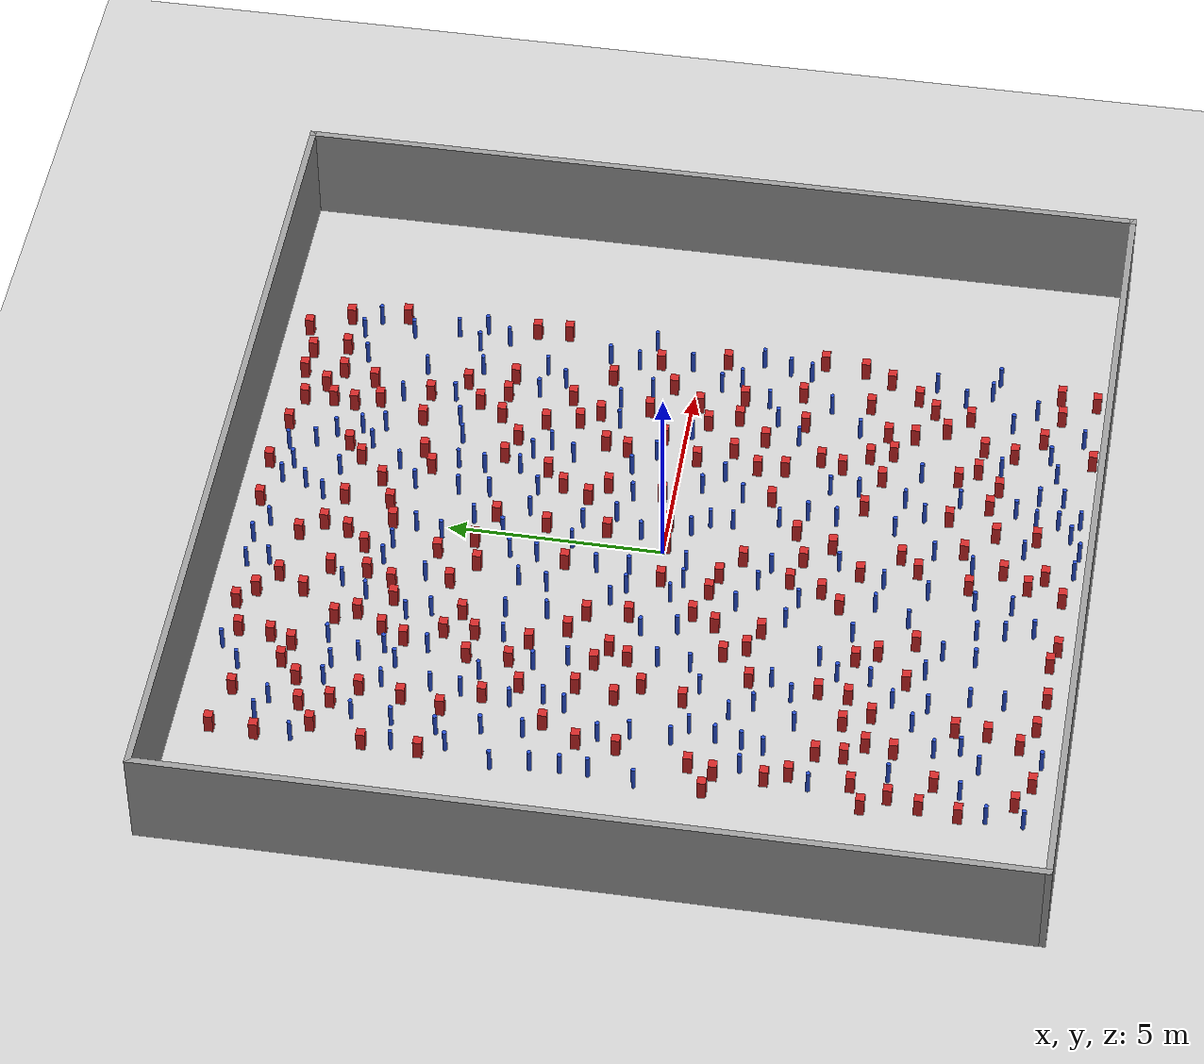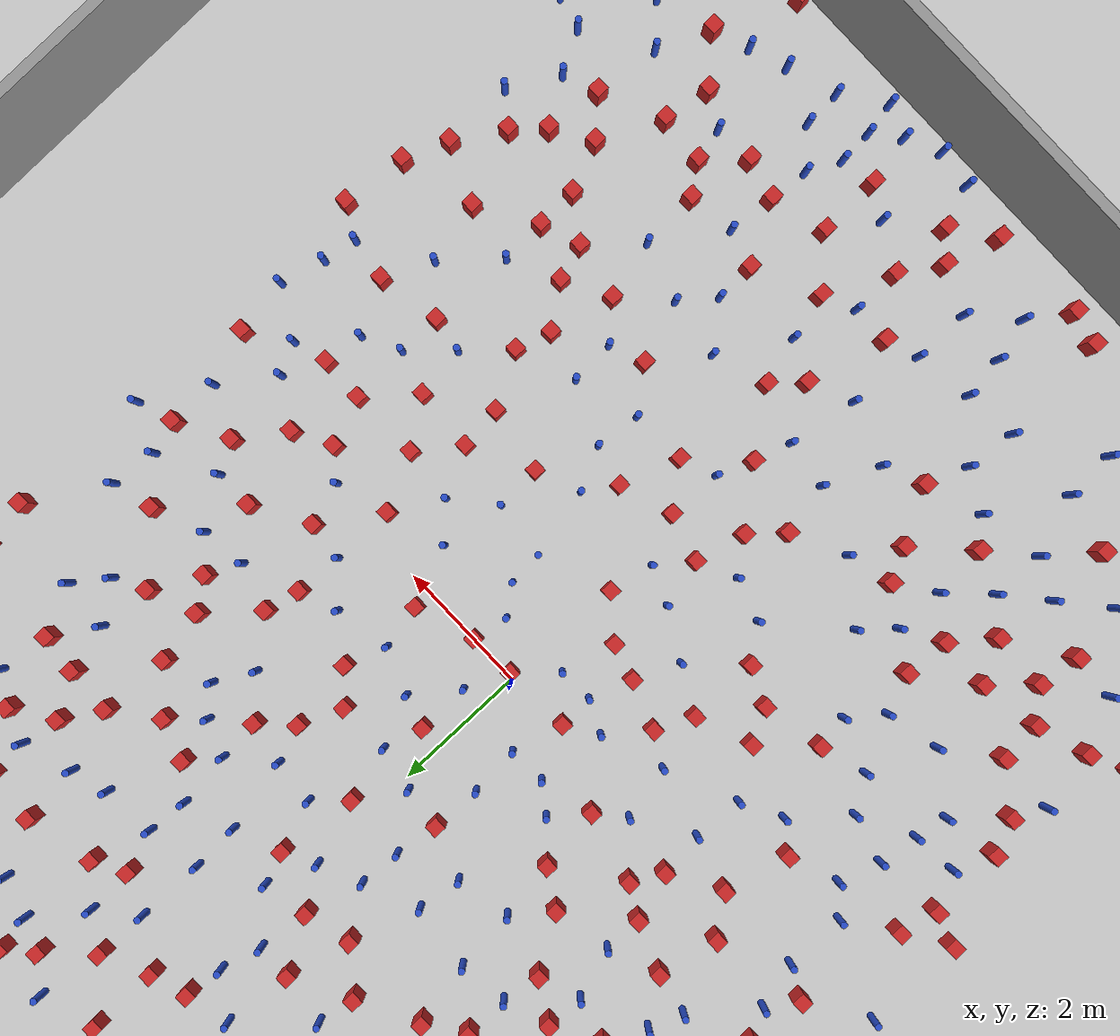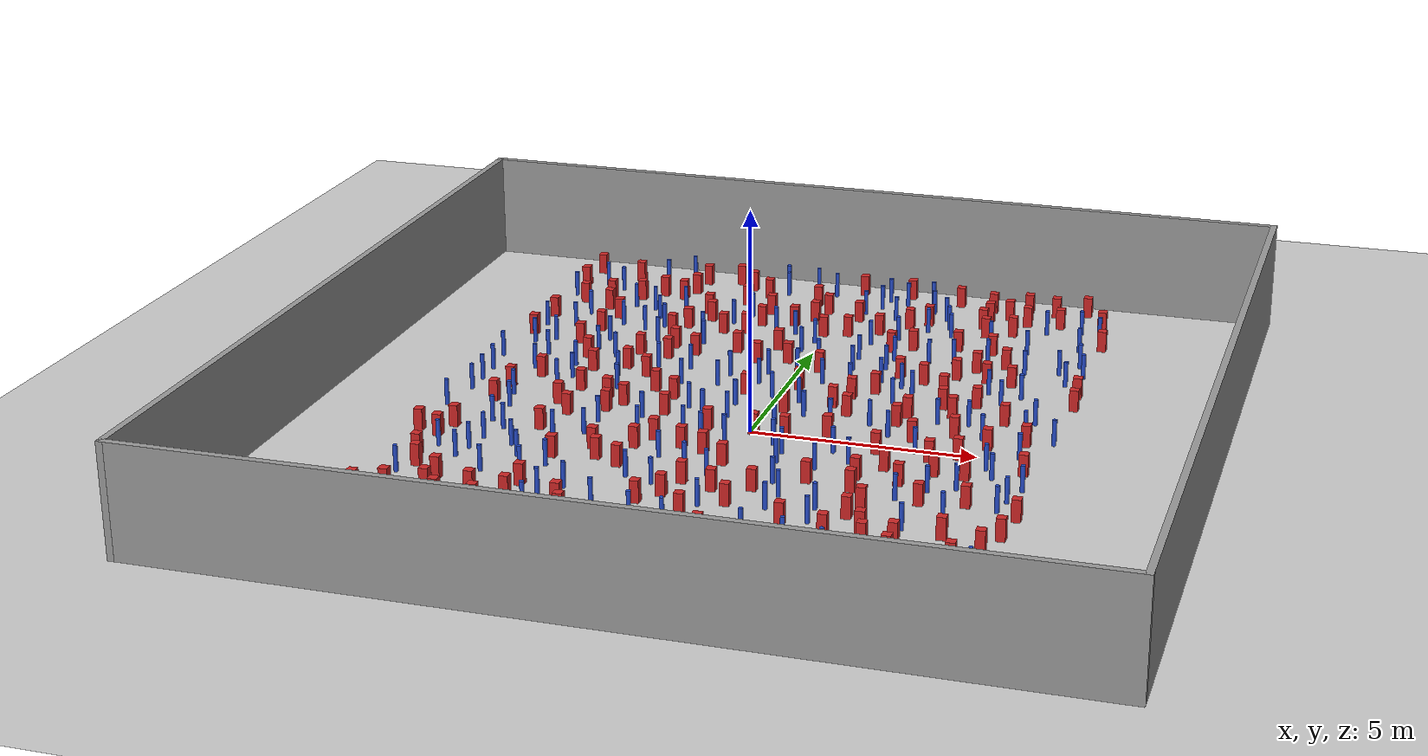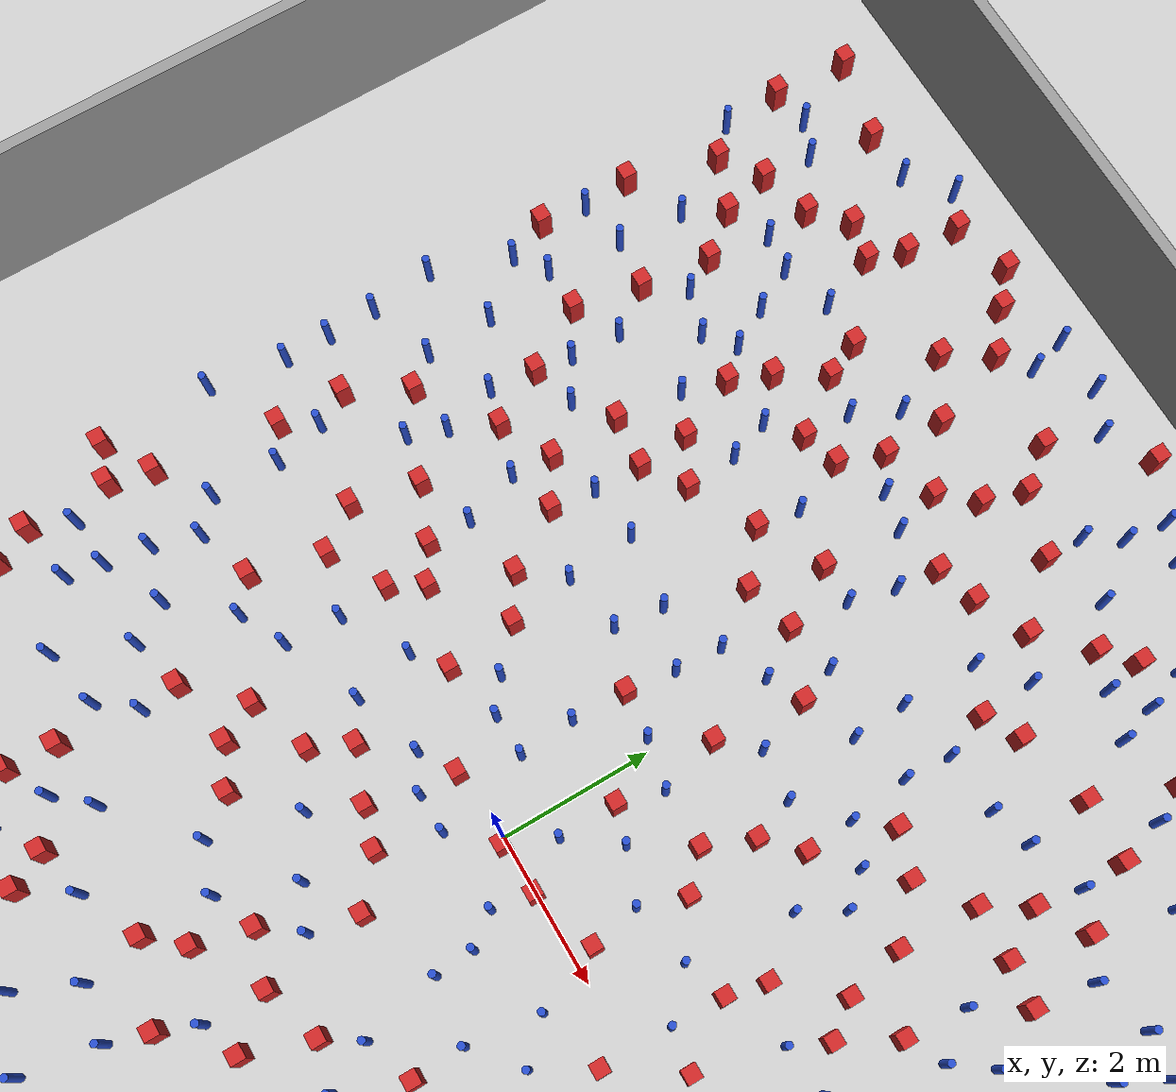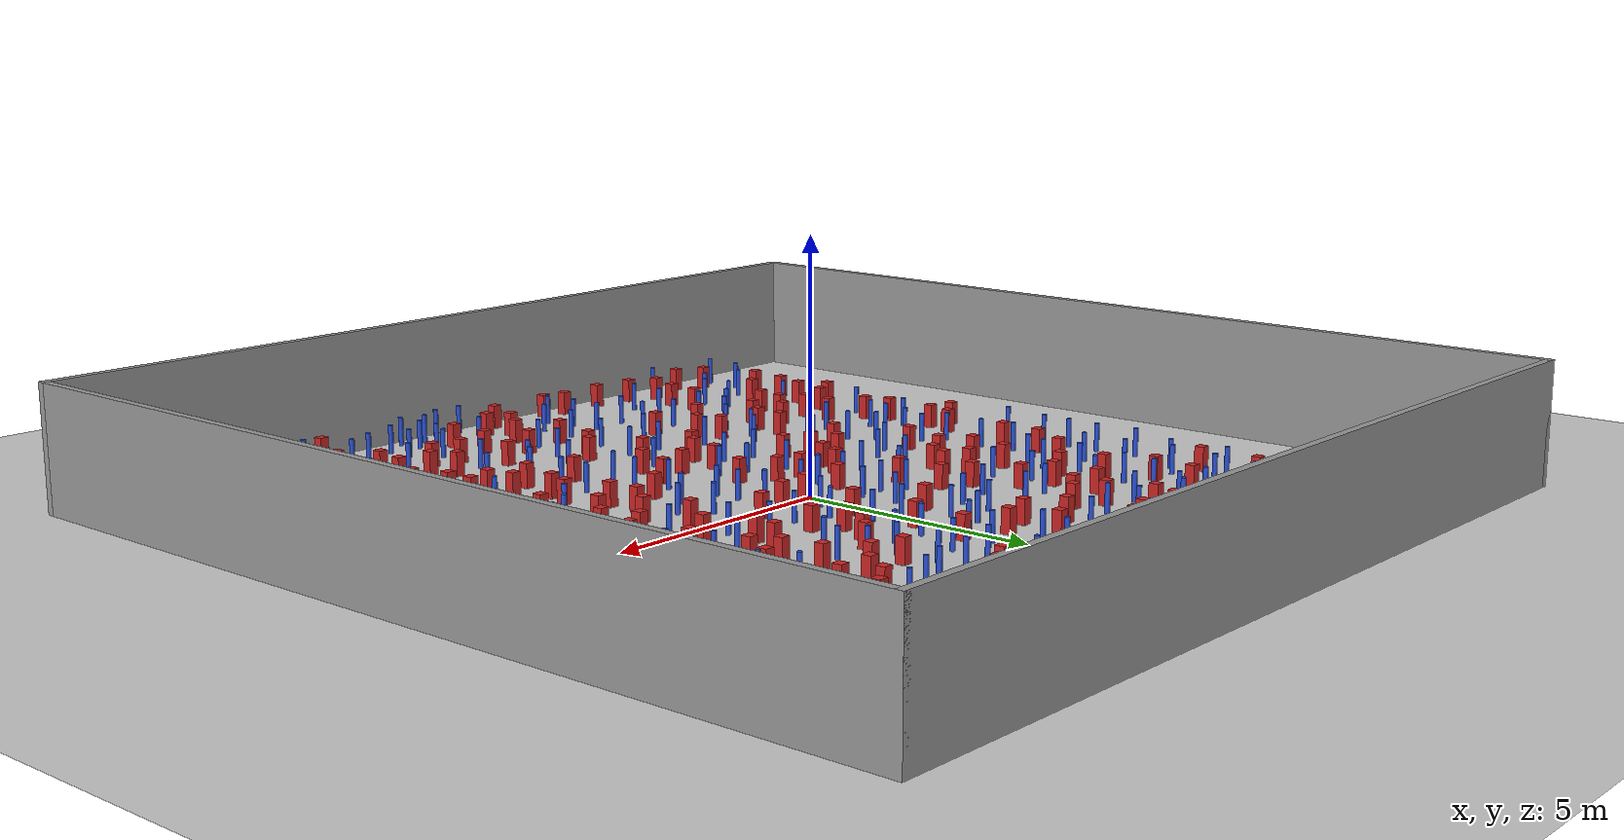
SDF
<sdf version="1.6">
 <world name="default">
  <light name="sun" type="directional">
   <pose>0 0 1000 0 -0 0</pose>
   <diffuse>0.8 0.8 0.8 1</diffuse>
   <specular>0.1 0.1 0.1 1</specular>
   <attenuation>
    <range>1000</range>
    <constant>0.9</constant>
    <linear>0.01</linear>
    <quadratic>0.001</quadratic>
   </attenuation>
   <direction>-0.5 0.5 -1</direction>
  </light>
  <model name="ground_plane">
   <static>1</static>
   <link name="link">
    <collision name="collision">
     <geometry><plane><normal>0 0 1</normal><size>100 100</size></plane></geometry>
     <surface><friction><ode><mu>100</mu><mu2>50</mu2></ode></friction></surface>
    </collision>
    <visual name="visual">
     <cast_shadows>0</cast_shadows>
     <geometry><plane><normal>0 0 1</normal><size>100 100</size></plane></geometry>
     <material>
      <ambient>1.0 1.0 1.0 1.0</ambient>
      <diffuse>0.8 0.8 0.8 1.0</diffuse>
      <specular>0.01 0.01 0.01 1.000000</specular>
     </material>
    </visual>
   </link>
  </model>
  <gravity>0 0 -9.8</gravity>
  <magnetic_field>6e-06 2.3e-05 -4.2e-05</magnetic_field>
  <atmosphere type="adiabatic"/>
  <physics name="default_physics" default="0" type="ode">
   <max_step_size>0.001</max_step_size>
   <real_time_factor>1</real_time_factor>
   <real_time_update_rate>1000</real_time_update_rate>
  </physics>
  <scene><ambient>0.4 0.4 0.4 1</ambient><background>0.7 0.7 0.7 1</background><shadows>1</shadows></scene>
  <spherical_coordinates>
   <surface_model>EARTH_WGS84</surface_model>
   <latitude_deg>0</latitude_deg>
   <longitude_deg>0</longitude_deg>
   <elevation>0</elevation>
   <heading_deg>0</heading_deg>
  </spherical_coordinates>
  <plugin name="gazebo_occupancy_map" filename="libgazebo_2Dmap_plugin.so">
   <map_resolution>0.05</map_resolution>
   <map_topic>generated_map</map_topic>
   <map_height>0.01</map_height>
   <map_size_x>50</map_size_x>
   <map_size_y>50</map_size_y>
  </plugin>
  <model name="NamedLocations">
   <static>true</static>
   <link name="DefaultStart"><pose>8.5 0 0 0 0 3.14</pose></link>
  </model>
  <model name="20x20_walls">
   <pose>0.044518 0.176112 0 0 -0 0</pose>
   <link name="Wall_1">
    <collision name="Wall_1_Collision">
     <geometry><box><size>20 0.15 2.5</size></box></geometry>
     <pose>0 0 1.25 0 -0 0</pose>
    </collision>
    <visual name="Wall_1_Visual">
     <pose>0 0 1.25 0 -0 0</pose>
     <geometry><box><size>20 0.15 2.5</size></box></geometry>
     <material>
      <script><uri>file://media/materials/scripts/gazebo.material</uri><name>Gazebo/Grey</name></script>
      <ambient>0.976471 0.992157 1 1</ambient>
     </material>
     <meta><layer>0</layer></meta>
    </visual>
    <pose>0 9.925 0 0 -0 0</pose>
   </link>
   <link name="Wall_3">
    <collision name="Wall_3_Collision">
     <geometry><box><size>20 0.15 2.5</size></box></geometry>
     <pose>0 0 1.25 0 -0 0</pose>
    </collision>
    <visual name="Wall_3_Visual">
     <pose>0 0 1.25 0 -0 0</pose>
     <geometry><box><size>20 0.15 2.5</size></box></geometry>
     <material>
      <script><uri>file://media/materials/scripts/gazebo.material</uri><name>Gazebo/Grey</name></script>
      <ambient>0.976471 0.992157 1 1</ambient>
     </material>
     <meta><layer>0</layer></meta>
    </visual>
    <pose>9.925 0 0 0 0 -1.5708</pose>
   </link>
   <link name="Wall_4">
    <collision name="Wall_4_Collision">
     <geometry><box><size>20 0.15 2.5</size></box></geometry>
     <pose>0 0 1.25 0 -0 0</pose>
    </collision>
    <visual name="Wall_4_Visual">
     <pose>0 0 1.25 0 -0 0</pose>
     <geometry><box><size>20 0.15 2.5</size></box></geometry>
     <material>
      <script><uri>file://media/materials/scripts/gazebo.material</uri><name>Gazebo/Grey</name></script>
      <ambient>0.976471 0.992157 1 1</ambient>
     </material>
     <meta><layer>0</layer></meta>
    </visual>
    <pose>0 -9.925 0 0 -0 3.14159</pose>
   </link>
   <link name="Wall_5">
    <collision name="Wall_5_Collision">
     <geometry><box><size>20 0.15 2.5</size></box></geometry>
     <pose>0 0 1.25 0 -0 0</pose>
    </collision>
    <visual name="Wall_5_Visual">
     <pose>0 0 1.25 0 -0 0</pose>
     <geometry><box><size>20 0.15 2.5</size></box></geometry>
     <material>
      <script><uri>file://media/materials/scripts/gazebo.material</uri><name>Gazebo/Grey</name></script>
      <ambient>0.976471 0.992157 1 1</ambient>
     </material>
     <meta><layer>0</layer></meta>
    </visual>
    <pose>-9.925 0 0 0 -0 1.5708</pose>
   </link>
   <static>1</static>
  </model>
  <model name="pole_obstacle0">
   <static>true</static>
   <pose>-6.77165514357 -8.17607878755 2.88873142074e-08 -9.9053668967e-09 4.60219948993e-07 -1.20965994957e-07</pose>
   <link name="link">
    <pose>0 0 0.3 0 -0 0</pose>
    <inertial>
     <mass>1</mass>
     <inertia><ixx>0.145833</ixx><ixy>0</ixy><ixz>0</ixz><iyy>0.145833</iyy><iyz>0</iyz><izz>0.125</izz></inertia>
    </inertial>
    <collision name="collision">
     <geometry><cylinder><radius>0.05</radius><length>.6</length></cylinder></geometry>
    </collision>
    <visual name="visual">
     <geometry><cylinder><radius>0.05</radius><length>.6</length></cylinder></geometry>
     <material>
      <script><name>Gazebo/Blue</name><uri>file://media/materials/scripts/gazebo.material</uri></script>
     </material>
    </visual>
   </link>
  </model>
  <model name="pole_obstacle1">
   <static>true</static>
   <pose>2.54243289153 2.50024052344 2.88873142074e-08 -9.90536690232e-09 4.6021994898e-07 -1.20965994968e-07</pose>
   <link name="link">
    <pose>0 0 0.3 0 -0 0</pose>
    <inertial>
     <mass>1</mass>
     <inertia><ixx>0.145833</ixx><ixy>0</ixy><ixz>0</ixz><iyy>0.145833</iyy><iyz>0</iyz><izz>0.125</izz></inertia>
    </inertial>
    <collision name="collision">
     <geometry><cylinder><radius>0.05</radius><length>.6</length></cylinder></geometry>
    </collision>
    <visual name="visual">
     <geometry><cylinder><radius>0.05</radius><length>.6</length></cylinder></geometry>
     <material>
      <script><name>Gazebo/Blue</name><uri>file://media/materials/scripts/gazebo.material</uri></script>
     </material>
    </visual>
   </link>
  </model>
  <model name="square_post_obstacle0">
   <static>true</static>
   <pose>-5.17980695407 6.07324742547 8.22691968438e-08 7.2212513382e-06 -7.54495500217e-07 2.29674213826e-05</pose>
   <link name="link">
    <pose>0 0 0.25 0 -0 0</pose>
    <inertial>
     <mass>100</mass>
     <inertia>
      <ixx>0.166667</ixx>
      <ixy>0</ixy>
      <ixz>0</ixz>
      <iyy>0.166667</iyy>
      <iyz>0</iyz>
      <izz>0.166667</izz>
     </inertia>
    </inertial>
    <collision name="collision"><geometry><box><size>.2 .2 .5</size></box></geometry></collision>
    <visual name="visual">
     <geometry><box><size>.2 .2 .5</size></box></geometry>
     <material>
      <script><name>Gazebo/Red</name><uri>file://media/materials/scripts/gazebo.material</uri></script>
     </material>
    </visual>
   </link>
  </model>
  <model name="square_post_obstacle1">
   <static>true</static>
   <pose>1.74829170394 1.53674628466 8.22691968438e-08 7.2212513382e-06 -7.54495500217e-07 2.29674213826e-05</pose>
   <link name="link">
    <pose>0 0 0.25 0 -0 0</pose>
    <inertial>
     <mass>100</mass>
     <inertia>
      <ixx>0.166667</ixx>
      <ixy>0</ixy>
      <ixz>0</ixz>
      <iyy>0.166667</iyy>
      <iyz>0</iyz>
      <izz>0.166667</izz>
     </inertia>
    </inertial>
    <collision name="collision"><geometry><box><size>.2 .2 .5</size></box></geometry></collision>
    <visual name="visual">
     <geometry><box><size>.2 .2 .5</size></box></geometry>
     <material>
      <script><name>Gazebo/Red</name><uri>file://media/materials/scripts/gazebo.material</uri></script>
     </material>
    </visual>
   </link>
  </model>
  <model name="pole_obstacle2">
   <static>true</static>
   <pose>-5.05019088084 6.91182319331 2.88873142074e-08 -9.90536690842e-09 4.60219948965e-07 -1.20965994976e-07</pose>
   <link name="link">
    <pose>0 0 0.3 0 -0 0</pose>
    <inertial>
     <mass>1</mass>
     <inertia><ixx>0.145833</ixx><ixy>0</ixy><ixz>0</ixz><iyy>0.145833</iyy><iyz>0</iyz><izz>0.125</izz></inertia>
    </inertial>
    <collision name="collision">
     <geometry><cylinder><radius>0.05</radius><length>.6</length></cylinder></geometry>
    </collision>
    <visual name="visual">
     <geometry><cylinder><radius>0.05</radius><length>.6</length></cylinder></geometry>
     <material>
      <script><name>Gazebo/Blue</name><uri>file://media/materials/scripts/gazebo.material</uri></script>
     </material>
    </visual>
   </link>
  </model>
  <model name="pole_obstacle3">
   <static>true</static>
   <pose>-5.39888138162 -2.00570616578 2.88873142074e-08 -9.90536689749e-09 4.60219948991e-07 -1.20965994959e-07</pose>
   <link name="link">
    <pose>0 0 0.3 0 -0 0</pose>
    <inertial>
     <mass>1</mass>
     <inertia><ixx>0.145833</ixx><ixy>0</ixy><ixz>0</ixz><iyy>0.145833</iyy><iyz>0</iyz><izz>0.125</izz></inertia>
    </inertial>
    <collision name="collision">
     <geometry><cylinder><radius>0.05</radius><length>.6</length></cylinder></geometry>
    </collision>
    <visual name="visual">
     <geometry><cylinder><radius>0.05</radius><length>.6</length></cylinder></geometry>
     <material>
      <script><name>Gazebo/Blue</name><uri>file://media/materials/scripts/gazebo.material</uri></script>
     </material>
    </visual>
   </link>
  </model>
  <model name="pole_obstacle4">
   <static>true</static>
   <pose>-1.41537158164 -0.388112318753 2.88873142074e-08 -9.90536689733e-09 4.60219948992e-07 -1.20965994959e-07</pose>
   <link name="link">
    <pose>0 0 0.3 0 -0 0</pose>
    <inertial>
     <mass>1</mass>
     <inertia><ixx>0.145833</ixx><ixy>0</ixy><ixz>0</ixz><iyy>0.145833</iyy><iyz>0</iyz><izz>0.125</izz></inertia>
    </inertial>
    <collision name="collision">
     <geometry><cylinder><radius>0.05</radius><length>.6</length></cylinder></geometry>
    </collision>
    <visual name="visual">
     <geometry><cylinder><radius>0.05</radius><length>.6</length></cylinder></geometry>
     <material>
      <script><name>Gazebo/Blue</name><uri>file://media/materials/scripts/gazebo.material</uri></script>
     </material>
    </visual>
   </link>
  </model>
  <model name="pole_obstacle5">
   <static>true</static>
   <pose>1.12844807914 4.97022982654 2.88873142074e-08 -9.90536689852e-09 4.60219948989e-07 -1.2096599496e-07</pose>
   <link name="link">
    <pose>0 0 0.3 0 -0 0</pose>
    <inertial>
     <mass>1</mass>
     <inertia><ixx>0.145833</ixx><ixy>0</ixy><ixz>0</ixz><iyy>0.145833</iyy><iyz>0</iyz><izz>0.125</izz></inertia>
    </inertial>
    <collision name="collision">
     <geometry><cylinder><radius>0.05</radius><length>.6</length></cylinder></geometry>
    </collision>
    <visual name="visual">
     <geometry><cylinder><radius>0.05</radius><length>.6</length></cylinder></geometry>
     <material>
      <script><name>Gazebo/Blue</name><uri>file://media/materials/scripts/gazebo.material</uri></script>
     </material>
    </visual>
   </link>
  </model>
  <model name="pole_obstacle6">
   <static>true</static>
   <pose>6.08152852984 -5.63300464826 2.88873142074e-08 -9.90536690842e-09 4.60219948965e-07 -1.20965994976e-07</pose>
   <link name="link">
    <pose>0 0 0.3 0 -0 0</pose>
    <inertial>
     <mass>1</mass>
     <inertia><ixx>0.145833</ixx><ixy>0</ixy><ixz>0</ixz><iyy>0.145833</iyy><iyz>0</iyz><izz>0.125</izz></inertia>
    </inertial>
    <collision name="collision">
     <geometry><cylinder><radius>0.05</radius><length>.6</length></cylinder></geometry>
    </collision>
    <visual name="visual">
     <geometry><cylinder><radius>0.05</radius><length>.6</length></cylinder></geometry>
     <material>
      <script><name>Gazebo/Blue</name><uri>file://media/materials/scripts/gazebo.material</uri></script>
     </material>
    </visual>
   </link>
  </model>
  <model name="square_post_obstacle2">
   <static>true</static>
   <pose>-5.81809010166 7.31867256626 8.22691968438e-08 7.2212513382e-06 -7.54495500217e-07 2.29674213826e-05</pose>
   <link name="link">
    <pose>0 0 0.25 0 -0 0</pose>
    <inertial>
     <mass>100</mass>
     <inertia>
      <ixx>0.166667</ixx>
      <ixy>0</ixy>
      <ixz>0</ixz>
      <iyy>0.166667</iyy>
      <iyz>0</iyz>
      <izz>0.166667</izz>
     </inertia>
    </inertial>
    <collision name="collision"><geometry><box><size>.2 .2 .5</size></box></geometry></collision>
    <visual name="visual">
     <geometry><box><size>.2 .2 .5</size></box></geometry>
     <material>
      <script><name>Gazebo/Red</name><uri>file://media/materials/scripts/gazebo.material</uri></script>
     </material>
    </visual>
   </link>
  </model>
  <model name="square_post_obstacle3">
   <static>true</static>
   <pose>-3.72602578323 -4.0872533452 8.22691968438e-08 7.2212513382e-06 -7.54495500217e-07 2.29674213826e-05</pose>
   <link name="link">
    <pose>0 0 0.25 0 -0 0</pose>
    <inertial>
     <mass>100</mass>
     <inertia>
      <ixx>0.166667</ixx>
      <ixy>0</ixy>
      <ixz>0</ixz>
      <iyy>0.166667</iyy>
      <iyz>0</iyz>
      <izz>0.166667</izz>
     </inertia>
    </inertial>
    <collision name="collision"><geometry><box><size>.2 .2 .5</size></box></geometry></collision>
    <visual name="visual">
     <geometry><box><size>.2 .2 .5</size></box></geometry>
     <material>
      <script><name>Gazebo/Red</name><uri>file://media/materials/scripts/gazebo.material</uri></script>
     </material>
    </visual>
   </link>
  </model>
  <model name="square_post_obstacle4">
   <static>true</static>
   <pose>-2.11316547237 0.448848622311 8.22691968438e-08 7.2212513382e-06 -7.54495500217e-07 2.29674213826e-05</pose>
   <link name="link">
    <pose>0 0 0.25 0 -0 0</pose>
    <inertial>
     <mass>100</mass>
     <inertia>
      <ixx>0.166667</ixx>
      <ixy>0</ixy>
      <ixz>0</ixz>
      <iyy>0.166667</iyy>
      <iyz>0</iyz>
      <izz>0.166667</izz>
     </inertia>
    </inertial>
    <collision name="collision"><geometry><box><size>.2 .2 .5</size></box></geometry></collision>
    <visual name="visual">
     <geometry><box><size>.2 .2 .5</size></box></geometry>
     <material>
      <script><name>Gazebo/Red</name><uri>file://media/materials/scripts/gazebo.material</uri></script>
     </material>
    </visual>
   </link>
  </model>
  <model name="pole_obstacle7">
   <static>true</static>
   <pose>5.83136260954 2.15012259453 2.88873142074e-08 -9.90536690245e-09 4.6021994898e-07 -1.20965994966e-07</pose>
   <link name="link">
    <pose>0 0 0.3 0 -0 0</pose>
    <inertial>
     <mass>1</mass>
     <inertia><ixx>0.145833</ixx><ixy>0</ixy><ixz>0</ixz><iyy>0.145833</iyy><iyz>0</iyz><izz>0.125</izz></inertia>
    </inertial>
    <collision name="collision">
     <geometry><cylinder><radius>0.05</radius><length>.6</length></cylinder></geometry>
    </collision>
    <visual name="visual">
     <geometry><cylinder><radius>0.05</radius><length>.6</length></cylinder></geometry>
     <material>
      <script><name>Gazebo/Blue</name><uri>file://media/materials/scripts/gazebo.material</uri></script>
     </material>
    </visual>
   </link>
  </model>
  <model name="pole_obstacle8">
   <static>true</static>
   <pose>-5.06630394369 -9.232732056 2.88873142074e-08 -9.9053668967e-09 4.60219948993e-07 -1.20965994957e-07</pose>
   <link name="link">
    <pose>0 0 0.3 0 -0 0</pose>
    <inertial>
     <mass>1</mass>
     <inertia><ixx>0.145833</ixx><ixy>0</ixy><ixz>0</ixz><iyy>0.145833</iyy><iyz>0</iyz><izz>0.125</izz></inertia>
    </inertial>
    <collision name="collision">
     <geometry><cylinder><radius>0.05</radius><length>.6</length></cylinder></geometry>
    </collision>
    <visual name="visual">
     <geometry><cylinder><radius>0.05</radius><length>.6</length></cylinder></geometry>
     <material>
      <script><name>Gazebo/Blue</name><uri>file://media/materials/scripts/gazebo.material</uri></script>
     </material>
    </visual>
   </link>
  </model>
  <model name="square_post_obstacle5">
   <static>true</static>
   <pose>5.31786343804 -2.54528029594 8.22691968438e-08 7.2212513382e-06 -7.54495500217e-07 2.29674213826e-05</pose>
   <link name="link">
    <pose>0 0 0.25 0 -0 0</pose>
    <inertial>
     <mass>100</mass>
     <inertia>
      <ixx>0.166667</ixx>
      <ixy>0</ixy>
      <ixz>0</ixz>
      <iyy>0.166667</iyy>
      <iyz>0</iyz>
      <izz>0.166667</izz>
     </inertia>
    </inertial>
    <collision name="collision"><geometry><box><size>.2 .2 .5</size></box></geometry></collision>
    <visual name="visual">
     <geometry><box><size>.2 .2 .5</size></box></geometry>
     <material>
      <script><name>Gazebo/Red</name><uri>file://media/materials/scripts/gazebo.material</uri></script>
     </material>
    </visual>
   </link>
  </model>
  <model name="square_post_obstacle6">
   <static>true</static>
   <pose>-3.87069192573 3.87692242752 8.22691968438e-08 7.2212513382e-06 -7.54495500217e-07 2.29674213826e-05</pose>
   <link name="link">
    <pose>0 0 0.25 0 -0 0</pose>
    <inertial>
     <mass>100</mass>
     <inertia>
      <ixx>0.166667</ixx>
      <ixy>0</ixy>
      <ixz>0</ixz>
      <iyy>0.166667</iyy>
      <iyz>0</iyz>
      <izz>0.166667</izz>
     </inertia>
    </inertial>
    <collision name="collision"><geometry><box><size>.2 .2 .5</size></box></geometry></collision>
    <visual name="visual">
     <geometry><box><size>.2 .2 .5</size></box></geometry>
     <material>
      <script><name>Gazebo/Red</name><uri>file://media/materials/scripts/gazebo.material</uri></script>
     </material>
    </visual>
   </link>
  </model>
  <model name="square_post_obstacle7">
   <static>true</static>
   <pose>1.57833472181 -8.45021443569 8.22691968438e-08 7.2212513382e-06 -7.54495500217e-07 2.29674213826e-05</pose>
   <link name="link">
    <pose>0 0 0.25 0 -0 0</pose>
    <inertial>
     <mass>100</mass>
     <inertia>
      <ixx>0.166667</ixx>
      <ixy>0</ixy>
      <ixz>0</ixz>
      <iyy>0.166667</iyy>
      <iyz>0</iyz>
      <izz>0.166667</izz>
     </inertia>
    </inertial>
    <collision name="collision"><geometry><box><size>.2 .2 .5</size></box></geometry></collision>
    <visual name="visual">
     <geometry><box><size>.2 .2 .5</size></box></geometry>
     <material>
      <script><name>Gazebo/Red</name><uri>file://media/materials/scripts/gazebo.material</uri></script>
     </material>
    </visual>
   </link>
  </model>
  <model name="pole_obstacle9">
   <static>true</static>
   <pose>2.75062196768 5.16766341242 2.88873142074e-08 -9.90536689859e-09 4.60219948989e-07 -1.20965994961e-07</pose>
   <link name="link">
    <pose>0 0 0.3 0 -0 0</pose>
    <inertial>
     <mass>1</mass>
     <inertia><ixx>0.145833</ixx><ixy>0</ixy><ixz>0</ixz><iyy>0.145833</iyy><iyz>0</iyz><izz>0.125</izz></inertia>
    </inertial>
    <collision name="collision">
     <geometry><cylinder><radius>0.05</radius><length>.6</length></cylinder></geometry>
    </collision>
    <visual name="visual">
     <geometry><cylinder><radius>0.05</radius><length>.6</length></cylinder></geometry>
     <material>
      <script><name>Gazebo/Blue</name><uri>file://media/materials/scripts/gazebo.material</uri></script>
     </material>
    </visual>
   </link>
  </model>
  <model name="pole_obstacle10">
   <static>true</static>
   <pose>-0.744563720308 -2.30739177899 2.88873142074e-08 -9.90536689636e-09 4.60219948994e-07 -1.20965994958e-07</pose>
   <link name="link">
    <pose>0 0 0.3 0 -0 0</pose>
    <inertial>
     <mass>1</mass>
     <inertia><ixx>0.145833</ixx><ixy>0</ixy><ixz>0</ixz><iyy>0.145833</iyy><iyz>0</iyz><izz>0.125</izz></inertia>
    </inertial>
    <collision name="collision">
     <geometry><cylinder><radius>0.05</radius><length>.6</length></cylinder></geometry>
    </collision>
    <visual name="visual">
     <geometry><cylinder><radius>0.05</radius><length>.6</length></cylinder></geometry>
     <material>
      <script><name>Gazebo/Blue</name><uri>file://media/materials/scripts/gazebo.material</uri></script>
     </material>
    </visual>
   </link>
  </model>
  <model name="pole_obstacle11">
   <static>true</static>
   <pose>2.91228357393 0.586450232013 2.88873142074e-08 -9.90536689285e-09 4.60219949002e-07 -1.20965994953e-07</pose>
   <link name="link">
    <pose>0 0 0.3 0 -0 0</pose>
    <inertial>
     <mass>1</mass>
     <inertia><ixx>0.145833</ixx><ixy>0</ixy><ixz>0</ixz><iyy>0.145833</iyy><iyz>0</iyz><izz>0.125</izz></inertia>
    </inertial>
    <collision name="collision">
     <geometry><cylinder><radius>0.05</radius><length>.6</length></cylinder></geometry>
    </collision>
    <visual name="visual">
     <geometry><cylinder><radius>0.05</radius><length>.6</length></cylinder></geometry>
     <material>
      <script><name>Gazebo/Blue</name><uri>file://media/materials/scripts/gazebo.material</uri></script>
     </material>
    </visual>
   </link>
  </model>
  <model name="pole_obstacle12">
   <static>true</static>
   <pose>6.35247733203 5.19964490263 2.88873142074e-08 -9.90536690842e-09 4.60219948965e-07 -1.20965994976e-07</pose>
   <link name="link">
    <pose>0 0 0.3 0 -0 0</pose>
    <inertial>
     <mass>1</mass>
     <inertia><ixx>0.145833</ixx><ixy>0</ixy><ixz>0</ixz><iyy>0.145833</iyy><iyz>0</iyz><izz>0.125</izz></inertia>
    </inertial>
    <collision name="collision">
     <geometry><cylinder><radius>0.05</radius><length>.6</length></cylinder></geometry>
    </collision>
    <visual name="visual">
     <geometry><cylinder><radius>0.05</radius><length>.6</length></cylinder></geometry>
     <material>
      <script><name>Gazebo/Blue</name><uri>file://media/materials/scripts/gazebo.material</uri></script>
     </material>
    </visual>
   </link>
  </model>
  <model name="square_post_obstacle8">
   <static>true</static>
   <pose>-3.58809597633 5.36162875197 8.22691968438e-08 7.2212513382e-06 -7.54495500217e-07 2.29674213826e-05</pose>
   <link name="link">
    <pose>0 0 0.25 0 -0 0</pose>
    <inertial>
     <mass>100</mass>
     <inertia>
      <ixx>0.166667</ixx>
      <ixy>0</ixy>
      <ixz>0</ixz>
      <iyy>0.166667</iyy>
      <iyz>0</iyz>
      <izz>0.166667</izz>
     </inertia>
    </inertial>
    <collision name="collision"><geometry><box><size>.2 .2 .5</size></box></geometry></collision>
    <visual name="visual">
     <geometry><box><size>.2 .2 .5</size></box></geometry>
     <material>
      <script><name>Gazebo/Red</name><uri>file://media/materials/scripts/gazebo.material</uri></script>
     </material>
    </visual>
   </link>
  </model>
  <model name="square_post_obstacle9">
   <static>true</static>
   <pose>-2.43418255598 5.8071528394 8.22691968438e-08 7.2212513382e-06 -7.54495500217e-07 2.29674213826e-05</pose>
   <link name="link">
    <pose>0 0 0.25 0 -0 0</pose>
    <inertial>
     <mass>100</mass>
     <inertia>
      <ixx>0.166667</ixx>
      <ixy>0</ixy>
      <ixz>0</ixz>
      <iyy>0.166667</iyy>
      <iyz>0</iyz>
      <izz>0.166667</izz>
     </inertia>
    </inertial>
    <collision name="collision"><geometry><box><size>.2 .2 .5</size></box></geometry></collision>
    <visual name="visual">
     <geometry><box><size>.2 .2 .5</size></box></geometry>
     <material>
      <script><name>Gazebo/Red</name><uri>file://media/materials/scripts/gazebo.material</uri></script>
     </material>
    </visual>
   </link>
  </model>
  <model name="pole_obstacle13">
   <static>true</static>
   <pose>-6.26059618692 8.23797673308 2.88873142074e-08 -9.9053668967e-09 4.60219948993e-07 -1.20965994957e-07</pose>
   <link name="link">
    <pose>0 0 0.3 0 -0 0</pose>
    <inertial>
     <mass>1</mass>
     <inertia><ixx>0.145833</ixx><ixy>0</ixy><ixz>0</ixz><iyy>0.145833</iyy><iyz>0</iyz><izz>0.125</izz></inertia>
    </inertial>
    <collision name="collision">
     <geometry><cylinder><radius>0.05</radius><length>.6</length></cylinder></geometry>
    </collision>
    <visual name="visual">
     <geometry><cylinder><radius>0.05</radius><length>.6</length></cylinder></geometry>
     <material>
      <script><name>Gazebo/Blue</name><uri>file://media/materials/scripts/gazebo.material</uri></script>
     </material>
    </visual>
   </link>
  </model>
  <model name="square_post_obstacle10">
   <static>true</static>
   <pose>-0.852581200315 5.08488537747 8.22691968438e-08 7.2212513382e-06 -7.54495500217e-07 2.29674213826e-05</pose>
   <link name="link">
    <pose>0 0 0.25 0 -0 0</pose>
    <inertial>
     <mass>100</mass>
     <inertia>
      <ixx>0.166667</ixx>
      <ixy>0</ixy>
      <ixz>0</ixz>
      <iyy>0.166667</iyy>
      <iyz>0</iyz>
      <izz>0.166667</izz>
     </inertia>
    </inertial>
    <collision name="collision"><geometry><box><size>.2 .2 .5</size></box></geometry></collision>
    <visual name="visual">
     <geometry><box><size>.2 .2 .5</size></box></geometry>
     <material>
      <script><name>Gazebo/Red</name><uri>file://media/materials/scripts/gazebo.material</uri></script>
     </material>
    </visual>
   </link>
  </model>
  <model name="square_post_obstacle11">
   <static>true</static>
   <pose>-2.14693727234 -2.58435467613 8.22691968438e-08 7.2212513382e-06 -7.54495500217e-07 2.29674213826e-05</pose>
   <link name="link">
    <pose>0 0 0.25 0 -0 0</pose>
    <inertial>
     <mass>100</mass>
     <inertia>
      <ixx>0.166667</ixx>
      <ixy>0</ixy>
      <ixz>0</ixz>
      <iyy>0.166667</iyy>
      <iyz>0</iyz>
      <izz>0.166667</izz>
     </inertia>
    </inertial>
    <collision name="collision"><geometry><box><size>.2 .2 .5</size></box></geometry></collision>
    <visual name="visual">
     <geometry><box><size>.2 .2 .5</size></box></geometry>
     <material>
      <script><name>Gazebo/Red</name><uri>file://media/materials/scripts/gazebo.material</uri></script>
     </material>
    </visual>
   </link>
  </model>
  <model name="pole_obstacle14">
   <static>true</static>
   <pose>-1.27438803534 6.27796606329 2.88873142074e-08 -9.90536689852e-09 4.60219948989e-07 -1.2096599496e-07</pose>
   <link name="link">
    <pose>0 0 0.3 0 -0 0</pose>
    <inertial>
     <mass>1</mass>
     <inertia><ixx>0.145833</ixx><ixy>0</ixy><ixz>0</ixz><iyy>0.145833</iyy><iyz>0</iyz><izz>0.125</izz></inertia>
    </inertial>
    <collision name="collision">
     <geometry><cylinder><radius>0.05</radius><length>.6</length></cylinder></geometry>
    </collision>
    <visual name="visual">
     <geometry><cylinder><radius>0.05</radius><length>.6</length></cylinder></geometry>
     <material>
      <script><name>Gazebo/Blue</name><uri>file://media/materials/scripts/gazebo.material</uri></script>
     </material>
    </visual>
   </link>
  </model>
  <model name="pole_obstacle15">
   <static>true</static>
   <pose>-2.80426005995 -3.99331555649 2.88873142074e-08 -9.90536690455e-09 4.60219948975e-07 -1.20965994972e-07</pose>
   <link name="link">
    <pose>0 0 0.3 0 -0 0</pose>
    <inertial>
     <mass>1</mass>
     <inertia><ixx>0.145833</ixx><ixy>0</ixy><ixz>0</ixz><iyy>0.145833</iyy><iyz>0</iyz><izz>0.125</izz></inertia>
    </inertial>
    <collision name="collision">
     <geometry><cylinder><radius>0.05</radius><length>.6</length></cylinder></geometry>
    </collision>
    <visual name="visual">
     <geometry><cylinder><radius>0.05</radius><length>.6</length></cylinder></geometry>
     <material>
      <script><name>Gazebo/Blue</name><uri>file://media/materials/scripts/gazebo.material</uri></script>
     </material>
    </visual>
   </link>
  </model>
  <model name="square_post_obstacle12">
   <static>true</static>
   <pose>-1.1600024564 -1.24396540981 8.22691968438e-08 7.2212513382e-06 -7.54495500217e-07 2.29674213826e-05</pose>
   <link name="link">
    <pose>0 0 0.25 0 -0 0</pose>
    <inertial>
     <mass>100</mass>
     <inertia>
      <ixx>0.166667</ixx>
      <ixy>0</ixy>
      <ixz>0</ixz>
      <iyy>0.166667</iyy>
      <iyz>0</iyz>
      <izz>0.166667</izz>
     </inertia>
    </inertial>
    <collision name="collision"><geometry><box><size>.2 .2 .5</size></box></geometry></collision>
    <visual name="visual">
     <geometry><box><size>.2 .2 .5</size></box></geometry>
     <material>
      <script><name>Gazebo/Red</name><uri>file://media/materials/scripts/gazebo.material</uri></script>
     </material>
    </visual>
   </link>
  </model>
  <model name="pole_obstacle16">
   <static>true</static>
   <pose>-6.45074321504 -4.21881022412 2.88873142074e-08 -9.90536690842e-09 4.60219948965e-07 -1.20965994976e-07</pose>
   <link name="link">
    <pose>0 0 0.3 0 -0 0</pose>
    <inertial>
     <mass>1</mass>
     <inertia><ixx>0.145833</ixx><ixy>0</ixy><ixz>0</ixz><iyy>0.145833</iyy><iyz>0</iyz><izz>0.125</izz></inertia>
    </inertial>
    <collision name="collision">
     <geometry><cylinder><radius>0.05</radius><length>.6</length></cylinder></geometry>
    </collision>
    <visual name="visual">
     <geometry><cylinder><radius>0.05</radius><length>.6</length></cylinder></geometry>
     <material>
      <script><name>Gazebo/Blue</name><uri>file://media/materials/scripts/gazebo.material</uri></script>
     </material>
    </visual>
   </link>
  </model>
  <model name="pole_obstacle17">
   <static>true</static>
   <pose>-5.99743441476 5.19034438451 2.88873142074e-08 -9.90536690842e-09 4.60219948965e-07 -1.20965994976e-07</pose>
   <link name="link">
    <pose>0 0 0.3 0 -0 0</pose>
    <inertial>
     <mass>1</mass>
     <inertia><ixx>0.145833</ixx><ixy>0</ixy><ixz>0</ixz><iyy>0.145833</iyy><iyz>0</iyz><izz>0.125</izz></inertia>
    </inertial>
    <collision name="collision">
     <geometry><cylinder><radius>0.05</radius><length>.6</length></cylinder></geometry>
    </collision>
    <visual name="visual">
     <geometry><cylinder><radius>0.05</radius><length>.6</length></cylinder></geometry>
     <material>
      <script><name>Gazebo/Blue</name><uri>file://media/materials/scripts/gazebo.material</uri></script>
     </material>
    </visual>
   </link>
  </model>
  <model name="square_post_obstacle13">
   <static>true</static>
   <pose>-0.627202502362 -1.4013469367 8.22691968438e-08 7.2212513382e-06 -7.54495500217e-07 2.29674213826e-05</pose>
   <link name="link">
    <pose>0 0 0.25 0 -0 0</pose>
    <inertial>
     <mass>100</mass>
     <inertia>
      <ixx>0.166667</ixx>
      <ixy>0</ixy>
      <ixz>0</ixz>
      <iyy>0.166667</iyy>
      <iyz>0</iyz>
      <izz>0.166667</izz>
     </inertia>
    </inertial>
    <collision name="collision"><geometry><box><size>.2 .2 .5</size></box></geometry></collision>
    <visual name="visual">
     <geometry><box><size>.2 .2 .5</size></box></geometry>
     <material>
      <script><name>Gazebo/Red</name><uri>file://media/materials/scripts/gazebo.material</uri></script>
     </material>
    </visual>
   </link>
  </model>
  <model name="pole_obstacle18">
   <static>true</static>
   <pose>0.877710790639 9.0844048404 2.88873142074e-08 -9.90536690779e-09 4.60219948967e-07 -1.20965994975e-07</pose>
   <link name="link">
    <pose>0 0 0.3 0 -0 0</pose>
    <inertial>
     <mass>1</mass>
     <inertia><ixx>0.145833</ixx><ixy>0</ixy><ixz>0</ixz><iyy>0.145833</iyy><iyz>0</iyz><izz>0.125</izz></inertia>
    </inertial>
    <collision name="collision">
     <geometry><cylinder><radius>0.05</radius><length>.6</length></cylinder></geometry>
    </collision>
    <visual name="visual">
     <geometry><cylinder><radius>0.05</radius><length>.6</length></cylinder></geometry>
     <material>
      <script><name>Gazebo/Blue</name><uri>file://media/materials/scripts/gazebo.material</uri></script>
     </material>
    </visual>
   </link>
  </model>
  <model name="square_post_obstacle14">
   <static>true</static>
   <pose>-5.59246458541 8.87830148658 8.22691968438e-08 7.22125133819e-06 -7.54495500217e-07 2.29674213826e-05</pose>
   <link name="link">
    <pose>0 0 0.25 0 -0 0</pose>
    <inertial>
     <mass>100</mass>
     <inertia>
      <ixx>0.166667</ixx>
      <ixy>0</ixy>
      <ixz>0</ixz>
      <iyy>0.166667</iyy>
      <iyz>0</iyz>
      <izz>0.166667</izz>
     </inertia>
    </inertial>
    <collision name="collision"><geometry><box><size>.2 .2 .5</size></box></geometry></collision>
    <visual name="visual">
     <geometry><box><size>.2 .2 .5</size></box></geometry>
     <material>
      <script><name>Gazebo/Red</name><uri>file://media/materials/scripts/gazebo.material</uri></script>
     </material>
    </visual>
   </link>
  </model>
  <model name="pole_obstacle19">
   <static>true</static>
   <pose>5.99709892169 -6.95808218375 2.88873142074e-08 -9.90536690842e-09 4.60219948965e-07 -1.20965994976e-07</pose>
   <link name="link">
    <pose>0 0 0.3 0 -0 0</pose>
    <inertial>
     <mass>1</mass>
     <inertia><ixx>0.145833</ixx><ixy>0</ixy><ixz>0</ixz><iyy>0.145833</iyy><iyz>0</iyz><izz>0.125</izz></inertia>
    </inertial>
    <collision name="collision">
     <geometry><cylinder><radius>0.05</radius><length>.6</length></cylinder></geometry>
    </collision>
    <visual name="visual">
     <geometry><cylinder><radius>0.05</radius><length>.6</length></cylinder></geometry>
     <material>
      <script><name>Gazebo/Blue</name><uri>file://media/materials/scripts/gazebo.material</uri></script>
     </material>
    </visual>
   </link>
  </model>
  <model name="square_post_obstacle15">
   <static>true</static>
   <pose>-2.22045392741 1.4042794014 8.22691968438e-08 7.2212513382e-06 -7.54495500217e-07 2.29674213826e-05</pose>
   <link name="link">
    <pose>0 0 0.25 0 -0 0</pose>
    <inertial>
     <mass>100</mass>
     <inertia>
      <ixx>0.166667</ixx>
      <ixy>0</ixy>
      <ixz>0</ixz>
      <iyy>0.166667</iyy>
      <iyz>0</iyz>
      <izz>0.166667</izz>
     </inertia>
    </inertial>
    <collision name="collision"><geometry><box><size>.2 .2 .5</size></box></geometry></collision>
    <visual name="visual">
     <geometry><box><size>.2 .2 .5</size></box></geometry>
     <material>
      <script><name>Gazebo/Red</name><uri>file://media/materials/scripts/gazebo.material</uri></script>
     </material>
    </visual>
   </link>
  </model>
  <model name="square_post_obstacle16">
   <static>true</static>
   <pose>-2.76167531321 1.74624394198 8.22691968438e-08 7.2212513382e-06 -7.54495500217e-07 2.29674213826e-05</pose>
   <link name="link">
    <pose>0 0 0.25 0 -0 0</pose>
    <inertial>
     <mass>100</mass>
     <inertia>
      <ixx>0.166667</ixx>
      <ixy>0</ixy>
      <ixz>0</ixz>
      <iyy>0.166667</iyy>
      <iyz>0</iyz>
      <izz>0.166667</izz>
     </inertia>
    </inertial>
    <collision name="collision"><geometry><box><size>.2 .2 .5</size></box></geometry></collision>
    <visual name="visual">
     <geometry><box><size>.2 .2 .5</size></box></geometry>
     <material>
      <script><name>Gazebo/Red</name><uri>file://media/materials/scripts/gazebo.material</uri></script>
     </material>
    </visual>
   </link>
  </model>
  <model name="square_post_obstacle17">
   <static>true</static>
   <pose>-5.9862439751 1.03160733476 8.22691968438e-08 7.2212513382e-06 -7.54495500217e-07 2.29674213826e-05</pose>
   <link name="link">
    <pose>0 0 0.25 0 -0 0</pose>
    <inertial>
     <mass>100</mass>
     <inertia>
      <ixx>0.166667</ixx>
      <ixy>0</ixy>
      <ixz>0</ixz>
      <iyy>0.166667</iyy>
      <iyz>0</iyz>
      <izz>0.166667</izz>
     </inertia>
    </inertial>
    <collision name="collision"><geometry><box><size>.2 .2 .5</size></box></geometry></collision>
    <visual name="visual">
     <geometry><box><size>.2 .2 .5</size></box></geometry>
     <material>
      <script><name>Gazebo/Red</name><uri>file://media/materials/scripts/gazebo.material</uri></script>
     </material>
    </visual>
   </link>
  </model>
  <model name="pole_obstacle20">
   <static>true</static>
   <pose>0.496173714521 8.05047855768 2.88873142074e-08 -9.90536690577e-09 4.60219948971e-07 -1.20965994972e-07</pose>
   <link name="link">
    <pose>0 0 0.3 0 -0 0</pose>
    <inertial>
     <mass>1</mass>
     <inertia><ixx>0.145833</ixx><ixy>0</ixy><ixz>0</ixz><iyy>0.145833</iyy><iyz>0</iyz><izz>0.125</izz></inertia>
    </inertial>
    <collision name="collision">
     <geometry><cylinder><radius>0.05</radius><length>.6</length></cylinder></geometry>
    </collision>
    <visual name="visual">
     <geometry><cylinder><radius>0.05</radius><length>.6</length></cylinder></geometry>
     <material>
      <script><name>Gazebo/Blue</name><uri>file://media/materials/scripts/gazebo.material</uri></script>
     </material>
    </visual>
   </link>
  </model>
  <model name="pole_obstacle21">
   <static>true</static>
   <pose>-6.17717436868 -7.54374471874 2.88873142074e-08 -9.90536690842e-09 4.60219948965e-07 -1.20965994976e-07</pose>
   <link name="link">
    <pose>0 0 0.3 0 -0 0</pose>
    <inertial>
     <mass>1</mass>
     <inertia><ixx>0.145833</ixx><ixy>0</ixy><ixz>0</ixz><iyy>0.145833</iyy><iyz>0</iyz><izz>0.125</izz></inertia>
    </inertial>
    <collision name="collision">
     <geometry><cylinder><radius>0.05</radius><length>.6</length></cylinder></geometry>
    </collision>
    <visual name="visual">
     <geometry><cylinder><radius>0.05</radius><length>.6</length></cylinder></geometry>
     <material>
      <script><name>Gazebo/Blue</name><uri>file://media/materials/scripts/gazebo.material</uri></script>
     </material>
    </visual>
   </link>
  </model>
  <model name="pole_obstacle22">
   <static>true</static>
   <pose>2.46301673832 -6.58063587267 2.88873142074e-08 -9.90536689859e-09 4.60219948989e-07 -1.20965994961e-07</pose>
   <link name="link">
    <pose>0 0 0.3 0 -0 0</pose>
    <inertial>
     <mass>1</mass>
     <inertia><ixx>0.145833</ixx><ixy>0</ixy><ixz>0</ixz><iyy>0.145833</iyy><iyz>0</iyz><izz>0.125</izz></inertia>
    </inertial>
    <collision name="collision">
     <geometry><cylinder><radius>0.05</radius><length>.6</length></cylinder></geometry>
    </collision>
    <visual name="visual">
     <geometry><cylinder><radius>0.05</radius><length>.6</length></cylinder></geometry>
     <material>
      <script><name>Gazebo/Blue</name><uri>file://media/materials/scripts/gazebo.material</uri></script>
     </material>
    </visual>
   </link>
  </model>
  <model name="pole_obstacle23">
   <static>true</static>
   <pose>0.532219835448 1.94401171994 2.88873142074e-08 -9.90536690151e-09 4.60219948982e-07 -1.20965994965e-07</pose>
   <link name="link">
    <pose>0 0 0.3 0 -0 0</pose>
    <inertial>
     <mass>1</mass>
     <inertia><ixx>0.145833</ixx><ixy>0</ixy><ixz>0</ixz><iyy>0.145833</iyy><iyz>0</iyz><izz>0.125</izz></inertia>
    </inertial>
    <collision name="collision">
     <geometry><cylinder><radius>0.05</radius><length>.6</length></cylinder></geometry>
    </collision>
    <visual name="visual">
     <geometry><cylinder><radius>0.05</radius><length>.6</length></cylinder></geometry>
     <material>
      <script><name>Gazebo/Blue</name><uri>file://media/materials/scripts/gazebo.material</uri></script>
     </material>
    </visual>
   </link>
  </model>
  <model name="square_post_obstacle18">
   <static>true</static>
   <pose>0.560268090838 -5.44637382726 8.22691968438e-08 7.2212513382e-06 -7.54495500217e-07 2.29674213826e-05</pose>
   <link name="link">
    <pose>0 0 0.25 0 -0 0</pose>
    <inertial>
     <mass>100</mass>
     <inertia>
      <ixx>0.166667</ixx>
      <ixy>0</ixy>
      <ixz>0</ixz>
      <iyy>0.166667</iyy>
      <iyz>0</iyz>
      <izz>0.166667</izz>
     </inertia>
    </inertial>
    <collision name="collision"><geometry><box><size>.2 .2 .5</size></box></geometry></collision>
    <visual name="visual">
     <geometry><box><size>.2 .2 .5</size></box></geometry>
     <material>
      <script><name>Gazebo/Red</name><uri>file://media/materials/scripts/gazebo.material</uri></script>
     </material>
    </visual>
   </link>
  </model>
  <model name="pole_obstacle24">
   <static>true</static>
   <pose>-3.81732461303 -6.56304847375 2.88873142074e-08 -9.90536692062e-09 4.60219948937e-07 -1.20965994985e-07</pose>
   <link name="link">
    <pose>0 0 0.3 0 -0 0</pose>
    <inertial>
     <mass>1</mass>
     <inertia><ixx>0.145833</ixx><ixy>0</ixy><ixz>0</ixz><iyy>0.145833</iyy><iyz>0</iyz><izz>0.125</izz></inertia>
    </inertial>
    <collision name="collision">
     <geometry><cylinder><radius>0.05</radius><length>.6</length></cylinder></geometry>
    </collision>
    <visual name="visual">
     <geometry><cylinder><radius>0.05</radius><length>.6</length></cylinder></geometry>
     <material>
      <script><name>Gazebo/Blue</name><uri>file://media/materials/scripts/gazebo.material</uri></script>
     </material>
    </visual>
   </link>
  </model>
  <model name="pole_obstacle25">
   <static>true</static>
   <pose>-5.56865304958 -0.113580184732 2.88873142074e-08 -9.90536689681e-09 4.60219948993e-07 -1.20965994959e-07</pose>
   <link name="link">
    <pose>0 0 0.3 0 -0 0</pose>
    <inertial>
     <mass>1</mass>
     <inertia><ixx>0.145833</ixx><ixy>0</ixy><ixz>0</ixz><iyy>0.145833</iyy><iyz>0</iyz><izz>0.125</izz></inertia>
    </inertial>
    <collision name="collision">
     <geometry><cylinder><radius>0.05</radius><length>.6</length></cylinder></geometry>
    </collision>
    <visual name="visual">
     <geometry><cylinder><radius>0.05</radius><length>.6</length></cylinder></geometry>
     <material>
      <script><name>Gazebo/Blue</name><uri>file://media/materials/scripts/gazebo.material</uri></script>
     </material>
    </visual>
   </link>
  </model>
  <model name="pole_obstacle26">
   <static>true</static>
   <pose>2.86004743511 7.0189438137 2.88873142074e-08 -9.90536689859e-09 4.60219948989e-07 -1.20965994961e-07</pose>
   <link name="link">
    <pose>0 0 0.3 0 -0 0</pose>
    <inertial>
     <mass>1</mass>
     <inertia><ixx>0.145833</ixx><ixy>0</ixy><ixz>0</ixz><iyy>0.145833</iyy><iyz>0</iyz><izz>0.125</izz></inertia>
    </inertial>
    <collision name="collision">
     <geometry><cylinder><radius>0.05</radius><length>.6</length></cylinder></geometry>
    </collision>
    <visual name="visual">
     <geometry><cylinder><radius>0.05</radius><length>.6</length></cylinder></geometry>
     <material>
      <script><name>Gazebo/Blue</name><uri>file://media/materials/scripts/gazebo.material</uri></script>
     </material>
    </visual>
   </link>
  </model>
  <model name="pole_obstacle27">
   <static>true</static>
   <pose>3.30351959912 5.32341900675 2.88873142074e-08 -9.90536689859e-09 4.60219948989e-07 -1.20965994961e-07</pose>
   <link name="link">
    <pose>0 0 0.3 0 -0 0</pose>
    <inertial>
     <mass>1</mass>
     <inertia><ixx>0.145833</ixx><ixy>0</ixy><ixz>0</ixz><iyy>0.145833</iyy><iyz>0</iyz><izz>0.125</izz></inertia>
    </inertial>
    <collision name="collision">
     <geometry><cylinder><radius>0.05</radius><length>.6</length></cylinder></geometry>
    </collision>
    <visual name="visual">
     <geometry><cylinder><radius>0.05</radius><length>.6</length></cylinder></geometry>
     <material>
      <script><name>Gazebo/Blue</name><uri>file://media/materials/scripts/gazebo.material</uri></script>
     </material>
    </visual>
   </link>
  </model>
  <model name="pole_obstacle28">
   <static>true</static>
   <pose>5.78323723134 5.29497538898 2.88873142074e-08 -9.90536690842e-09 4.60219948965e-07 -1.20965994976e-07</pose>
   <link name="link">
    <pose>0 0 0.3 0 -0 0</pose>
    <inertial>
     <mass>1</mass>
     <inertia><ixx>0.145833</ixx><ixy>0</ixy><ixz>0</ixz><iyy>0.145833</iyy><iyz>0</iyz><izz>0.125</izz></inertia>
    </inertial>
    <collision name="collision">
     <geometry><cylinder><radius>0.05</radius><length>.6</length></cylinder></geometry>
    </collision>
    <visual name="visual">
     <geometry><cylinder><radius>0.05</radius><length>.6</length></cylinder></geometry>
     <material>
      <script><name>Gazebo/Blue</name><uri>file://media/materials/scripts/gazebo.material</uri></script>
     </material>
    </visual>
   </link>
  </model>
  <model name="square_post_obstacle19">
   <static>true</static>
   <pose>3.93917195799 4.95328247818 8.22691968438e-08 7.2212513382e-06 -7.54495500217e-07 2.29674213826e-05</pose>
   <link name="link">
    <pose>0 0 0.25 0 -0 0</pose>
    <inertial>
     <mass>100</mass>
     <inertia>
      <ixx>0.166667</ixx>
      <ixy>0</ixy>
      <ixz>0</ixz>
      <iyy>0.166667</iyy>
      <iyz>0</iyz>
      <izz>0.166667</izz>
     </inertia>
    </inertial>
    <collision name="collision"><geometry><box><size>.2 .2 .5</size></box></geometry></collision>
    <visual name="visual">
     <geometry><box><size>.2 .2 .5</size></box></geometry>
     <material>
      <script><name>Gazebo/Red</name><uri>file://media/materials/scripts/gazebo.material</uri></script>
     </material>
    </visual>
   </link>
  </model>
  <model name="square_post_obstacle20">
   <static>true</static>
   <pose>1.34375810138 9.47674669369 8.22691968438e-08 7.22125133819e-06 -7.54495500217e-07 2.29674213826e-05</pose>
   <link name="link">
    <pose>0 0 0.25 0 -0 0</pose>
    <inertial>
     <mass>100</mass>
     <inertia>
      <ixx>0.166667</ixx>
      <ixy>0</ixy>
      <ixz>0</ixz>
      <iyy>0.166667</iyy>
      <iyz>0</iyz>
      <izz>0.166667</izz>
     </inertia>
    </inertial>
    <collision name="collision"><geometry><box><size>.2 .2 .5</size></box></geometry></collision>
    <visual name="visual">
     <geometry><box><size>.2 .2 .5</size></box></geometry>
     <material>
      <script><name>Gazebo/Red</name><uri>file://media/materials/scripts/gazebo.material</uri></script>
     </material>
    </visual>
   </link>
  </model>
  <model name="pole_obstacle29">
   <static>true</static>
   <pose>1.73550957042 -9.21399171767 2.88873142074e-08 -9.90536690474e-09 4.60219948974e-07 -1.2096599497e-07</pose>
   <link name="link">
    <pose>0 0 0.3 0 -0 0</pose>
    <inertial>
     <mass>1</mass>
     <inertia><ixx>0.145833</ixx><ixy>0</ixy><ixz>0</ixz><iyy>0.145833</iyy><iyz>0</iyz><izz>0.125</izz></inertia>
    </inertial>
    <collision name="collision">
     <geometry><cylinder><radius>0.05</radius><length>.6</length></cylinder></geometry>
    </collision>
    <visual name="visual">
     <geometry><cylinder><radius>0.05</radius><length>.6</length></cylinder></geometry>
     <material>
      <script><name>Gazebo/Blue</name><uri>file://media/materials/scripts/gazebo.material</uri></script>
     </material>
    </visual>
   </link>
  </model>
  <model name="square_post_obstacle21">
   <static>true</static>
   <pose>-0.101962198539 -4.5727244108 8.22691968438e-08 7.2212513382e-06 -7.54495500217e-07 2.29674213826e-05</pose>
   <link name="link">
    <pose>0 0 0.25 0 -0 0</pose>
    <inertial>
     <mass>100</mass>
     <inertia>
      <ixx>0.166667</ixx>
      <ixy>0</ixy>
      <ixz>0</ixz>
      <iyy>0.166667</iyy>
      <iyz>0</iyz>
      <izz>0.166667</izz>
     </inertia>
    </inertial>
    <collision name="collision"><geometry><box><size>.2 .2 .5</size></box></geometry></collision>
    <visual name="visual">
     <geometry><box><size>.2 .2 .5</size></box></geometry>
     <material>
      <script><name>Gazebo/Red</name><uri>file://media/materials/scripts/gazebo.material</uri></script>
     </material>
    </visual>
   </link>
  </model>
  <model name="pole_obstacle30">
   <static>true</static>
   <pose>2.01759143496 -0.615765364852 2.88873142074e-08 -9.90536689439e-09 4.60219948999e-07 -1.20965994955e-07</pose>
   <link name="link">
    <pose>0 0 0.3 0 -0 0</pose>
    <inertial>
     <mass>1</mass>
     <inertia><ixx>0.145833</ixx><ixy>0</ixy><ixz>0</ixz><iyy>0.145833</iyy><iyz>0</iyz><izz>0.125</izz></inertia>
    </inertial>
    <collision name="collision">
     <geometry><cylinder><radius>0.05</radius><length>.6</length></cylinder></geometry>
    </collision>
    <visual name="visual">
     <geometry><cylinder><radius>0.05</radius><length>.6</length></cylinder></geometry>
     <material>
      <script><name>Gazebo/Blue</name><uri>file://media/materials/scripts/gazebo.material</uri></script>
     </material>
    </visual>
   </link>
  </model>
  <model name="square_post_obstacle22">
   <static>true</static>
   <pose>-3.77840974403 -4.7696601577 8.22691968438e-08 7.22125133819e-06 -7.54495500217e-07 2.29674213826e-05</pose>
   <link name="link">
    <pose>0 0 0.25 0 -0 0</pose>
    <inertial>
     <mass>100</mass>
     <inertia>
      <ixx>0.166667</ixx>
      <ixy>0</ixy>
      <ixz>0</ixz>
      <iyy>0.166667</iyy>
      <iyz>0</iyz>
      <izz>0.166667</izz>
     </inertia>
    </inertial>
    <collision name="collision"><geometry><box><size>.2 .2 .5</size></box></geometry></collision>
    <visual name="visual">
     <geometry><box><size>.2 .2 .5</size></box></geometry>
     <material>
      <script><name>Gazebo/Red</name><uri>file://media/materials/scripts/gazebo.material</uri></script>
     </material>
    </visual>
   </link>
  </model>
  <model name="square_post_obstacle23">
   <static>true</static>
   <pose>-5.5193842569 -4.2566935911 8.22691968438e-08 7.2212513382e-06 -7.54495500217e-07 2.29674213826e-05</pose>
   <link name="link">
    <pose>0 0 0.25 0 -0 0</pose>
    <inertial>
     <mass>100</mass>
     <inertia>
      <ixx>0.166667</ixx>
      <ixy>0</ixy>
      <ixz>0</ixz>
      <iyy>0.166667</iyy>
      <iyz>0</iyz>
      <izz>0.166667</izz>
     </inertia>
    </inertial>
    <collision name="collision"><geometry><box><size>.2 .2 .5</size></box></geometry></collision>
    <visual name="visual">
     <geometry><box><size>.2 .2 .5</size></box></geometry>
     <material>
      <script><name>Gazebo/Red</name><uri>file://media/materials/scripts/gazebo.material</uri></script>
     </material>
    </visual>
   </link>
  </model>
  <model name="pole_obstacle31">
   <static>true</static>
   <pose>-4.22217192614 6.27587902542 2.88873142074e-08 -9.90536690842e-09 4.60219948965e-07 -1.20965994976e-07</pose>
   <link name="link">
    <pose>0 0 0.3 0 -0 0</pose>
    <inertial>
     <mass>1</mass>
     <inertia><ixx>0.145833</ixx><ixy>0</ixy><ixz>0</ixz><iyy>0.145833</iyy><iyz>0</iyz><izz>0.125</izz></inertia>
    </inertial>
    <collision name="collision">
     <geometry><cylinder><radius>0.05</radius><length>.6</length></cylinder></geometry>
    </collision>
    <visual name="visual">
     <geometry><cylinder><radius>0.05</radius><length>.6</length></cylinder></geometry>
     <material>
      <script><name>Gazebo/Blue</name><uri>file://media/materials/scripts/gazebo.material</uri></script>
     </material>
    </visual>
   </link>
  </model>
  <model name="square_post_obstacle24">
   <static>true</static>
   <pose>4.29908365261 0.968296629542 8.22691968438e-08 7.2212513382e-06 -7.54495500217e-07 2.29674213826e-05</pose>
   <link name="link">
    <pose>0 0 0.25 0 -0 0</pose>
    <inertial>
     <mass>100</mass>
     <inertia>
      <ixx>0.166667</ixx>
      <ixy>0</ixy>
      <ixz>0</ixz>
      <iyy>0.166667</iyy>
      <iyz>0</iyz>
      <izz>0.166667</izz>
     </inertia>
    </inertial>
    <collision name="collision"><geometry><box><size>.2 .2 .5</size></box></geometry></collision>
    <visual name="visual">
     <geometry><box><size>.2 .2 .5</size></box></geometry>
     <material>
      <script><name>Gazebo/Red</name><uri>file://media/materials/scripts/gazebo.material</uri></script>
     </material>
    </visual>
   </link>
  </model>
  <model name="square_post_obstacle25">
   <static>true</static>
   <pose>-4.56944384187 -4.74234338974 8.22691968438e-08 7.22125133819e-06 -7.54495500217e-07 2.29674213826e-05</pose>
   <link name="link">
    <pose>0 0 0.25 0 -0 0</pose>
    <inertial>
     <mass>100</mass>
     <inertia>
      <ixx>0.166667</ixx>
      <ixy>0</ixy>
      <ixz>0</ixz>
      <iyy>0.166667</iyy>
      <iyz>0</iyz>
      <izz>0.166667</izz>
     </inertia>
    </inertial>
    <collision name="collision"><geometry><box><size>.2 .2 .5</size></box></geometry></collision>
    <visual name="visual">
     <geometry><box><size>.2 .2 .5</size></box></geometry>
     <material>
      <script><name>Gazebo/Red</name><uri>file://media/materials/scripts/gazebo.material</uri></script>
     </material>
    </visual>
   </link>
  </model>
  <model name="square_post_obstacle26">
   <static>true</static>
   <pose>2.94013134057 3.8769609679 8.22691968438e-08 7.2212513382e-06 -7.54495500217e-07 2.29674213826e-05</pose>
   <link name="link">
    <pose>0 0 0.25 0 -0 0</pose>
    <inertial>
     <mass>100</mass>
     <inertia>
      <ixx>0.166667</ixx>
      <ixy>0</ixy>
      <ixz>0</ixz>
      <iyy>0.166667</iyy>
      <iyz>0</iyz>
      <izz>0.166667</izz>
     </inertia>
    </inertial>
    <collision name="collision"><geometry><box><size>.2 .2 .5</size></box></geometry></collision>
    <visual name="visual">
     <geometry><box><size>.2 .2 .5</size></box></geometry>
     <material>
      <script><name>Gazebo/Red</name><uri>file://media/materials/scripts/gazebo.material</uri></script>
     </material>
    </visual>
   </link>
  </model>
  <model name="pole_obstacle32">
   <static>true</static>
   <pose>3.58091865514 -8.71479385178 2.88873142074e-08 -9.90536692318e-09 4.6021994893e-07 -1.20965994988e-07</pose>
   <link name="link">
    <pose>0 0 0.3 0 -0 0</pose>
    <inertial>
     <mass>1</mass>
     <inertia><ixx>0.145833</ixx><ixy>0</ixy><ixz>0</ixz><iyy>0.145833</iyy><iyz>0</iyz><izz>0.125</izz></inertia>
    </inertial>
    <collision name="collision">
     <geometry><cylinder><radius>0.05</radius><length>.6</length></cylinder></geometry>
    </collision>
    <visual name="visual">
     <geometry><cylinder><radius>0.05</radius><length>.6</length></cylinder></geometry>
     <material>
      <script><name>Gazebo/Blue</name><uri>file://media/materials/scripts/gazebo.material</uri></script>
     </material>
    </visual>
   </link>
  </model>
  <model name="square_post_obstacle27">
   <static>true</static>
   <pose>-4.17683774603 -0.152954974696 8.22691968438e-08 7.2212513382e-06 -7.54495500217e-07 2.29674213826e-05</pose>
   <link name="link">
    <pose>0 0 0.25 0 -0 0</pose>
    <inertial>
     <mass>100</mass>
     <inertia>
      <ixx>0.166667</ixx>
      <ixy>0</ixy>
      <ixz>0</ixz>
      <iyy>0.166667</iyy>
      <iyz>0</iyz>
      <izz>0.166667</izz>
     </inertia>
    </inertial>
    <collision name="collision"><geometry><box><size>.2 .2 .5</size></box></geometry></collision>
    <visual name="visual">
     <geometry><box><size>.2 .2 .5</size></box></geometry>
     <material>
      <script><name>Gazebo/Red</name><uri>file://media/materials/scripts/gazebo.material</uri></script>
     </material>
    </visual>
   </link>
  </model>
  <model name="square_post_obstacle28">
   <static>true</static>
   <pose>0.940068849063 -2.9750830167 8.22691968438e-08 7.2212513382e-06 -7.54495500217e-07 2.29674213826e-05</pose>
   <link name="link">
    <pose>0 0 0.25 0 -0 0</pose>
    <inertial>
     <mass>100</mass>
     <inertia>
      <ixx>0.166667</ixx>
      <ixy>0</ixy>
      <ixz>0</ixz>
      <iyy>0.166667</iyy>
      <iyz>0</iyz>
      <izz>0.166667</izz>
     </inertia>
    </inertial>
    <collision name="collision"><geometry><box><size>.2 .2 .5</size></box></geometry></collision>
    <visual name="visual">
     <geometry><box><size>.2 .2 .5</size></box></geometry>
     <material>
      <script><name>Gazebo/Red</name><uri>file://media/materials/scripts/gazebo.material</uri></script>
     </material>
    </visual>
   </link>
  </model>
  <model name="pole_obstacle33">
   <static>true</static>
   <pose>0.980927785817 -0.959379893679 2.88873142074e-08 -9.90536689817e-09 4.6021994899e-07 -1.20965994961e-07</pose>
   <link name="link">
    <pose>0 0 0.3 0 -0 0</pose>
    <inertial>
     <mass>1</mass>
     <inertia><ixx>0.145833</ixx><ixy>0</ixy><ixz>0</ixz><iyy>0.145833</iyy><iyz>0</iyz><izz>0.125</izz></inertia>
    </inertial>
    <collision name="collision">
     <geometry><cylinder><radius>0.05</radius><length>.6</length></cylinder></geometry>
    </collision>
    <visual name="visual">
     <geometry><cylinder><radius>0.05</radius><length>.6</length></cylinder></geometry>
     <material>
      <script><name>Gazebo/Blue</name><uri>file://media/materials/scripts/gazebo.material</uri></script>
     </material>
    </visual>
   </link>
  </model>
  <model name="pole_obstacle34">
   <static>true</static>
   <pose>2.1116650155 8.52730753208 2.88873142074e-08 -9.90536692318e-09 4.6021994893e-07 -1.20965994988e-07</pose>
   <link name="link">
    <pose>0 0 0.3 0 -0 0</pose>
    <inertial>
     <mass>1</mass>
     <inertia><ixx>0.145833</ixx><ixy>0</ixy><ixz>0</ixz><iyy>0.145833</iyy><iyz>0</iyz><izz>0.125</izz></inertia>
    </inertial>
    <collision name="collision">
     <geometry><cylinder><radius>0.05</radius><length>.6</length></cylinder></geometry>
    </collision>
    <visual name="visual">
     <geometry><cylinder><radius>0.05</radius><length>.6</length></cylinder></geometry>
     <material>
      <script><name>Gazebo/Blue</name><uri>file://media/materials/scripts/gazebo.material</uri></script>
     </material>
    </visual>
   </link>
  </model>
  <model name="square_post_obstacle29">
   <static>true</static>
   <pose>6.45664358526 7.16059631648 8.22691968438e-08 7.2212513382e-06 -7.54495500217e-07 2.29674213826e-05</pose>
   <link name="link">
    <pose>0 0 0.25 0 -0 0</pose>
    <inertial>
     <mass>100</mass>
     <inertia>
      <ixx>0.166667</ixx>
      <ixy>0</ixy>
      <ixz>0</ixz>
      <iyy>0.166667</iyy>
      <iyz>0</iyz>
      <izz>0.166667</izz>
     </inertia>
    </inertial>
    <collision name="collision"><geometry><box><size>.2 .2 .5</size></box></geometry></collision>
    <visual name="visual">
     <geometry><box><size>.2 .2 .5</size></box></geometry>
     <material>
      <script><name>Gazebo/Red</name><uri>file://media/materials/scripts/gazebo.material</uri></script>
     </material>
    </visual>
   </link>
  </model>
  <model name="pole_obstacle35">
   <static>true</static>
   <pose>2.43488918313 -3.55542059706 2.88873142074e-08 -9.90536690232e-09 4.6021994898e-07 -1.20965994968e-07</pose>
   <link name="link">
    <pose>0 0 0.3 0 -0 0</pose>
    <inertial>
     <mass>1</mass>
     <inertia><ixx>0.145833</ixx><ixy>0</ixy><ixz>0</ixz><iyy>0.145833</iyy><iyz>0</iyz><izz>0.125</izz></inertia>
    </inertial>
    <collision name="collision">
     <geometry><cylinder><radius>0.05</radius><length>.6</length></cylinder></geometry>
    </collision>
    <visual name="visual">
     <geometry><cylinder><radius>0.05</radius><length>.6</length></cylinder></geometry>
     <material>
      <script><name>Gazebo/Blue</name><uri>file://media/materials/scripts/gazebo.material</uri></script>
     </material>
    </visual>
   </link>
  </model>
  <model name="square_post_obstacle30">
   <static>true</static>
   <pose>-0.0457896845618 -1.87282870692 8.22691968438e-08 7.2212513382e-06 -7.54495500217e-07 2.29674213826e-05</pose>
   <link name="link">
    <pose>0 0 0.25 0 -0 0</pose>
    <inertial>
     <mass>100</mass>
     <inertia>
      <ixx>0.166667</ixx>
      <ixy>0</ixy>
      <ixz>0</ixz>
      <iyy>0.166667</iyy>
      <iyz>0</iyz>
      <izz>0.166667</izz>
     </inertia>
    </inertial>
    <collision name="collision"><geometry><box><size>.2 .2 .5</size></box></geometry></collision>
    <visual name="visual">
     <geometry><box><size>.2 .2 .5</size></box></geometry>
     <material>
      <script><name>Gazebo/Red</name><uri>file://media/materials/scripts/gazebo.material</uri></script>
     </material>
    </visual>
   </link>
  </model>
  <model name="pole_obstacle36">
   <static>true</static>
   <pose>0.719813225735 3.21163949339 2.88873142074e-08 -9.90536689636e-09 4.60219948994e-07 -1.20965994958e-07</pose>
   <link name="link">
    <pose>0 0 0.3 0 -0 0</pose>
    <inertial>
     <mass>1</mass>
     <inertia><ixx>0.145833</ixx><ixy>0</ixy><ixz>0</ixz><iyy>0.145833</iyy><iyz>0</iyz><izz>0.125</izz></inertia>
    </inertial>
    <collision name="collision">
     <geometry><cylinder><radius>0.05</radius><length>.6</length></cylinder></geometry>
    </collision>
    <visual name="visual">
     <geometry><cylinder><radius>0.05</radius><length>.6</length></cylinder></geometry>
     <material>
      <script><name>Gazebo/Blue</name><uri>file://media/materials/scripts/gazebo.material</uri></script>
     </material>
    </visual>
   </link>
  </model>
  <model name="pole_obstacle37">
   <static>true</static>
   <pose>2.47661276802 -1.08518092991 2.88873142074e-08 -9.90536689395e-09 4.60219949e-07 -1.20965994953e-07</pose>
   <link name="link">
    <pose>0 0 0.3 0 -0 0</pose>
    <inertial>
     <mass>1</mass>
     <inertia><ixx>0.145833</ixx><ixy>0</ixy><ixz>0</ixz><iyy>0.145833</iyy><iyz>0</iyz><izz>0.125</izz></inertia>
    </inertial>
    <collision name="collision">
     <geometry><cylinder><radius>0.05</radius><length>.6</length></cylinder></geometry>
    </collision>
    <visual name="visual">
     <geometry><cylinder><radius>0.05</radius><length>.6</length></cylinder></geometry>
     <material>
      <script><name>Gazebo/Blue</name><uri>file://media/materials/scripts/gazebo.material</uri></script>
     </material>
    </visual>
   </link>
  </model>
  <model name="pole_obstacle38">
   <static>true</static>
   <pose>5.24400897094 3.56089953691 2.88873142074e-08 -9.90536690245e-09 4.6021994898e-07 -1.20965994966e-07</pose>
   <link name="link">
    <pose>0 0 0.3 0 -0 0</pose>
    <inertial>
     <mass>1</mass>
     <inertia><ixx>0.145833</ixx><ixy>0</ixy><ixz>0</ixz><iyy>0.145833</iyy><iyz>0</iyz><izz>0.125</izz></inertia>
    </inertial>
    <collision name="collision">
     <geometry><cylinder><radius>0.05</radius><length>.6</length></cylinder></geometry>
    </collision>
    <visual name="visual">
     <geometry><cylinder><radius>0.05</radius><length>.6</length></cylinder></geometry>
     <material>
      <script><name>Gazebo/Blue</name><uri>file://media/materials/scripts/gazebo.material</uri></script>
     </material>
    </visual>
   </link>
  </model>
  <model name="pole_obstacle39">
   <static>true</static>
   <pose>-4.32792303996 9.38055101068 2.88873142074e-08 -9.9053668967e-09 4.60219948993e-07 -1.20965994957e-07</pose>
   <link name="link">
    <pose>0 0 0.3 0 -0 0</pose>
    <inertial>
     <mass>1</mass>
     <inertia><ixx>0.145833</ixx><ixy>0</ixy><ixz>0</ixz><iyy>0.145833</iyy><iyz>0</iyz><izz>0.125</izz></inertia>
    </inertial>
    <collision name="collision">
     <geometry><cylinder><radius>0.05</radius><length>.6</length></cylinder></geometry>
    </collision>
    <visual name="visual">
     <geometry><cylinder><radius>0.05</radius><length>.6</length></cylinder></geometry>
     <material>
      <script><name>Gazebo/Blue</name><uri>file://media/materials/scripts/gazebo.material</uri></script>
     </material>
    </visual>
   </link>
  </model>
  <model name="pole_obstacle40">
   <static>true</static>
   <pose>-2.39878397548 6.46350765532 2.88873142074e-08 -9.90536689859e-09 4.60219948989e-07 -1.20965994961e-07</pose>
   <link name="link">
    <pose>0 0 0.3 0 -0 0</pose>
    <inertial>
     <mass>1</mass>
     <inertia><ixx>0.145833</ixx><ixy>0</ixy><ixz>0</ixz><iyy>0.145833</iyy><iyz>0</iyz><izz>0.125</izz></inertia>
    </inertial>
    <collision name="collision">
     <geometry><cylinder><radius>0.05</radius><length>.6</length></cylinder></geometry>
    </collision>
    <visual name="visual">
     <geometry><cylinder><radius>0.05</radius><length>.6</length></cylinder></geometry>
     <material>
      <script><name>Gazebo/Blue</name><uri>file://media/materials/scripts/gazebo.material</uri></script>
     </material>
    </visual>
   </link>
  </model>
  <model name="pole_obstacle41">
   <static>true</static>
   <pose>-6.80397905321 1.93178878312 2.88873142074e-08 -9.90536689445e-09 4.60219948999e-07 -1.20965994956e-07</pose>
   <link name="link">
    <pose>0 0 0.3 0 -0 0</pose>
    <inertial>
     <mass>1</mass>
     <inertia><ixx>0.145833</ixx><ixy>0</ixy><ixz>0</ixz><iyy>0.145833</iyy><iyz>0</iyz><izz>0.125</izz></inertia>
    </inertial>
    <collision name="collision">
     <geometry><cylinder><radius>0.05</radius><length>.6</length></cylinder></geometry>
    </collision>
    <visual name="visual">
     <geometry><cylinder><radius>0.05</radius><length>.6</length></cylinder></geometry>
     <material>
      <script><name>Gazebo/Blue</name><uri>file://media/materials/scripts/gazebo.material</uri></script>
     </material>
    </visual>
   </link>
  </model>
  <model name="pole_obstacle42">
   <static>true</static>
   <pose>4.45527481419 1.6870616188 2.88873142074e-08 -9.90536689445e-09 4.60219948999e-07 -1.20965994956e-07</pose>
   <link name="link">
    <pose>0 0 0.3 0 -0 0</pose>
    <inertial>
     <mass>1</mass>
     <inertia><ixx>0.145833</ixx><ixy>0</ixy><ixz>0</ixz><iyy>0.145833</iyy><iyz>0</iyz><izz>0.125</izz></inertia>
    </inertial>
    <collision name="collision">
     <geometry><cylinder><radius>0.05</radius><length>.6</length></cylinder></geometry>
    </collision>
    <visual name="visual">
     <geometry><cylinder><radius>0.05</radius><length>.6</length></cylinder></geometry>
     <material>
      <script><name>Gazebo/Blue</name><uri>file://media/materials/scripts/gazebo.material</uri></script>
     </material>
    </visual>
   </link>
  </model>
  <model name="square_post_obstacle31">
   <static>true</static>
   <pose>-2.41314521624 -5.27377680135 8.22691968438e-08 7.2212513382e-06 -7.54495500217e-07 2.29674213826e-05</pose>
   <link name="link">
    <pose>0 0 0.25 0 -0 0</pose>
    <inertial>
     <mass>100</mass>
     <inertia>
      <ixx>0.166667</ixx>
      <ixy>0</ixy>
      <ixz>0</ixz>
      <iyy>0.166667</iyy>
      <iyz>0</iyz>
      <izz>0.166667</izz>
     </inertia>
    </inertial>
    <collision name="collision"><geometry><box><size>.2 .2 .5</size></box></geometry></collision>
    <visual name="visual">
     <geometry><box><size>.2 .2 .5</size></box></geometry>
     <material>
      <script><name>Gazebo/Red</name><uri>file://media/materials/scripts/gazebo.material</uri></script>
     </material>
    </visual>
   </link>
  </model>
  <model name="square_post_obstacle32">
   <static>true</static>
   <pose>1.58821901534 2.57767962358 8.22691968438e-08 7.2212513382e-06 -7.54495500217e-07 2.29674213826e-05</pose>
   <link name="link">
    <pose>0 0 0.25 0 -0 0</pose>
    <inertial>
     <mass>100</mass>
     <inertia>
      <ixx>0.166667</ixx>
      <ixy>0</ixy>
      <ixz>0</ixz>
      <iyy>0.166667</iyy>
      <iyz>0</iyz>
      <izz>0.166667</izz>
     </inertia>
    </inertial>
    <collision name="collision"><geometry><box><size>.2 .2 .5</size></box></geometry></collision>
    <visual name="visual">
     <geometry><box><size>.2 .2 .5</size></box></geometry>
     <material>
      <script><name>Gazebo/Red</name><uri>file://media/materials/scripts/gazebo.material</uri></script>
     </material>
    </visual>
   </link>
  </model>
  <model name="square_post_obstacle33">
   <static>true</static>
   <pose>-0.548821335224 7.24011114074 8.22691968438e-08 7.2212513382e-06 -7.54495500217e-07 2.29674213826e-05</pose>
   <link name="link">
    <pose>0 0 0.25 0 -0 0</pose>
    <inertial>
     <mass>100</mass>
     <inertia>
      <ixx>0.166667</ixx>
      <ixy>0</ixy>
      <ixz>0</ixz>
      <iyy>0.166667</iyy>
      <iyz>0</iyz>
      <izz>0.166667</izz>
     </inertia>
    </inertial>
    <collision name="collision"><geometry><box><size>.2 .2 .5</size></box></geometry></collision>
    <visual name="visual">
     <geometry><box><size>.2 .2 .5</size></box></geometry>
     <material>
      <script><name>Gazebo/Red</name><uri>file://media/materials/scripts/gazebo.material</uri></script>
     </material>
    </visual>
   </link>
  </model>
  <model name="square_post_obstacle34">
   <static>true</static>
   <pose>2.88535533772 -2.43999606591 8.22691968438e-08 7.2212513382e-06 -7.54495500217e-07 2.29674213826e-05</pose>
   <link name="link">
    <pose>0 0 0.25 0 -0 0</pose>
    <inertial>
     <mass>100</mass>
     <inertia>
      <ixx>0.166667</ixx>
      <ixy>0</ixy>
      <ixz>0</ixz>
      <iyy>0.166667</iyy>
      <iyz>0</iyz>
      <izz>0.166667</izz>
     </inertia>
    </inertial>
    <collision name="collision"><geometry><box><size>.2 .2 .5</size></box></geometry></collision>
    <visual name="visual">
     <geometry><box><size>.2 .2 .5</size></box></geometry>
     <material>
      <script><name>Gazebo/Red</name><uri>file://media/materials/scripts/gazebo.material</uri></script>
     </material>
    </visual>
   </link>
  </model>
  <model name="pole_obstacle43">
   <static>true</static>
   <pose>-2.35317651669 2.29466761932 2.88873142074e-08 -9.90536690232e-09 4.6021994898e-07 -1.20965994968e-07</pose>
   <link name="link">
    <pose>0 0 0.3 0 -0 0</pose>
    <inertial>
     <mass>1</mass>
     <inertia><ixx>0.145833</ixx><ixy>0</ixy><ixz>0</ixz><iyy>0.145833</iyy><iyz>0</iyz><izz>0.125</izz></inertia>
    </inertial>
    <collision name="collision">
     <geometry><cylinder><radius>0.05</radius><length>.6</length></cylinder></geometry>
    </collision>
    <visual name="visual">
     <geometry><cylinder><radius>0.05</radius><length>.6</length></cylinder></geometry>
     <material>
      <script><name>Gazebo/Blue</name><uri>file://media/materials/scripts/gazebo.material</uri></script>
     </material>
    </visual>
   </link>
  </model>
  <model name="pole_obstacle44">
   <static>true</static>
   <pose>6.07542081839 -2.14108995029 2.88873142074e-08 -9.90536690245e-09 4.6021994898e-07 -1.20965994966e-07</pose>
   <link name="link">
    <pose>0 0 0.3 0 -0 0</pose>
    <inertial>
     <mass>1</mass>
     <inertia><ixx>0.145833</ixx><ixy>0</ixy><ixz>0</ixz><iyy>0.145833</iyy><iyz>0</iyz><izz>0.125</izz></inertia>
    </inertial>
    <collision name="collision">
     <geometry><cylinder><radius>0.05</radius><length>.6</length></cylinder></geometry>
    </collision>
    <visual name="visual">
     <geometry><cylinder><radius>0.05</radius><length>.6</length></cylinder></geometry>
     <material>
      <script><name>Gazebo/Blue</name><uri>file://media/materials/scripts/gazebo.material</uri></script>
     </material>
    </visual>
   </link>
  </model>
  <model name="pole_obstacle45">
   <static>true</static>
   <pose>0.852100597493 1.2036267746 2.88873142074e-08 -9.90536689855e-09 4.60219948989e-07 -1.20965994962e-07</pose>
   <link name="link">
    <pose>0 0 0.3 0 -0 0</pose>
    <inertial>
     <mass>1</mass>
     <inertia><ixx>0.145833</ixx><ixy>0</ixy><ixz>0</ixz><iyy>0.145833</iyy><iyz>0</iyz><izz>0.125</izz></inertia>
    </inertial>
    <collision name="collision">
     <geometry><cylinder><radius>0.05</radius><length>.6</length></cylinder></geometry>
    </collision>
    <visual name="visual">
     <geometry><cylinder><radius>0.05</radius><length>.6</length></cylinder></geometry>
     <material>
      <script><name>Gazebo/Blue</name><uri>file://media/materials/scripts/gazebo.material</uri></script>
     </material>
    </visual>
   </link>
  </model>
  <model name="square_post_obstacle35">
   <static>true</static>
   <pose>-6.42005316863 -2.09950818138 8.22691968438e-08 7.22125133819e-06 -7.54495500217e-07 2.29674213826e-05</pose>
   <link name="link">
    <pose>0 0 0.25 0 -0 0</pose>
    <inertial>
     <mass>100</mass>
     <inertia>
      <ixx>0.166667</ixx>
      <ixy>0</ixy>
      <ixz>0</ixz>
      <iyy>0.166667</iyy>
      <iyz>0</iyz>
      <izz>0.166667</izz>
     </inertia>
    </inertial>
    <collision name="collision"><geometry><box><size>.2 .2 .5</size></box></geometry></collision>
    <visual name="visual">
     <geometry><box><size>.2 .2 .5</size></box></geometry>
     <material>
      <script><name>Gazebo/Red</name><uri>file://media/materials/scripts/gazebo.material</uri></script>
     </material>
    </visual>
   </link>
  </model>
  <model name="pole_obstacle46">
   <static>true</static>
   <pose>-3.76597428438 4.78075780104 2.88873142074e-08 -9.90536689859e-09 4.60219948989e-07 -1.20965994961e-07</pose>
   <link name="link">
    <pose>0 0 0.3 0 -0 0</pose>
    <inertial>
     <mass>1</mass>
     <inertia><ixx>0.145833</ixx><ixy>0</ixy><ixz>0</ixz><iyy>0.145833</iyy><iyz>0</iyz><izz>0.125</izz></inertia>
    </inertial>
    <collision name="collision">
     <geometry><cylinder><radius>0.05</radius><length>.6</length></cylinder></geometry>
    </collision>
    <visual name="visual">
     <geometry><cylinder><radius>0.05</radius><length>.6</length></cylinder></geometry>
     <material>
      <script><name>Gazebo/Blue</name><uri>file://media/materials/scripts/gazebo.material</uri></script>
     </material>
    </visual>
   </link>
  </model>
  <model name="pole_obstacle47">
   <static>true</static>
   <pose>0.287064323413 4.44819121987 2.88873142074e-08 -9.90536689592e-09 4.60219948995e-07 -1.20965994956e-07</pose>
   <link name="link">
    <pose>0 0 0.3 0 -0 0</pose>
    <inertial>
     <mass>1</mass>
     <inertia><ixx>0.145833</ixx><ixy>0</ixy><ixz>0</ixz><iyy>0.145833</iyy><iyz>0</iyz><izz>0.125</izz></inertia>
    </inertial>
    <collision name="collision">
     <geometry><cylinder><radius>0.05</radius><length>.6</length></cylinder></geometry>
    </collision>
    <visual name="visual">
     <geometry><cylinder><radius>0.05</radius><length>.6</length></cylinder></geometry>
     <material>
      <script><name>Gazebo/Blue</name><uri>file://media/materials/scripts/gazebo.material</uri></script>
     </material>
    </visual>
   </link>
  </model>
  <model name="square_post_obstacle36">
   <static>true</static>
   <pose>-4.10678557496 7.83194500794 8.22691968438e-08 7.2212513382e-06 -7.54495500217e-07 2.29674213826e-05</pose>
   <link name="link">
    <pose>0 0 0.25 0 -0 0</pose>
    <inertial>
     <mass>100</mass>
     <inertia>
      <ixx>0.166667</ixx>
      <ixy>0</ixy>
      <ixz>0</ixz>
      <iyy>0.166667</iyy>
      <iyz>0</iyz>
      <izz>0.166667</izz>
     </inertia>
    </inertial>
    <collision name="collision"><geometry><box><size>.2 .2 .5</size></box></geometry></collision>
    <visual name="visual">
     <geometry><box><size>.2 .2 .5</size></box></geometry>
     <material>
      <script><name>Gazebo/Red</name><uri>file://media/materials/scripts/gazebo.material</uri></script>
     </material>
    </visual>
   </link>
  </model>
  <model name="square_post_obstacle37">
   <static>true</static>
   <pose>-5.55271702895 1.84502381901 8.22691968438e-08 7.2212513382e-06 -7.54495500217e-07 2.29674213826e-05</pose>
   <link name="link">
    <pose>0 0 0.25 0 -0 0</pose>
    <inertial>
     <mass>100</mass>
     <inertia>
      <ixx>0.166667</ixx>
      <ixy>0</ixy>
      <ixz>0</ixz>
      <iyy>0.166667</iyy>
      <iyz>0</iyz>
      <izz>0.166667</izz>
     </inertia>
    </inertial>
    <collision name="collision"><geometry><box><size>.2 .2 .5</size></box></geometry></collision>
    <visual name="visual">
     <geometry><box><size>.2 .2 .5</size></box></geometry>
     <material>
      <script><name>Gazebo/Red</name><uri>file://media/materials/scripts/gazebo.material</uri></script>
     </material>
    </visual>
   </link>
  </model>
  <model name="pole_obstacle48">
   <static>true</static>
   <pose>-3.64993257593 1.59361665592 2.88873142074e-08 -9.90536689395e-09 4.60219949e-07 -1.20965994953e-07</pose>
   <link name="link">
    <pose>0 0 0.3 0 -0 0</pose>
    <inertial>
     <mass>1</mass>
     <inertia><ixx>0.145833</ixx><ixy>0</ixy><ixz>0</ixz><iyy>0.145833</iyy><iyz>0</iyz><izz>0.125</izz></inertia>
    </inertial>
    <collision name="collision">
     <geometry><cylinder><radius>0.05</radius><length>.6</length></cylinder></geometry>
    </collision>
    <visual name="visual">
     <geometry><cylinder><radius>0.05</radius><length>.6</length></cylinder></geometry>
     <material>
      <script><name>Gazebo/Blue</name><uri>file://media/materials/scripts/gazebo.material</uri></script>
     </material>
    </visual>
   </link>
  </model>
  <model name="square_post_obstacle38">
   <static>true</static>
   <pose>6.43211650648 -2.92535425351 8.22691968438e-08 7.2212513382e-06 -7.54495500217e-07 2.29674213826e-05</pose>
   <link name="link">
    <pose>0 0 0.25 0 -0 0</pose>
    <inertial>
     <mass>100</mass>
     <inertia>
      <ixx>0.166667</ixx>
      <ixy>0</ixy>
      <ixz>0</ixz>
      <iyy>0.166667</iyy>
      <iyz>0</iyz>
      <izz>0.166667</izz>
     </inertia>
    </inertial>
    <collision name="collision"><geometry><box><size>.2 .2 .5</size></box></geometry></collision>
    <visual name="visual">
     <geometry><box><size>.2 .2 .5</size></box></geometry>
     <material>
      <script><name>Gazebo/Red</name><uri>file://media/materials/scripts/gazebo.material</uri></script>
     </material>
    </visual>
   </link>
  </model>
  <model name="square_post_obstacle39">
   <static>true</static>
   <pose>3.75540542682 -4.87925624175 8.22691968438e-08 7.2212513382e-06 -7.54495500217e-07 2.29674213826e-05</pose>
   <link name="link">
    <pose>0 0 0.25 0 -0 0</pose>
    <inertial>
     <mass>100</mass>
     <inertia>
      <ixx>0.166667</ixx>
      <ixy>0</ixy>
      <ixz>0</ixz>
      <iyy>0.166667</iyy>
      <iyz>0</iyz>
      <izz>0.166667</izz>
     </inertia>
    </inertial>
    <collision name="collision"><geometry><box><size>.2 .2 .5</size></box></geometry></collision>
    <visual name="visual">
     <geometry><box><size>.2 .2 .5</size></box></geometry>
     <material>
      <script><name>Gazebo/Red</name><uri>file://media/materials/scripts/gazebo.material</uri></script>
     </material>
    </visual>
   </link>
  </model>
  <model name="pole_obstacle49">
   <static>true</static>
   <pose>-6.67984582859 5.06452650886 2.88873142074e-08 -9.90536690842e-09 4.60219948965e-07 -1.20965994976e-07</pose>
   <link name="link">
    <pose>0 0 0.3 0 -0 0</pose>
    <inertial>
     <mass>1</mass>
     <inertia><ixx>0.145833</ixx><ixy>0</ixy><ixz>0</ixz><iyy>0.145833</iyy><iyz>0</iyz><izz>0.125</izz></inertia>
    </inertial>
    <collision name="collision">
     <geometry><cylinder><radius>0.05</radius><length>.6</length></cylinder></geometry>
    </collision>
    <visual name="visual">
     <geometry><cylinder><radius>0.05</radius><length>.6</length></cylinder></geometry>
     <material>
      <script><name>Gazebo/Blue</name><uri>file://media/materials/scripts/gazebo.material</uri></script>
     </material>
    </visual>
   </link>
  </model>
  <model name="pole_obstacle50">
   <static>true</static>
   <pose>-4.5307311571 6.8447166344 2.88873142074e-08 -9.90536690842e-09 4.60219948965e-07 -1.20965994976e-07</pose>
   <link name="link">
    <pose>0 0 0.3 0 -0 0</pose>
    <inertial>
     <mass>1</mass>
     <inertia><ixx>0.145833</ixx><ixy>0</ixy><ixz>0</ixz><iyy>0.145833</iyy><iyz>0</iyz><izz>0.125</izz></inertia>
    </inertial>
    <collision name="collision">
     <geometry><cylinder><radius>0.05</radius><length>.6</length></cylinder></geometry>
    </collision>
    <visual name="visual">
     <geometry><cylinder><radius>0.05</radius><length>.6</length></cylinder></geometry>
     <material>
      <script><name>Gazebo/Blue</name><uri>file://media/materials/scripts/gazebo.material</uri></script>
     </material>
    </visual>
   </link>
  </model>
  <model name="pole_obstacle51">
   <static>true</static>
   <pose>2.25786399136 7.21373519391 2.88873142074e-08 -9.90536689859e-09 4.60219948989e-07 -1.20965994961e-07</pose>
   <link name="link">
    <pose>0 0 0.3 0 -0 0</pose>
    <inertial>
     <mass>1</mass>
     <inertia><ixx>0.145833</ixx><ixy>0</ixy><ixz>0</ixz><iyy>0.145833</iyy><iyz>0</iyz><izz>0.125</izz></inertia>
    </inertial>
    <collision name="collision">
     <geometry><cylinder><radius>0.05</radius><length>.6</length></cylinder></geometry>
    </collision>
    <visual name="visual">
     <geometry><cylinder><radius>0.05</radius><length>.6</length></cylinder></geometry>
     <material>
      <script><name>Gazebo/Blue</name><uri>file://media/materials/scripts/gazebo.material</uri></script>
     </material>
    </visual>
   </link>
  </model>
  <model name="pole_obstacle52">
   <static>true</static>
   <pose>-1.77814332348 -3.08026957196 2.88873142074e-08 -9.90536689791e-09 4.6021994899e-07 -1.20965994959e-07</pose>
   <link name="link">
    <pose>0 0 0.3 0 -0 0</pose>
    <inertial>
     <mass>1</mass>
     <inertia><ixx>0.145833</ixx><ixy>0</ixy><ixz>0</ixz><iyy>0.145833</iyy><iyz>0</iyz><izz>0.125</izz></inertia>
    </inertial>
    <collision name="collision">
     <geometry><cylinder><radius>0.05</radius><length>.6</length></cylinder></geometry>
    </collision>
    <visual name="visual">
     <geometry><cylinder><radius>0.05</radius><length>.6</length></cylinder></geometry>
     <material>
      <script><name>Gazebo/Blue</name><uri>file://media/materials/scripts/gazebo.material</uri></script>
     </material>
    </visual>
   </link>
  </model>
  <model name="pole_obstacle53">
   <static>true</static>
   <pose>1.94416588153 5.11041478608 2.88873142074e-08 -9.90536689852e-09 4.60219948989e-07 -1.2096599496e-07</pose>
   <link name="link">
    <pose>0 0 0.3 0 -0 0</pose>
    <inertial>
     <mass>1</mass>
     <inertia><ixx>0.145833</ixx><ixy>0</ixy><ixz>0</ixz><iyy>0.145833</iyy><iyz>0</iyz><izz>0.125</izz></inertia>
    </inertial>
    <collision name="collision">
     <geometry><cylinder><radius>0.05</radius><length>.6</length></cylinder></geometry>
    </collision>
    <visual name="visual">
     <geometry><cylinder><radius>0.05</radius><length>.6</length></cylinder></geometry>
     <material>
      <script><name>Gazebo/Blue</name><uri>file://media/materials/scripts/gazebo.material</uri></script>
     </material>
    </visual>
   </link>
  </model>
  <model name="square_post_obstacle40">
   <static>true</static>
   <pose>0.144682610594 -3.23700005979 8.22691968438e-08 7.2212513382e-06 -7.54495500217e-07 2.29674213826e-05</pose>
   <link name="link">
    <pose>0 0 0.25 0 -0 0</pose>
    <inertial>
     <mass>100</mass>
     <inertia>
      <ixx>0.166667</ixx>
      <ixy>0</ixy>
      <ixz>0</ixz>
      <iyy>0.166667</iyy>
      <iyz>0</iyz>
      <izz>0.166667</izz>
     </inertia>
    </inertial>
    <collision name="collision"><geometry><box><size>.2 .2 .5</size></box></geometry></collision>
    <visual name="visual">
     <geometry><box><size>.2 .2 .5</size></box></geometry>
     <material>
      <script><name>Gazebo/Red</name><uri>file://media/materials/scripts/gazebo.material</uri></script>
     </material>
    </visual>
   </link>
  </model>
  <model name="pole_obstacle54">
   <static>true</static>
   <pose>-3.81259388342 7.05154042566 2.88873142074e-08 -9.90536689859e-09 4.60219948989e-07 -1.20965994961e-07</pose>
   <link name="link">
    <pose>0 0 0.3 0 -0 0</pose>
    <inertial>
     <mass>1</mass>
     <inertia><ixx>0.145833</ixx><ixy>0</ixy><ixz>0</ixz><iyy>0.145833</iyy><iyz>0</iyz><izz>0.125</izz></inertia>
    </inertial>
    <collision name="collision">
     <geometry><cylinder><radius>0.05</radius><length>.6</length></cylinder></geometry>
    </collision>
    <visual name="visual">
     <geometry><cylinder><radius>0.05</radius><length>.6</length></cylinder></geometry>
     <material>
      <script><name>Gazebo/Blue</name><uri>file://media/materials/scripts/gazebo.material</uri></script>
     </material>
    </visual>
   </link>
  </model>
  <model name="square_post_obstacle41">
   <static>true</static>
   <pose>-1.92948947968 5.95527603362 8.22691968438e-08 7.2212513382e-06 -7.54495500217e-07 2.29674213826e-05</pose>
   <link name="link">
    <pose>0 0 0.25 0 -0 0</pose>
    <inertial>
     <mass>100</mass>
     <inertia>
      <ixx>0.166667</ixx>
      <ixy>0</ixy>
      <ixz>0</ixz>
      <iyy>0.166667</iyy>
      <iyz>0</iyz>
      <izz>0.166667</izz>
     </inertia>
    </inertial>
    <collision name="collision"><geometry><box><size>.2 .2 .5</size></box></geometry></collision>
    <visual name="visual">
     <geometry><box><size>.2 .2 .5</size></box></geometry>
     <material>
      <script><name>Gazebo/Red</name><uri>file://media/materials/scripts/gazebo.material</uri></script>
     </material>
    </visual>
   </link>
  </model>
  <model name="pole_obstacle55">
   <static>true</static>
   <pose>-0.789212763674 1.41778082368 2.88873142074e-08 -9.90536689855e-09 4.60219948989e-07 -1.20965994962e-07</pose>
   <link name="link">
    <pose>0 0 0.3 0 -0 0</pose>
    <inertial>
     <mass>1</mass>
     <inertia><ixx>0.145833</ixx><ixy>0</ixy><ixz>0</ixz><iyy>0.145833</iyy><iyz>0</iyz><izz>0.125</izz></inertia>
    </inertial>
    <collision name="collision">
     <geometry><cylinder><radius>0.05</radius><length>.6</length></cylinder></geometry>
    </collision>
    <visual name="visual">
     <geometry><cylinder><radius>0.05</radius><length>.6</length></cylinder></geometry>
     <material>
      <script><name>Gazebo/Blue</name><uri>file://media/materials/scripts/gazebo.material</uri></script>
     </material>
    </visual>
   </link>
  </model>
  <model name="square_post_obstacle42">
   <static>true</static>
   <pose>-3.64605832302 1.00050177751 8.22691968438e-08 7.2212513382e-06 -7.54495500217e-07 2.29674213826e-05</pose>
   <link name="link">
    <pose>0 0 0.25 0 -0 0</pose>
    <inertial>
     <mass>100</mass>
     <inertia>
      <ixx>0.166667</ixx>
      <ixy>0</ixy>
      <ixz>0</ixz>
      <iyy>0.166667</iyy>
      <iyz>0</iyz>
      <izz>0.166667</izz>
     </inertia>
    </inertial>
    <collision name="collision"><geometry><box><size>.2 .2 .5</size></box></geometry></collision>
    <visual name="visual">
     <geometry><box><size>.2 .2 .5</size></box></geometry>
     <material>
      <script><name>Gazebo/Red</name><uri>file://media/materials/scripts/gazebo.material</uri></script>
     </material>
    </visual>
   </link>
  </model>
  <model name="square_post_obstacle43">
   <static>true</static>
   <pose>4.21651792102 -6.95678715362 8.22691968438e-08 7.22125133819e-06 -7.54495500217e-07 2.29674213826e-05</pose>
   <link name="link">
    <pose>0 0 0.25 0 -0 0</pose>
    <inertial>
     <mass>100</mass>
     <inertia>
      <ixx>0.166667</ixx>
      <ixy>0</ixy>
      <ixz>0</ixz>
      <iyy>0.166667</iyy>
      <iyz>0</iyz>
      <izz>0.166667</izz>
     </inertia>
    </inertial>
    <collision name="collision"><geometry><box><size>.2 .2 .5</size></box></geometry></collision>
    <visual name="visual">
     <geometry><box><size>.2 .2 .5</size></box></geometry>
     <material>
      <script><name>Gazebo/Red</name><uri>file://media/materials/scripts/gazebo.material</uri></script>
     </material>
    </visual>
   </link>
  </model>
  <model name="pole_obstacle56">
   <static>true</static>
   <pose>1.10849955858 -8.20325698353 2.88873142074e-08 -9.90536690474e-09 4.60219948974e-07 -1.2096599497e-07</pose>
   <link name="link">
    <pose>0 0 0.3 0 -0 0</pose>
    <inertial>
     <mass>1</mass>
     <inertia><ixx>0.145833</ixx><ixy>0</ixy><ixz>0</ixz><iyy>0.145833</iyy><iyz>0</iyz><izz>0.125</izz></inertia>
    </inertial>
    <collision name="collision">
     <geometry><cylinder><radius>0.05</radius><length>.6</length></cylinder></geometry>
    </collision>
    <visual name="visual">
     <geometry><cylinder><radius>0.05</radius><length>.6</length></cylinder></geometry>
     <material>
      <script><name>Gazebo/Blue</name><uri>file://media/materials/scripts/gazebo.material</uri></script>
     </material>
    </visual>
   </link>
  </model>
  <model name="pole_obstacle57">
   <static>true</static>
   <pose>-5.04456803269 1.44808063659 2.88873142074e-08 -9.90536689445e-09 4.60219948999e-07 -1.20965994956e-07</pose>
   <link name="link">
    <pose>0 0 0.3 0 -0 0</pose>
    <inertial>
     <mass>1</mass>
     <inertia><ixx>0.145833</ixx><ixy>0</ixy><ixz>0</ixz><iyy>0.145833</iyy><iyz>0</iyz><izz>0.125</izz></inertia>
    </inertial>
    <collision name="collision">
     <geometry><cylinder><radius>0.05</radius><length>.6</length></cylinder></geometry>
    </collision>
    <visual name="visual">
     <geometry><cylinder><radius>0.05</radius><length>.6</length></cylinder></geometry>
     <material>
      <script><name>Gazebo/Blue</name><uri>file://media/materials/scripts/gazebo.material</uri></script>
     </material>
    </visual>
   </link>
  </model>
  <model name="pole_obstacle58">
   <static>true</static>
   <pose>2.80828941439 -8.3838005011 2.88873142074e-08 -9.90536692318e-09 4.6021994893e-07 -1.20965994988e-07</pose>
   <link name="link">
    <pose>0 0 0.3 0 -0 0</pose>
    <inertial>
     <mass>1</mass>
     <inertia><ixx>0.145833</ixx><ixy>0</ixy><ixz>0</ixz><iyy>0.145833</iyy><iyz>0</iyz><izz>0.125</izz></inertia>
    </inertial>
    <collision name="collision">
     <geometry><cylinder><radius>0.05</radius><length>.6</length></cylinder></geometry>
    </collision>
    <visual name="visual">
     <geometry><cylinder><radius>0.05</radius><length>.6</length></cylinder></geometry>
     <material>
      <script><name>Gazebo/Blue</name><uri>file://media/materials/scripts/gazebo.material</uri></script>
     </material>
    </visual>
   </link>
  </model>
  <model name="square_post_obstacle44">
   <static>true</static>
   <pose>-0.199405811699 -9.20870484476 8.22691968438e-08 7.22125133819e-06 -7.54495500217e-07 2.29674213826e-05</pose>
   <link name="link">
    <pose>0 0 0.25 0 -0 0</pose>
    <inertial>
     <mass>100</mass>
     <inertia>
      <ixx>0.166667</ixx>
      <ixy>0</ixy>
      <ixz>0</ixz>
      <iyy>0.166667</iyy>
      <iyz>0</iyz>
      <izz>0.166667</izz>
     </inertia>
    </inertial>
    <collision name="collision"><geometry><box><size>.2 .2 .5</size></box></geometry></collision>
    <visual name="visual">
     <geometry><box><size>.2 .2 .5</size></box></geometry>
     <material>
      <script><name>Gazebo/Red</name><uri>file://media/materials/scripts/gazebo.material</uri></script>
     </material>
    </visual>
   </link>
  </model>
  <model name="pole_obstacle59">
   <static>true</static>
   <pose>-3.49271152929 -7.47001296797 2.88873142074e-08 -9.90536692062e-09 4.60219948937e-07 -1.20965994985e-07</pose>
   <link name="link">
    <pose>0 0 0.3 0 -0 0</pose>
    <inertial>
     <mass>1</mass>
     <inertia><ixx>0.145833</ixx><ixy>0</ixy><ixz>0</ixz><iyy>0.145833</iyy><iyz>0</iyz><izz>0.125</izz></inertia>
    </inertial>
    <collision name="collision">
     <geometry><cylinder><radius>0.05</radius><length>.6</length></cylinder></geometry>
    </collision>
    <visual name="visual">
     <geometry><cylinder><radius>0.05</radius><length>.6</length></cylinder></geometry>
     <material>
      <script><name>Gazebo/Blue</name><uri>file://media/materials/scripts/gazebo.material</uri></script>
     </material>
    </visual>
   </link>
  </model>
  <model name="square_post_obstacle45">
   <static>true</static>
   <pose>2.16737962664 7.73491258619 8.22691968438e-08 7.2212513382e-06 -7.54495500217e-07 2.29674213826e-05</pose>
   <link name="link">
    <pose>0 0 0.25 0 -0 0</pose>
    <inertial>
     <mass>100</mass>
     <inertia>
      <ixx>0.166667</ixx>
      <ixy>0</ixy>
      <ixz>0</ixz>
      <iyy>0.166667</iyy>
      <iyz>0</iyz>
      <izz>0.166667</izz>
     </inertia>
    </inertial>
    <collision name="collision"><geometry><box><size>.2 .2 .5</size></box></geometry></collision>
    <visual name="visual">
     <geometry><box><size>.2 .2 .5</size></box></geometry>
     <material>
      <script><name>Gazebo/Red</name><uri>file://media/materials/scripts/gazebo.material</uri></script>
     </material>
    </visual>
   </link>
  </model>
  <model name="pole_obstacle60">
   <static>true</static>
   <pose>-2.84121401483 -6.38766666463 2.88873142074e-08 -9.90536689859e-09 4.60219948989e-07 -1.20965994961e-07</pose>
   <link name="link">
    <pose>0 0 0.3 0 -0 0</pose>
    <inertial>
     <mass>1</mass>
     <inertia><ixx>0.145833</ixx><ixy>0</ixy><ixz>0</ixz><iyy>0.145833</iyy><iyz>0</iyz><izz>0.125</izz></inertia>
    </inertial>
    <collision name="collision">
     <geometry><cylinder><radius>0.05</radius><length>.6</length></cylinder></geometry>
    </collision>
    <visual name="visual">
     <geometry><cylinder><radius>0.05</radius><length>.6</length></cylinder></geometry>
     <material>
      <script><name>Gazebo/Blue</name><uri>file://media/materials/scripts/gazebo.material</uri></script>
     </material>
    </visual>
   </link>
  </model>
  <model name="square_post_obstacle46">
   <static>true</static>
   <pose>6.32021658059 -3.9000568926 8.22691968438e-08 7.22125133819e-06 -7.54495500217e-07 2.29674213826e-05</pose>
   <link name="link">
    <pose>0 0 0.25 0 -0 0</pose>
    <inertial>
     <mass>100</mass>
     <inertia>
      <ixx>0.166667</ixx>
      <ixy>0</ixy>
      <ixz>0</ixz>
      <iyy>0.166667</iyy>
      <iyz>0</iyz>
      <izz>0.166667</izz>
     </inertia>
    </inertial>
    <collision name="collision"><geometry><box><size>.2 .2 .5</size></box></geometry></collision>
    <visual name="visual">
     <geometry><box><size>.2 .2 .5</size></box></geometry>
     <material>
      <script><name>Gazebo/Red</name><uri>file://media/materials/scripts/gazebo.material</uri></script>
     </material>
    </visual>
   </link>
  </model>
  <model name="pole_obstacle61">
   <static>true</static>
   <pose>1.87616887618 -1.58260095821 2.88873142074e-08 -9.90536689672e-09 4.60219948993e-07 -1.20965994959e-07</pose>
   <link name="link">
    <pose>0 0 0.3 0 -0 0</pose>
    <inertial>
     <mass>1</mass>
     <inertia><ixx>0.145833</ixx><ixy>0</ixy><ixz>0</ixz><iyy>0.145833</iyy><iyz>0</iyz><izz>0.125</izz></inertia>
    </inertial>
    <collision name="collision">
     <geometry><cylinder><radius>0.05</radius><length>.6</length></cylinder></geometry>
    </collision>
    <visual name="visual">
     <geometry><cylinder><radius>0.05</radius><length>.6</length></cylinder></geometry>
     <material>
      <script><name>Gazebo/Blue</name><uri>file://media/materials/scripts/gazebo.material</uri></script>
     </material>
    </visual>
   </link>
  </model>
  <model name="square_post_obstacle47">
   <static>true</static>
   <pose>4.66204527395 -6.02844257211 8.22691968438e-08 7.2212513382e-06 -7.54495500217e-07 2.29674213826e-05</pose>
   <link name="link">
    <pose>0 0 0.25 0 -0 0</pose>
    <inertial>
     <mass>100</mass>
     <inertia>
      <ixx>0.166667</ixx>
      <ixy>0</ixy>
      <ixz>0</ixz>
      <iyy>0.166667</iyy>
      <iyz>0</iyz>
      <izz>0.166667</izz>
     </inertia>
    </inertial>
    <collision name="collision"><geometry><box><size>.2 .2 .5</size></box></geometry></collision>
    <visual name="visual">
     <geometry><box><size>.2 .2 .5</size></box></geometry>
     <material>
      <script><name>Gazebo/Red</name><uri>file://media/materials/scripts/gazebo.material</uri></script>
     </material>
    </visual>
   </link>
  </model>
  <model name="pole_obstacle62">
   <static>true</static>
   <pose>-4.85865674585 1.94976239915 2.88873142074e-08 -9.90536689445e-09 4.60219948999e-07 -1.20965994956e-07</pose>
   <link name="link">
    <pose>0 0 0.3 0 -0 0</pose>
    <inertial>
     <mass>1</mass>
     <inertia><ixx>0.145833</ixx><ixy>0</ixy><ixz>0</ixz><iyy>0.145833</iyy><iyz>0</iyz><izz>0.125</izz></inertia>
    </inertial>
    <collision name="collision">
     <geometry><cylinder><radius>0.05</radius><length>.6</length></cylinder></geometry>
    </collision>
    <visual name="visual">
     <geometry><cylinder><radius>0.05</radius><length>.6</length></cylinder></geometry>
     <material>
      <script><name>Gazebo/Blue</name><uri>file://media/materials/scripts/gazebo.material</uri></script>
     </material>
    </visual>
   </link>
  </model>
  <model name="square_post_obstacle48">
   <static>true</static>
   <pose>-6.93092234201 -1.92982058862 8.22691968438e-08 7.22125133819e-06 -7.54495500217e-07 2.29674213826e-05</pose>
   <link name="link">
    <pose>0 0 0.25 0 -0 0</pose>
    <inertial>
     <mass>100</mass>
     <inertia>
      <ixx>0.166667</ixx>
      <ixy>0</ixy>
      <ixz>0</ixz>
      <iyy>0.166667</iyy>
      <iyz>0</iyz>
      <izz>0.166667</izz>
     </inertia>
    </inertial>
    <collision name="collision"><geometry><box><size>.2 .2 .5</size></box></geometry></collision>
    <visual name="visual">
     <geometry><box><size>.2 .2 .5</size></box></geometry>
     <material>
      <script><name>Gazebo/Red</name><uri>file://media/materials/scripts/gazebo.material</uri></script>
     </material>
    </visual>
   </link>
  </model>
  <model name="square_post_obstacle49">
   <static>true</static>
   <pose>4.39979528603 2.80769007555 8.22691968438e-08 7.2212513382e-06 -7.54495500217e-07 2.29674213826e-05</pose>
   <link name="link">
    <pose>0 0 0.25 0 -0 0</pose>
    <inertial>
     <mass>100</mass>
     <inertia>
      <ixx>0.166667</ixx>
      <ixy>0</ixy>
      <ixz>0</ixz>
      <iyy>0.166667</iyy>
      <iyz>0</iyz>
      <izz>0.166667</izz>
     </inertia>
    </inertial>
    <collision name="collision"><geometry><box><size>.2 .2 .5</size></box></geometry></collision>
    <visual name="visual">
     <geometry><box><size>.2 .2 .5</size></box></geometry>
     <material>
      <script><name>Gazebo/Red</name><uri>file://media/materials/scripts/gazebo.material</uri></script>
     </material>
    </visual>
   </link>
  </model>
  <model name="pole_obstacle63">
   <static>true</static>
   <pose>-4.78254800262 -3.68335412787 2.88873142074e-08 -9.90536690245e-09 4.6021994898e-07 -1.20965994966e-07</pose>
   <link name="link">
    <pose>0 0 0.3 0 -0 0</pose>
    <inertial>
     <mass>1</mass>
     <inertia><ixx>0.145833</ixx><ixy>0</ixy><ixz>0</ixz><iyy>0.145833</iyy><iyz>0</iyz><izz>0.125</izz></inertia>
    </inertial>
    <collision name="collision">
     <geometry><cylinder><radius>0.05</radius><length>.6</length></cylinder></geometry>
    </collision>
    <visual name="visual">
     <geometry><cylinder><radius>0.05</radius><length>.6</length></cylinder></geometry>
     <material>
      <script><name>Gazebo/Blue</name><uri>file://media/materials/scripts/gazebo.material</uri></script>
     </material>
    </visual>
   </link>
  </model>
  <model name="pole_obstacle64">
   <static>true</static>
   <pose>3.13864372856 -5.6033911449 2.88873142074e-08 -9.90536689859e-09 4.60219948989e-07 -1.20965994961e-07</pose>
   <link name="link">
    <pose>0 0 0.3 0 -0 0</pose>
    <inertial>
     <mass>1</mass>
     <inertia><ixx>0.145833</ixx><ixy>0</ixy><ixz>0</ixz><iyy>0.145833</iyy><iyz>0</iyz><izz>0.125</izz></inertia>
    </inertial>
    <collision name="collision">
     <geometry><cylinder><radius>0.05</radius><length>.6</length></cylinder></geometry>
    </collision>
    <visual name="visual">
     <geometry><cylinder><radius>0.05</radius><length>.6</length></cylinder></geometry>
     <material>
      <script><name>Gazebo/Blue</name><uri>file://media/materials/scripts/gazebo.material</uri></script>
     </material>
    </visual>
   </link>
  </model>
  <model name="pole_obstacle65">
   <static>true</static>
   <pose>-0.313079397114 5.10000997234 2.88873142074e-08 -9.90536689683e-09 4.60219948993e-07 -1.20965994957e-07</pose>
   <link name="link">
    <pose>0 0 0.3 0 -0 0</pose>
    <inertial>
     <mass>1</mass>
     <inertia><ixx>0.145833</ixx><ixy>0</ixy><ixz>0</ixz><iyy>0.145833</iyy><iyz>0</iyz><izz>0.125</izz></inertia>
    </inertial>
    <collision name="collision">
     <geometry><cylinder><radius>0.05</radius><length>.6</length></cylinder></geometry>
    </collision>
    <visual name="visual">
     <geometry><cylinder><radius>0.05</radius><length>.6</length></cylinder></geometry>
     <material>
      <script><name>Gazebo/Blue</name><uri>file://media/materials/scripts/gazebo.material</uri></script>
     </material>
    </visual>
   </link>
  </model>
  <model name="pole_obstacle66">
   <static>true</static>
   <pose>-3.2269163307 -5.19764869994 2.88873142074e-08 -9.90536689859e-09 4.60219948989e-07 -1.20965994961e-07</pose>
   <link name="link">
    <pose>0 0 0.3 0 -0 0</pose>
    <inertial>
     <mass>1</mass>
     <inertia><ixx>0.145833</ixx><ixy>0</ixy><ixz>0</ixz><iyy>0.145833</iyy><iyz>0</iyz><izz>0.125</izz></inertia>
    </inertial>
    <collision name="collision">
     <geometry><cylinder><radius>0.05</radius><length>.6</length></cylinder></geometry>
    </collision>
    <visual name="visual">
     <geometry><cylinder><radius>0.05</radius><length>.6</length></cylinder></geometry>
     <material>
      <script><name>Gazebo/Blue</name><uri>file://media/materials/scripts/gazebo.material</uri></script>
     </material>
    </visual>
   </link>
  </model>
  <model name="square_post_obstacle50">
   <static>true</static>
   <pose>4.1570333162 -9.49211455678 8.22691968438e-08 7.22125133819e-06 -7.54495500217e-07 2.29674213826e-05</pose>
   <link name="link">
    <pose>0 0 0.25 0 -0 0</pose>
    <inertial>
     <mass>100</mass>
     <inertia>
      <ixx>0.166667</ixx>
      <ixy>0</ixy>
      <ixz>0</ixz>
      <iyy>0.166667</iyy>
      <iyz>0</iyz>
      <izz>0.166667</izz>
     </inertia>
    </inertial>
    <collision name="collision"><geometry><box><size>.2 .2 .5</size></box></geometry></collision>
    <visual name="visual">
     <geometry><box><size>.2 .2 .5</size></box></geometry>
     <material>
      <script><name>Gazebo/Red</name><uri>file://media/materials/scripts/gazebo.material</uri></script>
     </material>
    </visual>
   </link>
  </model>
  <model name="pole_obstacle67">
   <static>true</static>
   <pose>0.763833975423 -6.17365451651 2.88873142074e-08 -9.90536689661e-09 4.60219948993e-07 -1.20965994957e-07</pose>
   <link name="link">
    <pose>0 0 0.3 0 -0 0</pose>
    <inertial>
     <mass>1</mass>
     <inertia><ixx>0.145833</ixx><ixy>0</ixy><ixz>0</ixz><iyy>0.145833</iyy><iyz>0</iyz><izz>0.125</izz></inertia>
    </inertial>
    <collision name="collision">
     <geometry><cylinder><radius>0.05</radius><length>.6</length></cylinder></geometry>
    </collision>
    <visual name="visual">
     <geometry><cylinder><radius>0.05</radius><length>.6</length></cylinder></geometry>
     <material>
      <script><name>Gazebo/Blue</name><uri>file://media/materials/scripts/gazebo.material</uri></script>
     </material>
    </visual>
   </link>
  </model>
  <model name="pole_obstacle68">
   <static>true</static>
   <pose>3.87723527246 6.79368377061 2.88873142074e-08 -9.90536689859e-09 4.60219948989e-07 -1.20965994961e-07</pose>
   <link name="link">
    <pose>0 0 0.3 0 -0 0</pose>
    <inertial>
     <mass>1</mass>
     <inertia><ixx>0.145833</ixx><ixy>0</ixy><ixz>0</ixz><iyy>0.145833</iyy><iyz>0</iyz><izz>0.125</izz></inertia>
    </inertial>
    <collision name="collision">
     <geometry><cylinder><radius>0.05</radius><length>.6</length></cylinder></geometry>
    </collision>
    <visual name="visual">
     <geometry><cylinder><radius>0.05</radius><length>.6</length></cylinder></geometry>
     <material>
      <script><name>Gazebo/Blue</name><uri>file://media/materials/scripts/gazebo.material</uri></script>
     </material>
    </visual>
   </link>
  </model>
  <model name="square_post_obstacle51">
   <static>true</static>
   <pose>-3.93028870091 8.3452152961 8.22691968438e-08 7.22125133819e-06 -7.54495500217e-07 2.29674213826e-05</pose>
   <link name="link">
    <pose>0 0 0.25 0 -0 0</pose>
    <inertial>
     <mass>100</mass>
     <inertia>
      <ixx>0.166667</ixx>
      <ixy>0</ixy>
      <ixz>0</ixz>
      <iyy>0.166667</iyy>
      <iyz>0</iyz>
      <izz>0.166667</izz>
     </inertia>
    </inertial>
    <collision name="collision"><geometry><box><size>.2 .2 .5</size></box></geometry></collision>
    <visual name="visual">
     <geometry><box><size>.2 .2 .5</size></box></geometry>
     <material>
      <script><name>Gazebo/Red</name><uri>file://media/materials/scripts/gazebo.material</uri></script>
     </material>
    </visual>
   </link>
  </model>
  <model name="square_post_obstacle52">
   <static>true</static>
   <pose>-0.55979742919 -3.02214425602 8.22691968438e-08 7.2212513382e-06 -7.54495500217e-07 2.29674213826e-05</pose>
   <link name="link">
    <pose>0 0 0.25 0 -0 0</pose>
    <inertial>
     <mass>100</mass>
     <inertia>
      <ixx>0.166667</ixx>
      <ixy>0</ixy>
      <ixz>0</ixz>
      <iyy>0.166667</iyy>
      <iyz>0</iyz>
      <izz>0.166667</izz>
     </inertia>
    </inertial>
    <collision name="collision"><geometry><box><size>.2 .2 .5</size></box></geometry></collision>
    <visual name="visual">
     <geometry><box><size>.2 .2 .5</size></box></geometry>
     <material>
      <script><name>Gazebo/Red</name><uri>file://media/materials/scripts/gazebo.material</uri></script>
     </material>
    </visual>
   </link>
  </model>
  <model name="square_post_obstacle53">
   <static>true</static>
   <pose>0.473466202747 6.4467933631 8.22691968438e-08 7.2212513382e-06 -7.54495500217e-07 2.29674213826e-05</pose>
   <link name="link">
    <pose>0 0 0.25 0 -0 0</pose>
    <inertial>
     <mass>100</mass>
     <inertia>
      <ixx>0.166667</ixx>
      <ixy>0</ixy>
      <ixz>0</ixz>
      <iyy>0.166667</iyy>
      <iyz>0</iyz>
      <izz>0.166667</izz>
     </inertia>
    </inertial>
    <collision name="collision"><geometry><box><size>.2 .2 .5</size></box></geometry></collision>
    <visual name="visual">
     <geometry><box><size>.2 .2 .5</size></box></geometry>
     <material>
      <script><name>Gazebo/Red</name><uri>file://media/materials/scripts/gazebo.material</uri></script>
     </material>
    </visual>
   </link>
  </model>
  <model name="square_post_obstacle54">
   <static>true</static>
   <pose>3.17068396882 -6.46113396091 8.22691968438e-08 7.2212513382e-06 -7.54495500217e-07 2.29674213826e-05</pose>
   <link name="link">
    <pose>0 0 0.25 0 -0 0</pose>
    <inertial>
     <mass>100</mass>
     <inertia>
      <ixx>0.166667</ixx>
      <ixy>0</ixy>
      <ixz>0</ixz>
      <iyy>0.166667</iyy>
      <iyz>0</iyz>
      <izz>0.166667</izz>
     </inertia>
    </inertial>
    <collision name="collision"><geometry><box><size>.2 .2 .5</size></box></geometry></collision>
    <visual name="visual">
     <geometry><box><size>.2 .2 .5</size></box></geometry>
     <material>
      <script><name>Gazebo/Red</name><uri>file://media/materials/scripts/gazebo.material</uri></script>
     </material>
    </visual>
   </link>
  </model>
  <model name="square_post_obstacle55">
   <static>true</static>
   <pose>-2.65385909627 -4.79170296392 8.22691968438e-08 7.2212513382e-06 -7.54495500217e-07 2.29674213826e-05</pose>
   <link name="link">
    <pose>0 0 0.25 0 -0 0</pose>
    <inertial>
     <mass>100</mass>
     <inertia>
      <ixx>0.166667</ixx>
      <ixy>0</ixy>
      <ixz>0</ixz>
      <iyy>0.166667</iyy>
      <iyz>0</iyz>
      <izz>0.166667</izz>
     </inertia>
    </inertial>
    <collision name="collision"><geometry><box><size>.2 .2 .5</size></box></geometry></collision>
    <visual name="visual">
     <geometry><box><size>.2 .2 .5</size></box></geometry>
     <material>
      <script><name>Gazebo/Red</name><uri>file://media/materials/scripts/gazebo.material</uri></script>
     </material>
    </visual>
   </link>
  </model>
  <model name="square_post_obstacle56">
   <static>true</static>
   <pose>5.73746127303 9.41696358294 8.22691968438e-08 7.22125133819e-06 -7.54495500217e-07 2.29674213826e-05</pose>
   <link name="link">
    <pose>0 0 0.25 0 -0 0</pose>
    <inertial>
     <mass>100</mass>
     <inertia>
      <ixx>0.166667</ixx>
      <ixy>0</ixy>
      <ixz>0</ixz>
      <iyy>0.166667</iyy>
      <iyz>0</iyz>
      <izz>0.166667</izz>
     </inertia>
    </inertial>
    <collision name="collision"><geometry><box><size>.2 .2 .5</size></box></geometry></collision>
    <visual name="visual">
     <geometry><box><size>.2 .2 .5</size></box></geometry>
     <material>
      <script><name>Gazebo/Red</name><uri>file://media/materials/scripts/gazebo.material</uri></script>
     </material>
    </visual>
   </link>
  </model>
  <model name="square_post_obstacle57">
   <static>true</static>
   <pose>-0.396404129741 4.30557157454 8.22691968438e-08 7.22125133819e-06 -7.54495500217e-07 2.29674213826e-05</pose>
   <link name="link">
    <pose>0 0 0.25 0 -0 0</pose>
    <inertial>
     <mass>100</mass>
     <inertia>
      <ixx>0.166667</ixx>
      <ixy>0</ixy>
      <ixz>0</ixz>
      <iyy>0.166667</iyy>
      <iyz>0</iyz>
      <izz>0.166667</izz>
     </inertia>
    </inertial>
    <collision name="collision"><geometry><box><size>.2 .2 .5</size></box></geometry></collision>
    <visual name="visual">
     <geometry><box><size>.2 .2 .5</size></box></geometry>
     <material>
      <script><name>Gazebo/Red</name><uri>file://media/materials/scripts/gazebo.material</uri></script>
     </material>
    </visual>
   </link>
  </model>
  <model name="square_post_obstacle58">
   <static>true</static>
   <pose>4.37775303697 -2.71327068398 8.22691968438e-08 7.2212513382e-06 -7.54495500217e-07 2.29674213826e-05</pose>
   <link name="link">
    <pose>0 0 0.25 0 -0 0</pose>
    <inertial>
     <mass>100</mass>
     <inertia>
      <ixx>0.166667</ixx>
      <ixy>0</ixy>
      <ixz>0</ixz>
      <iyy>0.166667</iyy>
      <iyz>0</iyz>
      <izz>0.166667</izz>
     </inertia>
    </inertial>
    <collision name="collision"><geometry><box><size>.2 .2 .5</size></box></geometry></collision>
    <visual name="visual">
     <geometry><box><size>.2 .2 .5</size></box></geometry>
     <material>
      <script><name>Gazebo/Red</name><uri>file://media/materials/scripts/gazebo.material</uri></script>
     </material>
    </visual>
   </link>
  </model>
  <model name="pole_obstacle69">
   <static>true</static>
   <pose>-5.92771068466 3.17629808657 2.88873142074e-08 -9.90536690245e-09 4.6021994898e-07 -1.20965994966e-07</pose>
   <link name="link">
    <pose>0 0 0.3 0 -0 0</pose>
    <inertial>
     <mass>1</mass>
     <inertia><ixx>0.145833</ixx><ixy>0</ixy><ixz>0</ixz><iyy>0.145833</iyy><iyz>0</iyz><izz>0.125</izz></inertia>
    </inertial>
    <collision name="collision">
     <geometry><cylinder><radius>0.05</radius><length>.6</length></cylinder></geometry>
    </collision>
    <visual name="visual">
     <geometry><cylinder><radius>0.05</radius><length>.6</length></cylinder></geometry>
     <material>
      <script><name>Gazebo/Blue</name><uri>file://media/materials/scripts/gazebo.material</uri></script>
     </material>
    </visual>
   </link>
  </model>
  <model name="pole_obstacle70">
   <static>true</static>
   <pose>2.51939892547 3.45208205143 2.88873142074e-08 -9.90536690232e-09 4.6021994898e-07 -1.20965994968e-07</pose>
   <link name="link">
    <pose>0 0 0.3 0 -0 0</pose>
    <inertial>
     <mass>1</mass>
     <inertia><ixx>0.145833</ixx><ixy>0</ixy><ixz>0</ixz><iyy>0.145833</iyy><iyz>0</iyz><izz>0.125</izz></inertia>
    </inertial>
    <collision name="collision">
     <geometry><cylinder><radius>0.05</radius><length>.6</length></cylinder></geometry>
    </collision>
    <visual name="visual">
     <geometry><cylinder><radius>0.05</radius><length>.6</length></cylinder></geometry>
     <material>
      <script><name>Gazebo/Blue</name><uri>file://media/materials/scripts/gazebo.material</uri></script>
     </material>
    </visual>
   </link>
  </model>
  <model name="square_post_obstacle59">
   <static>true</static>
   <pose>1.89852772511 -2.26323211245 8.22691968438e-08 7.2212513382e-06 -7.54495500217e-07 2.29674213826e-05</pose>
   <link name="link">
    <pose>0 0 0.25 0 -0 0</pose>
    <inertial>
     <mass>100</mass>
     <inertia>
      <ixx>0.166667</ixx>
      <ixy>0</ixy>
      <ixz>0</ixz>
      <iyy>0.166667</iyy>
      <iyz>0</iyz>
      <izz>0.166667</izz>
     </inertia>
    </inertial>
    <collision name="collision"><geometry><box><size>.2 .2 .5</size></box></geometry></collision>
    <visual name="visual">
     <geometry><box><size>.2 .2 .5</size></box></geometry>
     <material>
      <script><name>Gazebo/Red</name><uri>file://media/materials/scripts/gazebo.material</uri></script>
     </material>
    </visual>
   </link>
  </model>
  <model name="square_post_obstacle60">
   <static>true</static>
   <pose>6.24111225473 8.49007462049 8.22691968438e-08 7.22125133819e-06 -7.54495500217e-07 2.29674213826e-05</pose>
   <link name="link">
    <pose>0 0 0.25 0 -0 0</pose>
    <inertial>
     <mass>100</mass>
     <inertia>
      <ixx>0.166667</ixx>
      <ixy>0</ixy>
      <ixz>0</ixz>
      <iyy>0.166667</iyy>
      <iyz>0</iyz>
      <izz>0.166667</izz>
     </inertia>
    </inertial>
    <collision name="collision"><geometry><box><size>.2 .2 .5</size></box></geometry></collision>
    <visual name="visual">
     <geometry><box><size>.2 .2 .5</size></box></geometry>
     <material>
      <script><name>Gazebo/Red</name><uri>file://media/materials/scripts/gazebo.material</uri></script>
     </material>
    </visual>
   </link>
  </model>
  <model name="square_post_obstacle61">
   <static>true</static>
   <pose>-2.61877729427 4.18500369244 8.22691968438e-08 7.2212513382e-06 -7.54495500217e-07 2.29674213826e-05</pose>
   <link name="link">
    <pose>0 0 0.25 0 -0 0</pose>
    <inertial>
     <mass>100</mass>
     <inertia>
      <ixx>0.166667</ixx>
      <ixy>0</ixy>
      <ixz>0</ixz>
      <iyy>0.166667</iyy>
      <iyz>0</iyz>
      <izz>0.166667</izz>
     </inertia>
    </inertial>
    <collision name="collision"><geometry><box><size>.2 .2 .5</size></box></geometry></collision>
    <visual name="visual">
     <geometry><box><size>.2 .2 .5</size></box></geometry>
     <material>
      <script><name>Gazebo/Red</name><uri>file://media/materials/scripts/gazebo.material</uri></script>
     </material>
    </visual>
   </link>
  </model>
  <model name="pole_obstacle71">
   <static>true</static>
   <pose>-5.48827758834 -2.607385244 2.88873142074e-08 -9.90536690245e-09 4.6021994898e-07 -1.20965994966e-07</pose>
   <link name="link">
    <pose>0 0 0.3 0 -0 0</pose>
    <inertial>
     <mass>1</mass>
     <inertia><ixx>0.145833</ixx><ixy>0</ixy><ixz>0</ixz><iyy>0.145833</iyy><iyz>0</iyz><izz>0.125</izz></inertia>
    </inertial>
    <collision name="collision">
     <geometry><cylinder><radius>0.05</radius><length>.6</length></cylinder></geometry>
    </collision>
    <visual name="visual">
     <geometry><cylinder><radius>0.05</radius><length>.6</length></cylinder></geometry>
     <material>
      <script><name>Gazebo/Blue</name><uri>file://media/materials/scripts/gazebo.material</uri></script>
     </material>
    </visual>
   </link>
  </model>
  <model name="pole_obstacle72">
   <static>true</static>
   <pose>-6.53164987024 3.87169850546 2.88873142074e-08 -9.90536690245e-09 4.6021994898e-07 -1.20965994966e-07</pose>
   <link name="link">
    <pose>0 0 0.3 0 -0 0</pose>
    <inertial>
     <mass>1</mass>
     <inertia><ixx>0.145833</ixx><ixy>0</ixy><ixz>0</ixz><iyy>0.145833</iyy><iyz>0</iyz><izz>0.125</izz></inertia>
    </inertial>
    <collision name="collision">
     <geometry><cylinder><radius>0.05</radius><length>.6</length></cylinder></geometry>
    </collision>
    <visual name="visual">
     <geometry><cylinder><radius>0.05</radius><length>.6</length></cylinder></geometry>
     <material>
      <script><name>Gazebo/Blue</name><uri>file://media/materials/scripts/gazebo.material</uri></script>
     </material>
    </visual>
   </link>
  </model>
  <model name="square_post_obstacle62">
   <static>true</static>
   <pose>-5.99004791572 -6.9444096571 8.22691968438e-08 7.2212513382e-06 -7.54495500217e-07 2.29674213826e-05</pose>
   <link name="link">
    <pose>0 0 0.25 0 -0 0</pose>
    <inertial>
     <mass>100</mass>
     <inertia>
      <ixx>0.166667</ixx>
      <ixy>0</ixy>
      <ixz>0</ixz>
      <iyy>0.166667</iyy>
      <iyz>0</iyz>
      <izz>0.166667</izz>
     </inertia>
    </inertial>
    <collision name="collision"><geometry><box><size>.2 .2 .5</size></box></geometry></collision>
    <visual name="visual">
     <geometry><box><size>.2 .2 .5</size></box></geometry>
     <material>
      <script><name>Gazebo/Red</name><uri>file://media/materials/scripts/gazebo.material</uri></script>
     </material>
    </visual>
   </link>
  </model>
  <model name="square_post_obstacle63">
   <static>true</static>
   <pose>6.14803586256 -8.57509487366 8.22691968438e-08 7.22125133819e-06 -7.54495500217e-07 2.29674213826e-05</pose>
   <link name="link">
    <pose>0 0 0.25 0 -0 0</pose>
    <inertial>
     <mass>100</mass>
     <inertia>
      <ixx>0.166667</ixx>
      <ixy>0</ixy>
      <ixz>0</ixz>
      <iyy>0.166667</iyy>
      <iyz>0</iyz>
      <izz>0.166667</izz>
     </inertia>
    </inertial>
    <collision name="collision"><geometry><box><size>.2 .2 .5</size></box></geometry></collision>
    <visual name="visual">
     <geometry><box><size>.2 .2 .5</size></box></geometry>
     <material>
      <script><name>Gazebo/Red</name><uri>file://media/materials/scripts/gazebo.material</uri></script>
     </material>
    </visual>
   </link>
  </model>
  <model name="pole_obstacle73">
   <static>true</static>
   <pose>6.04638528284 4.62262375751 2.88873142074e-08 -9.90536690842e-09 4.60219948965e-07 -1.20965994976e-07</pose>
   <link name="link">
    <pose>0 0 0.3 0 -0 0</pose>
    <inertial>
     <mass>1</mass>
     <inertia><ixx>0.145833</ixx><ixy>0</ixy><ixz>0</ixz><iyy>0.145833</iyy><iyz>0</iyz><izz>0.125</izz></inertia>
    </inertial>
    <collision name="collision">
     <geometry><cylinder><radius>0.05</radius><length>.6</length></cylinder></geometry>
    </collision>
    <visual name="visual">
     <geometry><cylinder><radius>0.05</radius><length>.6</length></cylinder></geometry>
     <material>
      <script><name>Gazebo/Blue</name><uri>file://media/materials/scripts/gazebo.material</uri></script>
     </material>
    </visual>
   </link>
  </model>
  <model name="pole_obstacle74">
   <static>true</static>
   <pose>-4.8874790931 8.92053688071 2.88873142074e-08 -9.9053668967e-09 4.60219948993e-07 -1.20965994957e-07</pose>
   <link name="link">
    <pose>0 0 0.3 0 -0 0</pose>
    <inertial>
     <mass>1</mass>
     <inertia><ixx>0.145833</ixx><ixy>0</ixy><ixz>0</ixz><iyy>0.145833</iyy><iyz>0</iyz><izz>0.125</izz></inertia>
    </inertial>
    <collision name="collision">
     <geometry><cylinder><radius>0.05</radius><length>.6</length></cylinder></geometry>
    </collision>
    <visual name="visual">
     <geometry><cylinder><radius>0.05</radius><length>.6</length></cylinder></geometry>
     <material>
      <script><name>Gazebo/Blue</name><uri>file://media/materials/scripts/gazebo.material</uri></script>
     </material>
    </visual>
   </link>
  </model>
  <model name="square_post_obstacle64">
   <static>true</static>
   <pose>4.00479671098 2.08693640731 8.22691968438e-08 7.2212513382e-06 -7.54495500217e-07 2.29674213826e-05</pose>
   <link name="link">
    <pose>0 0 0.25 0 -0 0</pose>
    <inertial>
     <mass>100</mass>
     <inertia>
      <ixx>0.166667</ixx>
      <ixy>0</ixy>
      <ixz>0</ixz>
      <iyy>0.166667</iyy>
      <iyz>0</iyz>
      <izz>0.166667</izz>
     </inertia>
    </inertial>
    <collision name="collision"><geometry><box><size>.2 .2 .5</size></box></geometry></collision>
    <visual name="visual">
     <geometry><box><size>.2 .2 .5</size></box></geometry>
     <material>
      <script><name>Gazebo/Red</name><uri>file://media/materials/scripts/gazebo.material</uri></script>
     </material>
    </visual>
   </link>
  </model>
  <model name="pole_obstacle75">
   <static>true</static>
   <pose>-3.37262185536 -0.393511794584 2.88873142074e-08 -9.90536689307e-09 4.60219949002e-07 -1.20965994954e-07</pose>
   <link name="link">
    <pose>0 0 0.3 0 -0 0</pose>
    <inertial>
     <mass>1</mass>
     <inertia><ixx>0.145833</ixx><ixy>0</ixy><ixz>0</ixz><iyy>0.145833</iyy><iyz>0</iyz><izz>0.125</izz></inertia>
    </inertial>
    <collision name="collision">
     <geometry><cylinder><radius>0.05</radius><length>.6</length></cylinder></geometry>
    </collision>
    <visual name="visual">
     <geometry><cylinder><radius>0.05</radius><length>.6</length></cylinder></geometry>
     <material>
      <script><name>Gazebo/Blue</name><uri>file://media/materials/scripts/gazebo.material</uri></script>
     </material>
    </visual>
   </link>
  </model>
  <model name="pole_obstacle76">
   <static>true</static>
   <pose>-0.629831373037 3.4519672268 2.88873142074e-08 -9.90536689636e-09 4.60219948994e-07 -1.20965994958e-07</pose>
   <link name="link">
    <pose>0 0 0.3 0 -0 0</pose>
    <inertial>
     <mass>1</mass>
     <inertia><ixx>0.145833</ixx><ixy>0</ixy><ixz>0</ixz><iyy>0.145833</iyy><iyz>0</iyz><izz>0.125</izz></inertia>
    </inertial>
    <collision name="collision">
     <geometry><cylinder><radius>0.05</radius><length>.6</length></cylinder></geometry>
    </collision>
    <visual name="visual">
     <geometry><cylinder><radius>0.05</radius><length>.6</length></cylinder></geometry>
     <material>
      <script><name>Gazebo/Blue</name><uri>file://media/materials/scripts/gazebo.material</uri></script>
     </material>
    </visual>
   </link>
  </model>
  <model name="square_post_obstacle65">
   <static>true</static>
   <pose>-5.64023021162 6.63708945529 8.22691968438e-08 7.2212513382e-06 -7.54495500217e-07 2.29674213826e-05</pose>
   <link name="link">
    <pose>0 0 0.25 0 -0 0</pose>
    <inertial>
     <mass>100</mass>
     <inertia>
      <ixx>0.166667</ixx>
      <ixy>0</ixy>
      <ixz>0</ixz>
      <iyy>0.166667</iyy>
      <iyz>0</iyz>
      <izz>0.166667</izz>
     </inertia>
    </inertial>
    <collision name="collision"><geometry><box><size>.2 .2 .5</size></box></geometry></collision>
    <visual name="visual">
     <geometry><box><size>.2 .2 .5</size></box></geometry>
     <material>
      <script><name>Gazebo/Red</name><uri>file://media/materials/scripts/gazebo.material</uri></script>
     </material>
    </visual>
   </link>
  </model>
  <model name="pole_obstacle77">
   <static>true</static>
   <pose>-2.43531932804 3.23425886564 2.88873142074e-08 -9.90536690232e-09 4.6021994898e-07 -1.20965994968e-07</pose>
   <link name="link">
    <pose>0 0 0.3 0 -0 0</pose>
    <inertial>
     <mass>1</mass>
     <inertia><ixx>0.145833</ixx><ixy>0</ixy><ixz>0</ixz><iyy>0.145833</iyy><iyz>0</iyz><izz>0.125</izz></inertia>
    </inertial>
    <collision name="collision">
     <geometry><cylinder><radius>0.05</radius><length>.6</length></cylinder></geometry>
    </collision>
    <visual name="visual">
     <geometry><cylinder><radius>0.05</radius><length>.6</length></cylinder></geometry>
     <material>
      <script><name>Gazebo/Blue</name><uri>file://media/materials/scripts/gazebo.material</uri></script>
     </material>
    </visual>
   </link>
  </model>
  <model name="square_post_obstacle66">
   <static>true</static>
   <pose>6.42801190347 4.00615206048 8.22691968438e-08 7.22125133819e-06 -7.54495500217e-07 2.29674213826e-05</pose>
   <link name="link">
    <pose>0 0 0.25 0 -0 0</pose>
    <inertial>
     <mass>100</mass>
     <inertia>
      <ixx>0.166667</ixx>
      <ixy>0</ixy>
      <ixz>0</ixz>
      <iyy>0.166667</iyy>
      <iyz>0</iyz>
      <izz>0.166667</izz>
     </inertia>
    </inertial>
    <collision name="collision"><geometry><box><size>.2 .2 .5</size></box></geometry></collision>
    <visual name="visual">
     <geometry><box><size>.2 .2 .5</size></box></geometry>
     <material>
      <script><name>Gazebo/Red</name><uri>file://media/materials/scripts/gazebo.material</uri></script>
     </material>
    </visual>
   </link>
  </model>
  <model name="pole_obstacle78">
   <static>true</static>
   <pose>-1.25417645931 -8.67485099715 2.88873142074e-08 -9.90536690474e-09 4.60219948974e-07 -1.2096599497e-07</pose>
   <link name="link">
    <pose>0 0 0.3 0 -0 0</pose>
    <inertial>
     <mass>1</mass>
     <inertia><ixx>0.145833</ixx><ixy>0</ixy><ixz>0</ixz><iyy>0.145833</iyy><iyz>0</iyz><izz>0.125</izz></inertia>
    </inertial>
    <collision name="collision">
     <geometry><cylinder><radius>0.05</radius><length>.6</length></cylinder></geometry>
    </collision>
    <visual name="visual">
     <geometry><cylinder><radius>0.05</radius><length>.6</length></cylinder></geometry>
     <material>
      <script><name>Gazebo/Blue</name><uri>file://media/materials/scripts/gazebo.material</uri></script>
     </material>
    </visual>
   </link>
  </model>
  <model name="pole_obstacle79">
   <static>true</static>
   <pose>-1.52706227829 2.44863268867 2.88873142074e-08 -9.90536689791e-09 4.6021994899e-07 -1.20965994959e-07</pose>
   <link name="link">
    <pose>0 0 0.3 0 -0 0</pose>
    <inertial>
     <mass>1</mass>
     <inertia><ixx>0.145833</ixx><ixy>0</ixy><ixz>0</ixz><iyy>0.145833</iyy><iyz>0</iyz><izz>0.125</izz></inertia>
    </inertial>
    <collision name="collision">
     <geometry><cylinder><radius>0.05</radius><length>.6</length></cylinder></geometry>
    </collision>
    <visual name="visual">
     <geometry><cylinder><radius>0.05</radius><length>.6</length></cylinder></geometry>
     <material>
      <script><name>Gazebo/Blue</name><uri>file://media/materials/scripts/gazebo.material</uri></script>
     </material>
    </visual>
   </link>
  </model>
  <model name="square_post_obstacle67">
   <static>true</static>
   <pose>4.88752008409 4.26986938237 8.22691968438e-08 7.2212513382e-06 -7.54495500217e-07 2.29674213826e-05</pose>
   <link name="link">
    <pose>0 0 0.25 0 -0 0</pose>
    <inertial>
     <mass>100</mass>
     <inertia>
      <ixx>0.166667</ixx>
      <ixy>0</ixy>
      <ixz>0</ixz>
      <iyy>0.166667</iyy>
      <iyz>0</iyz>
      <izz>0.166667</izz>
     </inertia>
    </inertial>
    <collision name="collision"><geometry><box><size>.2 .2 .5</size></box></geometry></collision>
    <visual name="visual">
     <geometry><box><size>.2 .2 .5</size></box></geometry>
     <material>
      <script><name>Gazebo/Red</name><uri>file://media/materials/scripts/gazebo.material</uri></script>
     </material>
    </visual>
   </link>
  </model>
  <model name="square_post_obstacle68">
   <static>true</static>
   <pose>3.58802159314 -4.34802233731 8.22691968438e-08 7.22125133819e-06 -7.54495500217e-07 2.29674213826e-05</pose>
   <link name="link">
    <pose>0 0 0.25 0 -0 0</pose>
    <inertial>
     <mass>100</mass>
     <inertia>
      <ixx>0.166667</ixx>
      <ixy>0</ixy>
      <ixz>0</ixz>
      <iyy>0.166667</iyy>
      <iyz>0</iyz>
      <izz>0.166667</izz>
     </inertia>
    </inertial>
    <collision name="collision"><geometry><box><size>.2 .2 .5</size></box></geometry></collision>
    <visual name="visual">
     <geometry><box><size>.2 .2 .5</size></box></geometry>
     <material>
      <script><name>Gazebo/Red</name><uri>file://media/materials/scripts/gazebo.material</uri></script>
     </material>
    </visual>
   </link>
  </model>
  <model name="pole_obstacle80">
   <static>true</static>
   <pose>-1.50335741557 -7.39721989339 2.88873142074e-08 -9.90536689852e-09 4.60219948989e-07 -1.2096599496e-07</pose>
   <link name="link">
    <pose>0 0 0.3 0 -0 0</pose>
    <inertial>
     <mass>1</mass>
     <inertia><ixx>0.145833</ixx><ixy>0</ixy><ixz>0</ixz><iyy>0.145833</iyy><iyz>0</iyz><izz>0.125</izz></inertia>
    </inertial>
    <collision name="collision">
     <geometry><cylinder><radius>0.05</radius><length>.6</length></cylinder></geometry>
    </collision>
    <visual name="visual">
     <geometry><cylinder><radius>0.05</radius><length>.6</length></cylinder></geometry>
     <material>
      <script><name>Gazebo/Blue</name><uri>file://media/materials/scripts/gazebo.material</uri></script>
     </material>
    </visual>
   </link>
  </model>
  <model name="square_post_obstacle69">
   <static>true</static>
   <pose>3.22426337157 6.19630124954 8.22691968438e-08 7.2212513382e-06 -7.54495500217e-07 2.29674213826e-05</pose>
   <link name="link">
    <pose>0 0 0.25 0 -0 0</pose>
    <inertial>
     <mass>100</mass>
     <inertia>
      <ixx>0.166667</ixx>
      <ixy>0</ixy>
      <ixz>0</ixz>
      <iyy>0.166667</iyy>
      <iyz>0</iyz>
      <izz>0.166667</izz>
     </inertia>
    </inertial>
    <collision name="collision"><geometry><box><size>.2 .2 .5</size></box></geometry></collision>
    <visual name="visual">
     <geometry><box><size>.2 .2 .5</size></box></geometry>
     <material>
      <script><name>Gazebo/Red</name><uri>file://media/materials/scripts/gazebo.material</uri></script>
     </material>
    </visual>
   </link>
  </model>
  <model name="pole_obstacle81">
   <static>true</static>
   <pose>4.95241768015 -1.78619356751 2.88873142074e-08 -9.90536689445e-09 4.60219948999e-07 -1.20965994956e-07</pose>
   <link name="link">
    <pose>0 0 0.3 0 -0 0</pose>
    <inertial>
     <mass>1</mass>
     <inertia><ixx>0.145833</ixx><ixy>0</ixy><ixz>0</ixz><iyy>0.145833</iyy><iyz>0</iyz><izz>0.125</izz></inertia>
    </inertial>
    <collision name="collision">
     <geometry><cylinder><radius>0.05</radius><length>.6</length></cylinder></geometry>
    </collision>
    <visual name="visual">
     <geometry><cylinder><radius>0.05</radius><length>.6</length></cylinder></geometry>
     <material>
      <script><name>Gazebo/Blue</name><uri>file://media/materials/scripts/gazebo.material</uri></script>
     </material>
    </visual>
   </link>
  </model>
  <model name="square_post_obstacle70">
   <static>true</static>
   <pose>4.46667549537 8.32289699278 8.22691968438e-08 7.22125133819e-06 -7.54495500217e-07 2.29674213826e-05</pose>
   <link name="link">
    <pose>0 0 0.25 0 -0 0</pose>
    <inertial>
     <mass>100</mass>
     <inertia>
      <ixx>0.166667</ixx>
      <ixy>0</ixy>
      <ixz>0</ixz>
      <iyy>0.166667</iyy>
      <iyz>0</iyz>
      <izz>0.166667</izz>
     </inertia>
    </inertial>
    <collision name="collision"><geometry><box><size>.2 .2 .5</size></box></geometry></collision>
    <visual name="visual">
     <geometry><box><size>.2 .2 .5</size></box></geometry>
     <material>
      <script><name>Gazebo/Red</name><uri>file://media/materials/scripts/gazebo.material</uri></script>
     </material>
    </visual>
   </link>
  </model>
  <model name="pole_obstacle82">
   <static>true</static>
   <pose>1.37285146026 -5.18811364395 2.88873142074e-08 -9.90536689852e-09 4.60219948989e-07 -1.2096599496e-07</pose>
   <link name="link">
    <pose>0 0 0.3 0 -0 0</pose>
    <inertial>
     <mass>1</mass>
     <inertia><ixx>0.145833</ixx><ixy>0</ixy><ixz>0</ixz><iyy>0.145833</iyy><iyz>0</iyz><izz>0.125</izz></inertia>
    </inertial>
    <collision name="collision">
     <geometry><cylinder><radius>0.05</radius><length>.6</length></cylinder></geometry>
    </collision>
    <visual name="visual">
     <geometry><cylinder><radius>0.05</radius><length>.6</length></cylinder></geometry>
     <material>
      <script><name>Gazebo/Blue</name><uri>file://media/materials/scripts/gazebo.material</uri></script>
     </material>
    </visual>
   </link>
  </model>
  <model name="square_post_obstacle71">
   <static>true</static>
   <pose>-1.09750510211 4.12638105105 8.22691968438e-08 7.2212513382e-06 -7.54495500217e-07 2.29674213826e-05</pose>
   <link name="link">
    <pose>0 0 0.25 0 -0 0</pose>
    <inertial>
     <mass>100</mass>
     <inertia>
      <ixx>0.166667</ixx>
      <ixy>0</ixy>
      <ixz>0</ixz>
      <iyy>0.166667</iyy>
      <iyz>0</iyz>
      <izz>0.166667</izz>
     </inertia>
    </inertial>
    <collision name="collision"><geometry><box><size>.2 .2 .5</size></box></geometry></collision>
    <visual name="visual">
     <geometry><box><size>.2 .2 .5</size></box></geometry>
     <material>
      <script><name>Gazebo/Red</name><uri>file://media/materials/scripts/gazebo.material</uri></script>
     </material>
    </visual>
   </link>
  </model>
  <model name="square_post_obstacle72">
   <static>true</static>
   <pose>-4.5964467123 0.398581459159 8.22691968438e-08 7.2212513382e-06 -7.54495500217e-07 2.29674213826e-05</pose>
   <link name="link">
    <pose>0 0 0.25 0 -0 0</pose>
    <inertial>
     <mass>100</mass>
     <inertia>
      <ixx>0.166667</ixx>
      <ixy>0</ixy>
      <ixz>0</ixz>
      <iyy>0.166667</iyy>
      <iyz>0</iyz>
      <izz>0.166667</izz>
     </inertia>
    </inertial>
    <collision name="collision"><geometry><box><size>.2 .2 .5</size></box></geometry></collision>
    <visual name="visual">
     <geometry><box><size>.2 .2 .5</size></box></geometry>
     <material>
      <script><name>Gazebo/Red</name><uri>file://media/materials/scripts/gazebo.material</uri></script>
     </material>
    </visual>
   </link>
  </model>
  <model name="pole_obstacle83">
   <static>true</static>
   <pose>-5.92347277667 -5.93102095292 2.88873142074e-08 -9.90536690842e-09 4.60219948965e-07 -1.20965994976e-07</pose>
   <link name="link">
    <pose>0 0 0.3 0 -0 0</pose>
    <inertial>
     <mass>1</mass>
     <inertia><ixx>0.145833</ixx><ixy>0</ixy><ixz>0</ixz><iyy>0.145833</iyy><iyz>0</iyz><izz>0.125</izz></inertia>
    </inertial>
    <collision name="collision">
     <geometry><cylinder><radius>0.05</radius><length>.6</length></cylinder></geometry>
    </collision>
    <visual name="visual">
     <geometry><cylinder><radius>0.05</radius><length>.6</length></cylinder></geometry>
     <material>
      <script><name>Gazebo/Blue</name><uri>file://media/materials/scripts/gazebo.material</uri></script>
     </material>
    </visual>
   </link>
  </model>
  <model name="pole_obstacle84">
   <static>true</static>
   <pose>-4.3691163398 3.49602327641 2.88873142074e-08 -9.90536690245e-09 4.6021994898e-07 -1.20965994966e-07</pose>
   <link name="link">
    <pose>0 0 0.3 0 -0 0</pose>
    <inertial>
     <mass>1</mass>
     <inertia><ixx>0.145833</ixx><ixy>0</ixy><ixz>0</ixz><iyy>0.145833</iyy><iyz>0</iyz><izz>0.125</izz></inertia>
    </inertial>
    <collision name="collision">
     <geometry><cylinder><radius>0.05</radius><length>.6</length></cylinder></geometry>
    </collision>
    <visual name="visual">
     <geometry><cylinder><radius>0.05</radius><length>.6</length></cylinder></geometry>
     <material>
      <script><name>Gazebo/Blue</name><uri>file://media/materials/scripts/gazebo.material</uri></script>
     </material>
    </visual>
   </link>
  </model>
  <model name="pole_obstacle85">
   <static>true</static>
   <pose>6.49663846403 -7.09567303938 2.88873142074e-08 -9.90536690842e-09 4.60219948965e-07 -1.20965994976e-07</pose>
   <link name="link">
    <pose>0 0 0.3 0 -0 0</pose>
    <inertial>
     <mass>1</mass>
     <inertia><ixx>0.145833</ixx><ixy>0</ixy><ixz>0</ixz><iyy>0.145833</iyy><iyz>0</iyz><izz>0.125</izz></inertia>
    </inertial>
    <collision name="collision">
     <geometry><cylinder><radius>0.05</radius><length>.6</length></cylinder></geometry>
    </collision>
    <visual name="visual">
     <geometry><cylinder><radius>0.05</radius><length>.6</length></cylinder></geometry>
     <material>
      <script><name>Gazebo/Blue</name><uri>file://media/materials/scripts/gazebo.material</uri></script>
     </material>
    </visual>
   </link>
  </model>
  <model name="square_post_obstacle73">
   <static>true</static>
   <pose>4.334957325 9.24432992103 8.22691968438e-08 7.22125133819e-06 -7.54495500217e-07 2.29674213826e-05</pose>
   <link name="link">
    <pose>0 0 0.25 0 -0 0</pose>
    <inertial>
     <mass>100</mass>
     <inertia>
      <ixx>0.166667</ixx>
      <ixy>0</ixy>
      <ixz>0</ixz>
      <iyy>0.166667</iyy>
      <iyz>0</iyz>
      <izz>0.166667</izz>
     </inertia>
    </inertial>
    <collision name="collision"><geometry><box><size>.2 .2 .5</size></box></geometry></collision>
    <visual name="visual">
     <geometry><box><size>.2 .2 .5</size></box></geometry>
     <material>
      <script><name>Gazebo/Red</name><uri>file://media/materials/scripts/gazebo.material</uri></script>
     </material>
    </visual>
   </link>
  </model>
  <model name="pole_obstacle86">
   <static>true</static>
   <pose>-1.71890436945 0.944685825145 2.88873142074e-08 -9.90536689692e-09 4.60219948993e-07 -1.20965994958e-07</pose>
   <link name="link">
    <pose>0 0 0.3 0 -0 0</pose>
    <inertial>
     <mass>1</mass>
     <inertia><ixx>0.145833</ixx><ixy>0</ixy><ixz>0</ixz><iyy>0.145833</iyy><iyz>0</iyz><izz>0.125</izz></inertia>
    </inertial>
    <collision name="collision">
     <geometry><cylinder><radius>0.05</radius><length>.6</length></cylinder></geometry>
    </collision>
    <visual name="visual">
     <geometry><cylinder><radius>0.05</radius><length>.6</length></cylinder></geometry>
     <material>
      <script><name>Gazebo/Blue</name><uri>file://media/materials/scripts/gazebo.material</uri></script>
     </material>
    </visual>
   </link>
  </model>
  <model name="square_post_obstacle74">
   <static>true</static>
   <pose>-0.778794964683 8.34004250261 8.22691968438e-08 7.22125133819e-06 -7.54495500217e-07 2.29674213826e-05</pose>
   <link name="link">
    <pose>0 0 0.25 0 -0 0</pose>
    <inertial>
     <mass>100</mass>
     <inertia>
      <ixx>0.166667</ixx>
      <ixy>0</ixy>
      <ixz>0</ixz>
      <iyy>0.166667</iyy>
      <iyz>0</iyz>
      <izz>0.166667</izz>
     </inertia>
    </inertial>
    <collision name="collision"><geometry><box><size>.2 .2 .5</size></box></geometry></collision>
    <visual name="visual">
     <geometry><box><size>.2 .2 .5</size></box></geometry>
     <material>
      <script><name>Gazebo/Red</name><uri>file://media/materials/scripts/gazebo.material</uri></script>
     </material>
    </visual>
   </link>
  </model>
  <model name="pole_obstacle87">
   <static>true</static>
   <pose>-6.78232700925 -9.01000941079 2.88873142074e-08 -9.9053668967e-09 4.60219948993e-07 -1.20965994957e-07</pose>
   <link name="link">
    <pose>0 0 0.3 0 -0 0</pose>
    <inertial>
     <mass>1</mass>
     <inertia><ixx>0.145833</ixx><ixy>0</ixy><ixz>0</ixz><iyy>0.145833</iyy><iyz>0</iyz><izz>0.125</izz></inertia>
    </inertial>
    <collision name="collision">
     <geometry><cylinder><radius>0.05</radius><length>.6</length></cylinder></geometry>
    </collision>
    <visual name="visual">
     <geometry><cylinder><radius>0.05</radius><length>.6</length></cylinder></geometry>
     <material>
      <script><name>Gazebo/Blue</name><uri>file://media/materials/scripts/gazebo.material</uri></script>
     </material>
    </visual>
   </link>
  </model>
  <model name="pole_obstacle88">
   <static>true</static>
   <pose>4.90336193203 0.987934191071 2.88873142074e-08 -9.90536689329e-09 4.60219949001e-07 -1.20965994952e-07</pose>
   <link name="link">
    <pose>0 0 0.3 0 -0 0</pose>
    <inertial>
     <mass>1</mass>
     <inertia><ixx>0.145833</ixx><ixy>0</ixy><ixz>0</ixz><iyy>0.145833</iyy><iyz>0</iyz><izz>0.125</izz></inertia>
    </inertial>
    <collision name="collision">
     <geometry><cylinder><radius>0.05</radius><length>.6</length></cylinder></geometry>
    </collision>
    <visual name="visual">
     <geometry><cylinder><radius>0.05</radius><length>.6</length></cylinder></geometry>
     <material>
      <script><name>Gazebo/Blue</name><uri>file://media/materials/scripts/gazebo.material</uri></script>
     </material>
    </visual>
   </link>
  </model>
  <model name="square_post_obstacle75">
   <static>true</static>
   <pose>5.19147976113 -4.17129760656 8.22691968438e-08 7.22125133819e-06 -7.54495500217e-07 2.29674213826e-05</pose>
   <link name="link">
    <pose>0 0 0.25 0 -0 0</pose>
    <inertial>
     <mass>100</mass>
     <inertia>
      <ixx>0.166667</ixx>
      <ixy>0</ixy>
      <ixz>0</ixz>
      <iyy>0.166667</iyy>
      <iyz>0</iyz>
      <izz>0.166667</izz>
     </inertia>
    </inertial>
    <collision name="collision"><geometry><box><size>.2 .2 .5</size></box></geometry></collision>
    <visual name="visual">
     <geometry><box><size>.2 .2 .5</size></box></geometry>
     <material>
      <script><name>Gazebo/Red</name><uri>file://media/materials/scripts/gazebo.material</uri></script>
     </material>
    </visual>
   </link>
  </model>
  <model name="square_post_obstacle76">
   <static>true</static>
   <pose>-1.70713379739 7.41198890357 8.22691968438e-08 7.2212513382e-06 -7.54495500217e-07 2.29674213826e-05</pose>
   <link name="link">
    <pose>0 0 0.25 0 -0 0</pose>
    <inertial>
     <mass>100</mass>
     <inertia>
      <ixx>0.166667</ixx>
      <ixy>0</ixy>
      <ixz>0</ixz>
      <iyy>0.166667</iyy>
      <iyz>0</iyz>
      <izz>0.166667</izz>
     </inertia>
    </inertial>
    <collision name="collision"><geometry><box><size>.2 .2 .5</size></box></geometry></collision>
    <visual name="visual">
     <geometry><box><size>.2 .2 .5</size></box></geometry>
     <material>
      <script><name>Gazebo/Red</name><uri>file://media/materials/scripts/gazebo.material</uri></script>
     </material>
    </visual>
   </link>
  </model>
  <model name="square_post_obstacle77">
   <static>true</static>
   <pose>-3.21331178517 -9.17067999536 8.22691968438e-08 7.22125133819e-06 -7.54495500217e-07 2.29674213826e-05</pose>
   <link name="link">
    <pose>0 0 0.25 0 -0 0</pose>
    <inertial>
     <mass>100</mass>
     <inertia>
      <ixx>0.166667</ixx>
      <ixy>0</ixy>
      <ixz>0</ixz>
      <iyy>0.166667</iyy>
      <iyz>0</iyz>
      <izz>0.166667</izz>
     </inertia>
    </inertial>
    <collision name="collision"><geometry><box><size>.2 .2 .5</size></box></geometry></collision>
    <visual name="visual">
     <geometry><box><size>.2 .2 .5</size></box></geometry>
     <material>
      <script><name>Gazebo/Red</name><uri>file://media/materials/scripts/gazebo.material</uri></script>
     </material>
    </visual>
   </link>
  </model>
  <model name="square_post_obstacle78">
   <static>true</static>
   <pose>2.91456003396 -4.7059901294 8.22691968438e-08 7.2212513382e-06 -7.54495500217e-07 2.29674213826e-05</pose>
   <link name="link">
    <pose>0 0 0.25 0 -0 0</pose>
    <inertial>
     <mass>100</mass>
     <inertia>
      <ixx>0.166667</ixx>
      <ixy>0</ixy>
      <ixz>0</ixz>
      <iyy>0.166667</iyy>
      <iyz>0</iyz>
      <izz>0.166667</izz>
     </inertia>
    </inertial>
    <collision name="collision"><geometry><box><size>.2 .2 .5</size></box></geometry></collision>
    <visual name="visual">
     <geometry><box><size>.2 .2 .5</size></box></geometry>
     <material>
      <script><name>Gazebo/Red</name><uri>file://media/materials/scripts/gazebo.material</uri></script>
     </material>
    </visual>
   </link>
  </model>
  <model name="pole_obstacle89">
   <static>true</static>
   <pose>5.01578433842 7.86817746234 2.88873142074e-08 -9.90536690842e-09 4.60219948965e-07 -1.20965994976e-07</pose>
   <link name="link">
    <pose>0 0 0.3 0 -0 0</pose>
    <inertial>
     <mass>1</mass>
     <inertia><ixx>0.145833</ixx><ixy>0</ixy><ixz>0</ixz><iyy>0.145833</iyy><iyz>0</iyz><izz>0.125</izz></inertia>
    </inertial>
    <collision name="collision">
     <geometry><cylinder><radius>0.05</radius><length>.6</length></cylinder></geometry>
    </collision>
    <visual name="visual">
     <geometry><cylinder><radius>0.05</radius><length>.6</length></cylinder></geometry>
     <material>
      <script><name>Gazebo/Blue</name><uri>file://media/materials/scripts/gazebo.material</uri></script>
     </material>
    </visual>
   </link>
  </model>
  <model name="square_post_obstacle79">
   <static>true</static>
   <pose>-5.29930582358 5.10006019484 8.22691968438e-08 7.2212513382e-06 -7.54495500217e-07 2.29674213826e-05</pose>
   <link name="link">
    <pose>0 0 0.25 0 -0 0</pose>
    <inertial>
     <mass>100</mass>
     <inertia>
      <ixx>0.166667</ixx>
      <ixy>0</ixy>
      <ixz>0</ixz>
      <iyy>0.166667</iyy>
      <iyz>0</iyz>
      <izz>0.166667</izz>
     </inertia>
    </inertial>
    <collision name="collision"><geometry><box><size>.2 .2 .5</size></box></geometry></collision>
    <visual name="visual">
     <geometry><box><size>.2 .2 .5</size></box></geometry>
     <material>
      <script><name>Gazebo/Red</name><uri>file://media/materials/scripts/gazebo.material</uri></script>
     </material>
    </visual>
   </link>
  </model>
  <model name="square_post_obstacle80">
   <static>true</static>
   <pose>4.54353750538 5.34588782274 8.22691968438e-08 7.2212513382e-06 -7.54495500217e-07 2.29674213826e-05</pose>
   <link name="link">
    <pose>0 0 0.25 0 -0 0</pose>
    <inertial>
     <mass>100</mass>
     <inertia>
      <ixx>0.166667</ixx>
      <ixy>0</ixy>
      <ixz>0</ixz>
      <iyy>0.166667</iyy>
      <iyz>0</iyz>
      <izz>0.166667</izz>
     </inertia>
    </inertial>
    <collision name="collision"><geometry><box><size>.2 .2 .5</size></box></geometry></collision>
    <visual name="visual">
     <geometry><box><size>.2 .2 .5</size></box></geometry>
     <material>
      <script><name>Gazebo/Red</name><uri>file://media/materials/scripts/gazebo.material</uri></script>
     </material>
    </visual>
   </link>
  </model>
  <model name="square_post_obstacle81">
   <static>true</static>
   <pose>0.311613498666 2.752290645 8.22691968438e-08 7.22125133819e-06 -7.54495500217e-07 2.29674213826e-05</pose>
   <link name="link">
    <pose>0 0 0.25 0 -0 0</pose>
    <inertial>
     <mass>100</mass>
     <inertia>
      <ixx>0.166667</ixx>
      <ixy>0</ixy>
      <ixz>0</ixz>
      <iyy>0.166667</iyy>
      <iyz>0</iyz>
      <izz>0.166667</izz>
     </inertia>
    </inertial>
    <collision name="collision"><geometry><box><size>.2 .2 .5</size></box></geometry></collision>
    <visual name="visual">
     <geometry><box><size>.2 .2 .5</size></box></geometry>
     <material>
      <script><name>Gazebo/Red</name><uri>file://media/materials/scripts/gazebo.material</uri></script>
     </material>
    </visual>
   </link>
  </model>
  <model name="pole_obstacle90">
   <static>true</static>
   <pose>-5.94487789396 6.10532432955 2.88873142074e-08 -9.90536690842e-09 4.60219948965e-07 -1.20965994976e-07</pose>
   <link name="link">
    <pose>0 0 0.3 0 -0 0</pose>
    <inertial>
     <mass>1</mass>
     <inertia><ixx>0.145833</ixx><ixy>0</ixy><ixz>0</ixz><iyy>0.145833</iyy><iyz>0</iyz><izz>0.125</izz></inertia>
    </inertial>
    <collision name="collision">
     <geometry><cylinder><radius>0.05</radius><length>.6</length></cylinder></geometry>
    </collision>
    <visual name="visual">
     <geometry><cylinder><radius>0.05</radius><length>.6</length></cylinder></geometry>
     <material>
      <script><name>Gazebo/Blue</name><uri>file://media/materials/scripts/gazebo.material</uri></script>
     </material>
    </visual>
   </link>
  </model>
  <model name="square_post_obstacle82">
   <static>true</static>
   <pose>0.779144482567 -0.0249562075022 8.22691968438e-08 7.2212513382e-06 -7.54495500217e-07 2.29674213826e-05</pose>
   <link name="link">
    <pose>0 0 0.25 0 -0 0</pose>
    <inertial>
     <mass>100</mass>
     <inertia>
      <ixx>0.166667</ixx>
      <ixy>0</ixy>
      <ixz>0</ixz>
      <iyy>0.166667</iyy>
      <iyz>0</iyz>
      <izz>0.166667</izz>
     </inertia>
    </inertial>
    <collision name="collision"><geometry><box><size>.2 .2 .5</size></box></geometry></collision>
    <visual name="visual">
     <geometry><box><size>.2 .2 .5</size></box></geometry>
     <material>
      <script><name>Gazebo/Red</name><uri>file://media/materials/scripts/gazebo.material</uri></script>
     </material>
    </visual>
   </link>
  </model>
  <model name="square_post_obstacle83">
   <static>true</static>
   <pose>4.3384628491 -1.16914456645 8.22691968438e-08 7.2212513382e-06 -7.54495500217e-07 2.29674213826e-05</pose>
   <link name="link">
    <pose>0 0 0.25 0 -0 0</pose>
    <inertial>
     <mass>100</mass>
     <inertia>
      <ixx>0.166667</ixx>
      <ixy>0</ixy>
      <ixz>0</ixz>
      <iyy>0.166667</iyy>
      <iyz>0</iyz>
      <izz>0.166667</izz>
     </inertia>
    </inertial>
    <collision name="collision"><geometry><box><size>.2 .2 .5</size></box></geometry></collision>
    <visual name="visual">
     <geometry><box><size>.2 .2 .5</size></box></geometry>
     <material>
      <script><name>Gazebo/Red</name><uri>file://media/materials/scripts/gazebo.material</uri></script>
     </material>
    </visual>
   </link>
  </model>
  <model name="square_post_obstacle84">
   <static>true</static>
   <pose>-2.62495617895 8.95597405715 8.22691968438e-08 7.22125133819e-06 -7.54495500217e-07 2.29674213826e-05</pose>
   <link name="link">
    <pose>0 0 0.25 0 -0 0</pose>
    <inertial>
     <mass>100</mass>
     <inertia>
      <ixx>0.166667</ixx>
      <ixy>0</ixy>
      <ixz>0</ixz>
      <iyy>0.166667</iyy>
      <iyz>0</iyz>
      <izz>0.166667</izz>
     </inertia>
    </inertial>
    <collision name="collision"><geometry><box><size>.2 .2 .5</size></box></geometry></collision>
    <visual name="visual">
     <geometry><box><size>.2 .2 .5</size></box></geometry>
     <material>
      <script><name>Gazebo/Red</name><uri>file://media/materials/scripts/gazebo.material</uri></script>
     </material>
    </visual>
   </link>
  </model>
  <model name="pole_obstacle91">
   <static>true</static>
   <pose>-0.463265977892 -6.17146830706 2.88873142074e-08 -9.90536689758e-09 4.60219948991e-07 -1.20965994957e-07</pose>
   <link name="link">
    <pose>0 0 0.3 0 -0 0</pose>
    <inertial>
     <mass>1</mass>
     <inertia><ixx>0.145833</ixx><ixy>0</ixy><ixz>0</ixz><iyy>0.145833</iyy><iyz>0</iyz><izz>0.125</izz></inertia>
    </inertial>
    <collision name="collision">
     <geometry><cylinder><radius>0.05</radius><length>.6</length></cylinder></geometry>
    </collision>
    <visual name="visual">
     <geometry><cylinder><radius>0.05</radius><length>.6</length></cylinder></geometry>
     <material>
      <script><name>Gazebo/Blue</name><uri>file://media/materials/scripts/gazebo.material</uri></script>
     </material>
    </visual>
   </link>
  </model>
  <model name="square_post_obstacle85">
   <static>true</static>
   <pose>0.18270824977 -5.87151844309 8.22691968438e-08 7.2212513382e-06 -7.54495500217e-07 2.29674213826e-05</pose>
   <link name="link">
    <pose>0 0 0.25 0 -0 0</pose>
    <inertial>
     <mass>100</mass>
     <inertia>
      <ixx>0.166667</ixx>
      <ixy>0</ixy>
      <ixz>0</ixz>
      <iyy>0.166667</iyy>
      <iyz>0</iyz>
      <izz>0.166667</izz>
     </inertia>
    </inertial>
    <collision name="collision"><geometry><box><size>.2 .2 .5</size></box></geometry></collision>
    <visual name="visual">
     <geometry><box><size>.2 .2 .5</size></box></geometry>
     <material>
      <script><name>Gazebo/Red</name><uri>file://media/materials/scripts/gazebo.material</uri></script>
     </material>
    </visual>
   </link>
  </model>
  <model name="pole_obstacle92">
   <static>true</static>
   <pose>2.83224484801 -8.94576041262 2.88873142074e-08 -9.90536692318e-09 4.6021994893e-07 -1.20965994988e-07</pose>
   <link name="link">
    <pose>0 0 0.3 0 -0 0</pose>
    <inertial>
     <mass>1</mass>
     <inertia><ixx>0.145833</ixx><ixy>0</ixy><ixz>0</ixz><iyy>0.145833</iyy><iyz>0</iyz><izz>0.125</izz></inertia>
    </inertial>
    <collision name="collision">
     <geometry><cylinder><radius>0.05</radius><length>.6</length></cylinder></geometry>
    </collision>
    <visual name="visual">
     <geometry><cylinder><radius>0.05</radius><length>.6</length></cylinder></geometry>
     <material>
      <script><name>Gazebo/Blue</name><uri>file://media/materials/scripts/gazebo.material</uri></script>
     </material>
    </visual>
   </link>
  </model>
  <model name="pole_obstacle93">
   <static>true</static>
   <pose>-1.46017941572 -1.89355804546 2.88873142074e-08 -9.90536689672e-09 4.60219948993e-07 -1.20965994959e-07</pose>
   <link name="link">
    <pose>0 0 0.3 0 -0 0</pose>
    <inertial>
     <mass>1</mass>
     <inertia><ixx>0.145833</ixx><ixy>0</ixy><ixz>0</ixz><iyy>0.145833</iyy><iyz>0</iyz><izz>0.125</izz></inertia>
    </inertial>
    <collision name="collision">
     <geometry><cylinder><radius>0.05</radius><length>.6</length></cylinder></geometry>
    </collision>
    <visual name="visual">
     <geometry><cylinder><radius>0.05</radius><length>.6</length></cylinder></geometry>
     <material>
      <script><name>Gazebo/Blue</name><uri>file://media/materials/scripts/gazebo.material</uri></script>
     </material>
    </visual>
   </link>
  </model>
  <model name="square_post_obstacle86">
   <static>true</static>
   <pose>-3.42288578647 0.27829976435 8.22691968438e-08 7.2212513382e-06 -7.54495500217e-07 2.29674213826e-05</pose>
   <link name="link">
    <pose>0 0 0.25 0 -0 0</pose>
    <inertial>
     <mass>100</mass>
     <inertia>
      <ixx>0.166667</ixx>
      <ixy>0</ixy>
      <ixz>0</ixz>
      <iyy>0.166667</iyy>
      <iyz>0</iyz>
      <izz>0.166667</izz>
     </inertia>
    </inertial>
    <collision name="collision"><geometry><box><size>.2 .2 .5</size></box></geometry></collision>
    <visual name="visual">
     <geometry><box><size>.2 .2 .5</size></box></geometry>
     <material>
      <script><name>Gazebo/Red</name><uri>file://media/materials/scripts/gazebo.material</uri></script>
     </material>
    </visual>
   </link>
  </model>
  <model name="pole_obstacle94">
   <static>true</static>
   <pose>-5.05500899514 2.68428086867 2.88873142074e-08 -9.90536690245e-09 4.6021994898e-07 -1.20965994966e-07</pose>
   <link name="link">
    <pose>0 0 0.3 0 -0 0</pose>
    <inertial>
     <mass>1</mass>
     <inertia><ixx>0.145833</ixx><ixy>0</ixy><ixz>0</ixz><iyy>0.145833</iyy><iyz>0</iyz><izz>0.125</izz></inertia>
    </inertial>
    <collision name="collision">
     <geometry><cylinder><radius>0.05</radius><length>.6</length></cylinder></geometry>
    </collision>
    <visual name="visual">
     <geometry><cylinder><radius>0.05</radius><length>.6</length></cylinder></geometry>
     <material>
      <script><name>Gazebo/Blue</name><uri>file://media/materials/scripts/gazebo.material</uri></script>
     </material>
    </visual>
   </link>
  </model>
  <model name="square_post_obstacle87">
   <static>true</static>
   <pose>-4.39128299344 -7.96316157145 8.22691968438e-08 7.2212513382e-06 -7.54495500217e-07 2.29674213826e-05</pose>
   <link name="link">
    <pose>0 0 0.25 0 -0 0</pose>
    <inertial>
     <mass>100</mass>
     <inertia>
      <ixx>0.166667</ixx>
      <ixy>0</ixy>
      <ixz>0</ixz>
      <iyy>0.166667</iyy>
      <iyz>0</iyz>
      <izz>0.166667</izz>
     </inertia>
    </inertial>
    <collision name="collision"><geometry><box><size>.2 .2 .5</size></box></geometry></collision>
    <visual name="visual">
     <geometry><box><size>.2 .2 .5</size></box></geometry>
     <material>
      <script><name>Gazebo/Red</name><uri>file://media/materials/scripts/gazebo.material</uri></script>
     </material>
    </visual>
   </link>
  </model>
  <model name="pole_obstacle95">
   <static>true</static>
   <pose>-4.91013046387 3.81869325288 2.88873142074e-08 -9.90536690245e-09 4.6021994898e-07 -1.20965994966e-07</pose>
   <link name="link">
    <pose>0 0 0.3 0 -0 0</pose>
    <inertial>
     <mass>1</mass>
     <inertia><ixx>0.145833</ixx><ixy>0</ixy><ixz>0</ixz><iyy>0.145833</iyy><iyz>0</iyz><izz>0.125</izz></inertia>
    </inertial>
    <collision name="collision">
     <geometry><cylinder><radius>0.05</radius><length>.6</length></cylinder></geometry>
    </collision>
    <visual name="visual">
     <geometry><cylinder><radius>0.05</radius><length>.6</length></cylinder></geometry>
     <material>
      <script><name>Gazebo/Blue</name><uri>file://media/materials/scripts/gazebo.material</uri></script>
     </material>
    </visual>
   </link>
  </model>
  <model name="square_post_obstacle88">
   <static>true</static>
   <pose>-0.755691363849 -3.77128025169 8.22691968438e-08 7.2212513382e-06 -7.54495500217e-07 2.29674213826e-05</pose>
   <link name="link">
    <pose>0 0 0.25 0 -0 0</pose>
    <inertial>
     <mass>100</mass>
     <inertia>
      <ixx>0.166667</ixx>
      <ixy>0</ixy>
      <ixz>0</ixz>
      <iyy>0.166667</iyy>
      <iyz>0</iyz>
      <izz>0.166667</izz>
     </inertia>
    </inertial>
    <collision name="collision"><geometry><box><size>.2 .2 .5</size></box></geometry></collision>
    <visual name="visual">
     <geometry><box><size>.2 .2 .5</size></box></geometry>
     <material>
      <script><name>Gazebo/Red</name><uri>file://media/materials/scripts/gazebo.material</uri></script>
     </material>
    </visual>
   </link>
  </model>
  <model name="pole_obstacle96">
   <static>true</static>
   <pose>4.48810299044 3.63798367042 2.88873142074e-08 -9.90536690245e-09 4.6021994898e-07 -1.20965994966e-07</pose>
   <link name="link">
    <pose>0 0 0.3 0 -0 0</pose>
    <inertial>
     <mass>1</mass>
     <inertia><ixx>0.145833</ixx><ixy>0</ixy><ixz>0</ixz><iyy>0.145833</iyy><iyz>0</iyz><izz>0.125</izz></inertia>
    </inertial>
    <collision name="collision">
     <geometry><cylinder><radius>0.05</radius><length>.6</length></cylinder></geometry>
    </collision>
    <visual name="visual">
     <geometry><cylinder><radius>0.05</radius><length>.6</length></cylinder></geometry>
     <material>
      <script><name>Gazebo/Blue</name><uri>file://media/materials/scripts/gazebo.material</uri></script>
     </material>
    </visual>
   </link>
  </model>
  <model name="pole_obstacle97">
   <static>true</static>
   <pose>-6.76623176103 7.32268680471 2.88873142074e-08 -9.90536690842e-09 4.60219948965e-07 -1.20965994976e-07</pose>
   <link name="link">
    <pose>0 0 0.3 0 -0 0</pose>
    <inertial>
     <mass>1</mass>
     <inertia><ixx>0.145833</ixx><ixy>0</ixy><ixz>0</ixz><iyy>0.145833</iyy><iyz>0</iyz><izz>0.125</izz></inertia>
    </inertial>
    <collision name="collision">
     <geometry><cylinder><radius>0.05</radius><length>.6</length></cylinder></geometry>
    </collision>
    <visual name="visual">
     <geometry><cylinder><radius>0.05</radius><length>.6</length></cylinder></geometry>
     <material>
      <script><name>Gazebo/Blue</name><uri>file://media/materials/scripts/gazebo.material</uri></script>
     </material>
    </visual>
   </link>
  </model>
  <model name="square_post_obstacle89">
   <static>true</static>
   <pose>-2.09315893966 8.52485105776 8.22691968438e-08 7.22125133819e-06 -7.54495500217e-07 2.29674213826e-05</pose>
   <link name="link">
    <pose>0 0 0.25 0 -0 0</pose>
    <inertial>
     <mass>100</mass>
     <inertia>
      <ixx>0.166667</ixx>
      <ixy>0</ixy>
      <ixz>0</ixz>
      <iyy>0.166667</iyy>
      <iyz>0</iyz>
      <izz>0.166667</izz>
     </inertia>
    </inertial>
    <collision name="collision"><geometry><box><size>.2 .2 .5</size></box></geometry></collision>
    <visual name="visual">
     <geometry><box><size>.2 .2 .5</size></box></geometry>
     <material>
      <script><name>Gazebo/Red</name><uri>file://media/materials/scripts/gazebo.material</uri></script>
     </material>
    </visual>
   </link>
  </model>
  <model name="pole_obstacle98">
   <static>true</static>
   <pose>4.05767678159 5.5701924785 2.88873142074e-08 -9.90536690842e-09 4.60219948965e-07 -1.20965994976e-07</pose>
   <link name="link">
    <pose>0 0 0.3 0 -0 0</pose>
    <inertial>
     <mass>1</mass>
     <inertia><ixx>0.145833</ixx><ixy>0</ixy><ixz>0</ixz><iyy>0.145833</iyy><iyz>0</iyz><izz>0.125</izz></inertia>
    </inertial>
    <collision name="collision">
     <geometry><cylinder><radius>0.05</radius><length>.6</length></cylinder></geometry>
    </collision>
    <visual name="visual">
     <geometry><cylinder><radius>0.05</radius><length>.6</length></cylinder></geometry>
     <material>
      <script><name>Gazebo/Blue</name><uri>file://media/materials/scripts/gazebo.material</uri></script>
     </material>
    </visual>
   </link>
  </model>
  <model name="pole_obstacle99">
   <static>true</static>
   <pose>-1.97155286888 -4.63274980281 2.88873142074e-08 -9.90536689721e-09 4.60219948992e-07 -1.20965994958e-07</pose>
   <link name="link">
    <pose>0 0 0.3 0 -0 0</pose>
    <inertial>
     <mass>1</mass>
     <inertia><ixx>0.145833</ixx><ixy>0</ixy><ixz>0</ixz><iyy>0.145833</iyy><iyz>0</iyz><izz>0.125</izz></inertia>
    </inertial>
    <collision name="collision">
     <geometry><cylinder><radius>0.05</radius><length>.6</length></cylinder></geometry>
    </collision>
    <visual name="visual">
     <geometry><cylinder><radius>0.05</radius><length>.6</length></cylinder></geometry>
     <material>
      <script><name>Gazebo/Blue</name><uri>file://media/materials/scripts/gazebo.material</uri></script>
     </material>
    </visual>
   </link>
  </model>
  <model name="square_post_obstacle90">
   <static>true</static>
   <pose>-3.17197000261 0.72968351839 8.22691968438e-08 7.2212513382e-06 -7.54495500217e-07 2.29674213826e-05</pose>
   <link name="link">
    <pose>0 0 0.25 0 -0 0</pose>
    <inertial>
     <mass>100</mass>
     <inertia>
      <ixx>0.166667</ixx>
      <ixy>0</ixy>
      <ixz>0</ixz>
      <iyy>0.166667</iyy>
      <iyz>0</iyz>
      <izz>0.166667</izz>
     </inertia>
    </inertial>
    <collision name="collision"><geometry><box><size>.2 .2 .5</size></box></geometry></collision>
    <visual name="visual">
     <geometry><box><size>.2 .2 .5</size></box></geometry>
     <material>
      <script><name>Gazebo/Red</name><uri>file://media/materials/scripts/gazebo.material</uri></script>
     </material>
    </visual>
   </link>
  </model>
  <model name="square_post_obstacle91">
   <static>true</static>
   <pose>-4.0761801953 -9.02302065067 8.22691968438e-08 7.22125133819e-06 -7.54495500217e-07 2.29674213826e-05</pose>
   <link name="link">
    <pose>0 0 0.25 0 -0 0</pose>
    <inertial>
     <mass>100</mass>
     <inertia>
      <ixx>0.166667</ixx>
      <ixy>0</ixy>
      <ixz>0</ixz>
      <iyy>0.166667</iyy>
      <iyz>0</iyz>
      <izz>0.166667</izz>
     </inertia>
    </inertial>
    <collision name="collision"><geometry><box><size>.2 .2 .5</size></box></geometry></collision>
    <visual name="visual">
     <geometry><box><size>.2 .2 .5</size></box></geometry>
     <material>
      <script><name>Gazebo/Red</name><uri>file://media/materials/scripts/gazebo.material</uri></script>
     </material>
    </visual>
   </link>
  </model>
  <model name="pole_obstacle100">
   <static>true</static>
   <pose>1.54686385424 -3.15064544547 2.88873142074e-08 -9.90536689791e-09 4.6021994899e-07 -1.20965994959e-07</pose>
   <link name="link">
    <pose>0 0 0.3 0 -0 0</pose>
    <inertial>
     <mass>1</mass>
     <inertia><ixx>0.145833</ixx><ixy>0</ixy><ixz>0</ixz><iyy>0.145833</iyy><iyz>0</iyz><izz>0.125</izz></inertia>
    </inertial>
    <collision name="collision">
     <geometry><cylinder><radius>0.05</radius><length>.6</length></cylinder></geometry>
    </collision>
    <visual name="visual">
     <geometry><cylinder><radius>0.05</radius><length>.6</length></cylinder></geometry>
     <material>
      <script><name>Gazebo/Blue</name><uri>file://media/materials/scripts/gazebo.material</uri></script>
     </material>
    </visual>
   </link>
  </model>
  <model name="square_post_obstacle92">
   <static>true</static>
   <pose>3.15054136979 -3.74901744311 8.22691968438e-08 7.2212513382e-06 -7.54495500217e-07 2.29674213826e-05</pose>
   <link name="link">
    <pose>0 0 0.25 0 -0 0</pose>
    <inertial>
     <mass>100</mass>
     <inertia>
      <ixx>0.166667</ixx>
      <ixy>0</ixy>
      <ixz>0</ixz>
      <iyy>0.166667</iyy>
      <iyz>0</iyz>
      <izz>0.166667</izz>
     </inertia>
    </inertial>
    <collision name="collision"><geometry><box><size>.2 .2 .5</size></box></geometry></collision>
    <visual name="visual">
     <geometry><box><size>.2 .2 .5</size></box></geometry>
     <material>
      <script><name>Gazebo/Red</name><uri>file://media/materials/scripts/gazebo.material</uri></script>
     </material>
    </visual>
   </link>
  </model>
  <model name="pole_obstacle101">
   <static>true</static>
   <pose>-1.05711100294 9.36194015985 2.88873142074e-08 -9.90536690474e-09 4.60219948974e-07 -1.2096599497e-07</pose>
   <link name="link">
    <pose>0 0 0.3 0 -0 0</pose>
    <inertial>
     <mass>1</mass>
     <inertia><ixx>0.145833</ixx><ixy>0</ixy><ixz>0</ixz><iyy>0.145833</iyy><iyz>0</iyz><izz>0.125</izz></inertia>
    </inertial>
    <collision name="collision">
     <geometry><cylinder><radius>0.05</radius><length>.6</length></cylinder></geometry>
    </collision>
    <visual name="visual">
     <geometry><cylinder><radius>0.05</radius><length>.6</length></cylinder></geometry>
     <material>
      <script><name>Gazebo/Blue</name><uri>file://media/materials/scripts/gazebo.material</uri></script>
     </material>
    </visual>
   </link>
  </model>
  <model name="square_post_obstacle93">
   <static>true</static>
   <pose>-3.26152470604 2.54660718955 8.22691968438e-08 7.2212513382e-06 -7.54495500217e-07 2.29674213826e-05</pose>
   <link name="link">
    <pose>0 0 0.25 0 -0 0</pose>
    <inertial>
     <mass>100</mass>
     <inertia>
      <ixx>0.166667</ixx>
      <ixy>0</ixy>
      <ixz>0</ixz>
      <iyy>0.166667</iyy>
      <iyz>0</iyz>
      <izz>0.166667</izz>
     </inertia>
    </inertial>
    <collision name="collision"><geometry><box><size>.2 .2 .5</size></box></geometry></collision>
    <visual name="visual">
     <geometry><box><size>.2 .2 .5</size></box></geometry>
     <material>
      <script><name>Gazebo/Red</name><uri>file://media/materials/scripts/gazebo.material</uri></script>
     </material>
    </visual>
   </link>
  </model>
  <model name="square_post_obstacle94">
   <static>true</static>
   <pose>-3.05129859297 9.32607343445 8.22691968438e-08 7.2212513382e-06 -7.54495500217e-07 2.29674213826e-05</pose>
   <link name="link">
    <pose>0 0 0.25 0 -0 0</pose>
    <inertial>
     <mass>100</mass>
     <inertia>
      <ixx>0.166667</ixx>
      <ixy>0</ixy>
      <ixz>0</ixz>
      <iyy>0.166667</iyy>
      <iyz>0</iyz>
      <izz>0.166667</izz>
     </inertia>
    </inertial>
    <collision name="collision"><geometry><box><size>.2 .2 .5</size></box></geometry></collision>
    <visual name="visual">
     <geometry><box><size>.2 .2 .5</size></box></geometry>
     <material>
      <script><name>Gazebo/Red</name><uri>file://media/materials/scripts/gazebo.material</uri></script>
     </material>
    </visual>
   </link>
  </model>
  <model name="square_post_obstacle95">
   <static>true</static>
   <pose>6.12411599231 -0.635673553487 8.22691968438e-08 7.2212513382e-06 -7.54495500217e-07 2.29674213826e-05</pose>
   <link name="link">
    <pose>0 0 0.25 0 -0 0</pose>
    <inertial>
     <mass>100</mass>
     <inertia>
      <ixx>0.166667</ixx>
      <ixy>0</ixy>
      <ixz>0</ixz>
      <iyy>0.166667</iyy>
      <iyz>0</iyz>
      <izz>0.166667</izz>
     </inertia>
    </inertial>
    <collision name="collision"><geometry><box><size>.2 .2 .5</size></box></geometry></collision>
    <visual name="visual">
     <geometry><box><size>.2 .2 .5</size></box></geometry>
     <material>
      <script><name>Gazebo/Red</name><uri>file://media/materials/scripts/gazebo.material</uri></script>
     </material>
    </visual>
   </link>
  </model>
  <model name="square_post_obstacle96">
   <static>true</static>
   <pose>-5.10505085989 -5.32092347346 8.22691968438e-08 7.22125133819e-06 -7.54495500217e-07 2.29674213826e-05</pose>
   <link name="link">
    <pose>0 0 0.25 0 -0 0</pose>
    <inertial>
     <mass>100</mass>
     <inertia>
      <ixx>0.166667</ixx>
      <ixy>0</ixy>
      <ixz>0</ixz>
      <iyy>0.166667</iyy>
      <iyz>0</iyz>
      <izz>0.166667</izz>
     </inertia>
    </inertial>
    <collision name="collision"><geometry><box><size>.2 .2 .5</size></box></geometry></collision>
    <visual name="visual">
     <geometry><box><size>.2 .2 .5</size></box></geometry>
     <material>
      <script><name>Gazebo/Red</name><uri>file://media/materials/scripts/gazebo.material</uri></script>
     </material>
    </visual>
   </link>
  </model>
  <model name="square_post_obstacle97">
   <static>true</static>
   <pose>3.58976983883 4.37300203669 8.22691968438e-08 7.2212513382e-06 -7.54495500217e-07 2.29674213826e-05</pose>
   <link name="link">
    <pose>0 0 0.25 0 -0 0</pose>
    <inertial>
     <mass>100</mass>
     <inertia>
      <ixx>0.166667</ixx>
      <ixy>0</ixy>
      <ixz>0</ixz>
      <iyy>0.166667</iyy>
      <iyz>0</iyz>
      <izz>0.166667</izz>
     </inertia>
    </inertial>
    <collision name="collision"><geometry><box><size>.2 .2 .5</size></box></geometry></collision>
    <visual name="visual">
     <geometry><box><size>.2 .2 .5</size></box></geometry>
     <material>
      <script><name>Gazebo/Red</name><uri>file://media/materials/scripts/gazebo.material</uri></script>
     </material>
    </visual>
   </link>
  </model>
  <model name="pole_obstacle102">
   <static>true</static>
   <pose>-6.77912852647 0.628575630393 2.88873142074e-08 -9.90536689837e-09 4.60219948989e-07 -1.2096599496e-07</pose>
   <link name="link">
    <pose>0 0 0.3 0 -0 0</pose>
    <inertial>
     <mass>1</mass>
     <inertia><ixx>0.145833</ixx><ixy>0</ixy><ixz>0</ixz><iyy>0.145833</iyy><iyz>0</iyz><izz>0.125</izz></inertia>
    </inertial>
    <collision name="collision">
     <geometry><cylinder><radius>0.05</radius><length>.6</length></cylinder></geometry>
    </collision>
    <visual name="visual">
     <geometry><cylinder><radius>0.05</radius><length>.6</length></cylinder></geometry>
     <material>
      <script><name>Gazebo/Blue</name><uri>file://media/materials/scripts/gazebo.material</uri></script>
     </material>
    </visual>
   </link>
  </model>
  <model name="pole_obstacle103">
   <static>true</static>
   <pose>-5.39617288856 -7.87382187582 2.88873142074e-08 -9.90536690842e-09 4.60219948965e-07 -1.20965994976e-07</pose>
   <link name="link">
    <pose>0 0 0.3 0 -0 0</pose>
    <inertial>
     <mass>1</mass>
     <inertia><ixx>0.145833</ixx><ixy>0</ixy><ixz>0</ixz><iyy>0.145833</iyy><iyz>0</iyz><izz>0.125</izz></inertia>
    </inertial>
    <collision name="collision">
     <geometry><cylinder><radius>0.05</radius><length>.6</length></cylinder></geometry>
    </collision>
    <visual name="visual">
     <geometry><cylinder><radius>0.05</radius><length>.6</length></cylinder></geometry>
     <material>
      <script><name>Gazebo/Blue</name><uri>file://media/materials/scripts/gazebo.material</uri></script>
     </material>
    </visual>
   </link>
  </model>
  <model name="square_post_obstacle98">
   <static>true</static>
   <pose>2.19701515265 5.95815770522 8.22691968438e-08 7.2212513382e-06 -7.54495500217e-07 2.29674213826e-05</pose>
   <link name="link">
    <pose>0 0 0.25 0 -0 0</pose>
    <inertial>
     <mass>100</mass>
     <inertia>
      <ixx>0.166667</ixx>
      <ixy>0</ixy>
      <ixz>0</ixz>
      <iyy>0.166667</iyy>
      <iyz>0</iyz>
      <izz>0.166667</izz>
     </inertia>
    </inertial>
    <collision name="collision"><geometry><box><size>.2 .2 .5</size></box></geometry></collision>
    <visual name="visual">
     <geometry><box><size>.2 .2 .5</size></box></geometry>
     <material>
      <script><name>Gazebo/Red</name><uri>file://media/materials/scripts/gazebo.material</uri></script>
     </material>
    </visual>
   </link>
  </model>
  <model name="square_post_obstacle99">
   <static>true</static>
   <pose>-0.0827062782005 6.27611185074 8.22691968438e-08 7.2212513382e-06 -7.54495500217e-07 2.29674213826e-05</pose>
   <link name="link">
    <pose>0 0 0.25 0 -0 0</pose>
    <inertial>
     <mass>100</mass>
     <inertia>
      <ixx>0.166667</ixx>
      <ixy>0</ixy>
      <ixz>0</ixz>
      <iyy>0.166667</iyy>
      <iyz>0</iyz>
      <izz>0.166667</izz>
     </inertia>
    </inertial>
    <collision name="collision"><geometry><box><size>.2 .2 .5</size></box></geometry></collision>
    <visual name="visual">
     <geometry><box><size>.2 .2 .5</size></box></geometry>
     <material>
      <script><name>Gazebo/Red</name><uri>file://media/materials/scripts/gazebo.material</uri></script>
     </material>
    </visual>
   </link>
  </model>
  <model name="pole_obstacle104">
   <static>true</static>
   <pose>-0.150329997011 5.71745533665 2.88873142074e-08 -9.90536689816e-09 4.6021994899e-07 -1.20965994961e-07</pose>
   <link name="link">
    <pose>0 0 0.3 0 -0 0</pose>
    <inertial>
     <mass>1</mass>
     <inertia><ixx>0.145833</ixx><ixy>0</ixy><ixz>0</ixz><iyy>0.145833</iyy><iyz>0</iyz><izz>0.125</izz></inertia>
    </inertial>
    <collision name="collision">
     <geometry><cylinder><radius>0.05</radius><length>.6</length></cylinder></geometry>
    </collision>
    <visual name="visual">
     <geometry><cylinder><radius>0.05</radius><length>.6</length></cylinder></geometry>
     <material>
      <script><name>Gazebo/Blue</name><uri>file://media/materials/scripts/gazebo.material</uri></script>
     </material>
    </visual>
   </link>
  </model>
  <model name="pole_obstacle105">
   <static>true</static>
   <pose>3.61243399053 -7.41434056018 2.88873142074e-08 -9.90536689859e-09 4.60219948989e-07 -1.20965994961e-07</pose>
   <link name="link">
    <pose>0 0 0.3 0 -0 0</pose>
    <inertial>
     <mass>1</mass>
     <inertia><ixx>0.145833</ixx><ixy>0</ixy><ixz>0</ixz><iyy>0.145833</iyy><iyz>0</iyz><izz>0.125</izz></inertia>
    </inertial>
    <collision name="collision">
     <geometry><cylinder><radius>0.05</radius><length>.6</length></cylinder></geometry>
    </collision>
    <visual name="visual">
     <geometry><cylinder><radius>0.05</radius><length>.6</length></cylinder></geometry>
     <material>
      <script><name>Gazebo/Blue</name><uri>file://media/materials/scripts/gazebo.material</uri></script>
     </material>
    </visual>
   </link>
  </model>
  <model name="square_post_obstacle100">
   <static>true</static>
   <pose>-1.66446396733 -9.25731377297 8.22691968438e-08 7.2212513382e-06 -7.54495500217e-07 2.29674213826e-05</pose>
   <link name="link">
    <pose>0 0 0.25 0 -0 0</pose>
    <inertial>
     <mass>100</mass>
     <inertia>
      <ixx>0.166667</ixx>
      <ixy>0</ixy>
      <ixz>0</ixz>
      <iyy>0.166667</iyy>
      <iyz>0</iyz>
      <izz>0.166667</izz>
     </inertia>
    </inertial>
    <collision name="collision"><geometry><box><size>.2 .2 .5</size></box></geometry></collision>
    <visual name="visual">
     <geometry><box><size>.2 .2 .5</size></box></geometry>
     <material>
      <script><name>Gazebo/Red</name><uri>file://media/materials/scripts/gazebo.material</uri></script>
     </material>
    </visual>
   </link>
  </model>
  <model name="pole_obstacle106">
   <static>true</static>
   <pose>-3.20509628754 -4.44281214523 2.88873142074e-08 -9.90536689859e-09 4.60219948989e-07 -1.20965994961e-07</pose>
   <link name="link">
    <pose>0 0 0.3 0 -0 0</pose>
    <inertial>
     <mass>1</mass>
     <inertia><ixx>0.145833</ixx><ixy>0</ixy><ixz>0</ixz><iyy>0.145833</iyy><iyz>0</iyz><izz>0.125</izz></inertia>
    </inertial>
    <collision name="collision">
     <geometry><cylinder><radius>0.05</radius><length>.6</length></cylinder></geometry>
    </collision>
    <visual name="visual">
     <geometry><cylinder><radius>0.05</radius><length>.6</length></cylinder></geometry>
     <material>
      <script><name>Gazebo/Blue</name><uri>file://media/materials/scripts/gazebo.material</uri></script>
     </material>
    </visual>
   </link>
  </model>
  <model name="square_post_obstacle101">
   <static>true</static>
   <pose>-4.56147808963 2.55226993955 8.22691968438e-08 7.2212513382e-06 -7.54495500217e-07 2.29674213826e-05</pose>
   <link name="link">
    <pose>0 0 0.25 0 -0 0</pose>
    <inertial>
     <mass>100</mass>
     <inertia>
      <ixx>0.166667</ixx>
      <ixy>0</ixy>
      <ixz>0</ixz>
      <iyy>0.166667</iyy>
      <iyz>0</iyz>
      <izz>0.166667</izz>
     </inertia>
    </inertial>
    <collision name="collision"><geometry><box><size>.2 .2 .5</size></box></geometry></collision>
    <visual name="visual">
     <geometry><box><size>.2 .2 .5</size></box></geometry>
     <material>
      <script><name>Gazebo/Red</name><uri>file://media/materials/scripts/gazebo.material</uri></script>
     </material>
    </visual>
   </link>
  </model>
  <model name="square_post_obstacle102">
   <static>true</static>
   <pose>-6.19166313539 -3.75081503038 8.22691968438e-08 7.2212513382e-06 -7.54495500217e-07 2.29674213826e-05</pose>
   <link name="link">
    <pose>0 0 0.25 0 -0 0</pose>
    <inertial>
     <mass>100</mass>
     <inertia>
      <ixx>0.166667</ixx>
      <ixy>0</ixy>
      <ixz>0</ixz>
      <iyy>0.166667</iyy>
      <iyz>0</iyz>
      <izz>0.166667</izz>
     </inertia>
    </inertial>
    <collision name="collision"><geometry><box><size>.2 .2 .5</size></box></geometry></collision>
    <visual name="visual">
     <geometry><box><size>.2 .2 .5</size></box></geometry>
     <material>
      <script><name>Gazebo/Red</name><uri>file://media/materials/scripts/gazebo.material</uri></script>
     </material>
    </visual>
   </link>
  </model>
  <model name="pole_obstacle107">
   <static>true</static>
   <pose>4.82248454872 6.38759710681 2.88873142074e-08 -9.90536690842e-09 4.60219948965e-07 -1.20965994976e-07</pose>
   <link name="link">
    <pose>0 0 0.3 0 -0 0</pose>
    <inertial>
     <mass>1</mass>
     <inertia><ixx>0.145833</ixx><ixy>0</ixy><ixz>0</ixz><iyy>0.145833</iyy><iyz>0</iyz><izz>0.125</izz></inertia>
    </inertial>
    <collision name="collision">
     <geometry><cylinder><radius>0.05</radius><length>.6</length></cylinder></geometry>
    </collision>
    <visual name="visual">
     <geometry><cylinder><radius>0.05</radius><length>.6</length></cylinder></geometry>
     <material>
      <script><name>Gazebo/Blue</name><uri>file://media/materials/scripts/gazebo.material</uri></script>
     </material>
    </visual>
   </link>
  </model>
  <model name="pole_obstacle108">
   <static>true</static>
   <pose>-1.38353431195 -5.83797638722 2.88873142074e-08 -9.90536689852e-09 4.60219948989e-07 -1.2096599496e-07</pose>
   <link name="link">
    <pose>0 0 0.3 0 -0 0</pose>
    <inertial>
     <mass>1</mass>
     <inertia><ixx>0.145833</ixx><ixy>0</ixy><ixz>0</ixz><iyy>0.145833</iyy><iyz>0</iyz><izz>0.125</izz></inertia>
    </inertial>
    <collision name="collision">
     <geometry><cylinder><radius>0.05</radius><length>.6</length></cylinder></geometry>
    </collision>
    <visual name="visual">
     <geometry><cylinder><radius>0.05</radius><length>.6</length></cylinder></geometry>
     <material>
      <script><name>Gazebo/Blue</name><uri>file://media/materials/scripts/gazebo.material</uri></script>
     </material>
    </visual>
   </link>
  </model>
  <model name="pole_obstacle109">
   <static>true</static>
   <pose>-0.636944202336 -8.10894807051 2.88873142074e-08 -9.90536690779e-09 4.60219948967e-07 -1.20965994975e-07</pose>
   <link name="link">
    <pose>0 0 0.3 0 -0 0</pose>
    <inertial>
     <mass>1</mass>
     <inertia><ixx>0.145833</ixx><ixy>0</ixy><ixz>0</ixz><iyy>0.145833</iyy><iyz>0</iyz><izz>0.125</izz></inertia>
    </inertial>
    <collision name="collision">
     <geometry><cylinder><radius>0.05</radius><length>.6</length></cylinder></geometry>
    </collision>
    <visual name="visual">
     <geometry><cylinder><radius>0.05</radius><length>.6</length></cylinder></geometry>
     <material>
      <script><name>Gazebo/Blue</name><uri>file://media/materials/scripts/gazebo.material</uri></script>
     </material>
    </visual>
   </link>
  </model>
  <model name="pole_obstacle110">
   <static>true</static>
   <pose>2.09834212718 -8.38146606773 2.88873142074e-08 -9.90536692318e-09 4.6021994893e-07 -1.20965994988e-07</pose>
   <link name="link">
    <pose>0 0 0.3 0 -0 0</pose>
    <inertial>
     <mass>1</mass>
     <inertia><ixx>0.145833</ixx><ixy>0</ixy><ixz>0</ixz><iyy>0.145833</iyy><iyz>0</iyz><izz>0.125</izz></inertia>
    </inertial>
    <collision name="collision">
     <geometry><cylinder><radius>0.05</radius><length>.6</length></cylinder></geometry>
    </collision>
    <visual name="visual">
     <geometry><cylinder><radius>0.05</radius><length>.6</length></cylinder></geometry>
     <material>
      <script><name>Gazebo/Blue</name><uri>file://media/materials/scripts/gazebo.material</uri></script>
     </material>
    </visual>
   </link>
  </model>
  <model name="square_post_obstacle103">
   <static>true</static>
   <pose>-4.43626181359 -1.12900567275 8.22691968438e-08 7.2212513382e-06 -7.54495500217e-07 2.29674213826e-05</pose>
   <link name="link">
    <pose>0 0 0.25 0 -0 0</pose>
    <inertial>
     <mass>100</mass>
     <inertia>
      <ixx>0.166667</ixx>
      <ixy>0</ixy>
      <ixz>0</ixz>
      <iyy>0.166667</iyy>
      <iyz>0</iyz>
      <izz>0.166667</izz>
     </inertia>
    </inertial>
    <collision name="collision"><geometry><box><size>.2 .2 .5</size></box></geometry></collision>
    <visual name="visual">
     <geometry><box><size>.2 .2 .5</size></box></geometry>
     <material>
      <script><name>Gazebo/Red</name><uri>file://media/materials/scripts/gazebo.material</uri></script>
     </material>
    </visual>
   </link>
  </model>
  <model name="square_post_obstacle104">
   <static>true</static>
   <pose>0.420391431967 -8.75553708273 8.22691968438e-08 7.22125133819e-06 -7.54495500217e-07 2.29674213826e-05</pose>
   <link name="link">
    <pose>0 0 0.25 0 -0 0</pose>
    <inertial>
     <mass>100</mass>
     <inertia>
      <ixx>0.166667</ixx>
      <ixy>0</ixy>
      <ixz>0</ixz>
      <iyy>0.166667</iyy>
      <iyz>0</iyz>
      <izz>0.166667</izz>
     </inertia>
    </inertial>
    <collision name="collision"><geometry><box><size>.2 .2 .5</size></box></geometry></collision>
    <visual name="visual">
     <geometry><box><size>.2 .2 .5</size></box></geometry>
     <material>
      <script><name>Gazebo/Red</name><uri>file://media/materials/scripts/gazebo.material</uri></script>
     </material>
    </visual>
   </link>
  </model>
  <model name="square_post_obstacle105">
   <static>true</static>
   <pose>-4.37417711245 -7.23702299485 8.22691968438e-08 7.2212513382e-06 -7.54495500217e-07 2.29674213826e-05</pose>
   <link name="link">
    <pose>0 0 0.25 0 -0 0</pose>
    <inertial>
     <mass>100</mass>
     <inertia>
      <ixx>0.166667</ixx>
      <ixy>0</ixy>
      <ixz>0</ixz>
      <iyy>0.166667</iyy>
      <iyz>0</iyz>
      <izz>0.166667</izz>
     </inertia>
    </inertial>
    <collision name="collision"><geometry><box><size>.2 .2 .5</size></box></geometry></collision>
    <visual name="visual">
     <geometry><box><size>.2 .2 .5</size></box></geometry>
     <material>
      <script><name>Gazebo/Red</name><uri>file://media/materials/scripts/gazebo.material</uri></script>
     </material>
    </visual>
   </link>
  </model>
  <model name="pole_obstacle111">
   <static>true</static>
   <pose>2.46610115731 -4.22277846501 2.88873142074e-08 -9.90536689859e-09 4.60219948989e-07 -1.20965994961e-07</pose>
   <link name="link">
    <pose>0 0 0.3 0 -0 0</pose>
    <inertial>
     <mass>1</mass>
     <inertia><ixx>0.145833</ixx><ixy>0</ixy><ixz>0</ixz><iyy>0.145833</iyy><iyz>0</iyz><izz>0.125</izz></inertia>
    </inertial>
    <collision name="collision">
     <geometry><cylinder><radius>0.05</radius><length>.6</length></cylinder></geometry>
    </collision>
    <visual name="visual">
     <geometry><cylinder><radius>0.05</radius><length>.6</length></cylinder></geometry>
     <material>
      <script><name>Gazebo/Blue</name><uri>file://media/materials/scripts/gazebo.material</uri></script>
     </material>
    </visual>
   </link>
  </model>
  <model name="square_post_obstacle106">
   <static>true</static>
   <pose>6.48640214502 3.25165442779 8.22691968438e-08 7.2212513382e-06 -7.54495500217e-07 2.29674213826e-05</pose>
   <link name="link">
    <pose>0 0 0.25 0 -0 0</pose>
    <inertial>
     <mass>100</mass>
     <inertia>
      <ixx>0.166667</ixx>
      <ixy>0</ixy>
      <ixz>0</ixz>
      <iyy>0.166667</iyy>
      <iyz>0</iyz>
      <izz>0.166667</izz>
     </inertia>
    </inertial>
    <collision name="collision"><geometry><box><size>.2 .2 .5</size></box></geometry></collision>
    <visual name="visual">
     <geometry><box><size>.2 .2 .5</size></box></geometry>
     <material>
      <script><name>Gazebo/Red</name><uri>file://media/materials/scripts/gazebo.material</uri></script>
     </material>
    </visual>
   </link>
  </model>
  <model name="square_post_obstacle107">
   <static>true</static>
   <pose>-0.754436226012 2.14910206681 8.22691968438e-08 7.2212513382e-06 -7.54495500217e-07 2.29674213826e-05</pose>
   <link name="link">
    <pose>0 0 0.25 0 -0 0</pose>
    <inertial>
     <mass>100</mass>
     <inertia>
      <ixx>0.166667</ixx>
      <ixy>0</ixy>
      <ixz>0</ixz>
      <iyy>0.166667</iyy>
      <iyz>0</iyz>
      <izz>0.166667</izz>
     </inertia>
    </inertial>
    <collision name="collision"><geometry><box><size>.2 .2 .5</size></box></geometry></collision>
    <visual name="visual">
     <geometry><box><size>.2 .2 .5</size></box></geometry>
     <material>
      <script><name>Gazebo/Red</name><uri>file://media/materials/scripts/gazebo.material</uri></script>
     </material>
    </visual>
   </link>
  </model>
  <model name="square_post_obstacle108">
   <static>true</static>
   <pose>-3.17380532889 -5.99960877128 8.22691968438e-08 7.2212513382e-06 -7.54495500217e-07 2.29674213826e-05</pose>
   <link name="link">
    <pose>0 0 0.25 0 -0 0</pose>
    <inertial>
     <mass>100</mass>
     <inertia>
      <ixx>0.166667</ixx>
      <ixy>0</ixy>
      <ixz>0</ixz>
      <iyy>0.166667</iyy>
      <iyz>0</iyz>
      <izz>0.166667</izz>
     </inertia>
    </inertial>
    <collision name="collision"><geometry><box><size>.2 .2 .5</size></box></geometry></collision>
    <visual name="visual">
     <geometry><box><size>.2 .2 .5</size></box></geometry>
     <material>
      <script><name>Gazebo/Red</name><uri>file://media/materials/scripts/gazebo.material</uri></script>
     </material>
    </visual>
   </link>
  </model>
  <model name="pole_obstacle112">
   <static>true</static>
   <pose>6.29345720539 7.76990498734 2.88873142074e-08 -9.90536690842e-09 4.60219948965e-07 -1.20965994976e-07</pose>
   <link name="link">
    <pose>0 0 0.3 0 -0 0</pose>
    <inertial>
     <mass>1</mass>
     <inertia><ixx>0.145833</ixx><ixy>0</ixy><ixz>0</ixz><iyy>0.145833</iyy><iyz>0</iyz><izz>0.125</izz></inertia>
    </inertial>
    <collision name="collision">
     <geometry><cylinder><radius>0.05</radius><length>.6</length></cylinder></geometry>
    </collision>
    <visual name="visual">
     <geometry><cylinder><radius>0.05</radius><length>.6</length></cylinder></geometry>
     <material>
      <script><name>Gazebo/Blue</name><uri>file://media/materials/scripts/gazebo.material</uri></script>
     </material>
    </visual>
   </link>
  </model>
  <model name="square_post_obstacle109">
   <static>true</static>
   <pose>2.0257037934 3.0075935151 8.22691968438e-08 7.2212513382e-06 -7.54495500217e-07 2.29674213826e-05</pose>
   <link name="link">
    <pose>0 0 0.25 0 -0 0</pose>
    <inertial>
     <mass>100</mass>
     <inertia>
      <ixx>0.166667</ixx>
      <ixy>0</ixy>
      <ixz>0</ixz>
      <iyy>0.166667</iyy>
      <iyz>0</iyz>
      <izz>0.166667</izz>
     </inertia>
    </inertial>
    <collision name="collision"><geometry><box><size>.2 .2 .5</size></box></geometry></collision>
    <visual name="visual">
     <geometry><box><size>.2 .2 .5</size></box></geometry>
     <material>
      <script><name>Gazebo/Red</name><uri>file://media/materials/scripts/gazebo.material</uri></script>
     </material>
    </visual>
   </link>
  </model>
  <model name="square_post_obstacle110">
   <static>true</static>
   <pose>-1.86808576028 -0.975325696041 8.22691968438e-08 7.2212513382e-06 -7.54495500217e-07 2.29674213826e-05</pose>
   <link name="link">
    <pose>0 0 0.25 0 -0 0</pose>
    <inertial>
     <mass>100</mass>
     <inertia>
      <ixx>0.166667</ixx>
      <ixy>0</ixy>
      <ixz>0</ixz>
      <iyy>0.166667</iyy>
      <iyz>0</iyz>
      <izz>0.166667</izz>
     </inertia>
    </inertial>
    <collision name="collision"><geometry><box><size>.2 .2 .5</size></box></geometry></collision>
    <visual name="visual">
     <geometry><box><size>.2 .2 .5</size></box></geometry>
     <material>
      <script><name>Gazebo/Red</name><uri>file://media/materials/scripts/gazebo.material</uri></script>
     </material>
    </visual>
   </link>
  </model>
  <model name="pole_obstacle113">
   <static>true</static>
   <pose>5.00227952551 -3.2606734221 2.88873142074e-08 -9.90536690245e-09 4.6021994898e-07 -1.20965994966e-07</pose>
   <link name="link">
    <pose>0 0 0.3 0 -0 0</pose>
    <inertial>
     <mass>1</mass>
     <inertia><ixx>0.145833</ixx><ixy>0</ixy><ixz>0</ixz><iyy>0.145833</iyy><iyz>0</iyz><izz>0.125</izz></inertia>
    </inertial>
    <collision name="collision">
     <geometry><cylinder><radius>0.05</radius><length>.6</length></cylinder></geometry>
    </collision>
    <visual name="visual">
     <geometry><cylinder><radius>0.05</radius><length>.6</length></cylinder></geometry>
     <material>
      <script><name>Gazebo/Blue</name><uri>file://media/materials/scripts/gazebo.material</uri></script>
     </material>
    </visual>
   </link>
  </model>
  <model name="pole_obstacle114">
   <static>true</static>
   <pose>-0.280500441158 -5.13701600477 2.88873142074e-08 -9.90536689618e-09 4.60219948994e-07 -1.20965994956e-07</pose>
   <link name="link">
    <pose>0 0 0.3 0 -0 0</pose>
    <inertial>
     <mass>1</mass>
     <inertia><ixx>0.145833</ixx><ixy>0</ixy><ixz>0</ixz><iyy>0.145833</iyy><iyz>0</iyz><izz>0.125</izz></inertia>
    </inertial>
    <collision name="collision">
     <geometry><cylinder><radius>0.05</radius><length>.6</length></cylinder></geometry>
    </collision>
    <visual name="visual">
     <geometry><cylinder><radius>0.05</radius><length>.6</length></cylinder></geometry>
     <material>
      <script><name>Gazebo/Blue</name><uri>file://media/materials/scripts/gazebo.material</uri></script>
     </material>
    </visual>
   </link>
  </model>
  <model name="square_post_obstacle111">
   <static>true</static>
   <pose>1.32040254499 1.94514429029 8.22691968438e-08 7.2212513382e-06 -7.54495500217e-07 2.29674213826e-05</pose>
   <link name="link">
    <pose>0 0 0.25 0 -0 0</pose>
    <inertial>
     <mass>100</mass>
     <inertia>
      <ixx>0.166667</ixx>
      <ixy>0</ixy>
      <ixz>0</ixz>
      <iyy>0.166667</iyy>
      <iyz>0</iyz>
      <izz>0.166667</izz>
     </inertia>
    </inertial>
    <collision name="collision"><geometry><box><size>.2 .2 .5</size></box></geometry></collision>
    <visual name="visual">
     <geometry><box><size>.2 .2 .5</size></box></geometry>
     <material>
      <script><name>Gazebo/Red</name><uri>file://media/materials/scripts/gazebo.material</uri></script>
     </material>
    </visual>
   </link>
  </model>
  <model name="pole_obstacle115">
   <static>true</static>
   <pose>-3.42306649404 -1.14781812246 2.88873142074e-08 -9.90536691123e-09 4.60219948959e-07 -1.20965994982e-07</pose>
   <link name="link">
    <pose>0 0 0.3 0 -0 0</pose>
    <inertial>
     <mass>1</mass>
     <inertia><ixx>0.145833</ixx><ixy>0</ixy><ixz>0</ixz><iyy>0.145833</iyy><iyz>0</iyz><izz>0.125</izz></inertia>
    </inertial>
    <collision name="collision">
     <geometry><cylinder><radius>0.05</radius><length>.6</length></cylinder></geometry>
    </collision>
    <visual name="visual">
     <geometry><cylinder><radius>0.05</radius><length>.6</length></cylinder></geometry>
     <material>
      <script><name>Gazebo/Blue</name><uri>file://media/materials/scripts/gazebo.material</uri></script>
     </material>
    </visual>
   </link>
  </model>
  <model name="square_post_obstacle112">
   <static>true</static>
   <pose>-2.13136110235 -1.52149596882 8.22691968438e-08 7.2212513382e-06 -7.54495500217e-07 2.29674213826e-05</pose>
   <link name="link">
    <pose>0 0 0.25 0 -0 0</pose>
    <inertial>
     <mass>100</mass>
     <inertia>
      <ixx>0.166667</ixx>
      <ixy>0</ixy>
      <ixz>0</ixz>
      <iyy>0.166667</iyy>
      <iyz>0</iyz>
      <izz>0.166667</izz>
     </inertia>
    </inertial>
    <collision name="collision"><geometry><box><size>.2 .2 .5</size></box></geometry></collision>
    <visual name="visual">
     <geometry><box><size>.2 .2 .5</size></box></geometry>
     <material>
      <script><name>Gazebo/Red</name><uri>file://media/materials/scripts/gazebo.material</uri></script>
     </material>
    </visual>
   </link>
  </model>
  <model name="square_post_obstacle113">
   <static>true</static>
   <pose>-3.86530835624 9.10043318098 8.22691968438e-08 7.2212513382e-06 -7.54495500217e-07 2.29674213826e-05</pose>
   <link name="link">
    <pose>0 0 0.25 0 -0 0</pose>
    <inertial>
     <mass>100</mass>
     <inertia>
      <ixx>0.166667</ixx>
      <ixy>0</ixy>
      <ixz>0</ixz>
      <iyy>0.166667</iyy>
      <iyz>0</iyz>
      <izz>0.166667</izz>
     </inertia>
    </inertial>
    <collision name="collision"><geometry><box><size>.2 .2 .5</size></box></geometry></collision>
    <visual name="visual">
     <geometry><box><size>.2 .2 .5</size></box></geometry>
     <material>
      <script><name>Gazebo/Red</name><uri>file://media/materials/scripts/gazebo.material</uri></script>
     </material>
    </visual>
   </link>
  </model>
  <model name="square_post_obstacle114">
   <static>true</static>
   <pose>3.47491965412 9.07347290623 8.22691968438e-08 7.22125133819e-06 -7.54495500217e-07 2.29674213826e-05</pose>
   <link name="link">
    <pose>0 0 0.25 0 -0 0</pose>
    <inertial>
     <mass>100</mass>
     <inertia>
      <ixx>0.166667</ixx>
      <ixy>0</ixy>
      <ixz>0</ixz>
      <iyy>0.166667</iyy>
      <iyz>0</iyz>
      <izz>0.166667</izz>
     </inertia>
    </inertial>
    <collision name="collision"><geometry><box><size>.2 .2 .5</size></box></geometry></collision>
    <visual name="visual">
     <geometry><box><size>.2 .2 .5</size></box></geometry>
     <material>
      <script><name>Gazebo/Red</name><uri>file://media/materials/scripts/gazebo.material</uri></script>
     </material>
    </visual>
   </link>
  </model>
  <model name="square_post_obstacle115">
   <static>true</static>
   <pose>0.128100175111 9.4455944228 8.22691968438e-08 7.22125133819e-06 -7.54495500217e-07 2.29674213826e-05</pose>
   <link name="link">
    <pose>0 0 0.25 0 -0 0</pose>
    <inertial>
     <mass>100</mass>
     <inertia>
      <ixx>0.166667</ixx>
      <ixy>0</ixy>
      <ixz>0</ixz>
      <iyy>0.166667</iyy>
      <iyz>0</iyz>
      <izz>0.166667</izz>
     </inertia>
    </inertial>
    <collision name="collision"><geometry><box><size>.2 .2 .5</size></box></geometry></collision>
    <visual name="visual">
     <geometry><box><size>.2 .2 .5</size></box></geometry>
     <material>
      <script><name>Gazebo/Red</name><uri>file://media/materials/scripts/gazebo.material</uri></script>
     </material>
    </visual>
   </link>
  </model>
  <model name="pole_obstacle116">
   <static>true</static>
   <pose>-2.2268959033 -6.71264650588 2.88873142074e-08 -9.90536689859e-09 4.60219948989e-07 -1.20965994961e-07</pose>
   <link name="link">
    <pose>0 0 0.3 0 -0 0</pose>
    <inertial>
     <mass>1</mass>
     <inertia><ixx>0.145833</ixx><ixy>0</ixy><ixz>0</ixz><iyy>0.145833</iyy><iyz>0</iyz><izz>0.125</izz></inertia>
    </inertial>
    <collision name="collision">
     <geometry><cylinder><radius>0.05</radius><length>.6</length></cylinder></geometry>
    </collision>
    <visual name="visual">
     <geometry><cylinder><radius>0.05</radius><length>.6</length></cylinder></geometry>
     <material>
      <script><name>Gazebo/Blue</name><uri>file://media/materials/scripts/gazebo.material</uri></script>
     </material>
    </visual>
   </link>
  </model>
  <model name="pole_obstacle117">
   <static>true</static>
   <pose>5.02110356091 5.08092116571 2.88873142074e-08 -9.90536690842e-09 4.60219948965e-07 -1.20965994976e-07</pose>
   <link name="link">
    <pose>0 0 0.3 0 -0 0</pose>
    <inertial>
     <mass>1</mass>
     <inertia><ixx>0.145833</ixx><ixy>0</ixy><ixz>0</ixz><iyy>0.145833</iyy><iyz>0</iyz><izz>0.125</izz></inertia>
    </inertial>
    <collision name="collision">
     <geometry><cylinder><radius>0.05</radius><length>.6</length></cylinder></geometry>
    </collision>
    <visual name="visual">
     <geometry><cylinder><radius>0.05</radius><length>.6</length></cylinder></geometry>
     <material>
      <script><name>Gazebo/Blue</name><uri>file://media/materials/scripts/gazebo.material</uri></script>
     </material>
    </visual>
   </link>
  </model>
  <model name="square_post_obstacle116">
   <static>true</static>
   <pose>3.47683535159 0.502364670856 8.22691968438e-08 7.2212513382e-06 -7.54495500217e-07 2.29674213826e-05</pose>
   <link name="link">
    <pose>0 0 0.25 0 -0 0</pose>
    <inertial>
     <mass>100</mass>
     <inertia>
      <ixx>0.166667</ixx>
      <ixy>0</ixy>
      <ixz>0</ixz>
      <iyy>0.166667</iyy>
      <iyz>0</iyz>
      <izz>0.166667</izz>
     </inertia>
    </inertial>
    <collision name="collision"><geometry><box><size>.2 .2 .5</size></box></geometry></collision>
    <visual name="visual">
     <geometry><box><size>.2 .2 .5</size></box></geometry>
     <material>
      <script><name>Gazebo/Red</name><uri>file://media/materials/scripts/gazebo.material</uri></script>
     </material>
    </visual>
   </link>
  </model>
  <model name="square_post_obstacle117">
   <static>true</static>
   <pose>5.19386603879 1.97546969851 8.22691968438e-08 7.2212513382e-06 -7.54495500217e-07 2.29674213826e-05</pose>
   <link name="link">
    <pose>0 0 0.25 0 -0 0</pose>
    <inertial>
     <mass>100</mass>
     <inertia>
      <ixx>0.166667</ixx>
      <ixy>0</ixy>
      <ixz>0</ixz>
      <iyy>0.166667</iyy>
      <iyz>0</iyz>
      <izz>0.166667</izz>
     </inertia>
    </inertial>
    <collision name="collision"><geometry><box><size>.2 .2 .5</size></box></geometry></collision>
    <visual name="visual">
     <geometry><box><size>.2 .2 .5</size></box></geometry>
     <material>
      <script><name>Gazebo/Red</name><uri>file://media/materials/scripts/gazebo.material</uri></script>
     </material>
    </visual>
   </link>
  </model>
  <model name="square_post_obstacle118">
   <static>true</static>
   <pose>-6.72560600519 9.15992734937 8.22691968438e-08 7.22125133819e-06 -7.54495500217e-07 2.29674213826e-05</pose>
   <link name="link">
    <pose>0 0 0.25 0 -0 0</pose>
    <inertial>
     <mass>100</mass>
     <inertia>
      <ixx>0.166667</ixx>
      <ixy>0</ixy>
      <ixz>0</ixz>
      <iyy>0.166667</iyy>
      <iyz>0</iyz>
      <izz>0.166667</izz>
     </inertia>
    </inertial>
    <collision name="collision"><geometry><box><size>.2 .2 .5</size></box></geometry></collision>
    <visual name="visual">
     <geometry><box><size>.2 .2 .5</size></box></geometry>
     <material>
      <script><name>Gazebo/Red</name><uri>file://media/materials/scripts/gazebo.material</uri></script>
     </material>
    </visual>
   </link>
  </model>
  <model name="pole_obstacle118">
   <static>true</static>
   <pose>-4.92399187673 -7.42474921222 2.88873142074e-08 -9.90536690842e-09 4.60219948965e-07 -1.20965994976e-07</pose>
   <link name="link">
    <pose>0 0 0.3 0 -0 0</pose>
    <inertial>
     <mass>1</mass>
     <inertia><ixx>0.145833</ixx><ixy>0</ixy><ixz>0</ixz><iyy>0.145833</iyy><iyz>0</iyz><izz>0.125</izz></inertia>
    </inertial>
    <collision name="collision">
     <geometry><cylinder><radius>0.05</radius><length>.6</length></cylinder></geometry>
    </collision>
    <visual name="visual">
     <geometry><cylinder><radius>0.05</radius><length>.6</length></cylinder></geometry>
     <material>
      <script><name>Gazebo/Blue</name><uri>file://media/materials/scripts/gazebo.material</uri></script>
     </material>
    </visual>
   </link>
  </model>
  <model name="square_post_obstacle119">
   <static>true</static>
   <pose>1.77292378903 7.37804251374 8.22691968438e-08 7.2212513382e-06 -7.54495500217e-07 2.29674213826e-05</pose>
   <link name="link">
    <pose>0 0 0.25 0 -0 0</pose>
    <inertial>
     <mass>100</mass>
     <inertia>
      <ixx>0.166667</ixx>
      <ixy>0</ixy>
      <ixz>0</ixz>
      <iyy>0.166667</iyy>
      <iyz>0</iyz>
      <izz>0.166667</izz>
     </inertia>
    </inertial>
    <collision name="collision"><geometry><box><size>.2 .2 .5</size></box></geometry></collision>
    <visual name="visual">
     <geometry><box><size>.2 .2 .5</size></box></geometry>
     <material>
      <script><name>Gazebo/Red</name><uri>file://media/materials/scripts/gazebo.material</uri></script>
     </material>
    </visual>
   </link>
  </model>
  <model name="square_post_obstacle120">
   <static>true</static>
   <pose>2.33437008181 4.08827922512 8.22691968438e-08 7.22125133819e-06 -7.54495500217e-07 2.29674213826e-05</pose>
   <link name="link">
    <pose>0 0 0.25 0 -0 0</pose>
    <inertial>
     <mass>100</mass>
     <inertia>
      <ixx>0.166667</ixx>
      <ixy>0</ixy>
      <ixz>0</ixz>
      <iyy>0.166667</iyy>
      <iyz>0</iyz>
      <izz>0.166667</izz>
     </inertia>
    </inertial>
    <collision name="collision"><geometry><box><size>.2 .2 .5</size></box></geometry></collision>
    <visual name="visual">
     <geometry><box><size>.2 .2 .5</size></box></geometry>
     <material>
      <script><name>Gazebo/Red</name><uri>file://media/materials/scripts/gazebo.material</uri></script>
     </material>
    </visual>
   </link>
  </model>
  <model name="pole_obstacle119">
   <static>true</static>
   <pose>5.02923099776 -7.53817462661 2.88873142074e-08 -9.90536690842e-09 4.60219948965e-07 -1.20965994976e-07</pose>
   <link name="link">
    <pose>0 0 0.3 0 -0 0</pose>
    <inertial>
     <mass>1</mass>
     <inertia><ixx>0.145833</ixx><ixy>0</ixy><ixz>0</ixz><iyy>0.145833</iyy><iyz>0</iyz><izz>0.125</izz></inertia>
    </inertial>
    <collision name="collision">
     <geometry><cylinder><radius>0.05</radius><length>.6</length></cylinder></geometry>
    </collision>
    <visual name="visual">
     <geometry><cylinder><radius>0.05</radius><length>.6</length></cylinder></geometry>
     <material>
      <script><name>Gazebo/Blue</name><uri>file://media/materials/scripts/gazebo.material</uri></script>
     </material>
    </visual>
   </link>
  </model>
  <model name="pole_obstacle120">
   <static>true</static>
   <pose>6.43491930424 1.12261806366 2.88873142074e-08 -9.90536689445e-09 4.60219948999e-07 -1.20965994956e-07</pose>
   <link name="link">
    <pose>0 0 0.3 0 -0 0</pose>
    <inertial>
     <mass>1</mass>
     <inertia><ixx>0.145833</ixx><ixy>0</ixy><ixz>0</ixz><iyy>0.145833</iyy><iyz>0</iyz><izz>0.125</izz></inertia>
    </inertial>
    <collision name="collision">
     <geometry><cylinder><radius>0.05</radius><length>.6</length></cylinder></geometry>
    </collision>
    <visual name="visual">
     <geometry><cylinder><radius>0.05</radius><length>.6</length></cylinder></geometry>
     <material>
      <script><name>Gazebo/Blue</name><uri>file://media/materials/scripts/gazebo.material</uri></script>
     </material>
    </visual>
   </link>
  </model>
  <model name="pole_obstacle121">
   <static>true</static>
   <pose>1.46903074979 -3.82115608262 2.88873142074e-08 -9.90536689791e-09 4.6021994899e-07 -1.20965994959e-07</pose>
   <link name="link">
    <pose>0 0 0.3 0 -0 0</pose>
    <inertial>
     <mass>1</mass>
     <inertia><ixx>0.145833</ixx><ixy>0</ixy><ixz>0</ixz><iyy>0.145833</iyy><iyz>0</iyz><izz>0.125</izz></inertia>
    </inertial>
    <collision name="collision">
     <geometry><cylinder><radius>0.05</radius><length>.6</length></cylinder></geometry>
    </collision>
    <visual name="visual">
     <geometry><cylinder><radius>0.05</radius><length>.6</length></cylinder></geometry>
     <material>
      <script><name>Gazebo/Blue</name><uri>file://media/materials/scripts/gazebo.material</uri></script>
     </material>
    </visual>
   </link>
  </model>
  <model name="square_post_obstacle121">
   <static>true</static>
   <pose>4.07720784741 -0.465047414351 8.22691968438e-08 7.2212513382e-06 -7.54495500217e-07 2.29674213826e-05</pose>
   <link name="link">
    <pose>0 0 0.25 0 -0 0</pose>
    <inertial>
     <mass>100</mass>
     <inertia>
      <ixx>0.166667</ixx>
      <ixy>0</ixy>
      <ixz>0</ixz>
      <iyy>0.166667</iyy>
      <iyz>0</iyz>
      <izz>0.166667</izz>
     </inertia>
    </inertial>
    <collision name="collision"><geometry><box><size>.2 .2 .5</size></box></geometry></collision>
    <visual name="visual">
     <geometry><box><size>.2 .2 .5</size></box></geometry>
     <material>
      <script><name>Gazebo/Red</name><uri>file://media/materials/scripts/gazebo.material</uri></script>
     </material>
    </visual>
   </link>
  </model>
  <model name="pole_obstacle122">
   <static>true</static>
   <pose>1.35463450651 8.91184611083 2.88873142074e-08 -9.90536690474e-09 4.60219948974e-07 -1.2096599497e-07</pose>
   <link name="link">
    <pose>0 0 0.3 0 -0 0</pose>
    <inertial>
     <mass>1</mass>
     <inertia><ixx>0.145833</ixx><ixy>0</ixy><ixz>0</ixz><iyy>0.145833</iyy><iyz>0</iyz><izz>0.125</izz></inertia>
    </inertial>
    <collision name="collision">
     <geometry><cylinder><radius>0.05</radius><length>.6</length></cylinder></geometry>
    </collision>
    <visual name="visual">
     <geometry><cylinder><radius>0.05</radius><length>.6</length></cylinder></geometry>
     <material>
      <script><name>Gazebo/Blue</name><uri>file://media/materials/scripts/gazebo.material</uri></script>
     </material>
    </visual>
   </link>
  </model>
  <model name="pole_obstacle123">
   <static>true</static>
   <pose>-4.31091074845 5.42353843948 2.88873142074e-08 -9.90536690842e-09 4.60219948965e-07 -1.20965994976e-07</pose>
   <link name="link">
    <pose>0 0 0.3 0 -0 0</pose>
    <inertial>
     <mass>1</mass>
     <inertia><ixx>0.145833</ixx><ixy>0</ixy><ixz>0</ixz><iyy>0.145833</iyy><iyz>0</iyz><izz>0.125</izz></inertia>
    </inertial>
    <collision name="collision">
     <geometry><cylinder><radius>0.05</radius><length>.6</length></cylinder></geometry>
    </collision>
    <visual name="visual">
     <geometry><cylinder><radius>0.05</radius><length>.6</length></cylinder></geometry>
     <material>
      <script><name>Gazebo/Blue</name><uri>file://media/materials/scripts/gazebo.material</uri></script>
     </material>
    </visual>
   </link>
  </model>
  <model name="pole_obstacle124">
   <static>true</static>
   <pose>5.9761643938 -2.65296786863 2.88873142074e-08 -9.90536690245e-09 4.6021994898e-07 -1.20965994966e-07</pose>
   <link name="link">
    <pose>0 0 0.3 0 -0 0</pose>
    <inertial>
     <mass>1</mass>
     <inertia><ixx>0.145833</ixx><ixy>0</ixy><ixz>0</ixz><iyy>0.145833</iyy><iyz>0</iyz><izz>0.125</izz></inertia>
    </inertial>
    <collision name="collision">
     <geometry><cylinder><radius>0.05</radius><length>.6</length></cylinder></geometry>
    </collision>
    <visual name="visual">
     <geometry><cylinder><radius>0.05</radius><length>.6</length></cylinder></geometry>
     <material>
      <script><name>Gazebo/Blue</name><uri>file://media/materials/scripts/gazebo.material</uri></script>
     </material>
    </visual>
   </link>
  </model>
  <model name="pole_obstacle125">
   <static>true</static>
   <pose>2.27386237823 -5.32281968969 2.88873142074e-08 -9.90536689859e-09 4.60219948989e-07 -1.20965994961e-07</pose>
   <link name="link">
    <pose>0 0 0.3 0 -0 0</pose>
    <inertial>
     <mass>1</mass>
     <inertia><ixx>0.145833</ixx><ixy>0</ixy><ixz>0</ixz><iyy>0.145833</iyy><iyz>0</iyz><izz>0.125</izz></inertia>
    </inertial>
    <collision name="collision">
     <geometry><cylinder><radius>0.05</radius><length>.6</length></cylinder></geometry>
    </collision>
    <visual name="visual">
     <geometry><cylinder><radius>0.05</radius><length>.6</length></cylinder></geometry>
     <material>
      <script><name>Gazebo/Blue</name><uri>file://media/materials/scripts/gazebo.material</uri></script>
     </material>
    </visual>
   </link>
  </model>
  <model name="pole_obstacle126">
   <static>true</static>
   <pose>-0.410415228674 -0.59873753291 2.88873142074e-08 -9.9053668986e-09 4.60219948989e-07 -1.20965994961e-07</pose>
   <link name="link">
    <pose>0 0 0.3 0 -0 0</pose>
    <inertial>
     <mass>1</mass>
     <inertia><ixx>0.145833</ixx><ixy>0</ixy><ixz>0</ixz><iyy>0.145833</iyy><iyz>0</iyz><izz>0.125</izz></inertia>
    </inertial>
    <collision name="collision">
     <geometry><cylinder><radius>0.05</radius><length>.6</length></cylinder></geometry>
    </collision>
    <visual name="visual">
     <geometry><cylinder><radius>0.05</radius><length>.6</length></cylinder></geometry>
     <material>
      <script><name>Gazebo/Blue</name><uri>file://media/materials/scripts/gazebo.material</uri></script>
     </material>
    </visual>
   </link>
  </model>
  <model name="square_post_obstacle122">
   <static>true</static>
   <pose>2.61800204742 9.27279329622 8.22691968438e-08 7.22125133819e-06 -7.54495500217e-07 2.29674213826e-05</pose>
   <link name="link">
    <pose>0 0 0.25 0 -0 0</pose>
    <inertial>
     <mass>100</mass>
     <inertia>
      <ixx>0.166667</ixx>
      <ixy>0</ixy>
      <ixz>0</ixz>
      <iyy>0.166667</iyy>
      <iyz>0</iyz>
      <izz>0.166667</izz>
     </inertia>
    </inertial>
    <collision name="collision"><geometry><box><size>.2 .2 .5</size></box></geometry></collision>
    <visual name="visual">
     <geometry><box><size>.2 .2 .5</size></box></geometry>
     <material>
      <script><name>Gazebo/Red</name><uri>file://media/materials/scripts/gazebo.material</uri></script>
     </material>
    </visual>
   </link>
  </model>
  <model name="pole_obstacle127">
   <static>true</static>
   <pose>-6.90710730092 2.80619772183 2.88873142074e-08 -9.90536690245e-09 4.6021994898e-07 -1.20965994966e-07</pose>
   <link name="link">
    <pose>0 0 0.3 0 -0 0</pose>
    <inertial>
     <mass>1</mass>
     <inertia><ixx>0.145833</ixx><ixy>0</ixy><ixz>0</ixz><iyy>0.145833</iyy><iyz>0</iyz><izz>0.125</izz></inertia>
    </inertial>
    <collision name="collision">
     <geometry><cylinder><radius>0.05</radius><length>.6</length></cylinder></geometry>
    </collision>
    <visual name="visual">
     <geometry><cylinder><radius>0.05</radius><length>.6</length></cylinder></geometry>
     <material>
      <script><name>Gazebo/Blue</name><uri>file://media/materials/scripts/gazebo.material</uri></script>
     </material>
    </visual>
   </link>
  </model>
  <model name="square_post_obstacle123">
   <static>true</static>
   <pose>-0.939691806182 6.77877279317 8.22691968438e-08 7.22125133819e-06 -7.54495500217e-07 2.29674213826e-05</pose>
   <link name="link">
    <pose>0 0 0.25 0 -0 0</pose>
    <inertial>
     <mass>100</mass>
     <inertia>
      <ixx>0.166667</ixx>
      <ixy>0</ixy>
      <ixz>0</ixz>
      <iyy>0.166667</iyy>
      <iyz>0</iyz>
      <izz>0.166667</izz>
     </inertia>
    </inertial>
    <collision name="collision"><geometry><box><size>.2 .2 .5</size></box></geometry></collision>
    <visual name="visual">
     <geometry><box><size>.2 .2 .5</size></box></geometry>
     <material>
      <script><name>Gazebo/Red</name><uri>file://media/materials/scripts/gazebo.material</uri></script>
     </material>
    </visual>
   </link>
  </model>
  <model name="pole_obstacle128">
   <static>true</static>
   <pose>-2.35458848845 -0.697737269478 2.88873142074e-08 -9.90536689285e-09 4.60219949002e-07 -1.20965994953e-07</pose>
   <link name="link">
    <pose>0 0 0.3 0 -0 0</pose>
    <inertial>
     <mass>1</mass>
     <inertia><ixx>0.145833</ixx><ixy>0</ixy><ixz>0</ixz><iyy>0.145833</iyy><iyz>0</iyz><izz>0.125</izz></inertia>
    </inertial>
    <collision name="collision">
     <geometry><cylinder><radius>0.05</radius><length>.6</length></cylinder></geometry>
    </collision>
    <visual name="visual">
     <geometry><cylinder><radius>0.05</radius><length>.6</length></cylinder></geometry>
     <material>
      <script><name>Gazebo/Blue</name><uri>file://media/materials/scripts/gazebo.material</uri></script>
     </material>
    </visual>
   </link>
  </model>
  <model name="square_post_obstacle124">
   <static>true</static>
   <pose>6.03926945831 -9.42018053101 8.22691968438e-08 7.22125133819e-06 -7.54495500217e-07 2.29674213826e-05</pose>
   <link name="link">
    <pose>0 0 0.25 0 -0 0</pose>
    <inertial>
     <mass>100</mass>
     <inertia>
      <ixx>0.166667</ixx>
      <ixy>0</ixy>
      <ixz>0</ixz>
      <iyy>0.166667</iyy>
      <iyz>0</iyz>
      <izz>0.166667</izz>
     </inertia>
    </inertial>
    <collision name="collision"><geometry><box><size>.2 .2 .5</size></box></geometry></collision>
    <visual name="visual">
     <geometry><box><size>.2 .2 .5</size></box></geometry>
     <material>
      <script><name>Gazebo/Red</name><uri>file://media/materials/scripts/gazebo.material</uri></script>
     </material>
    </visual>
   </link>
  </model>
  <model name="pole_obstacle129">
   <static>true</static>
   <pose>2.37690745939 1.09409474147 2.88873142074e-08 -9.90536689395e-09 4.60219949e-07 -1.20965994953e-07</pose>
   <link name="link">
    <pose>0 0 0.3 0 -0 0</pose>
    <inertial>
     <mass>1</mass>
     <inertia><ixx>0.145833</ixx><ixy>0</ixy><ixz>0</ixz><iyy>0.145833</iyy><iyz>0</iyz><izz>0.125</izz></inertia>
    </inertial>
    <collision name="collision">
     <geometry><cylinder><radius>0.05</radius><length>.6</length></cylinder></geometry>
    </collision>
    <visual name="visual">
     <geometry><cylinder><radius>0.05</radius><length>.6</length></cylinder></geometry>
     <material>
      <script><name>Gazebo/Blue</name><uri>file://media/materials/scripts/gazebo.material</uri></script>
     </material>
    </visual>
   </link>
  </model>
  <model name="square_post_obstacle125">
   <static>true</static>
   <pose>4.36141051367 -5.31009646893 8.22691968438e-08 7.2212513382e-06 -7.54495500217e-07 2.29674213826e-05</pose>
   <link name="link">
    <pose>0 0 0.25 0 -0 0</pose>
    <inertial>
     <mass>100</mass>
     <inertia>
      <ixx>0.166667</ixx>
      <ixy>0</ixy>
      <ixz>0</ixz>
      <iyy>0.166667</iyy>
      <iyz>0</iyz>
      <izz>0.166667</izz>
     </inertia>
    </inertial>
    <collision name="collision"><geometry><box><size>.2 .2 .5</size></box></geometry></collision>
    <visual name="visual">
     <geometry><box><size>.2 .2 .5</size></box></geometry>
     <material>
      <script><name>Gazebo/Red</name><uri>file://media/materials/scripts/gazebo.material</uri></script>
     </material>
    </visual>
   </link>
  </model>
  <model name="pole_obstacle130">
   <static>true</static>
   <pose>5.5388939167 -8.05983176999 2.88873142074e-08 -9.9053668967e-09 4.60219948993e-07 -1.20965994957e-07</pose>
   <link name="link">
    <pose>0 0 0.3 0 -0 0</pose>
    <inertial>
     <mass>1</mass>
     <inertia><ixx>0.145833</ixx><ixy>0</ixy><ixz>0</ixz><iyy>0.145833</iyy><iyz>0</iyz><izz>0.125</izz></inertia>
    </inertial>
    <collision name="collision">
     <geometry><cylinder><radius>0.05</radius><length>.6</length></cylinder></geometry>
    </collision>
    <visual name="visual">
     <geometry><cylinder><radius>0.05</radius><length>.6</length></cylinder></geometry>
     <material>
      <script><name>Gazebo/Blue</name><uri>file://media/materials/scripts/gazebo.material</uri></script>
     </material>
    </visual>
   </link>
  </model>
  <model name="pole_obstacle131">
   <static>true</static>
   <pose>2.21356055952 -9.3930273949 2.88873142074e-08 -9.90536692318e-09 4.6021994893e-07 -1.20965994988e-07</pose>
   <link name="link">
    <pose>0 0 0.3 0 -0 0</pose>
    <inertial>
     <mass>1</mass>
     <inertia><ixx>0.145833</ixx><ixy>0</ixy><ixz>0</ixz><iyy>0.145833</iyy><iyz>0</iyz><izz>0.125</izz></inertia>
    </inertial>
    <collision name="collision">
     <geometry><cylinder><radius>0.05</radius><length>.6</length></cylinder></geometry>
    </collision>
    <visual name="visual">
     <geometry><cylinder><radius>0.05</radius><length>.6</length></cylinder></geometry>
     <material>
      <script><name>Gazebo/Blue</name><uri>file://media/materials/scripts/gazebo.material</uri></script>
     </material>
    </visual>
   </link>
  </model>
  <model name="square_post_obstacle126">
   <static>true</static>
   <pose>3.53223254282 3.31187809119 8.22691968438e-08 7.2212513382e-06 -7.54495500217e-07 2.29674213826e-05</pose>
   <link name="link">
    <pose>0 0 0.25 0 -0 0</pose>
    <inertial>
     <mass>100</mass>
     <inertia>
      <ixx>0.166667</ixx>
      <ixy>0</ixy>
      <ixz>0</ixz>
      <iyy>0.166667</iyy>
      <iyz>0</iyz>
      <izz>0.166667</izz>
     </inertia>
    </inertial>
    <collision name="collision"><geometry><box><size>.2 .2 .5</size></box></geometry></collision>
    <visual name="visual">
     <geometry><box><size>.2 .2 .5</size></box></geometry>
     <material>
      <script><name>Gazebo/Red</name><uri>file://media/materials/scripts/gazebo.material</uri></script>
     </material>
    </visual>
   </link>
  </model>
  <model name="square_post_obstacle127">
   <static>true</static>
   <pose>1.56161774502 -7.50845139078 8.22691968438e-08 7.2212513382e-06 -7.54495500217e-07 2.29674213826e-05</pose>
   <link name="link">
    <pose>0 0 0.25 0 -0 0</pose>
    <inertial>
     <mass>100</mass>
     <inertia>
      <ixx>0.166667</ixx>
      <ixy>0</ixy>
      <ixz>0</ixz>
      <iyy>0.166667</iyy>
      <iyz>0</iyz>
      <izz>0.166667</izz>
     </inertia>
    </inertial>
    <collision name="collision"><geometry><box><size>.2 .2 .5</size></box></geometry></collision>
    <visual name="visual">
     <geometry><box><size>.2 .2 .5</size></box></geometry>
     <material>
      <script><name>Gazebo/Red</name><uri>file://media/materials/scripts/gazebo.material</uri></script>
     </material>
    </visual>
   </link>
  </model>
  <model name="square_post_obstacle128">
   <static>true</static>
   <pose>-2.70414143254 -2.32755164084 8.22691968438e-08 7.2212513382e-06 -7.54495500217e-07 2.29674213826e-05</pose>
   <link name="link">
    <pose>0 0 0.25 0 -0 0</pose>
    <inertial>
     <mass>100</mass>
     <inertia>
      <ixx>0.166667</ixx>
      <ixy>0</ixy>
      <ixz>0</ixz>
      <iyy>0.166667</iyy>
      <iyz>0</iyz>
      <izz>0.166667</izz>
     </inertia>
    </inertial>
    <collision name="collision"><geometry><box><size>.2 .2 .5</size></box></geometry></collision>
    <visual name="visual">
     <geometry><box><size>.2 .2 .5</size></box></geometry>
     <material>
      <script><name>Gazebo/Red</name><uri>file://media/materials/scripts/gazebo.material</uri></script>
     </material>
    </visual>
   </link>
  </model>
  <model name="pole_obstacle132">
   <static>true</static>
   <pose>3.77574726675 1.60524345823 2.88873142074e-08 -9.90536689395e-09 4.60219949e-07 -1.20965994953e-07</pose>
   <link name="link">
    <pose>0 0 0.3 0 -0 0</pose>
    <inertial>
     <mass>1</mass>
     <inertia><ixx>0.145833</ixx><ixy>0</ixy><ixz>0</ixz><iyy>0.145833</iyy><iyz>0</iyz><izz>0.125</izz></inertia>
    </inertial>
    <collision name="collision">
     <geometry><cylinder><radius>0.05</radius><length>.6</length></cylinder></geometry>
    </collision>
    <visual name="visual">
     <geometry><cylinder><radius>0.05</radius><length>.6</length></cylinder></geometry>
     <material>
      <script><name>Gazebo/Blue</name><uri>file://media/materials/scripts/gazebo.material</uri></script>
     </material>
    </visual>
   </link>
  </model>
  <model name="square_post_obstacle129">
   <static>true</static>
   <pose>6.05348626226 -4.55975874972 8.22691968438e-08 7.22125133819e-06 -7.54495500217e-07 2.29674213826e-05</pose>
   <link name="link">
    <pose>0 0 0.25 0 -0 0</pose>
    <inertial>
     <mass>100</mass>
     <inertia>
      <ixx>0.166667</ixx>
      <ixy>0</ixy>
      <ixz>0</ixz>
      <iyy>0.166667</iyy>
      <iyz>0</iyz>
      <izz>0.166667</izz>
     </inertia>
    </inertial>
    <collision name="collision"><geometry><box><size>.2 .2 .5</size></box></geometry></collision>
    <visual name="visual">
     <geometry><box><size>.2 .2 .5</size></box></geometry>
     <material>
      <script><name>Gazebo/Red</name><uri>file://media/materials/scripts/gazebo.material</uri></script>
     </material>
    </visual>
   </link>
  </model>
  <model name="square_post_obstacle130">
   <static>true</static>
   <pose>-6.28019395446 -5.13819184429 8.22691968438e-08 7.22125133819e-06 -7.54495500217e-07 2.29674213826e-05</pose>
   <link name="link">
    <pose>0 0 0.25 0 -0 0</pose>
    <inertial>
     <mass>100</mass>
     <inertia>
      <ixx>0.166667</ixx>
      <ixy>0</ixy>
      <ixz>0</ixz>
      <iyy>0.166667</iyy>
      <iyz>0</iyz>
      <izz>0.166667</izz>
     </inertia>
    </inertial>
    <collision name="collision"><geometry><box><size>.2 .2 .5</size></box></geometry></collision>
    <visual name="visual">
     <geometry><box><size>.2 .2 .5</size></box></geometry>
     <material>
      <script><name>Gazebo/Red</name><uri>file://media/materials/scripts/gazebo.material</uri></script>
     </material>
    </visual>
   </link>
  </model>
  <model name="square_post_obstacle131">
   <static>true</static>
   <pose>3.28459243078 -1.18343457644 8.22691968438e-08 7.2212513382e-06 -7.54495500217e-07 2.29674213826e-05</pose>
   <link name="link">
    <pose>0 0 0.25 0 -0 0</pose>
    <inertial>
     <mass>100</mass>
     <inertia>
      <ixx>0.166667</ixx>
      <ixy>0</ixy>
      <ixz>0</ixz>
      <iyy>0.166667</iyy>
      <iyz>0</iyz>
      <izz>0.166667</izz>
     </inertia>
    </inertial>
    <collision name="collision"><geometry><box><size>.2 .2 .5</size></box></geometry></collision>
    <visual name="visual">
     <geometry><box><size>.2 .2 .5</size></box></geometry>
     <material>
      <script><name>Gazebo/Red</name><uri>file://media/materials/scripts/gazebo.material</uri></script>
     </material>
    </visual>
   </link>
  </model>
  <model name="square_post_obstacle132">
   <static>true</static>
   <pose>-6.69027256399 -6.68655111098 8.22691968438e-08 7.2212513382e-06 -7.54495500217e-07 2.29674213826e-05</pose>
   <link name="link">
    <pose>0 0 0.25 0 -0 0</pose>
    <inertial>
     <mass>100</mass>
     <inertia>
      <ixx>0.166667</ixx>
      <ixy>0</ixy>
      <ixz>0</ixz>
      <iyy>0.166667</iyy>
      <iyz>0</iyz>
      <izz>0.166667</izz>
     </inertia>
    </inertial>
    <collision name="collision"><geometry><box><size>.2 .2 .5</size></box></geometry></collision>
    <visual name="visual">
     <geometry><box><size>.2 .2 .5</size></box></geometry>
     <material>
      <script><name>Gazebo/Red</name><uri>file://media/materials/scripts/gazebo.material</uri></script>
     </material>
    </visual>
   </link>
  </model>
  <model name="pole_obstacle133">
   <static>true</static>
   <pose>-4.35294765247 -2.7111679781 2.88873142074e-08 -9.90536690245e-09 4.6021994898e-07 -1.20965994966e-07</pose>
   <link name="link">
    <pose>0 0 0.3 0 -0 0</pose>
    <inertial>
     <mass>1</mass>
     <inertia><ixx>0.145833</ixx><ixy>0</ixy><ixz>0</ixz><iyy>0.145833</iyy><iyz>0</iyz><izz>0.125</izz></inertia>
    </inertial>
    <collision name="collision">
     <geometry><cylinder><radius>0.05</radius><length>.6</length></cylinder></geometry>
    </collision>
    <visual name="visual">
     <geometry><cylinder><radius>0.05</radius><length>.6</length></cylinder></geometry>
     <material>
      <script><name>Gazebo/Blue</name><uri>file://media/materials/scripts/gazebo.material</uri></script>
     </material>
    </visual>
   </link>
  </model>
  <model name="pole_obstacle134">
   <static>true</static>
   <pose>-3.47020118167 -8.2362786086 2.88873142074e-08 -9.90536692318e-09 4.6021994893e-07 -1.20965994988e-07</pose>
   <link name="link">
    <pose>0 0 0.3 0 -0 0</pose>
    <inertial>
     <mass>1</mass>
     <inertia><ixx>0.145833</ixx><ixy>0</ixy><ixz>0</ixz><iyy>0.145833</iyy><iyz>0</iyz><izz>0.125</izz></inertia>
    </inertial>
    <collision name="collision">
     <geometry><cylinder><radius>0.05</radius><length>.6</length></cylinder></geometry>
    </collision>
    <visual name="visual">
     <geometry><cylinder><radius>0.05</radius><length>.6</length></cylinder></geometry>
     <material>
      <script><name>Gazebo/Blue</name><uri>file://media/materials/scripts/gazebo.material</uri></script>
     </material>
    </visual>
   </link>
  </model>
  <model name="pole_obstacle135">
   <static>true</static>
   <pose>1.39513938043 3.14905824381 2.88873142074e-08 -9.90536689791e-09 4.6021994899e-07 -1.20965994959e-07</pose>
   <link name="link">
    <pose>0 0 0.3 0 -0 0</pose>
    <inertial>
     <mass>1</mass>
     <inertia><ixx>0.145833</ixx><ixy>0</ixy><ixz>0</ixz><iyy>0.145833</iyy><iyz>0</iyz><izz>0.125</izz></inertia>
    </inertial>
    <collision name="collision">
     <geometry><cylinder><radius>0.05</radius><length>.6</length></cylinder></geometry>
    </collision>
    <visual name="visual">
     <geometry><cylinder><radius>0.05</radius><length>.6</length></cylinder></geometry>
     <material>
      <script><name>Gazebo/Blue</name><uri>file://media/materials/scripts/gazebo.material</uri></script>
     </material>
    </visual>
   </link>
  </model>
  <model name="pole_obstacle136">
   <static>true</static>
   <pose>1.22508812072 -9.46012278148 2.88873142074e-08 -9.90536690474e-09 4.60219948974e-07 -1.2096599497e-07</pose>
   <link name="link">
    <pose>0 0 0.3 0 -0 0</pose>
    <inertial>
     <mass>1</mass>
     <inertia><ixx>0.145833</ixx><ixy>0</ixy><ixz>0</ixz><iyy>0.145833</iyy><iyz>0</iyz><izz>0.125</izz></inertia>
    </inertial>
    <collision name="collision">
     <geometry><cylinder><radius>0.05</radius><length>.6</length></cylinder></geometry>
    </collision>
    <visual name="visual">
     <geometry><cylinder><radius>0.05</radius><length>.6</length></cylinder></geometry>
     <material>
      <script><name>Gazebo/Blue</name><uri>file://media/materials/scripts/gazebo.material</uri></script>
     </material>
    </visual>
   </link>
  </model>
  <model name="square_post_obstacle133">
   <static>true</static>
   <pose>-5.4833330932 4.17495990944 8.22691968438e-08 7.2212513382e-06 -7.54495500217e-07 2.29674213826e-05</pose>
   <link name="link">
    <pose>0 0 0.25 0 -0 0</pose>
    <inertial>
     <mass>100</mass>
     <inertia>
      <ixx>0.166667</ixx>
      <ixy>0</ixy>
      <ixz>0</ixz>
      <iyy>0.166667</iyy>
      <iyz>0</iyz>
      <izz>0.166667</izz>
     </inertia>
    </inertial>
    <collision name="collision"><geometry><box><size>.2 .2 .5</size></box></geometry></collision>
    <visual name="visual">
     <geometry><box><size>.2 .2 .5</size></box></geometry>
     <material>
      <script><name>Gazebo/Red</name><uri>file://media/materials/scripts/gazebo.material</uri></script>
     </material>
    </visual>
   </link>
  </model>
  <model name="pole_obstacle137">
   <static>true</static>
   <pose>-6.78335086824 1.25744113472 2.88873142074e-08 -9.90536689445e-09 4.60219948999e-07 -1.20965994956e-07</pose>
   <link name="link">
    <pose>0 0 0.3 0 -0 0</pose>
    <inertial>
     <mass>1</mass>
     <inertia><ixx>0.145833</ixx><ixy>0</ixy><ixz>0</ixz><iyy>0.145833</iyy><iyz>0</iyz><izz>0.125</izz></inertia>
    </inertial>
    <collision name="collision">
     <geometry><cylinder><radius>0.05</radius><length>.6</length></cylinder></geometry>
    </collision>
    <visual name="visual">
     <geometry><cylinder><radius>0.05</radius><length>.6</length></cylinder></geometry>
     <material>
      <script><name>Gazebo/Blue</name><uri>file://media/materials/scripts/gazebo.material</uri></script>
     </material>
    </visual>
   </link>
  </model>
  <model name="pole_obstacle138">
   <static>true</static>
   <pose>-1.69504239993 8.85493945958 2.88873142074e-08 -9.90536690474e-09 4.60219948974e-07 -1.2096599497e-07</pose>
   <link name="link">
    <pose>0 0 0.3 0 -0 0</pose>
    <inertial>
     <mass>1</mass>
     <inertia><ixx>0.145833</ixx><ixy>0</ixy><ixz>0</ixz><iyy>0.145833</iyy><iyz>0</iyz><izz>0.125</izz></inertia>
    </inertial>
    <collision name="collision">
     <geometry><cylinder><radius>0.05</radius><length>.6</length></cylinder></geometry>
    </collision>
    <visual name="visual">
     <geometry><cylinder><radius>0.05</radius><length>.6</length></cylinder></geometry>
     <material>
      <script><name>Gazebo/Blue</name><uri>file://media/materials/scripts/gazebo.material</uri></script>
     </material>
    </visual>
   </link>
  </model>
  <model name="square_post_obstacle134">
   <static>true</static>
   <pose>-5.49257355053 -4.89002448878 8.22691968438e-08 7.22125133819e-06 -7.54495500217e-07 2.29674213826e-05</pose>
   <link name="link">
    <pose>0 0 0.25 0 -0 0</pose>
    <inertial>
     <mass>100</mass>
     <inertia>
      <ixx>0.166667</ixx>
      <ixy>0</ixy>
      <ixz>0</ixz>
      <iyy>0.166667</iyy>
      <iyz>0</iyz>
      <izz>0.166667</izz>
     </inertia>
    </inertial>
    <collision name="collision"><geometry><box><size>.2 .2 .5</size></box></geometry></collision>
    <visual name="visual">
     <geometry><box><size>.2 .2 .5</size></box></geometry>
     <material>
      <script><name>Gazebo/Red</name><uri>file://media/materials/scripts/gazebo.material</uri></script>
     </material>
    </visual>
   </link>
  </model>
  <model name="pole_obstacle139">
   <static>true</static>
   <pose>-5.89101662996 2.24009078841 2.88873142074e-08 -9.90536690245e-09 4.6021994898e-07 -1.20965994966e-07</pose>
   <link name="link">
    <pose>0 0 0.3 0 -0 0</pose>
    <inertial>
     <mass>1</mass>
     <inertia><ixx>0.145833</ixx><ixy>0</ixy><ixz>0</ixz><iyy>0.145833</iyy><iyz>0</iyz><izz>0.125</izz></inertia>
    </inertial>
    <collision name="collision">
     <geometry><cylinder><radius>0.05</radius><length>.6</length></cylinder></geometry>
    </collision>
    <visual name="visual">
     <geometry><cylinder><radius>0.05</radius><length>.6</length></cylinder></geometry>
     <material>
      <script><name>Gazebo/Blue</name><uri>file://media/materials/scripts/gazebo.material</uri></script>
     </material>
    </visual>
   </link>
  </model>
  <model name="pole_obstacle140">
   <static>true</static>
   <pose>-1.42123108749 -8.03473901521 2.88873142074e-08 -9.90536691789e-09 4.60219948943e-07 -1.20965994989e-07</pose>
   <link name="link">
    <pose>0 0 0.3 0 -0 0</pose>
    <inertial>
     <mass>1</mass>
     <inertia><ixx>0.145833</ixx><ixy>0</ixy><ixz>0</ixz><iyy>0.145833</iyy><iyz>0</iyz><izz>0.125</izz></inertia>
    </inertial>
    <collision name="collision">
     <geometry><cylinder><radius>0.05</radius><length>.6</length></cylinder></geometry>
    </collision>
    <visual name="visual">
     <geometry><cylinder><radius>0.05</radius><length>.6</length></cylinder></geometry>
     <material>
      <script><name>Gazebo/Blue</name><uri>file://media/materials/scripts/gazebo.material</uri></script>
     </material>
    </visual>
   </link>
  </model>
  <model name="square_post_obstacle135">
   <static>true</static>
   <pose>-6.78945698526 -7.56994098336 8.22691968438e-08 7.22125133819e-06 -7.54495500217e-07 2.29674213826e-05</pose>
   <link name="link">
    <pose>0 0 0.25 0 -0 0</pose>
    <inertial>
     <mass>100</mass>
     <inertia>
      <ixx>0.166667</ixx>
      <ixy>0</ixy>
      <ixz>0</ixz>
      <iyy>0.166667</iyy>
      <iyz>0</iyz>
      <izz>0.166667</izz>
     </inertia>
    </inertial>
    <collision name="collision"><geometry><box><size>.2 .2 .5</size></box></geometry></collision>
    <visual name="visual">
     <geometry><box><size>.2 .2 .5</size></box></geometry>
     <material>
      <script><name>Gazebo/Red</name><uri>file://media/materials/scripts/gazebo.material</uri></script>
     </material>
    </visual>
   </link>
  </model>
  <model name="square_post_obstacle136">
   <static>true</static>
   <pose>0.087288784596 -0.0700266478977 8.22691968438e-08 7.2212513382e-06 -7.54495500217e-07 2.29674213826e-05</pose>
   <link name="link">
    <pose>0 0 0.25 0 -0 0</pose>
    <inertial>
     <mass>100</mass>
     <inertia>
      <ixx>0.166667</ixx>
      <ixy>0</ixy>
      <ixz>0</ixz>
      <iyy>0.166667</iyy>
      <iyz>0</iyz>
      <izz>0.166667</izz>
     </inertia>
    </inertial>
    <collision name="collision"><geometry><box><size>.2 .2 .5</size></box></geometry></collision>
    <visual name="visual">
     <geometry><box><size>.2 .2 .5</size></box></geometry>
     <material>
      <script><name>Gazebo/Red</name><uri>file://media/materials/scripts/gazebo.material</uri></script>
     </material>
    </visual>
   </link>
  </model>
  <model name="square_post_obstacle137">
   <static>true</static>
   <pose>3.31383820803 -3.22889593247 8.22691968438e-08 7.2212513382e-06 -7.54495500217e-07 2.29674213826e-05</pose>
   <link name="link">
    <pose>0 0 0.25 0 -0 0</pose>
    <inertial>
     <mass>100</mass>
     <inertia>
      <ixx>0.166667</ixx>
      <ixy>0</ixy>
      <ixz>0</ixz>
      <iyy>0.166667</iyy>
      <iyz>0</iyz>
      <izz>0.166667</izz>
     </inertia>
    </inertial>
    <collision name="collision"><geometry><box><size>.2 .2 .5</size></box></geometry></collision>
    <visual name="visual">
     <geometry><box><size>.2 .2 .5</size></box></geometry>
     <material>
      <script><name>Gazebo/Red</name><uri>file://media/materials/scripts/gazebo.material</uri></script>
     </material>
    </visual>
   </link>
  </model>
  <model name="pole_obstacle141">
   <static>true</static>
   <pose>5.74978489364 1.4472985265 2.88873142074e-08 -9.90536689445e-09 4.60219948999e-07 -1.20965994956e-07</pose>
   <link name="link">
    <pose>0 0 0.3 0 -0 0</pose>
    <inertial>
     <mass>1</mass>
     <inertia><ixx>0.145833</ixx><ixy>0</ixy><ixz>0</ixz><iyy>0.145833</iyy><iyz>0</iyz><izz>0.125</izz></inertia>
    </inertial>
    <collision name="collision">
     <geometry><cylinder><radius>0.05</radius><length>.6</length></cylinder></geometry>
    </collision>
    <visual name="visual">
     <geometry><cylinder><radius>0.05</radius><length>.6</length></cylinder></geometry>
     <material>
      <script><name>Gazebo/Blue</name><uri>file://media/materials/scripts/gazebo.material</uri></script>
     </material>
    </visual>
   </link>
  </model>
  <model name="square_post_obstacle138">
   <static>true</static>
   <pose>2.89085427067 -0.361681364712 8.22691968438e-08 7.2212513382e-06 -7.54495500217e-07 2.29674213826e-05</pose>
   <link name="link">
    <pose>0 0 0.25 0 -0 0</pose>
    <inertial>
     <mass>100</mass>
     <inertia>
      <ixx>0.166667</ixx>
      <ixy>0</ixy>
      <ixz>0</ixz>
      <iyy>0.166667</iyy>
      <iyz>0</iyz>
      <izz>0.166667</izz>
     </inertia>
    </inertial>
    <collision name="collision"><geometry><box><size>.2 .2 .5</size></box></geometry></collision>
    <visual name="visual">
     <geometry><box><size>.2 .2 .5</size></box></geometry>
     <material>
      <script><name>Gazebo/Red</name><uri>file://media/materials/scripts/gazebo.material</uri></script>
     </material>
    </visual>
   </link>
  </model>
  <model name="pole_obstacle142">
   <static>true</static>
   <pose>0.677306849116 -0.555156514186 2.88873142074e-08 -9.90536689967e-09 4.60219948986e-07 -1.20965994963e-07</pose>
   <link name="link">
    <pose>0 0 0.3 0 -0 0</pose>
    <inertial>
     <mass>1</mass>
     <inertia><ixx>0.145833</ixx><ixy>0</ixy><ixz>0</ixz><iyy>0.145833</iyy><iyz>0</iyz><izz>0.125</izz></inertia>
    </inertial>
    <collision name="collision">
     <geometry><cylinder><radius>0.05</radius><length>.6</length></cylinder></geometry>
    </collision>
    <visual name="visual">
     <geometry><cylinder><radius>0.05</radius><length>.6</length></cylinder></geometry>
     <material>
      <script><name>Gazebo/Blue</name><uri>file://media/materials/scripts/gazebo.material</uri></script>
     </material>
    </visual>
   </link>
  </model>
  <model name="square_post_obstacle139">
   <static>true</static>
   <pose>1.16839432635 6.77086964397 8.22691968438e-08 7.2212513382e-06 -7.54495500217e-07 2.29674213826e-05</pose>
   <link name="link">
    <pose>0 0 0.25 0 -0 0</pose>
    <inertial>
     <mass>100</mass>
     <inertia>
      <ixx>0.166667</ixx>
      <ixy>0</ixy>
      <ixz>0</ixz>
      <iyy>0.166667</iyy>
      <iyz>0</iyz>
      <izz>0.166667</izz>
     </inertia>
    </inertial>
    <collision name="collision"><geometry><box><size>.2 .2 .5</size></box></geometry></collision>
    <visual name="visual">
     <geometry><box><size>.2 .2 .5</size></box></geometry>
     <material>
      <script><name>Gazebo/Red</name><uri>file://media/materials/scripts/gazebo.material</uri></script>
     </material>
    </visual>
   </link>
  </model>
  <model name="pole_obstacle143">
   <static>true</static>
   <pose>1.16054235668 4.24568234263 2.88873142074e-08 -9.90536689852e-09 4.60219948989e-07 -1.2096599496e-07</pose>
   <link name="link">
    <pose>0 0 0.3 0 -0 0</pose>
    <inertial>
     <mass>1</mass>
     <inertia><ixx>0.145833</ixx><ixy>0</ixy><ixz>0</ixz><iyy>0.145833</iyy><iyz>0</iyz><izz>0.125</izz></inertia>
    </inertial>
    <collision name="collision">
     <geometry><cylinder><radius>0.05</radius><length>.6</length></cylinder></geometry>
    </collision>
    <visual name="visual">
     <geometry><cylinder><radius>0.05</radius><length>.6</length></cylinder></geometry>
     <material>
      <script><name>Gazebo/Blue</name><uri>file://media/materials/scripts/gazebo.material</uri></script>
     </material>
    </visual>
   </link>
  </model>
  <model name="pole_obstacle144">
   <static>true</static>
   <pose>5.87548633294 0.177966807355 2.88873142074e-08 -9.90536689378e-09 4.60219949e-07 -1.20965994955e-07</pose>
   <link name="link">
    <pose>0 0 0.3 0 -0 0</pose>
    <inertial>
     <mass>1</mass>
     <inertia><ixx>0.145833</ixx><ixy>0</ixy><ixz>0</ixz><iyy>0.145833</iyy><iyz>0</iyz><izz>0.125</izz></inertia>
    </inertial>
    <collision name="collision">
     <geometry><cylinder><radius>0.05</radius><length>.6</length></cylinder></geometry>
    </collision>
    <visual name="visual">
     <geometry><cylinder><radius>0.05</radius><length>.6</length></cylinder></geometry>
     <material>
      <script><name>Gazebo/Blue</name><uri>file://media/materials/scripts/gazebo.material</uri></script>
     </material>
    </visual>
   </link>
  </model>
  <model name="pole_obstacle145">
   <static>true</static>
   <pose>-5.08208414748 -6.83924280433 2.88873142074e-08 -9.90536690842e-09 4.60219948965e-07 -1.20965994976e-07</pose>
   <link name="link">
    <pose>0 0 0.3 0 -0 0</pose>
    <inertial>
     <mass>1</mass>
     <inertia><ixx>0.145833</ixx><ixy>0</ixy><ixz>0</ixz><iyy>0.145833</iyy><iyz>0</iyz><izz>0.125</izz></inertia>
    </inertial>
    <collision name="collision">
     <geometry><cylinder><radius>0.05</radius><length>.6</length></cylinder></geometry>
    </collision>
    <visual name="visual">
     <geometry><cylinder><radius>0.05</radius><length>.6</length></cylinder></geometry>
     <material>
      <script><name>Gazebo/Blue</name><uri>file://media/materials/scripts/gazebo.material</uri></script>
     </material>
    </visual>
   </link>
  </model>
  <model name="square_post_obstacle140">
   <static>true</static>
   <pose>-3.17755727759 7.02952442936 8.22691968438e-08 7.2212513382e-06 -7.54495500217e-07 2.29674213826e-05</pose>
   <link name="link">
    <pose>0 0 0.25 0 -0 0</pose>
    <inertial>
     <mass>100</mass>
     <inertia>
      <ixx>0.166667</ixx>
      <ixy>0</ixy>
      <ixz>0</ixz>
      <iyy>0.166667</iyy>
      <iyz>0</iyz>
      <izz>0.166667</izz>
     </inertia>
    </inertial>
    <collision name="collision"><geometry><box><size>.2 .2 .5</size></box></geometry></collision>
    <visual name="visual">
     <geometry><box><size>.2 .2 .5</size></box></geometry>
     <material>
      <script><name>Gazebo/Red</name><uri>file://media/materials/scripts/gazebo.material</uri></script>
     </material>
    </visual>
   </link>
  </model>
  <model name="pole_obstacle146">
   <static>true</static>
   <pose>-5.19852375465 -1.39018213298 2.88873142074e-08 -9.90536689445e-09 4.60219948999e-07 -1.20965994956e-07</pose>
   <link name="link">
    <pose>0 0 0.3 0 -0 0</pose>
    <inertial>
     <mass>1</mass>
     <inertia><ixx>0.145833</ixx><ixy>0</ixy><ixz>0</ixz><iyy>0.145833</iyy><iyz>0</iyz><izz>0.125</izz></inertia>
    </inertial>
    <collision name="collision">
     <geometry><cylinder><radius>0.05</radius><length>.6</length></cylinder></geometry>
    </collision>
    <visual name="visual">
     <geometry><cylinder><radius>0.05</radius><length>.6</length></cylinder></geometry>
     <material>
      <script><name>Gazebo/Blue</name><uri>file://media/materials/scripts/gazebo.material</uri></script>
     </material>
    </visual>
   </link>
  </model>
  <model name="pole_obstacle147">
   <static>true</static>
   <pose>-6.94240164128 -0.41576295334 2.88873142074e-08 -9.90536689981e-09 4.60219948986e-07 -1.20965994962e-07</pose>
   <link name="link">
    <pose>0 0 0.3 0 -0 0</pose>
    <inertial>
     <mass>1</mass>
     <inertia><ixx>0.145833</ixx><ixy>0</ixy><ixz>0</ixz><iyy>0.145833</iyy><iyz>0</iyz><izz>0.125</izz></inertia>
    </inertial>
    <collision name="collision">
     <geometry><cylinder><radius>0.05</radius><length>.6</length></cylinder></geometry>
    </collision>
    <visual name="visual">
     <geometry><cylinder><radius>0.05</radius><length>.6</length></cylinder></geometry>
     <material>
      <script><name>Gazebo/Blue</name><uri>file://media/materials/scripts/gazebo.material</uri></script>
     </material>
    </visual>
   </link>
  </model>
  <model name="square_post_obstacle141">
   <static>true</static>
   <pose>-2.4747089343 7.89140189645 8.22691968438e-08 7.2212513382e-06 -7.54495500217e-07 2.29674213826e-05</pose>
   <link name="link">
    <pose>0 0 0.25 0 -0 0</pose>
    <inertial>
     <mass>100</mass>
     <inertia>
      <ixx>0.166667</ixx>
      <ixy>0</ixy>
      <ixz>0</ixz>
      <iyy>0.166667</iyy>
      <iyz>0</iyz>
      <izz>0.166667</izz>
     </inertia>
    </inertial>
    <collision name="collision"><geometry><box><size>.2 .2 .5</size></box></geometry></collision>
    <visual name="visual">
     <geometry><box><size>.2 .2 .5</size></box></geometry>
     <material>
      <script><name>Gazebo/Red</name><uri>file://media/materials/scripts/gazebo.material</uri></script>
     </material>
    </visual>
   </link>
  </model>
  <model name="pole_obstacle148">
   <static>true</static>
   <pose>0.797912230044 8.51543927075 2.88873142074e-08 -9.90536690779e-09 4.60219948967e-07 -1.20965994975e-07</pose>
   <link name="link">
    <pose>0 0 0.3 0 -0 0</pose>
    <inertial>
     <mass>1</mass>
     <inertia><ixx>0.145833</ixx><ixy>0</ixy><ixz>0</ixz><iyy>0.145833</iyy><iyz>0</iyz><izz>0.125</izz></inertia>
    </inertial>
    <collision name="collision">
     <geometry><cylinder><radius>0.05</radius><length>.6</length></cylinder></geometry>
    </collision>
    <visual name="visual">
     <geometry><cylinder><radius>0.05</radius><length>.6</length></cylinder></geometry>
     <material>
      <script><name>Gazebo/Blue</name><uri>file://media/materials/scripts/gazebo.material</uri></script>
     </material>
    </visual>
   </link>
  </model>
  <model name="pole_obstacle149">
   <static>true</static>
   <pose>-1.01159442651 -5.03337560698 2.88873142074e-08 -9.90536689792e-09 4.6021994899e-07 -1.2096599496e-07</pose>
   <link name="link">
    <pose>0 0 0.3 0 -0 0</pose>
    <inertial>
     <mass>1</mass>
     <inertia><ixx>0.145833</ixx><ixy>0</ixy><ixz>0</ixz><iyy>0.145833</iyy><iyz>0</iyz><izz>0.125</izz></inertia>
    </inertial>
    <collision name="collision">
     <geometry><cylinder><radius>0.05</radius><length>.6</length></cylinder></geometry>
    </collision>
    <visual name="visual">
     <geometry><cylinder><radius>0.05</radius><length>.6</length></cylinder></geometry>
     <material>
      <script><name>Gazebo/Blue</name><uri>file://media/materials/scripts/gazebo.material</uri></script>
     </material>
    </visual>
   </link>
  </model>
  <model name="square_post_obstacle142">
   <static>true</static>
   <pose>5.13905748715 -6.5351651762 8.22691968438e-08 7.2212513382e-06 -7.54495500217e-07 2.29674213826e-05</pose>
   <link name="link">
    <pose>0 0 0.25 0 -0 0</pose>
    <inertial>
     <mass>100</mass>
     <inertia>
      <ixx>0.166667</ixx>
      <ixy>0</ixy>
      <ixz>0</ixz>
      <iyy>0.166667</iyy>
      <iyz>0</iyz>
      <izz>0.166667</izz>
     </inertia>
    </inertial>
    <collision name="collision"><geometry><box><size>.2 .2 .5</size></box></geometry></collision>
    <visual name="visual">
     <geometry><box><size>.2 .2 .5</size></box></geometry>
     <material>
      <script><name>Gazebo/Red</name><uri>file://media/materials/scripts/gazebo.material</uri></script>
     </material>
    </visual>
   </link>
  </model>
  <model name="square_post_obstacle143">
   <static>true</static>
   <pose>4.25790652955 7.54313307473 8.22691968438e-08 7.2212513382e-06 -7.54495500217e-07 2.29674213826e-05</pose>
   <link name="link">
    <pose>0 0 0.25 0 -0 0</pose>
    <inertial>
     <mass>100</mass>
     <inertia>
      <ixx>0.166667</ixx>
      <ixy>0</ixy>
      <ixz>0</ixz>
      <iyy>0.166667</iyy>
      <iyz>0</iyz>
      <izz>0.166667</izz>
     </inertia>
    </inertial>
    <collision name="collision"><geometry><box><size>.2 .2 .5</size></box></geometry></collision>
    <visual name="visual">
     <geometry><box><size>.2 .2 .5</size></box></geometry>
     <material>
      <script><name>Gazebo/Red</name><uri>file://media/materials/scripts/gazebo.material</uri></script>
     </material>
    </visual>
   </link>
  </model>
  <model name="square_post_obstacle144">
   <static>true</static>
   <pose>3.52936976219 8.3875636019 8.22691968438e-08 7.22125133819e-06 -7.54495500217e-07 2.29674213826e-05</pose>
   <link name="link">
    <pose>0 0 0.25 0 -0 0</pose>
    <inertial>
     <mass>100</mass>
     <inertia>
      <ixx>0.166667</ixx>
      <ixy>0</ixy>
      <ixz>0</ixz>
      <iyy>0.166667</iyy>
      <iyz>0</iyz>
      <izz>0.166667</izz>
     </inertia>
    </inertial>
    <collision name="collision"><geometry><box><size>.2 .2 .5</size></box></geometry></collision>
    <visual name="visual">
     <geometry><box><size>.2 .2 .5</size></box></geometry>
     <material>
      <script><name>Gazebo/Red</name><uri>file://media/materials/scripts/gazebo.material</uri></script>
     </material>
    </visual>
   </link>
  </model>
  <model name="pole_obstacle150">
   <static>true</static>
   <pose>-0.666445163111 2.81714061153 2.88873142074e-08 -9.90536689636e-09 4.60219948994e-07 -1.20965994958e-07</pose>
   <link name="link">
    <pose>0 0 0.3 0 -0 0</pose>
    <inertial>
     <mass>1</mass>
     <inertia><ixx>0.145833</ixx><ixy>0</ixy><ixz>0</ixz><iyy>0.145833</iyy><iyz>0</iyz><izz>0.125</izz></inertia>
    </inertial>
    <collision name="collision">
     <geometry><cylinder><radius>0.05</radius><length>.6</length></cylinder></geometry>
    </collision>
    <visual name="visual">
     <geometry><cylinder><radius>0.05</radius><length>.6</length></cylinder></geometry>
     <material>
      <script><name>Gazebo/Blue</name><uri>file://media/materials/scripts/gazebo.material</uri></script>
     </material>
    </visual>
   </link>
  </model>
  <model name="pole_obstacle151">
   <static>true</static>
   <pose>1.8881149637 -5.81454612912 2.88873142074e-08 -9.90536689852e-09 4.60219948989e-07 -1.2096599496e-07</pose>
   <link name="link">
    <pose>0 0 0.3 0 -0 0</pose>
    <inertial>
     <mass>1</mass>
     <inertia><ixx>0.145833</ixx><ixy>0</ixy><ixz>0</ixz><iyy>0.145833</iyy><iyz>0</iyz><izz>0.125</izz></inertia>
    </inertial>
    <collision name="collision">
     <geometry><cylinder><radius>0.05</radius><length>.6</length></cylinder></geometry>
    </collision>
    <visual name="visual">
     <geometry><cylinder><radius>0.05</radius><length>.6</length></cylinder></geometry>
     <material>
      <script><name>Gazebo/Blue</name><uri>file://media/materials/scripts/gazebo.material</uri></script>
     </material>
    </visual>
   </link>
  </model>
  <model name="pole_obstacle152">
   <static>true</static>
   <pose>1.53366674751 0.93514870265 2.88873142074e-08 -9.90536689692e-09 4.60219948993e-07 -1.20965994958e-07</pose>
   <link name="link">
    <pose>0 0 0.3 0 -0 0</pose>
    <inertial>
     <mass>1</mass>
     <inertia><ixx>0.145833</ixx><ixy>0</ixy><ixz>0</ixz><iyy>0.145833</iyy><iyz>0</iyz><izz>0.125</izz></inertia>
    </inertial>
    <collision name="collision">
     <geometry><cylinder><radius>0.05</radius><length>.6</length></cylinder></geometry>
    </collision>
    <visual name="visual">
     <geometry><cylinder><radius>0.05</radius><length>.6</length></cylinder></geometry>
     <material>
      <script><name>Gazebo/Blue</name><uri>file://media/materials/scripts/gazebo.material</uri></script>
     </material>
    </visual>
   </link>
  </model>
  <model name="square_post_obstacle145">
   <static>true</static>
   <pose>-5.09422204818 7.52568640813 8.22691968438e-08 7.2212513382e-06 -7.54495500217e-07 2.29674213826e-05</pose>
   <link name="link">
    <pose>0 0 0.25 0 -0 0</pose>
    <inertial>
     <mass>100</mass>
     <inertia>
      <ixx>0.166667</ixx>
      <ixy>0</ixy>
      <ixz>0</ixz>
      <iyy>0.166667</iyy>
      <iyz>0</iyz>
      <izz>0.166667</izz>
     </inertia>
    </inertial>
    <collision name="collision"><geometry><box><size>.2 .2 .5</size></box></geometry></collision>
    <visual name="visual">
     <geometry><box><size>.2 .2 .5</size></box></geometry>
     <material>
      <script><name>Gazebo/Red</name><uri>file://media/materials/scripts/gazebo.material</uri></script>
     </material>
    </visual>
   </link>
  </model>
  <model name="square_post_obstacle146">
   <static>true</static>
   <pose>-2.96142570768 -1.82869540794 8.22691968438e-08 7.2212513382e-06 -7.54495500217e-07 2.29674213826e-05</pose>
   <link name="link">
    <pose>0 0 0.25 0 -0 0</pose>
    <inertial>
     <mass>100</mass>
     <inertia>
      <ixx>0.166667</ixx>
      <ixy>0</ixy>
      <ixz>0</ixz>
      <iyy>0.166667</iyy>
      <iyz>0</iyz>
      <izz>0.166667</izz>
     </inertia>
    </inertial>
    <collision name="collision"><geometry><box><size>.2 .2 .5</size></box></geometry></collision>
    <visual name="visual">
     <geometry><box><size>.2 .2 .5</size></box></geometry>
     <material>
      <script><name>Gazebo/Red</name><uri>file://media/materials/scripts/gazebo.material</uri></script>
     </material>
    </visual>
   </link>
  </model>
  <model name="square_post_obstacle147">
   <static>true</static>
   <pose>-6.50753612151 -5.98564279418 8.22691968438e-08 7.22125133819e-06 -7.54495500217e-07 2.29674213826e-05</pose>
   <link name="link">
    <pose>0 0 0.25 0 -0 0</pose>
    <inertial>
     <mass>100</mass>
     <inertia>
      <ixx>0.166667</ixx>
      <ixy>0</ixy>
      <ixz>0</ixz>
      <iyy>0.166667</iyy>
      <iyz>0</iyz>
      <izz>0.166667</izz>
     </inertia>
    </inertial>
    <collision name="collision"><geometry><box><size>.2 .2 .5</size></box></geometry></collision>
    <visual name="visual">
     <geometry><box><size>.2 .2 .5</size></box></geometry>
     <material>
      <script><name>Gazebo/Red</name><uri>file://media/materials/scripts/gazebo.material</uri></script>
     </material>
    </visual>
   </link>
  </model>
  <model name="square_post_obstacle148">
   <static>true</static>
   <pose>-1.1579805395 -4.23145390632 8.22691968438e-08 7.2212513382e-06 -7.54495500217e-07 2.29674213826e-05</pose>
   <link name="link">
    <pose>0 0 0.25 0 -0 0</pose>
    <inertial>
     <mass>100</mass>
     <inertia>
      <ixx>0.166667</ixx>
      <ixy>0</ixy>
      <ixz>0</ixz>
      <iyy>0.166667</iyy>
      <iyz>0</iyz>
      <izz>0.166667</izz>
     </inertia>
    </inertial>
    <collision name="collision"><geometry><box><size>.2 .2 .5</size></box></geometry></collision>
    <visual name="visual">
     <geometry><box><size>.2 .2 .5</size></box></geometry>
     <material>
      <script><name>Gazebo/Red</name><uri>file://media/materials/scripts/gazebo.material</uri></script>
     </material>
    </visual>
   </link>
  </model>
  <model name="square_post_obstacle149">
   <static>true</static>
   <pose>2.39593141002 -7.27210738178 8.22691968438e-08 7.2212513382e-06 -7.54495500217e-07 2.29674213826e-05</pose>
   <link name="link">
    <pose>0 0 0.25 0 -0 0</pose>
    <inertial>
     <mass>100</mass>
     <inertia>
      <ixx>0.166667</ixx>
      <ixy>0</ixy>
      <ixz>0</ixz>
      <iyy>0.166667</iyy>
      <iyz>0</iyz>
      <izz>0.166667</izz>
     </inertia>
    </inertial>
    <collision name="collision"><geometry><box><size>.2 .2 .5</size></box></geometry></collision>
    <visual name="visual">
     <geometry><box><size>.2 .2 .5</size></box></geometry>
     <material>
      <script><name>Gazebo/Red</name><uri>file://media/materials/scripts/gazebo.material</uri></script>
     </material>
    </visual>
   </link>
  </model>
  <model name="square_post_obstacle150">
   <static>true</static>
   <pose>-3.35754335766 5.90336605202 8.22691968438e-08 7.2212513382e-06 -7.54495500217e-07 2.29674213826e-05</pose>
   <link name="link">
    <pose>0 0 0.25 0 -0 0</pose>
    <inertial>
     <mass>100</mass>
     <inertia>
      <ixx>0.166667</ixx>
      <ixy>0</ixy>
      <ixz>0</ixz>
      <iyy>0.166667</iyy>
      <iyz>0</iyz>
      <izz>0.166667</izz>
     </inertia>
    </inertial>
    <collision name="collision"><geometry><box><size>.2 .2 .5</size></box></geometry></collision>
    <visual name="visual">
     <geometry><box><size>.2 .2 .5</size></box></geometry>
     <material>
      <script><name>Gazebo/Red</name><uri>file://media/materials/scripts/gazebo.material</uri></script>
     </material>
    </visual>
   </link>
  </model>
  <model name="pole_obstacle153">
   <static>true</static>
   <pose>-5.58853400238 -3.10152396901 2.88873142074e-08 -9.90536690245e-09 4.6021994898e-07 -1.20965994966e-07</pose>
   <link name="link">
    <pose>0 0 0.3 0 -0 0</pose>
    <inertial>
     <mass>1</mass>
     <inertia><ixx>0.145833</ixx><ixy>0</ixy><ixz>0</ixz><iyy>0.145833</iyy><iyz>0</iyz><izz>0.125</izz></inertia>
    </inertial>
    <collision name="collision">
     <geometry><cylinder><radius>0.05</radius><length>.6</length></cylinder></geometry>
    </collision>
    <visual name="visual">
     <geometry><cylinder><radius>0.05</radius><length>.6</length></cylinder></geometry>
     <material>
      <script><name>Gazebo/Blue</name><uri>file://media/materials/scripts/gazebo.material</uri></script>
     </material>
    </visual>
   </link>
  </model>
  <model name="pole_obstacle154">
   <static>true</static>
   <pose>6.16573415316 5.86373000201 2.88873142074e-08 -9.90536690842e-09 4.60219948965e-07 -1.20965994976e-07</pose>
   <link name="link">
    <pose>0 0 0.3 0 -0 0</pose>
    <inertial>
     <mass>1</mass>
     <inertia><ixx>0.145833</ixx><ixy>0</ixy><ixz>0</ixz><iyy>0.145833</iyy><iyz>0</iyz><izz>0.125</izz></inertia>
    </inertial>
    <collision name="collision">
     <geometry><cylinder><radius>0.05</radius><length>.6</length></cylinder></geometry>
    </collision>
    <visual name="visual">
     <geometry><cylinder><radius>0.05</radius><length>.6</length></cylinder></geometry>
     <material>
      <script><name>Gazebo/Blue</name><uri>file://media/materials/scripts/gazebo.material</uri></script>
     </material>
    </visual>
   </link>
  </model>
  <model name="square_post_obstacle151">
   <static>true</static>
   <pose>3.48980269588 -6.89151130861 8.22691968438e-08 7.2212513382e-06 -7.54495500217e-07 2.29674213826e-05</pose>
   <link name="link">
    <pose>0 0 0.25 0 -0 0</pose>
    <inertial>
     <mass>100</mass>
     <inertia>
      <ixx>0.166667</ixx>
      <ixy>0</ixy>
      <ixz>0</ixz>
      <iyy>0.166667</iyy>
      <iyz>0</iyz>
      <izz>0.166667</izz>
     </inertia>
    </inertial>
    <collision name="collision"><geometry><box><size>.2 .2 .5</size></box></geometry></collision>
    <visual name="visual">
     <geometry><box><size>.2 .2 .5</size></box></geometry>
     <material>
      <script><name>Gazebo/Red</name><uri>file://media/materials/scripts/gazebo.material</uri></script>
     </material>
    </visual>
   </link>
  </model>
  <model name="pole_obstacle155">
   <static>true</static>
   <pose>2.70268230434 7.53551123377 2.88873142074e-08 -9.90536689859e-09 4.60219948989e-07 -1.20965994961e-07</pose>
   <link name="link">
    <pose>0 0 0.3 0 -0 0</pose>
    <inertial>
     <mass>1</mass>
     <inertia><ixx>0.145833</ixx><ixy>0</ixy><ixz>0</ixz><iyy>0.145833</iyy><iyz>0</iyz><izz>0.125</izz></inertia>
    </inertial>
    <collision name="collision">
     <geometry><cylinder><radius>0.05</radius><length>.6</length></cylinder></geometry>
    </collision>
    <visual name="visual">
     <geometry><cylinder><radius>0.05</radius><length>.6</length></cylinder></geometry>
     <material>
      <script><name>Gazebo/Blue</name><uri>file://media/materials/scripts/gazebo.material</uri></script>
     </material>
    </visual>
   </link>
  </model>
  <model name="pole_obstacle156">
   <static>true</static>
   <pose>-1.83225106668 9.36054841782 2.88873142074e-08 -9.90536690474e-09 4.60219948974e-07 -1.2096599497e-07</pose>
   <link name="link">
    <pose>0 0 0.3 0 -0 0</pose>
    <inertial>
     <mass>1</mass>
     <inertia><ixx>0.145833</ixx><ixy>0</ixy><ixz>0</ixz><iyy>0.145833</iyy><iyz>0</iyz><izz>0.125</izz></inertia>
    </inertial>
    <collision name="collision">
     <geometry><cylinder><radius>0.05</radius><length>.6</length></cylinder></geometry>
    </collision>
    <visual name="visual">
     <geometry><cylinder><radius>0.05</radius><length>.6</length></cylinder></geometry>
     <material>
      <script><name>Gazebo/Blue</name><uri>file://media/materials/scripts/gazebo.material</uri></script>
     </material>
    </visual>
   </link>
  </model>
  <model name="square_post_obstacle152">
   <static>true</static>
   <pose>4.10294558907 -7.6728812912 8.22691968438e-08 7.2212513382e-06 -7.54495500217e-07 2.29674213826e-05</pose>
   <link name="link">
    <pose>0 0 0.25 0 -0 0</pose>
    <inertial>
     <mass>100</mass>
     <inertia>
      <ixx>0.166667</ixx>
      <ixy>0</ixy>
      <ixz>0</ixz>
      <iyy>0.166667</iyy>
      <iyz>0</iyz>
      <izz>0.166667</izz>
     </inertia>
    </inertial>
    <collision name="collision"><geometry><box><size>.2 .2 .5</size></box></geometry></collision>
    <visual name="visual">
     <geometry><box><size>.2 .2 .5</size></box></geometry>
     <material>
      <script><name>Gazebo/Red</name><uri>file://media/materials/scripts/gazebo.material</uri></script>
     </material>
    </visual>
   </link>
  </model>
  <model name="pole_obstacle157">
   <static>true</static>
   <pose>1.31752944168 7.80853226036 2.88873142074e-08 -9.90536689852e-09 4.60219948989e-07 -1.2096599496e-07</pose>
   <link name="link">
    <pose>0 0 0.3 0 -0 0</pose>
    <inertial>
     <mass>1</mass>
     <inertia><ixx>0.145833</ixx><ixy>0</ixy><ixz>0</ixz><iyy>0.145833</iyy><iyz>0</iyz><izz>0.125</izz></inertia>
    </inertial>
    <collision name="collision">
     <geometry><cylinder><radius>0.05</radius><length>.6</length></cylinder></geometry>
    </collision>
    <visual name="visual">
     <geometry><cylinder><radius>0.05</radius><length>.6</length></cylinder></geometry>
     <material>
      <script><name>Gazebo/Blue</name><uri>file://media/materials/scripts/gazebo.material</uri></script>
     </material>
    </visual>
   </link>
  </model>
  <model name="pole_obstacle158">
   <static>true</static>
   <pose>0.108047487518 -4.06046299516 2.88873142074e-08 -9.90536689742e-09 4.60219948992e-07 -1.2096599496e-07</pose>
   <link name="link">
    <pose>0 0 0.3 0 -0 0</pose>
    <inertial>
     <mass>1</mass>
     <inertia><ixx>0.145833</ixx><ixy>0</ixy><ixz>0</ixz><iyy>0.145833</iyy><iyz>0</iyz><izz>0.125</izz></inertia>
    </inertial>
    <collision name="collision">
     <geometry><cylinder><radius>0.05</radius><length>.6</length></cylinder></geometry>
    </collision>
    <visual name="visual">
     <geometry><cylinder><radius>0.05</radius><length>.6</length></cylinder></geometry>
     <material>
      <script><name>Gazebo/Blue</name><uri>file://media/materials/scripts/gazebo.material</uri></script>
     </material>
    </visual>
   </link>
  </model>
  <model name="square_post_obstacle153">
   <static>true</static>
   <pose>3.46293724026 7.87782422878 8.22691968438e-08 7.2212513382e-06 -7.54495500217e-07 2.29674213826e-05</pose>
   <link name="link">
    <pose>0 0 0.25 0 -0 0</pose>
    <inertial>
     <mass>100</mass>
     <inertia>
      <ixx>0.166667</ixx>
      <ixy>0</ixy>
      <ixz>0</ixz>
      <iyy>0.166667</iyy>
      <iyz>0</iyz>
      <izz>0.166667</izz>
     </inertia>
    </inertial>
    <collision name="collision"><geometry><box><size>.2 .2 .5</size></box></geometry></collision>
    <visual name="visual">
     <geometry><box><size>.2 .2 .5</size></box></geometry>
     <material>
      <script><name>Gazebo/Red</name><uri>file://media/materials/scripts/gazebo.material</uri></script>
     </material>
    </visual>
   </link>
  </model>
  <model name="pole_obstacle159">
   <static>true</static>
   <pose>-5.75043819356 0.580262178754 2.88873142074e-08 -9.90536689837e-09 4.60219948989e-07 -1.2096599496e-07</pose>
   <link name="link">
    <pose>0 0 0.3 0 -0 0</pose>
    <inertial>
     <mass>1</mass>
     <inertia><ixx>0.145833</ixx><ixy>0</ixy><ixz>0</ixz><iyy>0.145833</iyy><iyz>0</iyz><izz>0.125</izz></inertia>
    </inertial>
    <collision name="collision">
     <geometry><cylinder><radius>0.05</radius><length>.6</length></cylinder></geometry>
    </collision>
    <visual name="visual">
     <geometry><cylinder><radius>0.05</radius><length>.6</length></cylinder></geometry>
     <material>
      <script><name>Gazebo/Blue</name><uri>file://media/materials/scripts/gazebo.material</uri></script>
     </material>
    </visual>
   </link>
  </model>
  <model name="pole_obstacle160">
   <static>true</static>
   <pose>3.68274872709 -0.123488795815 2.88873142074e-08 -9.90536689544e-09 4.60219948996e-07 -1.20965994957e-07</pose>
   <link name="link">
    <pose>0 0 0.3 0 -0 0</pose>
    <inertial>
     <mass>1</mass>
     <inertia><ixx>0.145833</ixx><ixy>0</ixy><ixz>0</ixz><iyy>0.145833</iyy><iyz>0</iyz><izz>0.125</izz></inertia>
    </inertial>
    <collision name="collision">
     <geometry><cylinder><radius>0.05</radius><length>.6</length></cylinder></geometry>
    </collision>
    <visual name="visual">
     <geometry><cylinder><radius>0.05</radius><length>.6</length></cylinder></geometry>
     <material>
      <script><name>Gazebo/Blue</name><uri>file://media/materials/scripts/gazebo.material</uri></script>
     </material>
    </visual>
   </link>
  </model>
  <model name="pole_obstacle161">
   <static>true</static>
   <pose>-3.58080747374 -3.02025851253 2.88873142074e-08 -9.90536689597e-09 4.60219948995e-07 -1.20965994957e-07</pose>
   <link name="link">
    <pose>0 0 0.3 0 -0 0</pose>
    <inertial>
     <mass>1</mass>
     <inertia><ixx>0.145833</ixx><ixy>0</ixy><ixz>0</ixz><iyy>0.145833</iyy><iyz>0</iyz><izz>0.125</izz></inertia>
    </inertial>
    <collision name="collision">
     <geometry><cylinder><radius>0.05</radius><length>.6</length></cylinder></geometry>
    </collision>
    <visual name="visual">
     <geometry><cylinder><radius>0.05</radius><length>.6</length></cylinder></geometry>
     <material>
      <script><name>Gazebo/Blue</name><uri>file://media/materials/scripts/gazebo.material</uri></script>
     </material>
    </visual>
   </link>
  </model>
  <model name="pole_obstacle162">
   <static>true</static>
   <pose>-3.89860456954 2.34860798876 2.88873142074e-08 -9.90536690232e-09 4.6021994898e-07 -1.20965994968e-07</pose>
   <link name="link">
    <pose>0 0 0.3 0 -0 0</pose>
    <inertial>
     <mass>1</mass>
     <inertia><ixx>0.145833</ixx><ixy>0</ixy><ixz>0</ixz><iyy>0.145833</iyy><iyz>0</iyz><izz>0.125</izz></inertia>
    </inertial>
    <collision name="collision">
     <geometry><cylinder><radius>0.05</radius><length>.6</length></cylinder></geometry>
    </collision>
    <visual name="visual">
     <geometry><cylinder><radius>0.05</radius><length>.6</length></cylinder></geometry>
     <material>
      <script><name>Gazebo/Blue</name><uri>file://media/materials/scripts/gazebo.material</uri></script>
     </material>
    </visual>
   </link>
  </model>
  <model name="pole_obstacle163">
   <static>true</static>
   <pose>-2.09059923024 7.07033053629 2.88873142074e-08 -9.90536689859e-09 4.60219948989e-07 -1.20965994961e-07</pose>
   <link name="link">
    <pose>0 0 0.3 0 -0 0</pose>
    <inertial>
     <mass>1</mass>
     <inertia><ixx>0.145833</ixx><ixy>0</ixy><ixz>0</ixz><iyy>0.145833</iyy><iyz>0</iyz><izz>0.125</izz></inertia>
    </inertial>
    <collision name="collision">
     <geometry><cylinder><radius>0.05</radius><length>.6</length></cylinder></geometry>
    </collision>
    <visual name="visual">
     <geometry><cylinder><radius>0.05</radius><length>.6</length></cylinder></geometry>
     <material>
      <script><name>Gazebo/Blue</name><uri>file://media/materials/scripts/gazebo.material</uri></script>
     </material>
    </visual>
   </link>
  </model>
  <model name="square_post_obstacle154">
   <static>true</static>
   <pose>1.9492582182 -4.40971305928 8.22691968438e-08 7.2212513382e-06 -7.54495500217e-07 2.29674213826e-05</pose>
   <link name="link">
    <pose>0 0 0.25 0 -0 0</pose>
    <inertial>
     <mass>100</mass>
     <inertia>
      <ixx>0.166667</ixx>
      <ixy>0</ixy>
      <ixz>0</ixz>
      <iyy>0.166667</iyy>
      <iyz>0</iyz>
      <izz>0.166667</izz>
     </inertia>
    </inertial>
    <collision name="collision"><geometry><box><size>.2 .2 .5</size></box></geometry></collision>
    <visual name="visual">
     <geometry><box><size>.2 .2 .5</size></box></geometry>
     <material>
      <script><name>Gazebo/Red</name><uri>file://media/materials/scripts/gazebo.material</uri></script>
     </material>
    </visual>
   </link>
  </model>
  <model name="pole_obstacle164">
   <static>true</static>
   <pose>4.14333781847 -8.51769153579 2.88873142074e-08 -9.9053668967e-09 4.60219948993e-07 -1.20965994957e-07</pose>
   <link name="link">
    <pose>0 0 0.3 0 -0 0</pose>
    <inertial>
     <mass>1</mass>
     <inertia><ixx>0.145833</ixx><ixy>0</ixy><ixz>0</ixz><iyy>0.145833</iyy><iyz>0</iyz><izz>0.125</izz></inertia>
    </inertial>
    <collision name="collision">
     <geometry><cylinder><radius>0.05</radius><length>.6</length></cylinder></geometry>
    </collision>
    <visual name="visual">
     <geometry><cylinder><radius>0.05</radius><length>.6</length></cylinder></geometry>
     <material>
      <script><name>Gazebo/Blue</name><uri>file://media/materials/scripts/gazebo.material</uri></script>
     </material>
    </visual>
   </link>
  </model>
  <model name="square_post_obstacle155">
   <static>true</static>
   <pose>0.442371488205 -7.80231492268 8.22691968438e-08 7.2212513382e-06 -7.54495500217e-07 2.29674213826e-05</pose>
   <link name="link">
    <pose>0 0 0.25 0 -0 0</pose>
    <inertial>
     <mass>100</mass>
     <inertia>
      <ixx>0.166667</ixx>
      <ixy>0</ixy>
      <ixz>0</ixz>
      <iyy>0.166667</iyy>
      <iyz>0</iyz>
      <izz>0.166667</izz>
     </inertia>
    </inertial>
    <collision name="collision"><geometry><box><size>.2 .2 .5</size></box></geometry></collision>
    <visual name="visual">
     <geometry><box><size>.2 .2 .5</size></box></geometry>
     <material>
      <script><name>Gazebo/Red</name><uri>file://media/materials/scripts/gazebo.material</uri></script>
     </material>
    </visual>
   </link>
  </model>
  <model name="square_post_obstacle156">
   <static>true</static>
   <pose>-0.938591452658 -0.102941706612 8.22691968438e-08 7.2212513382e-06 -7.54495500217e-07 2.29674213826e-05</pose>
   <link name="link">
    <pose>0 0 0.25 0 -0 0</pose>
    <inertial>
     <mass>100</mass>
     <inertia>
      <ixx>0.166667</ixx>
      <ixy>0</ixy>
      <ixz>0</ixz>
      <iyy>0.166667</iyy>
      <iyz>0</iyz>
      <izz>0.166667</izz>
     </inertia>
    </inertial>
    <collision name="collision"><geometry><box><size>.2 .2 .5</size></box></geometry></collision>
    <visual name="visual">
     <geometry><box><size>.2 .2 .5</size></box></geometry>
     <material>
      <script><name>Gazebo/Red</name><uri>file://media/materials/scripts/gazebo.material</uri></script>
     </material>
    </visual>
   </link>
  </model>
  <model name="square_post_obstacle157">
   <static>true</static>
   <pose>0.36475333631 1.34739077648 8.22691968438e-08 7.2212513382e-06 -7.54495500217e-07 2.29674213826e-05</pose>
   <link name="link">
    <pose>0 0 0.25 0 -0 0</pose>
    <inertial>
     <mass>100</mass>
     <inertia>
      <ixx>0.166667</ixx>
      <ixy>0</ixy>
      <ixz>0</ixz>
      <iyy>0.166667</iyy>
      <iyz>0</iyz>
      <izz>0.166667</izz>
     </inertia>
    </inertial>
    <collision name="collision"><geometry><box><size>.2 .2 .5</size></box></geometry></collision>
    <visual name="visual">
     <geometry><box><size>.2 .2 .5</size></box></geometry>
     <material>
      <script><name>Gazebo/Red</name><uri>file://media/materials/scripts/gazebo.material</uri></script>
     </material>
    </visual>
   </link>
  </model>
  <model name="square_post_obstacle158">
   <static>true</static>
   <pose>-1.70276883824 6.56469239747 8.22691968438e-08 7.2212513382e-06 -7.54495500217e-07 2.29674213826e-05</pose>
   <link name="link">
    <pose>0 0 0.25 0 -0 0</pose>
    <inertial>
     <mass>100</mass>
     <inertia>
      <ixx>0.166667</ixx>
      <ixy>0</ixy>
      <ixz>0</ixz>
      <iyy>0.166667</iyy>
      <iyz>0</iyz>
      <izz>0.166667</izz>
     </inertia>
    </inertial>
    <collision name="collision"><geometry><box><size>.2 .2 .5</size></box></geometry></collision>
    <visual name="visual">
     <geometry><box><size>.2 .2 .5</size></box></geometry>
     <material>
      <script><name>Gazebo/Red</name><uri>file://media/materials/scripts/gazebo.material</uri></script>
     </material>
    </visual>
   </link>
  </model>
  <model name="pole_obstacle165">
   <static>true</static>
   <pose>-4.92445335672 5.61920266515 2.88873142074e-08 -9.90536690842e-09 4.60219948965e-07 -1.20965994976e-07</pose>
   <link name="link">
    <pose>0 0 0.3 0 -0 0</pose>
    <inertial>
     <mass>1</mass>
     <inertia><ixx>0.145833</ixx><ixy>0</ixy><ixz>0</ixz><iyy>0.145833</iyy><iyz>0</iyz><izz>0.125</izz></inertia>
    </inertial>
    <collision name="collision">
     <geometry><cylinder><radius>0.05</radius><length>.6</length></cylinder></geometry>
    </collision>
    <visual name="visual">
     <geometry><cylinder><radius>0.05</radius><length>.6</length></cylinder></geometry>
     <material>
      <script><name>Gazebo/Blue</name><uri>file://media/materials/scripts/gazebo.material</uri></script>
     </material>
    </visual>
   </link>
  </model>
  <model name="square_post_obstacle159">
   <static>true</static>
   <pose>4.63507756851 -0.170489444369 8.22691968438e-08 7.2212513382e-06 -7.54495500217e-07 2.29674213826e-05</pose>
   <link name="link">
    <pose>0 0 0.25 0 -0 0</pose>
    <inertial>
     <mass>100</mass>
     <inertia>
      <ixx>0.166667</ixx>
      <ixy>0</ixy>
      <ixz>0</ixz>
      <iyy>0.166667</iyy>
      <iyz>0</iyz>
      <izz>0.166667</izz>
     </inertia>
    </inertial>
    <collision name="collision"><geometry><box><size>.2 .2 .5</size></box></geometry></collision>
    <visual name="visual">
     <geometry><box><size>.2 .2 .5</size></box></geometry>
     <material>
      <script><name>Gazebo/Red</name><uri>file://media/materials/scripts/gazebo.material</uri></script>
     </material>
    </visual>
   </link>
  </model>
  <model name="square_post_obstacle160">
   <static>true</static>
   <pose>5.24924548109 8.39211430863 8.22691968438e-08 7.22125133819e-06 -7.54495500217e-07 2.29674213826e-05</pose>
   <link name="link">
    <pose>0 0 0.25 0 -0 0</pose>
    <inertial>
     <mass>100</mass>
     <inertia>
      <ixx>0.166667</ixx>
      <ixy>0</ixy>
      <ixz>0</ixz>
      <iyy>0.166667</iyy>
      <iyz>0</iyz>
      <izz>0.166667</izz>
     </inertia>
    </inertial>
    <collision name="collision"><geometry><box><size>.2 .2 .5</size></box></geometry></collision>
    <visual name="visual">
     <geometry><box><size>.2 .2 .5</size></box></geometry>
     <material>
      <script><name>Gazebo/Red</name><uri>file://media/materials/scripts/gazebo.material</uri></script>
     </material>
    </visual>
   </link>
  </model>
  <model name="square_post_obstacle161">
   <static>true</static>
   <pose>0.634255326492 -3.84764798586 8.22691968438e-08 7.2212513382e-06 -7.54495500217e-07 2.29674213826e-05</pose>
   <link name="link">
    <pose>0 0 0.25 0 -0 0</pose>
    <inertial>
     <mass>100</mass>
     <inertia>
      <ixx>0.166667</ixx>
      <ixy>0</ixy>
      <ixz>0</ixz>
      <iyy>0.166667</iyy>
      <iyz>0</iyz>
      <izz>0.166667</izz>
     </inertia>
    </inertial>
    <collision name="collision"><geometry><box><size>.2 .2 .5</size></box></geometry></collision>
    <visual name="visual">
     <geometry><box><size>.2 .2 .5</size></box></geometry>
     <material>
      <script><name>Gazebo/Red</name><uri>file://media/materials/scripts/gazebo.material</uri></script>
     </material>
    </visual>
   </link>
  </model>
  <model name="square_post_obstacle162">
   <static>true</static>
   <pose>3.74961141501 -1.85672793688 8.22691968438e-08 7.2212513382e-06 -7.54495500217e-07 2.29674213826e-05</pose>
   <link name="link">
    <pose>0 0 0.25 0 -0 0</pose>
    <inertial>
     <mass>100</mass>
     <inertia>
      <ixx>0.166667</ixx>
      <ixy>0</ixy>
      <ixz>0</ixz>
      <iyy>0.166667</iyy>
      <iyz>0</iyz>
      <izz>0.166667</izz>
     </inertia>
    </inertial>
    <collision name="collision"><geometry><box><size>.2 .2 .5</size></box></geometry></collision>
    <visual name="visual">
     <geometry><box><size>.2 .2 .5</size></box></geometry>
     <material>
      <script><name>Gazebo/Red</name><uri>file://media/materials/scripts/gazebo.material</uri></script>
     </material>
    </visual>
   </link>
  </model>
  <model name="square_post_obstacle163">
   <static>true</static>
   <pose>-4.65247120911 -8.70759790786 8.22691968438e-08 7.22125133819e-06 -7.54495500217e-07 2.29674213826e-05</pose>
   <link name="link">
    <pose>0 0 0.25 0 -0 0</pose>
    <inertial>
     <mass>100</mass>
     <inertia>
      <ixx>0.166667</ixx>
      <ixy>0</ixy>
      <ixz>0</ixz>
      <iyy>0.166667</iyy>
      <iyz>0</iyz>
      <izz>0.166667</izz>
     </inertia>
    </inertial>
    <collision name="collision"><geometry><box><size>.2 .2 .5</size></box></geometry></collision>
    <visual name="visual">
     <geometry><box><size>.2 .2 .5</size></box></geometry>
     <material>
      <script><name>Gazebo/Red</name><uri>file://media/materials/scripts/gazebo.material</uri></script>
     </material>
    </visual>
   </link>
  </model>
  <model name="pole_obstacle166">
   <static>true</static>
   <pose>4.88243767865 3.07377100589 2.88873142074e-08 -9.90536690245e-09 4.6021994898e-07 -1.20965994966e-07</pose>
   <link name="link">
    <pose>0 0 0.3 0 -0 0</pose>
    <inertial>
     <mass>1</mass>
     <inertia><ixx>0.145833</ixx><ixy>0</ixy><ixz>0</ixz><iyy>0.145833</iyy><iyz>0</iyz><izz>0.125</izz></inertia>
    </inertial>
    <collision name="collision">
     <geometry><cylinder><radius>0.05</radius><length>.6</length></cylinder></geometry>
    </collision>
    <visual name="visual">
     <geometry><cylinder><radius>0.05</radius><length>.6</length></cylinder></geometry>
     <material>
      <script><name>Gazebo/Blue</name><uri>file://media/materials/scripts/gazebo.material</uri></script>
     </material>
    </visual>
   </link>
  </model>
  <model name="square_post_obstacle164">
   <static>true</static>
   <pose>0.462045792208 3.94594068263 8.22691968438e-08 7.2212513382e-06 -7.54495500217e-07 2.29674213826e-05</pose>
   <link name="link">
    <pose>0 0 0.25 0 -0 0</pose>
    <inertial>
     <mass>100</mass>
     <inertia>
      <ixx>0.166667</ixx>
      <ixy>0</ixy>
      <ixz>0</ixz>
      <iyy>0.166667</iyy>
      <iyz>0</iyz>
      <izz>0.166667</izz>
     </inertia>
    </inertial>
    <collision name="collision"><geometry><box><size>.2 .2 .5</size></box></geometry></collision>
    <visual name="visual">
     <geometry><box><size>.2 .2 .5</size></box></geometry>
     <material>
      <script><name>Gazebo/Red</name><uri>file://media/materials/scripts/gazebo.material</uri></script>
     </material>
    </visual>
   </link>
  </model>
  <model name="pole_obstacle167">
   <static>true</static>
   <pose>5.3208289241 -0.594580976757 2.88873142074e-08 -9.90536689837e-09 4.60219948989e-07 -1.2096599496e-07</pose>
   <link name="link">
    <pose>0 0 0.3 0 -0 0</pose>
    <inertial>
     <mass>1</mass>
     <inertia><ixx>0.145833</ixx><ixy>0</ixy><ixz>0</ixz><iyy>0.145833</iyy><iyz>0</iyz><izz>0.125</izz></inertia>
    </inertial>
    <collision name="collision">
     <geometry><cylinder><radius>0.05</radius><length>.6</length></cylinder></geometry>
    </collision>
    <visual name="visual">
     <geometry><cylinder><radius>0.05</radius><length>.6</length></cylinder></geometry>
     <material>
      <script><name>Gazebo/Blue</name><uri>file://media/materials/scripts/gazebo.material</uri></script>
     </material>
    </visual>
   </link>
  </model>
  <model name="pole_obstacle168">
   <static>true</static>
   <pose>6.26376191358 -1.48380141877 2.88873142074e-08 -9.90536689445e-09 4.60219948999e-07 -1.20965994956e-07</pose>
   <link name="link">
    <pose>0 0 0.3 0 -0 0</pose>
    <inertial>
     <mass>1</mass>
     <inertia><ixx>0.145833</ixx><ixy>0</ixy><ixz>0</ixz><iyy>0.145833</iyy><iyz>0</iyz><izz>0.125</izz></inertia>
    </inertial>
    <collision name="collision">
     <geometry><cylinder><radius>0.05</radius><length>.6</length></cylinder></geometry>
    </collision>
    <visual name="visual">
     <geometry><cylinder><radius>0.05</radius><length>.6</length></cylinder></geometry>
     <material>
      <script><name>Gazebo/Blue</name><uri>file://media/materials/scripts/gazebo.material</uri></script>
     </material>
    </visual>
   </link>
  </model>
  <model name="square_post_obstacle165">
   <static>true</static>
   <pose>4.05143530558 6.15773969588 8.22691968438e-08 7.2212513382e-06 -7.54495500217e-07 2.29674213826e-05</pose>
   <link name="link">
    <pose>0 0 0.25 0 -0 0</pose>
    <inertial>
     <mass>100</mass>
     <inertia>
      <ixx>0.166667</ixx>
      <ixy>0</ixy>
      <ixz>0</ixz>
      <iyy>0.166667</iyy>
      <iyz>0</iyz>
      <izz>0.166667</izz>
     </inertia>
    </inertial>
    <collision name="collision"><geometry><box><size>.2 .2 .5</size></box></geometry></collision>
    <visual name="visual">
     <geometry><box><size>.2 .2 .5</size></box></geometry>
     <material>
      <script><name>Gazebo/Red</name><uri>file://media/materials/scripts/gazebo.material</uri></script>
     </material>
    </visual>
   </link>
  </model>
  <model name="square_post_obstacle166">
   <static>true</static>
   <pose>3.9643210174 8.64688591722 8.22691968438e-08 7.22125133819e-06 -7.54495500217e-07 2.29674213826e-05</pose>
   <link name="link">
    <pose>0 0 0.25 0 -0 0</pose>
    <inertial>
     <mass>100</mass>
     <inertia>
      <ixx>0.166667</ixx>
      <ixy>0</ixy>
      <ixz>0</ixz>
      <iyy>0.166667</iyy>
      <iyz>0</iyz>
      <izz>0.166667</izz>
     </inertia>
    </inertial>
    <collision name="collision"><geometry><box><size>.2 .2 .5</size></box></geometry></collision>
    <visual name="visual">
     <geometry><box><size>.2 .2 .5</size></box></geometry>
     <material>
      <script><name>Gazebo/Red</name><uri>file://media/materials/scripts/gazebo.material</uri></script>
     </material>
    </visual>
   </link>
  </model>
  <model name="square_post_obstacle167">
   <static>true</static>
   <pose>5.23831255186 -5.68662044302 8.22691968438e-08 7.2212513382e-06 -7.54495500217e-07 2.29674213826e-05</pose>
   <link name="link">
    <pose>0 0 0.25 0 -0 0</pose>
    <inertial>
     <mass>100</mass>
     <inertia>
      <ixx>0.166667</ixx>
      <ixy>0</ixy>
      <ixz>0</ixz>
      <iyy>0.166667</iyy>
      <iyz>0</iyz>
      <izz>0.166667</izz>
     </inertia>
    </inertial>
    <collision name="collision"><geometry><box><size>.2 .2 .5</size></box></geometry></collision>
    <visual name="visual">
     <geometry><box><size>.2 .2 .5</size></box></geometry>
     <material>
      <script><name>Gazebo/Red</name><uri>file://media/materials/scripts/gazebo.material</uri></script>
     </material>
    </visual>
   </link>
  </model>
  <model name="pole_obstacle169">
   <static>true</static>
   <pose>-1.30712963753 0.646970192734 2.88873142074e-08 -9.90536689692e-09 4.60219948993e-07 -1.20965994958e-07</pose>
   <link name="link">
    <pose>0 0 0.3 0 -0 0</pose>
    <inertial>
     <mass>1</mass>
     <inertia><ixx>0.145833</ixx><ixy>0</ixy><ixz>0</ixz><iyy>0.145833</iyy><iyz>0</iyz><izz>0.125</izz></inertia>
    </inertial>
    <collision name="collision">
     <geometry><cylinder><radius>0.05</radius><length>.6</length></cylinder></geometry>
    </collision>
    <visual name="visual">
     <geometry><cylinder><radius>0.05</radius><length>.6</length></cylinder></geometry>
     <material>
      <script><name>Gazebo/Blue</name><uri>file://media/materials/scripts/gazebo.material</uri></script>
     </material>
    </visual>
   </link>
  </model>
  <model name="square_post_obstacle168">
   <static>true</static>
   <pose>-3.1675738383 3.80590737227 8.22691968438e-08 7.2212513382e-06 -7.54495500217e-07 2.29674213826e-05</pose>
   <link name="link">
    <pose>0 0 0.25 0 -0 0</pose>
    <inertial>
     <mass>100</mass>
     <inertia>
      <ixx>0.166667</ixx>
      <ixy>0</ixy>
      <ixz>0</ixz>
      <iyy>0.166667</iyy>
      <iyz>0</iyz>
      <izz>0.166667</izz>
     </inertia>
    </inertial>
    <collision name="collision"><geometry><box><size>.2 .2 .5</size></box></geometry></collision>
    <visual name="visual">
     <geometry><box><size>.2 .2 .5</size></box></geometry>
     <material>
      <script><name>Gazebo/Red</name><uri>file://media/materials/scripts/gazebo.material</uri></script>
     </material>
    </visual>
   </link>
  </model>
  <model name="square_post_obstacle169">
   <static>true</static>
   <pose>3.06398414615 1.8120272519 8.22691968438e-08 7.2212513382e-06 -7.54495500217e-07 2.29674213826e-05</pose>
   <link name="link">
    <pose>0 0 0.25 0 -0 0</pose>
    <inertial>
     <mass>100</mass>
     <inertia>
      <ixx>0.166667</ixx>
      <ixy>0</ixy>
      <ixz>0</ixz>
      <iyy>0.166667</iyy>
      <iyz>0</iyz>
      <izz>0.166667</izz>
     </inertia>
    </inertial>
    <collision name="collision"><geometry><box><size>.2 .2 .5</size></box></geometry></collision>
    <visual name="visual">
     <geometry><box><size>.2 .2 .5</size></box></geometry>
     <material>
      <script><name>Gazebo/Red</name><uri>file://media/materials/scripts/gazebo.material</uri></script>
     </material>
    </visual>
   </link>
  </model>
  <model name="square_post_obstacle170">
   <static>true</static>
   <pose>4.68145808118 -8.30451319035 8.22691968438e-08 7.22125133819e-06 -7.54495500217e-07 2.29674213826e-05</pose>
   <link name="link">
    <pose>0 0 0.25 0 -0 0</pose>
    <inertial>
     <mass>100</mass>
     <inertia>
      <ixx>0.166667</ixx>
      <ixy>0</ixy>
      <ixz>0</ixz>
      <iyy>0.166667</iyy>
      <iyz>0</iyz>
      <izz>0.166667</izz>
     </inertia>
    </inertial>
    <collision name="collision"><geometry><box><size>.2 .2 .5</size></box></geometry></collision>
    <visual name="visual">
     <geometry><box><size>.2 .2 .5</size></box></geometry>
     <material>
      <script><name>Gazebo/Red</name><uri>file://media/materials/scripts/gazebo.material</uri></script>
     </material>
    </visual>
   </link>
  </model>
  <model name="square_post_obstacle171">
   <static>true</static>
   <pose>1.66209825627 0.26279186386 8.22691968438e-08 7.22125133819e-06 -7.54495500217e-07 2.29674213826e-05</pose>
   <link name="link">
    <pose>0 0 0.25 0 -0 0</pose>
    <inertial>
     <mass>100</mass>
     <inertia>
      <ixx>0.166667</ixx>
      <ixy>0</ixy>
      <ixz>0</ixz>
      <iyy>0.166667</iyy>
      <iyz>0</iyz>
      <izz>0.166667</izz>
     </inertia>
    </inertial>
    <collision name="collision"><geometry><box><size>.2 .2 .5</size></box></geometry></collision>
    <visual name="visual">
     <geometry><box><size>.2 .2 .5</size></box></geometry>
     <material>
      <script><name>Gazebo/Red</name><uri>file://media/materials/scripts/gazebo.material</uri></script>
     </material>
    </visual>
   </link>
  </model>
  <model name="pole_obstacle170">
   <static>true</static>
   <pose>-2.53152415148 0.116042119383 2.88873142074e-08 -9.90536689632e-09 4.60219948994e-07 -1.20965994958e-07</pose>
   <link name="link">
    <pose>0 0 0.3 0 -0 0</pose>
    <inertial>
     <mass>1</mass>
     <inertia><ixx>0.145833</ixx><ixy>0</ixy><ixz>0</ixz><iyy>0.145833</iyy><iyz>0</iyz><izz>0.125</izz></inertia>
    </inertial>
    <collision name="collision">
     <geometry><cylinder><radius>0.05</radius><length>.6</length></cylinder></geometry>
    </collision>
    <visual name="visual">
     <geometry><cylinder><radius>0.05</radius><length>.6</length></cylinder></geometry>
     <material>
      <script><name>Gazebo/Blue</name><uri>file://media/materials/scripts/gazebo.material</uri></script>
     </material>
    </visual>
   </link>
  </model>
  <model name="pole_obstacle171">
   <static>true</static>
   <pose>4.78697049235 -9.23301375836 2.88873142074e-08 -9.9053668967e-09 4.60219948993e-07 -1.20965994957e-07</pose>
   <link name="link">
    <pose>0 0 0.3 0 -0 0</pose>
    <inertial>
     <mass>1</mass>
     <inertia><ixx>0.145833</ixx><ixy>0</ixy><ixz>0</ixz><iyy>0.145833</iyy><iyz>0</iyz><izz>0.125</izz></inertia>
    </inertial>
    <collision name="collision">
     <geometry><cylinder><radius>0.05</radius><length>.6</length></cylinder></geometry>
    </collision>
    <visual name="visual">
     <geometry><cylinder><radius>0.05</radius><length>.6</length></cylinder></geometry>
     <material>
      <script><name>Gazebo/Blue</name><uri>file://media/materials/scripts/gazebo.material</uri></script>
     </material>
    </visual>
   </link>
  </model>
  <model name="pole_obstacle172">
   <static>true</static>
   <pose>-2.66479623348 4.90120539821 2.88873142074e-08 -9.90536689859e-09 4.60219948989e-07 -1.20965994961e-07</pose>
   <link name="link">
    <pose>0 0 0.3 0 -0 0</pose>
    <inertial>
     <mass>1</mass>
     <inertia><ixx>0.145833</ixx><ixy>0</ixy><ixz>0</ixz><iyy>0.145833</iyy><iyz>0</iyz><izz>0.125</izz></inertia>
    </inertial>
    <collision name="collision">
     <geometry><cylinder><radius>0.05</radius><length>.6</length></cylinder></geometry>
    </collision>
    <visual name="visual">
     <geometry><cylinder><radius>0.05</radius><length>.6</length></cylinder></geometry>
     <material>
      <script><name>Gazebo/Blue</name><uri>file://media/materials/scripts/gazebo.material</uri></script>
     </material>
    </visual>
   </link>
  </model>
  <model name="pole_obstacle173">
   <static>true</static>
   <pose>-4.40504222996 -6.27587645522 2.88873142074e-08 -9.90536690842e-09 4.60219948965e-07 -1.20965994976e-07</pose>
   <link name="link">
    <pose>0 0 0.3 0 -0 0</pose>
    <inertial>
     <mass>1</mass>
     <inertia><ixx>0.145833</ixx><ixy>0</ixy><ixz>0</ixz><iyy>0.145833</iyy><iyz>0</iyz><izz>0.125</izz></inertia>
    </inertial>
    <collision name="collision">
     <geometry><cylinder><radius>0.05</radius><length>.6</length></cylinder></geometry>
    </collision>
    <visual name="visual">
     <geometry><cylinder><radius>0.05</radius><length>.6</length></cylinder></geometry>
     <material>
      <script><name>Gazebo/Blue</name><uri>file://media/materials/scripts/gazebo.material</uri></script>
     </material>
    </visual>
   </link>
  </model>
  <model name="pole_obstacle174">
   <static>true</static>
   <pose>-2.31458835272 -7.46321969067 2.88873142074e-08 -9.90536689859e-09 4.60219948989e-07 -1.20965994961e-07</pose>
   <link name="link">
    <pose>0 0 0.3 0 -0 0</pose>
    <inertial>
     <mass>1</mass>
     <inertia><ixx>0.145833</ixx><ixy>0</ixy><ixz>0</ixz><iyy>0.145833</iyy><iyz>0</iyz><izz>0.125</izz></inertia>
    </inertial>
    <collision name="collision">
     <geometry><cylinder><radius>0.05</radius><length>.6</length></cylinder></geometry>
    </collision>
    <visual name="visual">
     <geometry><cylinder><radius>0.05</radius><length>.6</length></cylinder></geometry>
     <material>
      <script><name>Gazebo/Blue</name><uri>file://media/materials/scripts/gazebo.material</uri></script>
     </material>
    </visual>
   </link>
  </model>
  <model name="square_post_obstacle172">
   <static>true</static>
   <pose>-1.98103496008 -6.0815198411 8.22691968438e-08 7.2212513382e-06 -7.54495500217e-07 2.29674213826e-05</pose>
   <link name="link">
    <pose>0 0 0.25 0 -0 0</pose>
    <inertial>
     <mass>100</mass>
     <inertia>
      <ixx>0.166667</ixx>
      <ixy>0</ixy>
      <ixz>0</ixz>
      <iyy>0.166667</iyy>
      <iyz>0</iyz>
      <izz>0.166667</izz>
     </inertia>
    </inertial>
    <collision name="collision"><geometry><box><size>.2 .2 .5</size></box></geometry></collision>
    <visual name="visual">
     <geometry><box><size>.2 .2 .5</size></box></geometry>
     <material>
      <script><name>Gazebo/Red</name><uri>file://media/materials/scripts/gazebo.material</uri></script>
     </material>
    </visual>
   </link>
  </model>
  <model name="square_post_obstacle173">
   <static>true</static>
   <pose>-6.28823487279 -8.76769089427 8.22691968438e-08 7.2212513382e-06 -7.54495500217e-07 2.29674213826e-05</pose>
   <link name="link">
    <pose>0 0 0.25 0 -0 0</pose>
    <inertial>
     <mass>100</mass>
     <inertia>
      <ixx>0.166667</ixx>
      <ixy>0</ixy>
      <ixz>0</ixz>
      <iyy>0.166667</iyy>
      <iyz>0</iyz>
      <izz>0.166667</izz>
     </inertia>
    </inertial>
    <collision name="collision"><geometry><box><size>.2 .2 .5</size></box></geometry></collision>
    <visual name="visual">
     <geometry><box><size>.2 .2 .5</size></box></geometry>
     <material>
      <script><name>Gazebo/Red</name><uri>file://media/materials/scripts/gazebo.material</uri></script>
     </material>
    </visual>
   </link>
  </model>
  <model name="pole_obstacle175">
   <static>true</static>
   <pose>-0.755837715006 6.15561554373 2.88873142074e-08 -9.90536689661e-09 4.60219948993e-07 -1.20965994957e-07</pose>
   <link name="link">
    <pose>0 0 0.3 0 -0 0</pose>
    <inertial>
     <mass>1</mass>
     <inertia><ixx>0.145833</ixx><ixy>0</ixy><ixz>0</ixz><iyy>0.145833</iyy><iyz>0</iyz><izz>0.125</izz></inertia>
    </inertial>
    <collision name="collision">
     <geometry><cylinder><radius>0.05</radius><length>.6</length></cylinder></geometry>
    </collision>
    <visual name="visual">
     <geometry><cylinder><radius>0.05</radius><length>.6</length></cylinder></geometry>
     <material>
      <script><name>Gazebo/Blue</name><uri>file://media/materials/scripts/gazebo.material</uri></script>
     </material>
    </visual>
   </link>
  </model>
  <model name="pole_obstacle176">
   <static>true</static>
   <pose>5.95853852557 6.91794042659 2.88873142074e-08 -9.90536690842e-09 4.60219948965e-07 -1.20965994976e-07</pose>
   <link name="link">
    <pose>0 0 0.3 0 -0 0</pose>
    <inertial>
     <mass>1</mass>
     <inertia><ixx>0.145833</ixx><ixy>0</ixy><ixz>0</ixz><iyy>0.145833</iyy><iyz>0</iyz><izz>0.125</izz></inertia>
    </inertial>
    <collision name="collision">
     <geometry><cylinder><radius>0.05</radius><length>.6</length></cylinder></geometry>
    </collision>
    <visual name="visual">
     <geometry><cylinder><radius>0.05</radius><length>.6</length></cylinder></geometry>
     <material>
      <script><name>Gazebo/Blue</name><uri>file://media/materials/scripts/gazebo.material</uri></script>
     </material>
    </visual>
   </link>
  </model>
  <model name="square_post_obstacle174">
   <static>true</static>
   <pose>-4.63528674641 7.95191400436 8.22691968438e-08 7.22125133819e-06 -7.54495500217e-07 2.29674213826e-05</pose>
   <link name="link">
    <pose>0 0 0.25 0 -0 0</pose>
    <inertial>
     <mass>100</mass>
     <inertia>
      <ixx>0.166667</ixx>
      <ixy>0</ixy>
      <ixz>0</ixz>
      <iyy>0.166667</iyy>
      <iyz>0</iyz>
      <izz>0.166667</izz>
     </inertia>
    </inertial>
    <collision name="collision"><geometry><box><size>.2 .2 .5</size></box></geometry></collision>
    <visual name="visual">
     <geometry><box><size>.2 .2 .5</size></box></geometry>
     <material>
      <script><name>Gazebo/Red</name><uri>file://media/materials/scripts/gazebo.material</uri></script>
     </material>
    </visual>
   </link>
  </model>
  <model name="pole_obstacle177">
   <static>true</static>
   <pose>-0.187159980051 -2.54112048108 2.88873142074e-08 -9.90536689569e-09 4.60219948995e-07 -1.20965994955e-07</pose>
   <link name="link">
    <pose>0 0 0.3 0 -0 0</pose>
    <inertial>
     <mass>1</mass>
     <inertia><ixx>0.145833</ixx><ixy>0</ixy><ixz>0</ixz><iyy>0.145833</iyy><iyz>0</iyz><izz>0.125</izz></inertia>
    </inertial>
    <collision name="collision">
     <geometry><cylinder><radius>0.05</radius><length>.6</length></cylinder></geometry>
    </collision>
    <visual name="visual">
     <geometry><cylinder><radius>0.05</radius><length>.6</length></cylinder></geometry>
     <material>
      <script><name>Gazebo/Blue</name><uri>file://media/materials/scripts/gazebo.material</uri></script>
     </material>
    </visual>
   </link>
  </model>
  <model name="pole_obstacle178">
   <static>true</static>
   <pose>1.70257279187 6.46184558009 2.88873142074e-08 -9.90536689852e-09 4.60219948989e-07 -1.2096599496e-07</pose>
   <link name="link">
    <pose>0 0 0.3 0 -0 0</pose>
    <inertial>
     <mass>1</mass>
     <inertia><ixx>0.145833</ixx><ixy>0</ixy><ixz>0</ixz><iyy>0.145833</iyy><iyz>0</iyz><izz>0.125</izz></inertia>
    </inertial>
    <collision name="collision">
     <geometry><cylinder><radius>0.05</radius><length>.6</length></cylinder></geometry>
    </collision>
    <visual name="visual">
     <geometry><cylinder><radius>0.05</radius><length>.6</length></cylinder></geometry>
     <material>
      <script><name>Gazebo/Blue</name><uri>file://media/materials/scripts/gazebo.material</uri></script>
     </material>
    </visual>
   </link>
  </model>
  <model name="pole_obstacle179">
   <static>true</static>
   <pose>-4.67867874041 -2.20255224463 2.88873142074e-08 -9.90536690245e-09 4.6021994898e-07 -1.20965994966e-07</pose>
   <link name="link">
    <pose>0 0 0.3 0 -0 0</pose>
    <inertial>
     <mass>1</mass>
     <inertia><ixx>0.145833</ixx><ixy>0</ixy><ixz>0</ixz><iyy>0.145833</iyy><iyz>0</iyz><izz>0.125</izz></inertia>
    </inertial>
    <collision name="collision">
     <geometry><cylinder><radius>0.05</radius><length>.6</length></cylinder></geometry>
    </collision>
    <visual name="visual">
     <geometry><cylinder><radius>0.05</radius><length>.6</length></cylinder></geometry>
     <material>
      <script><name>Gazebo/Blue</name><uri>file://media/materials/scripts/gazebo.material</uri></script>
     </material>
    </visual>
   </link>
  </model>
  <model name="square_post_obstacle175">
   <static>true</static>
   <pose>3.65053390365 7.29399217935 8.22691968438e-08 7.2212513382e-06 -7.54495500217e-07 2.29674213826e-05</pose>
   <link name="link">
    <pose>0 0 0.25 0 -0 0</pose>
    <inertial>
     <mass>100</mass>
     <inertia>
      <ixx>0.166667</ixx>
      <ixy>0</ixy>
      <ixz>0</ixz>
      <iyy>0.166667</iyy>
      <iyz>0</iyz>
      <izz>0.166667</izz>
     </inertia>
    </inertial>
    <collision name="collision"><geometry><box><size>.2 .2 .5</size></box></geometry></collision>
    <visual name="visual">
     <geometry><box><size>.2 .2 .5</size></box></geometry>
     <material>
      <script><name>Gazebo/Red</name><uri>file://media/materials/scripts/gazebo.material</uri></script>
     </material>
    </visual>
   </link>
  </model>
  <model name="square_post_obstacle176">
   <static>true</static>
   <pose>-1.72174701975 4.64238074547 8.22691968438e-08 7.2212513382e-06 -7.54495500217e-07 2.29674213826e-05</pose>
   <link name="link">
    <pose>0 0 0.25 0 -0 0</pose>
    <inertial>
     <mass>100</mass>
     <inertia>
      <ixx>0.166667</ixx>
      <ixy>0</ixy>
      <ixz>0</ixz>
      <iyy>0.166667</iyy>
      <iyz>0</iyz>
      <izz>0.166667</izz>
     </inertia>
    </inertial>
    <collision name="collision"><geometry><box><size>.2 .2 .5</size></box></geometry></collision>
    <visual name="visual">
     <geometry><box><size>.2 .2 .5</size></box></geometry>
     <material>
      <script><name>Gazebo/Red</name><uri>file://media/materials/scripts/gazebo.material</uri></script>
     </material>
    </visual>
   </link>
  </model>
  <model name="square_post_obstacle177">
   <static>true</static>
   <pose>-6.86567615182 -5.42363839284 8.22691968438e-08 7.22125133819e-06 -7.54495500217e-07 2.29674213826e-05</pose>
   <link name="link">
    <pose>0 0 0.25 0 -0 0</pose>
    <inertial>
     <mass>100</mass>
     <inertia>
      <ixx>0.166667</ixx>
      <ixy>0</ixy>
      <ixz>0</ixz>
      <iyy>0.166667</iyy>
      <iyz>0</iyz>
      <izz>0.166667</izz>
     </inertia>
    </inertial>
    <collision name="collision"><geometry><box><size>.2 .2 .5</size></box></geometry></collision>
    <visual name="visual">
     <geometry><box><size>.2 .2 .5</size></box></geometry>
     <material>
      <script><name>Gazebo/Red</name><uri>file://media/materials/scripts/gazebo.material</uri></script>
     </material>
    </visual>
   </link>
  </model>
  <model name="square_post_obstacle178">
   <static>true</static>
   <pose>0.0559861048121 -8.39608705083 8.22691968438e-08 7.22125133819e-06 -7.54495500217e-07 2.29674213826e-05</pose>
   <link name="link">
    <pose>0 0 0.25 0 -0 0</pose>
    <inertial>
     <mass>100</mass>
     <inertia>
      <ixx>0.166667</ixx>
      <ixy>0</ixy>
      <ixz>0</ixz>
      <iyy>0.166667</iyy>
      <iyz>0</iyz>
      <izz>0.166667</izz>
     </inertia>
    </inertial>
    <collision name="collision"><geometry><box><size>.2 .2 .5</size></box></geometry></collision>
    <visual name="visual">
     <geometry><box><size>.2 .2 .5</size></box></geometry>
     <material>
      <script><name>Gazebo/Red</name><uri>file://media/materials/scripts/gazebo.material</uri></script>
     </material>
    </visual>
   </link>
  </model>
  <model name="square_post_obstacle179">
   <static>true</static>
   <pose>-6.75946642077 4.43551575098 8.22691968438e-08 7.2212513382e-06 -7.54495500217e-07 2.29674213826e-05</pose>
   <link name="link">
    <pose>0 0 0.25 0 -0 0</pose>
    <inertial>
     <mass>100</mass>
     <inertia>
      <ixx>0.166667</ixx>
      <ixy>0</ixy>
      <ixz>0</ixz>
      <iyy>0.166667</iyy>
      <iyz>0</iyz>
      <izz>0.166667</izz>
     </inertia>
    </inertial>
    <collision name="collision"><geometry><box><size>.2 .2 .5</size></box></geometry></collision>
    <visual name="visual">
     <geometry><box><size>.2 .2 .5</size></box></geometry>
     <material>
      <script><name>Gazebo/Red</name><uri>file://media/materials/scripts/gazebo.material</uri></script>
     </material>
    </visual>
   </link>
  </model>
  <model name="pole_obstacle180">
   <static>true</static>
   <pose>0.44869037397 -7.08563978436 2.88873142074e-08 -9.90536689683e-09 4.60219948993e-07 -1.20965994957e-07</pose>
   <link name="link">
    <pose>0 0 0.3 0 -0 0</pose>
    <inertial>
     <mass>1</mass>
     <inertia><ixx>0.145833</ixx><ixy>0</ixy><ixz>0</ixz><iyy>0.145833</iyy><iyz>0</iyz><izz>0.125</izz></inertia>
    </inertial>
    <collision name="collision">
     <geometry><cylinder><radius>0.05</radius><length>.6</length></cylinder></geometry>
    </collision>
    <visual name="visual">
     <geometry><cylinder><radius>0.05</radius><length>.6</length></cylinder></geometry>
     <material>
      <script><name>Gazebo/Blue</name><uri>file://media/materials/scripts/gazebo.material</uri></script>
     </material>
    </visual>
   </link>
  </model>
  <model name="square_post_obstacle180">
   <static>true</static>
   <pose>5.01133504313 9.18246452268 8.22691968438e-08 7.22125133819e-06 -7.54495500217e-07 2.29674213826e-05</pose>
   <link name="link">
    <pose>0 0 0.25 0 -0 0</pose>
    <inertial>
     <mass>100</mass>
     <inertia>
      <ixx>0.166667</ixx>
      <ixy>0</ixy>
      <ixz>0</ixz>
      <iyy>0.166667</iyy>
      <iyz>0</iyz>
      <izz>0.166667</izz>
     </inertia>
    </inertial>
    <collision name="collision"><geometry><box><size>.2 .2 .5</size></box></geometry></collision>
    <visual name="visual">
     <geometry><box><size>.2 .2 .5</size></box></geometry>
     <material>
      <script><name>Gazebo/Red</name><uri>file://media/materials/scripts/gazebo.material</uri></script>
     </material>
    </visual>
   </link>
  </model>
  <model name="pole_obstacle181">
   <static>true</static>
   <pose>1.01111556006 -1.4812050821 2.88873142074e-08 -9.90536689555e-09 4.60219948996e-07 -1.20965994954e-07</pose>
   <link name="link">
    <pose>0 0 0.3 0 -0 0</pose>
    <inertial>
     <mass>1</mass>
     <inertia><ixx>0.145833</ixx><ixy>0</ixy><ixz>0</ixz><iyy>0.145833</iyy><iyz>0</iyz><izz>0.125</izz></inertia>
    </inertial>
    <collision name="collision">
     <geometry><cylinder><radius>0.05</radius><length>.6</length></cylinder></geometry>
    </collision>
    <visual name="visual">
     <geometry><cylinder><radius>0.05</radius><length>.6</length></cylinder></geometry>
     <material>
      <script><name>Gazebo/Blue</name><uri>file://media/materials/scripts/gazebo.material</uri></script>
     </material>
    </visual>
   </link>
  </model>
  <model name="square_post_obstacle181">
   <static>true</static>
   <pose>3.69203833017 2.53156800565 8.22691968438e-08 7.2212513382e-06 -7.54495500217e-07 2.29674213826e-05</pose>
   <link name="link">
    <pose>0 0 0.25 0 -0 0</pose>
    <inertial>
     <mass>100</mass>
     <inertia>
      <ixx>0.166667</ixx>
      <ixy>0</ixy>
      <ixz>0</ixz>
      <iyy>0.166667</iyy>
      <iyz>0</iyz>
      <izz>0.166667</izz>
     </inertia>
    </inertial>
    <collision name="collision"><geometry><box><size>.2 .2 .5</size></box></geometry></collision>
    <visual name="visual">
     <geometry><box><size>.2 .2 .5</size></box></geometry>
     <material>
      <script><name>Gazebo/Red</name><uri>file://media/materials/scripts/gazebo.material</uri></script>
     </material>
    </visual>
   </link>
  </model>
  <model name="pole_obstacle182">
   <static>true</static>
   <pose>-6.16641572197 -2.66169322596 2.88873142074e-08 -9.90536690245e-09 4.6021994898e-07 -1.20965994966e-07</pose>
   <link name="link">
    <pose>0 0 0.3 0 -0 0</pose>
    <inertial>
     <mass>1</mass>
     <inertia><ixx>0.145833</ixx><ixy>0</ixy><ixz>0</ixz><iyy>0.145833</iyy><iyz>0</iyz><izz>0.125</izz></inertia>
    </inertial>
    <collision name="collision">
     <geometry><cylinder><radius>0.05</radius><length>.6</length></cylinder></geometry>
    </collision>
    <visual name="visual">
     <geometry><cylinder><radius>0.05</radius><length>.6</length></cylinder></geometry>
     <material>
      <script><name>Gazebo/Blue</name><uri>file://media/materials/scripts/gazebo.material</uri></script>
     </material>
    </visual>
   </link>
  </model>
  <model name="square_post_obstacle182">
   <static>true</static>
   <pose>4.34013839052 -4.68117877684 8.22691968438e-08 7.2212513382e-06 -7.54495500217e-07 2.29674213826e-05</pose>
   <link name="link">
    <pose>0 0 0.25 0 -0 0</pose>
    <inertial>
     <mass>100</mass>
     <inertia>
      <ixx>0.166667</ixx>
      <ixy>0</ixy>
      <ixz>0</ixz>
      <iyy>0.166667</iyy>
      <iyz>0</iyz>
      <izz>0.166667</izz>
     </inertia>
    </inertial>
    <collision name="collision"><geometry><box><size>.2 .2 .5</size></box></geometry></collision>
    <visual name="visual">
     <geometry><box><size>.2 .2 .5</size></box></geometry>
     <material>
      <script><name>Gazebo/Red</name><uri>file://media/materials/scripts/gazebo.material</uri></script>
     </material>
    </visual>
   </link>
  </model>
  <model name="pole_obstacle183">
   <static>true</static>
   <pose>4.33603778157 -4.01074921902 2.88873142074e-08 -9.90536690819e-09 4.60219948966e-07 -1.20965994975e-07</pose>
   <link name="link">
    <pose>0 0 0.3 0 -0 0</pose>
    <inertial>
     <mass>1</mass>
     <inertia><ixx>0.145833</ixx><ixy>0</ixy><ixz>0</ixz><iyy>0.145833</iyy><iyz>0</iyz><izz>0.125</izz></inertia>
    </inertial>
    <collision name="collision">
     <geometry><cylinder><radius>0.05</radius><length>.6</length></cylinder></geometry>
    </collision>
    <visual name="visual">
     <geometry><cylinder><radius>0.05</radius><length>.6</length></cylinder></geometry>
     <material>
      <script><name>Gazebo/Blue</name><uri>file://media/materials/scripts/gazebo.material</uri></script>
     </material>
    </visual>
   </link>
  </model>
  <model name="square_post_obstacle183">
   <static>true</static>
   <pose>-5.69423870429 -9.09353605362 8.22691968438e-08 7.22125133819e-06 -7.54495500217e-07 2.29674213826e-05</pose>
   <link name="link">
    <pose>0 0 0.25 0 -0 0</pose>
    <inertial>
     <mass>100</mass>
     <inertia>
      <ixx>0.166667</ixx>
      <ixy>0</ixy>
      <ixz>0</ixz>
      <iyy>0.166667</iyy>
      <iyz>0</iyz>
      <izz>0.166667</izz>
     </inertia>
    </inertial>
    <collision name="collision"><geometry><box><size>.2 .2 .5</size></box></geometry></collision>
    <visual name="visual">
     <geometry><box><size>.2 .2 .5</size></box></geometry>
     <material>
      <script><name>Gazebo/Red</name><uri>file://media/materials/scripts/gazebo.material</uri></script>
     </material>
    </visual>
   </link>
  </model>
  <model name="pole_obstacle184">
   <static>true</static>
   <pose>1.98709768342 3.66480843405 2.88873142074e-08 -9.90536689941e-09 4.60219948987e-07 -1.20965994961e-07</pose>
   <link name="link">
    <pose>0 0 0.3 0 -0 0</pose>
    <inertial>
     <mass>1</mass>
     <inertia><ixx>0.145833</ixx><ixy>0</ixy><ixz>0</ixz><iyy>0.145833</iyy><iyz>0</iyz><izz>0.125</izz></inertia>
    </inertial>
    <collision name="collision">
     <geometry><cylinder><radius>0.05</radius><length>.6</length></cylinder></geometry>
    </collision>
    <visual name="visual">
     <geometry><cylinder><radius>0.05</radius><length>.6</length></cylinder></geometry>
     <material>
      <script><name>Gazebo/Blue</name><uri>file://media/materials/scripts/gazebo.material</uri></script>
     </material>
    </visual>
   </link>
  </model>
  <model name="pole_obstacle185">
   <static>true</static>
   <pose>-0.0077028454236 3.72185977339 2.88873142074e-08 -9.90536692401e-09 4.60219948928e-07 -1.20965994988e-07</pose>
   <link name="link">
    <pose>0 0 0.3 0 -0 0</pose>
    <inertial>
     <mass>1</mass>
     <inertia><ixx>0.145833</ixx><ixy>0</ixy><ixz>0</ixz><iyy>0.145833</iyy><iyz>0</iyz><izz>0.125</izz></inertia>
    </inertial>
    <collision name="collision">
     <geometry><cylinder><radius>0.05</radius><length>.6</length></cylinder></geometry>
    </collision>
    <visual name="visual">
     <geometry><cylinder><radius>0.05</radius><length>.6</length></cylinder></geometry>
     <material>
      <script><name>Gazebo/Blue</name><uri>file://media/materials/scripts/gazebo.material</uri></script>
     </material>
    </visual>
   </link>
  </model>
  <model name="square_post_obstacle184">
   <static>true</static>
   <pose>5.12074218874 0.512612581564 8.22691968438e-08 7.2212513382e-06 -7.54495500217e-07 2.29674213826e-05</pose>
   <link name="link">
    <pose>0 0 0.25 0 -0 0</pose>
    <inertial>
     <mass>100</mass>
     <inertia>
      <ixx>0.166667</ixx>
      <ixy>0</ixy>
      <ixz>0</ixz>
      <iyy>0.166667</iyy>
      <iyz>0</iyz>
      <izz>0.166667</izz>
     </inertia>
    </inertial>
    <collision name="collision"><geometry><box><size>.2 .2 .5</size></box></geometry></collision>
    <visual name="visual">
     <geometry><box><size>.2 .2 .5</size></box></geometry>
     <material>
      <script><name>Gazebo/Red</name><uri>file://media/materials/scripts/gazebo.material</uri></script>
     </material>
    </visual>
   </link>
  </model>
  <model name="square_post_obstacle185">
   <static>true</static>
   <pose>-3.63502165979 -2.50765349281 8.22691968438e-08 7.2212513382e-06 -7.54495500217e-07 2.29674213826e-05</pose>
   <link name="link">
    <pose>0 0 0.25 0 -0 0</pose>
    <inertial>
     <mass>100</mass>
     <inertia>
      <ixx>0.166667</ixx>
      <ixy>0</ixy>
      <ixz>0</ixz>
      <iyy>0.166667</iyy>
      <iyz>0</iyz>
      <izz>0.166667</izz>
     </inertia>
    </inertial>
    <collision name="collision"><geometry><box><size>.2 .2 .5</size></box></geometry></collision>
    <visual name="visual">
     <geometry><box><size>.2 .2 .5</size></box></geometry>
     <material>
      <script><name>Gazebo/Red</name><uri>file://media/materials/scripts/gazebo.material</uri></script>
     </material>
    </visual>
   </link>
  </model>
  <model name="square_post_obstacle186">
   <static>true</static>
   <pose>-3.21890814562 4.51230105603 8.22691968438e-08 7.2212513382e-06 -7.54495500217e-07 2.29674213826e-05</pose>
   <link name="link">
    <pose>0 0 0.25 0 -0 0</pose>
    <inertial>
     <mass>100</mass>
     <inertia>
      <ixx>0.166667</ixx>
      <ixy>0</ixy>
      <ixz>0</ixz>
      <iyy>0.166667</iyy>
      <iyz>0</iyz>
      <izz>0.166667</izz>
     </inertia>
    </inertial>
    <collision name="collision"><geometry><box><size>.2 .2 .5</size></box></geometry></collision>
    <visual name="visual">
     <geometry><box><size>.2 .2 .5</size></box></geometry>
     <material>
      <script><name>Gazebo/Red</name><uri>file://media/materials/scripts/gazebo.material</uri></script>
     </material>
    </visual>
   </link>
  </model>
  <model name="pole_obstacle186">
   <static>true</static>
   <pose>1.1479110017 5.99537958338 2.88873142074e-08 -9.90536689852e-09 4.60219948989e-07 -1.2096599496e-07</pose>
   <link name="link">
    <pose>0 0 0.3 0 -0 0</pose>
    <inertial>
     <mass>1</mass>
     <inertia><ixx>0.145833</ixx><ixy>0</ixy><ixz>0</ixz><iyy>0.145833</iyy><iyz>0</iyz><izz>0.125</izz></inertia>
    </inertial>
    <collision name="collision">
     <geometry><cylinder><radius>0.05</radius><length>.6</length></cylinder></geometry>
    </collision>
    <visual name="visual">
     <geometry><cylinder><radius>0.05</radius><length>.6</length></cylinder></geometry>
     <material>
      <script><name>Gazebo/Blue</name><uri>file://media/materials/scripts/gazebo.material</uri></script>
     </material>
    </visual>
   </link>
  </model>
  <model name="square_post_obstacle187">
   <static>true</static>
   <pose>5.47686510576 -8.65083359354 8.22691968438e-08 7.22125133819e-06 -7.54495500217e-07 2.29674213826e-05</pose>
   <link name="link">
    <pose>0 0 0.25 0 -0 0</pose>
    <inertial>
     <mass>100</mass>
     <inertia>
      <ixx>0.166667</ixx>
      <ixy>0</ixy>
      <ixz>0</ixz>
      <iyy>0.166667</iyy>
      <iyz>0</iyz>
      <izz>0.166667</izz>
     </inertia>
    </inertial>
    <collision name="collision"><geometry><box><size>.2 .2 .5</size></box></geometry></collision>
    <visual name="visual">
     <geometry><box><size>.2 .2 .5</size></box></geometry>
     <material>
      <script><name>Gazebo/Red</name><uri>file://media/materials/scripts/gazebo.material</uri></script>
     </material>
    </visual>
   </link>
  </model>
  <model name="square_post_obstacle188">
   <static>true</static>
   <pose>4.29806429656 4.34472533764 8.22691968438e-08 7.2212513382e-06 -7.54495500217e-07 2.29674213826e-05</pose>
   <link name="link">
    <pose>0 0 0.25 0 -0 0</pose>
    <inertial>
     <mass>100</mass>
     <inertia>
      <ixx>0.166667</ixx>
      <ixy>0</ixy>
      <ixz>0</ixz>
      <iyy>0.166667</iyy>
      <iyz>0</iyz>
      <izz>0.166667</izz>
     </inertia>
    </inertial>
    <collision name="collision"><geometry><box><size>.2 .2 .5</size></box></geometry></collision>
    <visual name="visual">
     <geometry><box><size>.2 .2 .5</size></box></geometry>
     <material>
      <script><name>Gazebo/Red</name><uri>file://media/materials/scripts/gazebo.material</uri></script>
     </material>
    </visual>
   </link>
  </model>
  <model name="square_post_obstacle189">
   <static>true</static>
   <pose>-6.7954981379 8.13009737335 8.22691968438e-08 7.22125133819e-06 -7.54495500217e-07 2.29674213826e-05</pose>
   <link name="link">
    <pose>0 0 0.25 0 -0 0</pose>
    <inertial>
     <mass>100</mass>
     <inertia>
      <ixx>0.166667</ixx>
      <ixy>0</ixy>
      <ixz>0</ixz>
      <iyy>0.166667</iyy>
      <iyz>0</iyz>
      <izz>0.166667</izz>
     </inertia>
    </inertial>
    <collision name="collision"><geometry><box><size>.2 .2 .5</size></box></geometry></collision>
    <visual name="visual">
     <geometry><box><size>.2 .2 .5</size></box></geometry>
     <material>
      <script><name>Gazebo/Red</name><uri>file://media/materials/scripts/gazebo.material</uri></script>
     </material>
    </visual>
   </link>
  </model>
  <model name="square_post_obstacle190">
   <static>true</static>
   <pose>5.00233139646 -1.19386590558 8.22691968438e-08 7.2212513382e-06 -7.54495500217e-07 2.29674213826e-05</pose>
   <link name="link">
    <pose>0 0 0.25 0 -0 0</pose>
    <inertial>
     <mass>100</mass>
     <inertia>
      <ixx>0.166667</ixx>
      <ixy>0</ixy>
      <ixz>0</ixz>
      <iyy>0.166667</iyy>
      <iyz>0</iyz>
      <izz>0.166667</izz>
     </inertia>
    </inertial>
    <collision name="collision"><geometry><box><size>.2 .2 .5</size></box></geometry></collision>
    <visual name="visual">
     <geometry><box><size>.2 .2 .5</size></box></geometry>
     <material>
      <script><name>Gazebo/Red</name><uri>file://media/materials/scripts/gazebo.material</uri></script>
     </material>
    </visual>
   </link>
  </model>
  <model name="square_post_obstacle191">
   <static>true</static>
   <pose>2.99907046387 -7.42755961272 8.22691968438e-08 7.2212513382e-06 -7.54495500217e-07 2.29674213826e-05</pose>
   <link name="link">
    <pose>0 0 0.25 0 -0 0</pose>
    <inertial>
     <mass>100</mass>
     <inertia>
      <ixx>0.166667</ixx>
      <ixy>0</ixy>
      <ixz>0</ixz>
      <iyy>0.166667</iyy>
      <iyz>0</iyz>
      <izz>0.166667</izz>
     </inertia>
    </inertial>
    <collision name="collision"><geometry><box><size>.2 .2 .5</size></box></geometry></collision>
    <visual name="visual">
     <geometry><box><size>.2 .2 .5</size></box></geometry>
     <material>
      <script><name>Gazebo/Red</name><uri>file://media/materials/scripts/gazebo.material</uri></script>
     </material>
    </visual>
   </link>
  </model>
  <model name="square_post_obstacle192">
   <static>true</static>
   <pose>-4.39264201787 1.30324317932 8.22691968438e-08 7.2212513382e-06 -7.54495500217e-07 2.29674213826e-05</pose>
   <link name="link">
    <pose>0 0 0.25 0 -0 0</pose>
    <inertial>
     <mass>100</mass>
     <inertia>
      <ixx>0.166667</ixx>
      <ixy>0</ixy>
      <ixz>0</ixz>
      <iyy>0.166667</iyy>
      <iyz>0</iyz>
      <izz>0.166667</izz>
     </inertia>
    </inertial>
    <collision name="collision"><geometry><box><size>.2 .2 .5</size></box></geometry></collision>
    <visual name="visual">
     <geometry><box><size>.2 .2 .5</size></box></geometry>
     <material>
      <script><name>Gazebo/Red</name><uri>file://media/materials/scripts/gazebo.material</uri></script>
     </material>
    </visual>
   </link>
  </model>
  <model name="pole_obstacle187">
   <static>true</static>
   <pose>-4.87445737221 4.51140192555 2.88873142074e-08 -9.90536690842e-09 4.60219948965e-07 -1.20965994976e-07</pose>
   <link name="link">
    <pose>0 0 0.3 0 -0 0</pose>
    <inertial>
     <mass>1</mass>
     <inertia><ixx>0.145833</ixx><ixy>0</ixy><ixz>0</ixz><iyy>0.145833</iyy><iyz>0</iyz><izz>0.125</izz></inertia>
    </inertial>
    <collision name="collision">
     <geometry><cylinder><radius>0.05</radius><length>.6</length></cylinder></geometry>
    </collision>
    <visual name="visual">
     <geometry><cylinder><radius>0.05</radius><length>.6</length></cylinder></geometry>
     <material>
      <script><name>Gazebo/Blue</name><uri>file://media/materials/scripts/gazebo.material</uri></script>
     </material>
    </visual>
   </link>
  </model>
  <model name="square_post_obstacle193">
   <static>true</static>
   <pose>-4.97428051413 3.31390387579 8.22691968438e-08 7.2212513382e-06 -7.54495500217e-07 2.29674213826e-05</pose>
   <link name="link">
    <pose>0 0 0.25 0 -0 0</pose>
    <inertial>
     <mass>100</mass>
     <inertia>
      <ixx>0.166667</ixx>
      <ixy>0</ixy>
      <ixz>0</ixz>
      <iyy>0.166667</iyy>
      <iyz>0</iyz>
      <izz>0.166667</izz>
     </inertia>
    </inertial>
    <collision name="collision"><geometry><box><size>.2 .2 .5</size></box></geometry></collision>
    <visual name="visual">
     <geometry><box><size>.2 .2 .5</size></box></geometry>
     <material>
      <script><name>Gazebo/Red</name><uri>file://media/materials/scripts/gazebo.material</uri></script>
     </material>
    </visual>
   </link>
  </model>
  <model name="square_post_obstacle194">
   <static>true</static>
   <pose>-2.95987490345 6.53900240245 8.22691968438e-08 7.2212513382e-06 -7.54495500217e-07 2.29674213826e-05</pose>
   <link name="link">
    <pose>0 0 0.25 0 -0 0</pose>
    <inertial>
     <mass>100</mass>
     <inertia>
      <ixx>0.166667</ixx>
      <ixy>0</ixy>
      <ixz>0</ixz>
      <iyy>0.166667</iyy>
      <iyz>0</iyz>
      <izz>0.166667</izz>
     </inertia>
    </inertial>
    <collision name="collision"><geometry><box><size>.2 .2 .5</size></box></geometry></collision>
    <visual name="visual">
     <geometry><box><size>.2 .2 .5</size></box></geometry>
     <material>
      <script><name>Gazebo/Red</name><uri>file://media/materials/scripts/gazebo.material</uri></script>
     </material>
    </visual>
   </link>
  </model>
  <model name="square_post_obstacle195">
   <static>true</static>
   <pose>-0.13076607693 -7.06779263277 8.22691968438e-08 7.2212513382e-06 -7.54495500217e-07 2.29674213826e-05</pose>
   <link name="link">
    <pose>0 0 0.25 0 -0 0</pose>
    <inertial>
     <mass>100</mass>
     <inertia>
      <ixx>0.166667</ixx>
      <ixy>0</ixy>
      <ixz>0</ixz>
      <iyy>0.166667</iyy>
      <iyz>0</iyz>
      <izz>0.166667</izz>
     </inertia>
    </inertial>
    <collision name="collision"><geometry><box><size>.2 .2 .5</size></box></geometry></collision>
    <visual name="visual">
     <geometry><box><size>.2 .2 .5</size></box></geometry>
     <material>
      <script><name>Gazebo/Red</name><uri>file://media/materials/scripts/gazebo.material</uri></script>
     </material>
    </visual>
   </link>
  </model>
  <model name="square_post_obstacle196">
   <static>true</static>
   <pose>-6.38182034029 6.94635299183 8.22691968438e-08 7.2212513382e-06 -7.54495500217e-07 2.29674213826e-05</pose>
   <link name="link">
    <pose>0 0 0.25 0 -0 0</pose>
    <inertial>
     <mass>100</mass>
     <inertia>
      <ixx>0.166667</ixx>
      <ixy>0</ixy>
      <ixz>0</ixz>
      <iyy>0.166667</iyy>
      <iyz>0</iyz>
      <izz>0.166667</izz>
     </inertia>
    </inertial>
    <collision name="collision"><geometry><box><size>.2 .2 .5</size></box></geometry></collision>
    <visual name="visual">
     <geometry><box><size>.2 .2 .5</size></box></geometry>
     <material>
      <script><name>Gazebo/Red</name><uri>file://media/materials/scripts/gazebo.material</uri></script>
     </material>
    </visual>
   </link>
  </model>
  <model name="pole_obstacle188">
   <static>true</static>
   <pose>5.53814000596 -1.05076905337 2.88873142074e-08 -9.90536689445e-09 4.60219948999e-07 -1.20965994956e-07</pose>
   <link name="link">
    <pose>0 0 0.3 0 -0 0</pose>
    <inertial>
     <mass>1</mass>
     <inertia><ixx>0.145833</ixx><ixy>0</ixy><ixz>0</ixz><iyy>0.145833</iyy><iyz>0</iyz><izz>0.125</izz></inertia>
    </inertial>
    <collision name="collision">
     <geometry><cylinder><radius>0.05</radius><length>.6</length></cylinder></geometry>
    </collision>
    <visual name="visual">
     <geometry><cylinder><radius>0.05</radius><length>.6</length></cylinder></geometry>
     <material>
      <script><name>Gazebo/Blue</name><uri>file://media/materials/scripts/gazebo.material</uri></script>
     </material>
    </visual>
   </link>
  </model>
  <model name="square_post_obstacle197">
   <static>true</static>
   <pose>5.61369049953 -5.26182189728 8.22691968438e-08 7.2212513382e-06 -7.54495500217e-07 2.29674213826e-05</pose>
   <link name="link">
    <pose>0 0 0.25 0 -0 0</pose>
    <inertial>
     <mass>100</mass>
     <inertia>
      <ixx>0.166667</ixx>
      <ixy>0</ixy>
      <ixz>0</ixz>
      <iyy>0.166667</iyy>
      <iyz>0</iyz>
      <izz>0.166667</izz>
     </inertia>
    </inertial>
    <collision name="collision"><geometry><box><size>.2 .2 .5</size></box></geometry></collision>
    <visual name="visual">
     <geometry><box><size>.2 .2 .5</size></box></geometry>
     <material>
      <script><name>Gazebo/Red</name><uri>file://media/materials/scripts/gazebo.material</uri></script>
     </material>
    </visual>
   </link>
  </model>
  <model name="pole_obstacle189">
   <static>true</static>
   <pose>0.367904466352 0.563637303807 2.88873142074e-08 -9.9053668986e-09 4.60219948989e-07 -1.20965994961e-07</pose>
   <link name="link">
    <pose>0 0 0.3 0 -0 0</pose>
    <inertial>
     <mass>1</mass>
     <inertia><ixx>0.145833</ixx><ixy>0</ixy><ixz>0</ixz><iyy>0.145833</iyy><iyz>0</iyz><izz>0.125</izz></inertia>
    </inertial>
    <collision name="collision">
     <geometry><cylinder><radius>0.05</radius><length>.6</length></cylinder></geometry>
    </collision>
    <visual name="visual">
     <geometry><cylinder><radius>0.05</radius><length>.6</length></cylinder></geometry>
     <material>
      <script><name>Gazebo/Blue</name><uri>file://media/materials/scripts/gazebo.material</uri></script>
     </material>
    </visual>
   </link>
  </model>
  <model name="pole_obstacle190">
   <static>true</static>
   <pose>1.89507739127 4.48939609806 2.88873142074e-08 -9.90536689852e-09 4.60219948989e-07 -1.2096599496e-07</pose>
   <link name="link">
    <pose>0 0 0.3 0 -0 0</pose>
    <inertial>
     <mass>1</mass>
     <inertia><ixx>0.145833</ixx><ixy>0</ixy><ixz>0</ixz><iyy>0.145833</iyy><iyz>0</iyz><izz>0.125</izz></inertia>
    </inertial>
    <collision name="collision">
     <geometry><cylinder><radius>0.05</radius><length>.6</length></cylinder></geometry>
    </collision>
    <visual name="visual">
     <geometry><cylinder><radius>0.05</radius><length>.6</length></cylinder></geometry>
     <material>
      <script><name>Gazebo/Blue</name><uri>file://media/materials/scripts/gazebo.material</uri></script>
     </material>
    </visual>
   </link>
  </model>
  <model name="square_post_obstacle198">
   <static>true</static>
   <pose>2.82110433624 -1.79528367063 8.22691968438e-08 7.2212513382e-06 -7.54495500217e-07 2.29674213826e-05</pose>
   <link name="link">
    <pose>0 0 0.25 0 -0 0</pose>
    <inertial>
     <mass>100</mass>
     <inertia>
      <ixx>0.166667</ixx>
      <ixy>0</ixy>
      <ixz>0</ixz>
      <iyy>0.166667</iyy>
      <iyz>0</iyz>
      <izz>0.166667</izz>
     </inertia>
    </inertial>
    <collision name="collision"><geometry><box><size>.2 .2 .5</size></box></geometry></collision>
    <visual name="visual">
     <geometry><box><size>.2 .2 .5</size></box></geometry>
     <material>
      <script><name>Gazebo/Red</name><uri>file://media/materials/scripts/gazebo.material</uri></script>
     </material>
    </visual>
   </link>
  </model>
  <model name="square_post_obstacle199">
   <static>true</static>
   <pose>5.86947552699 0.932213602033 8.22691968438e-08 7.2212513382e-06 -7.54495500217e-07 2.29674213826e-05</pose>
   <link name="link">
    <pose>0 0 0.25 0 -0 0</pose>
    <inertial>
     <mass>100</mass>
     <inertia>
      <ixx>0.166667</ixx>
      <ixy>0</ixy>
      <ixz>0</ixz>
      <iyy>0.166667</iyy>
      <iyz>0</iyz>
      <izz>0.166667</izz>
     </inertia>
    </inertial>
    <collision name="collision"><geometry><box><size>.2 .2 .5</size></box></geometry></collision>
    <visual name="visual">
     <geometry><box><size>.2 .2 .5</size></box></geometry>
     <material>
      <script><name>Gazebo/Red</name><uri>file://media/materials/scripts/gazebo.material</uri></script>
     </material>
    </visual>
   </link>
  </model>
  <model name="square_post_obstacle200">
   <static>true</static>
   <pose>0.936135954497 -6.84432251559 8.22691968438e-08 7.2212513382e-06 -7.54495500217e-07 2.29674213826e-05</pose>
   <link name="link">
    <pose>0 0 0.25 0 -0 0</pose>
    <inertial>
     <mass>100</mass>
     <inertia>
      <ixx>0.166667</ixx>
      <ixy>0</ixy>
      <ixz>0</ixz>
      <iyy>0.166667</iyy>
      <iyz>0</iyz>
      <izz>0.166667</izz>
     </inertia>
    </inertial>
    <collision name="collision"><geometry><box><size>.2 .2 .5</size></box></geometry></collision>
    <visual name="visual">
     <geometry><box><size>.2 .2 .5</size></box></geometry>
     <material>
      <script><name>Gazebo/Red</name><uri>file://media/materials/scripts/gazebo.material</uri></script>
     </material>
    </visual>
   </link>
  </model>
  <model name="square_post_obstacle201">
   <static>true</static>
   <pose>-6.40586169151 -3.23381712184 8.22691968438e-08 7.2212513382e-06 -7.54495500217e-07 2.29674213826e-05</pose>
   <link name="link">
    <pose>0 0 0.25 0 -0 0</pose>
    <inertial>
     <mass>100</mass>
     <inertia>
      <ixx>0.166667</ixx>
      <ixy>0</ixy>
      <ixz>0</ixz>
      <iyy>0.166667</iyy>
      <iyz>0</iyz>
      <izz>0.166667</izz>
     </inertia>
    </inertial>
    <collision name="collision"><geometry><box><size>.2 .2 .5</size></box></geometry></collision>
    <visual name="visual">
     <geometry><box><size>.2 .2 .5</size></box></geometry>
     <material>
      <script><name>Gazebo/Red</name><uri>file://media/materials/scripts/gazebo.material</uri></script>
     </material>
    </visual>
   </link>
  </model>
  <model name="pole_obstacle191">
   <static>true</static>
   <pose>3.86479677718 -2.62864701821 2.88873142074e-08 -9.90536690232e-09 4.6021994898e-07 -1.20965994968e-07</pose>
   <link name="link">
    <pose>0 0 0.3 0 -0 0</pose>
    <inertial>
     <mass>1</mass>
     <inertia><ixx>0.145833</ixx><ixy>0</ixy><ixz>0</ixz><iyy>0.145833</iyy><iyz>0</iyz><izz>0.125</izz></inertia>
    </inertial>
    <collision name="collision">
     <geometry><cylinder><radius>0.05</radius><length>.6</length></cylinder></geometry>
    </collision>
    <visual name="visual">
     <geometry><cylinder><radius>0.05</radius><length>.6</length></cylinder></geometry>
     <material>
      <script><name>Gazebo/Blue</name><uri>file://media/materials/scripts/gazebo.material</uri></script>
     </material>
    </visual>
   </link>
  </model>
  <model name="pole_obstacle192">
   <static>true</static>
   <pose>-3.96508976085 -3.50457050313 2.88873142074e-08 -9.90536692414e-09 4.60219948928e-07 -1.20965994989e-07</pose>
   <link name="link">
    <pose>0 0 0.3 0 -0 0</pose>
    <inertial>
     <mass>1</mass>
     <inertia><ixx>0.145833</ixx><ixy>0</ixy><ixz>0</ixz><iyy>0.145833</iyy><iyz>0</iyz><izz>0.125</izz></inertia>
    </inertial>
    <collision name="collision">
     <geometry><cylinder><radius>0.05</radius><length>.6</length></cylinder></geometry>
    </collision>
    <visual name="visual">
     <geometry><cylinder><radius>0.05</radius><length>.6</length></cylinder></geometry>
     <material>
      <script><name>Gazebo/Blue</name><uri>file://media/materials/scripts/gazebo.material</uri></script>
     </material>
    </visual>
   </link>
  </model>
  <model name="square_post_obstacle202">
   <static>true</static>
   <pose>-6.72393668087 5.72292248296 8.22691968438e-08 7.2212513382e-06 -7.54495500217e-07 2.29674213826e-05</pose>
   <link name="link">
    <pose>0 0 0.25 0 -0 0</pose>
    <inertial>
     <mass>100</mass>
     <inertia>
      <ixx>0.166667</ixx>
      <ixy>0</ixy>
      <ixz>0</ixz>
      <iyy>0.166667</iyy>
      <iyz>0</iyz>
      <izz>0.166667</izz>
     </inertia>
    </inertial>
    <collision name="collision"><geometry><box><size>.2 .2 .5</size></box></geometry></collision>
    <visual name="visual">
     <geometry><box><size>.2 .2 .5</size></box></geometry>
     <material>
      <script><name>Gazebo/Red</name><uri>file://media/materials/scripts/gazebo.material</uri></script>
     </material>
    </visual>
   </link>
  </model>
  <model name="square_post_obstacle203">
   <static>true</static>
   <pose>-0.37232464064 7.82324592753 8.22691968438e-08 7.22125133819e-06 -7.54495500217e-07 2.29674213826e-05</pose>
   <link name="link">
    <pose>0 0 0.25 0 -0 0</pose>
    <inertial>
     <mass>100</mass>
     <inertia>
      <ixx>0.166667</ixx>
      <ixy>0</ixy>
      <ixz>0</ixz>
      <iyy>0.166667</iyy>
      <iyz>0</iyz>
      <izz>0.166667</izz>
     </inertia>
    </inertial>
    <collision name="collision"><geometry><box><size>.2 .2 .5</size></box></geometry></collision>
    <visual name="visual">
     <geometry><box><size>.2 .2 .5</size></box></geometry>
     <material>
      <script><name>Gazebo/Red</name><uri>file://media/materials/scripts/gazebo.material</uri></script>
     </material>
    </visual>
   </link>
  </model>
  <model name="square_post_obstacle204">
   <static>true</static>
   <pose>1.90280946703 -6.39068532366 8.22691968438e-08 7.2212513382e-06 -7.54495500217e-07 2.29674213826e-05</pose>
   <link name="link">
    <pose>0 0 0.25 0 -0 0</pose>
    <inertial>
     <mass>100</mass>
     <inertia>
      <ixx>0.166667</ixx>
      <ixy>0</ixy>
      <ixz>0</ixz>
      <iyy>0.166667</iyy>
      <iyz>0</iyz>
      <izz>0.166667</izz>
     </inertia>
    </inertial>
    <collision name="collision"><geometry><box><size>.2 .2 .5</size></box></geometry></collision>
    <visual name="visual">
     <geometry><box><size>.2 .2 .5</size></box></geometry>
     <material>
      <script><name>Gazebo/Red</name><uri>file://media/materials/scripts/gazebo.material</uri></script>
     </material>
    </visual>
   </link>
  </model>
  <model name="square_post_obstacle205">
   <static>true</static>
   <pose>-6.27557540936 -1.52377848304 8.22691968438e-08 7.2212513382e-06 -7.54495500217e-07 2.29674213826e-05</pose>
   <link name="link">
    <pose>0 0 0.25 0 -0 0</pose>
    <inertial>
     <mass>100</mass>
     <inertia>
      <ixx>0.166667</ixx>
      <ixy>0</ixy>
      <ixz>0</ixz>
      <iyy>0.166667</iyy>
      <iyz>0</iyz>
      <izz>0.166667</izz>
     </inertia>
    </inertial>
    <collision name="collision"><geometry><box><size>.2 .2 .5</size></box></geometry></collision>
    <visual name="visual">
     <geometry><box><size>.2 .2 .5</size></box></geometry>
     <material>
      <script><name>Gazebo/Red</name><uri>file://media/materials/scripts/gazebo.material</uri></script>
     </material>
    </visual>
   </link>
  </model>
  <model name="square_post_obstacle206">
   <static>true</static>
   <pose>1.7238845532 5.70371308865 8.22691968438e-08 7.2212513382e-06 -7.54495500217e-07 2.29674213826e-05</pose>
   <link name="link">
    <pose>0 0 0.25 0 -0 0</pose>
    <inertial>
     <mass>100</mass>
     <inertia>
      <ixx>0.166667</ixx>
      <ixy>0</ixy>
      <ixz>0</ixz>
      <iyy>0.166667</iyy>
      <iyz>0</iyz>
      <izz>0.166667</izz>
     </inertia>
    </inertial>
    <collision name="collision"><geometry><box><size>.2 .2 .5</size></box></geometry></collision>
    <visual name="visual">
     <geometry><box><size>.2 .2 .5</size></box></geometry>
     <material>
      <script><name>Gazebo/Red</name><uri>file://media/materials/scripts/gazebo.material</uri></script>
     </material>
    </visual>
   </link>
  </model>
  <model name="pole_obstacle193">
   <static>true</static>
   <pose>5.81061823096 8.0980996855 2.88873142074e-08 -9.9053668967e-09 4.60219948993e-07 -1.20965994957e-07</pose>
   <link name="link">
    <pose>0 0 0.3 0 -0 0</pose>
    <inertial>
     <mass>1</mass>
     <inertia><ixx>0.145833</ixx><ixy>0</ixy><ixz>0</ixz><iyy>0.145833</iyy><iyz>0</iyz><izz>0.125</izz></inertia>
    </inertial>
    <collision name="collision">
     <geometry><cylinder><radius>0.05</radius><length>.6</length></cylinder></geometry>
    </collision>
    <visual name="visual">
     <geometry><cylinder><radius>0.05</radius><length>.6</length></cylinder></geometry>
     <material>
      <script><name>Gazebo/Blue</name><uri>file://media/materials/scripts/gazebo.material</uri></script>
     </material>
    </visual>
   </link>
  </model>
  <model name="pole_obstacle194">
   <static>true</static>
   <pose>-0.625618421995 -7.25952240458 2.88873142074e-08 -9.90536689661e-09 4.60219948993e-07 -1.20965994957e-07</pose>
   <link name="link">
    <pose>0 0 0.3 0 -0 0</pose>
    <inertial>
     <mass>1</mass>
     <inertia><ixx>0.145833</ixx><ixy>0</ixy><ixz>0</ixz><iyy>0.145833</iyy><iyz>0</iyz><izz>0.125</izz></inertia>
    </inertial>
    <collision name="collision">
     <geometry><cylinder><radius>0.05</radius><length>.6</length></cylinder></geometry>
    </collision>
    <visual name="visual">
     <geometry><cylinder><radius>0.05</radius><length>.6</length></cylinder></geometry>
     <material>
      <script><name>Gazebo/Blue</name><uri>file://media/materials/scripts/gazebo.material</uri></script>
     </material>
    </visual>
   </link>
  </model>
  <model name="pole_obstacle195">
   <static>true</static>
   <pose>-3.1835657719 3.14968554917 2.88873142074e-08 -9.90536690232e-09 4.6021994898e-07 -1.20965994968e-07</pose>
   <link name="link">
    <pose>0 0 0.3 0 -0 0</pose>
    <inertial>
     <mass>1</mass>
     <inertia><ixx>0.145833</ixx><ixy>0</ixy><ixz>0</ixz><iyy>0.145833</iyy><iyz>0</iyz><izz>0.125</izz></inertia>
    </inertial>
    <collision name="collision">
     <geometry><cylinder><radius>0.05</radius><length>.6</length></cylinder></geometry>
    </collision>
    <visual name="visual">
     <geometry><cylinder><radius>0.05</radius><length>.6</length></cylinder></geometry>
     <material>
      <script><name>Gazebo/Blue</name><uri>file://media/materials/scripts/gazebo.material</uri></script>
     </material>
    </visual>
   </link>
  </model>
  <model name="pole_obstacle196">
   <static>true</static>
   <pose>-0.129450064609 2.08896343754 2.88873142074e-08 -9.9053669244e-09 4.60219948928e-07 -1.20965994988e-07</pose>
   <link name="link">
    <pose>0 0 0.3 0 -0 0</pose>
    <inertial>
     <mass>1</mass>
     <inertia><ixx>0.145833</ixx><ixy>0</ixy><ixz>0</ixz><iyy>0.145833</iyy><iyz>0</iyz><izz>0.125</izz></inertia>
    </inertial>
    <collision name="collision">
     <geometry><cylinder><radius>0.05</radius><length>.6</length></cylinder></geometry>
    </collision>
    <visual name="visual">
     <geometry><cylinder><radius>0.05</radius><length>.6</length></cylinder></geometry>
     <material>
      <script><name>Gazebo/Blue</name><uri>file://media/materials/scripts/gazebo.material</uri></script>
     </material>
    </visual>
   </link>
  </model>
  <model name="pole_obstacle197">
   <static>true</static>
   <pose>-4.02649232496 -1.45100507046 2.88873142074e-08 -9.9053668946e-09 4.60219948998e-07 -1.20965994956e-07</pose>
   <link name="link">
    <pose>0 0 0.3 0 -0 0</pose>
    <inertial>
     <mass>1</mass>
     <inertia><ixx>0.145833</ixx><ixy>0</ixy><ixz>0</ixz><iyy>0.145833</iyy><iyz>0</iyz><izz>0.125</izz></inertia>
    </inertial>
    <collision name="collision">
     <geometry><cylinder><radius>0.05</radius><length>.6</length></cylinder></geometry>
    </collision>
    <visual name="visual">
     <geometry><cylinder><radius>0.05</radius><length>.6</length></cylinder></geometry>
     <material>
      <script><name>Gazebo/Blue</name><uri>file://media/materials/scripts/gazebo.material</uri></script>
     </material>
    </visual>
   </link>
  </model>
  <model name="pole_obstacle198">
   <static>true</static>
   <pose>2.50508392671 8.1124121486 2.88873142074e-08 -9.90536692318e-09 4.6021994893e-07 -1.20965994988e-07</pose>
   <link name="link">
    <pose>0 0 0.3 0 -0 0</pose>
    <inertial>
     <mass>1</mass>
     <inertia><ixx>0.145833</ixx><ixy>0</ixy><ixz>0</ixz><iyy>0.145833</iyy><iyz>0</iyz><izz>0.125</izz></inertia>
    </inertial>
    <collision name="collision">
     <geometry><cylinder><radius>0.05</radius><length>.6</length></cylinder></geometry>
    </collision>
    <visual name="visual">
     <geometry><cylinder><radius>0.05</radius><length>.6</length></cylinder></geometry>
     <material>
      <script><name>Gazebo/Blue</name><uri>file://media/materials/scripts/gazebo.material</uri></script>
     </material>
    </visual>
   </link>
  </model>
  <model name="pole_obstacle199">
   <static>true</static>
   <pose>-3.79132932853 -5.75972173576 2.88873142074e-08 -9.90536692062e-09 4.60219948937e-07 -1.20965994985e-07</pose>
   <link name="link">
    <pose>0 0 0.3 0 -0 0</pose>
    <inertial>
     <mass>1</mass>
     <inertia><ixx>0.145833</ixx><ixy>0</ixy><ixz>0</ixz><iyy>0.145833</iyy><iyz>0</iyz><izz>0.125</izz></inertia>
    </inertial>
    <collision name="collision">
     <geometry><cylinder><radius>0.05</radius><length>.6</length></cylinder></geometry>
    </collision>
    <visual name="visual">
     <geometry><cylinder><radius>0.05</radius><length>.6</length></cylinder></geometry>
     <material>
      <script><name>Gazebo/Blue</name><uri>file://media/materials/scripts/gazebo.material</uri></script>
     </material>
    </visual>
   </link>
  </model>
  <model name="pole_obstacle200">
   <static>true</static>
   <pose>-2.85322415929 5.45256515117 2.88873142074e-08 -9.90536689859e-09 4.60219948989e-07 -1.20965994961e-07</pose>
   <link name="link">
    <pose>0 0 0.3 0 -0 0</pose>
    <inertial>
     <mass>1</mass>
     <inertia><ixx>0.145833</ixx><ixy>0</ixy><ixz>0</ixz><iyy>0.145833</iyy><iyz>0</iyz><izz>0.125</izz></inertia>
    </inertial>
    <collision name="collision">
     <geometry><cylinder><radius>0.05</radius><length>.6</length></cylinder></geometry>
    </collision>
    <visual name="visual">
     <geometry><cylinder><radius>0.05</radius><length>.6</length></cylinder></geometry>
     <material>
      <script><name>Gazebo/Blue</name><uri>file://media/materials/scripts/gazebo.material</uri></script>
     </material>
    </visual>
   </link>
  </model>
  <model name="pole_obstacle201">
   <static>true</static>
   <pose>2.85390153492 3.06134964615 2.88873142074e-08 -9.90536690232e-09 4.6021994898e-07 -1.20965994968e-07</pose>
   <link name="link">
    <pose>0 0 0.3 0 -0 0</pose>
    <inertial>
     <mass>1</mass>
     <inertia><ixx>0.145833</ixx><ixy>0</ixy><ixz>0</ixz><iyy>0.145833</iyy><iyz>0</iyz><izz>0.125</izz></inertia>
    </inertial>
    <collision name="collision">
     <geometry><cylinder><radius>0.05</radius><length>.6</length></cylinder></geometry>
    </collision>
    <visual name="visual">
     <geometry><cylinder><radius>0.05</radius><length>.6</length></cylinder></geometry>
     <material>
      <script><name>Gazebo/Blue</name><uri>file://media/materials/scripts/gazebo.material</uri></script>
     </material>
    </visual>
   </link>
  </model>
  <model name="pole_obstacle202">
   <static>true</static>
   <pose>-0.937161678005 -0.617361387904 2.88873142074e-08 -9.90536689967e-09 4.60219948986e-07 -1.20965994963e-07</pose>
   <link name="link">
    <pose>0 0 0.3 0 -0 0</pose>
    <inertial>
     <mass>1</mass>
     <inertia><ixx>0.145833</ixx><ixy>0</ixy><ixz>0</ixz><iyy>0.145833</iyy><iyz>0</iyz><izz>0.125</izz></inertia>
    </inertial>
    <collision name="collision">
     <geometry><cylinder><radius>0.05</radius><length>.6</length></cylinder></geometry>
    </collision>
    <visual name="visual">
     <geometry><cylinder><radius>0.05</radius><length>.6</length></cylinder></geometry>
     <material>
      <script><name>Gazebo/Blue</name><uri>file://media/materials/scripts/gazebo.material</uri></script>
     </material>
    </visual>
   </link>
  </model>
  <model name="pole_obstacle203">
   <static>true</static>
   <pose>5.67062608351 -6.36144863251 2.88873142074e-08 -9.90536690842e-09 4.60219948965e-07 -1.20965994976e-07</pose>
   <link name="link">
    <pose>0 0 0.3 0 -0 0</pose>
    <inertial>
     <mass>1</mass>
     <inertia><ixx>0.145833</ixx><ixy>0</ixy><ixz>0</ixz><iyy>0.145833</iyy><iyz>0</iyz><izz>0.125</izz></inertia>
    </inertial>
    <collision name="collision">
     <geometry><cylinder><radius>0.05</radius><length>.6</length></cylinder></geometry>
    </collision>
    <visual name="visual">
     <geometry><cylinder><radius>0.05</radius><length>.6</length></cylinder></geometry>
     <material>
      <script><name>Gazebo/Blue</name><uri>file://media/materials/scripts/gazebo.material</uri></script>
     </material>
    </visual>
   </link>
  </model>
  <model name="pole_obstacle204">
   <static>true</static>
   <pose>-1.14296414129 -3.2929386698 2.88873142074e-08 -9.90536689791e-09 4.6021994899e-07 -1.20965994959e-07</pose>
   <link name="link">
    <pose>0 0 0.3 0 -0 0</pose>
    <inertial>
     <mass>1</mass>
     <inertia><ixx>0.145833</ixx><ixy>0</ixy><ixz>0</ixz><iyy>0.145833</iyy><iyz>0</iyz><izz>0.125</izz></inertia>
    </inertial>
    <collision name="collision">
     <geometry><cylinder><radius>0.05</radius><length>.6</length></cylinder></geometry>
    </collision>
    <visual name="visual">
     <geometry><cylinder><radius>0.05</radius><length>.6</length></cylinder></geometry>
     <material>
      <script><name>Gazebo/Blue</name><uri>file://media/materials/scripts/gazebo.material</uri></script>
     </material>
    </visual>
   </link>
  </model>
  <model name="pole_obstacle205">
   <static>true</static>
   <pose>-6.10737781368 4.1659218593 2.88873142074e-08 -9.90536690842e-09 4.60219948965e-07 -1.20965994976e-07</pose>
   <link name="link">
    <pose>0 0 0.3 0 -0 0</pose>
    <inertial>
     <mass>1</mass>
     <inertia><ixx>0.145833</ixx><ixy>0</ixy><ixz>0</ixz><iyy>0.145833</iyy><iyz>0</iyz><izz>0.125</izz></inertia>
    </inertial>
    <collision name="collision">
     <geometry><cylinder><radius>0.05</radius><length>.6</length></cylinder></geometry>
    </collision>
    <visual name="visual">
     <geometry><cylinder><radius>0.05</radius><length>.6</length></cylinder></geometry>
     <material>
      <script><name>Gazebo/Blue</name><uri>file://media/materials/scripts/gazebo.material</uri></script>
     </material>
    </visual>
   </link>
  </model>
  <model name="pole_obstacle206">
   <static>true</static>
   <pose>4.40287803513 -2.05980797383 2.88873142074e-08 -9.90536690245e-09 4.6021994898e-07 -1.20965994966e-07</pose>
   <link name="link">
    <pose>0 0 0.3 0 -0 0</pose>
    <inertial>
     <mass>1</mass>
     <inertia><ixx>0.145833</ixx><ixy>0</ixy><ixz>0</ixz><iyy>0.145833</iyy><iyz>0</iyz><izz>0.125</izz></inertia>
    </inertial>
    <collision name="collision">
     <geometry><cylinder><radius>0.05</radius><length>.6</length></cylinder></geometry>
    </collision>
    <visual name="visual">
     <geometry><cylinder><radius>0.05</radius><length>.6</length></cylinder></geometry>
     <material>
      <script><name>Gazebo/Blue</name><uri>file://media/materials/scripts/gazebo.material</uri></script>
     </material>
    </visual>
   </link>
  </model>
  <model name="pole_obstacle207">
   <static>true</static>
   <pose>-5.77287239098 8.01953646282 2.88873142074e-08 -9.90536690354e-09 4.60219948977e-07 -1.20965994967e-07</pose>
   <link name="link">
    <pose>0 0 0.3 0 -0 0</pose>
    <inertial>
     <mass>1</mass>
     <inertia><ixx>0.145833</ixx><ixy>0</ixy><ixz>0</ixz><iyy>0.145833</iyy><iyz>0</iyz><izz>0.125</izz></inertia>
    </inertial>
    <collision name="collision">
     <geometry><cylinder><radius>0.05</radius><length>.6</length></cylinder></geometry>
    </collision>
    <visual name="visual">
     <geometry><cylinder><radius>0.05</radius><length>.6</length></cylinder></geometry>
     <material>
      <script><name>Gazebo/Blue</name><uri>file://media/materials/scripts/gazebo.material</uri></script>
     </material>
    </visual>
   </link>
  </model>
  <model name="pole_obstacle208">
   <static>true</static>
   <pose>1.94211566066 9.14021064398 2.88873142074e-08 -9.90536690474e-09 4.60219948974e-07 -1.2096599497e-07</pose>
   <link name="link">
    <pose>0 0 0.3 0 -0 0</pose>
    <inertial>
     <mass>1</mass>
     <inertia><ixx>0.145833</ixx><ixy>0</ixy><ixz>0</ixz><iyy>0.145833</iyy><iyz>0</iyz><izz>0.125</izz></inertia>
    </inertial>
    <collision name="collision">
     <geometry><cylinder><radius>0.05</radius><length>.6</length></cylinder></geometry>
    </collision>
    <visual name="visual">
     <geometry><cylinder><radius>0.05</radius><length>.6</length></cylinder></geometry>
     <material>
      <script><name>Gazebo/Blue</name><uri>file://media/materials/scripts/gazebo.material</uri></script>
     </material>
    </visual>
   </link>
  </model>
  <model name="pole_obstacle209">
   <static>true</static>
   <pose>2.33737999266 -7.88813936355 2.88873142074e-08 -9.90536689859e-09 4.60219948989e-07 -1.20965994961e-07</pose>
   <link name="link">
    <pose>0 0 0.3 0 -0 0</pose>
    <inertial>
     <mass>1</mass>
     <inertia><ixx>0.145833</ixx><ixy>0</ixy><ixz>0</ixz><iyy>0.145833</iyy><iyz>0</iyz><izz>0.125</izz></inertia>
    </inertial>
    <collision name="collision">
     <geometry><cylinder><radius>0.05</radius><length>.6</length></cylinder></geometry>
    </collision>
    <visual name="visual">
     <geometry><cylinder><radius>0.05</radius><length>.6</length></cylinder></geometry>
     <material>
      <script><name>Gazebo/Blue</name><uri>file://media/materials/scripts/gazebo.material</uri></script>
     </material>
    </visual>
   </link>
  </model>
  <model name="pole_obstacle210">
   <static>true</static>
   <pose>-1.63094998523 5.23098118419 2.88873142074e-08 -9.90536689852e-09 4.60219948989e-07 -1.2096599496e-07</pose>
   <link name="link">
    <pose>0 0 0.3 0 -0 0</pose>
    <inertial>
     <mass>1</mass>
     <inertia><ixx>0.145833</ixx><ixy>0</ixy><ixz>0</ixz><iyy>0.145833</iyy><iyz>0</iyz><izz>0.125</izz></inertia>
    </inertial>
    <collision name="collision">
     <geometry><cylinder><radius>0.05</radius><length>.6</length></cylinder></geometry>
    </collision>
    <visual name="visual">
     <geometry><cylinder><radius>0.05</radius><length>.6</length></cylinder></geometry>
     <material>
      <script><name>Gazebo/Blue</name><uri>file://media/materials/scripts/gazebo.material</uri></script>
     </material>
    </visual>
   </link>
  </model>
  <model name="square_post_obstacle207">
   <static>true</static>
   <pose>-6.02290602544 0.125027681753 8.22691968438e-08 7.2212513382e-06 -7.54495500217e-07 2.29674213826e-05</pose>
   <link name="link">
    <pose>0 0 0.25 0 -0 0</pose>
    <inertial>
     <mass>100</mass>
     <inertia>
      <ixx>0.166667</ixx>
      <ixy>0</ixy>
      <ixz>0</ixz>
      <iyy>0.166667</iyy>
      <iyz>0</iyz>
      <izz>0.166667</izz>
     </inertia>
    </inertial>
    <collision name="collision"><geometry><box><size>.2 .2 .5</size></box></geometry></collision>
    <visual name="visual">
     <geometry><box><size>.2 .2 .5</size></box></geometry>
     <material>
      <script><name>Gazebo/Red</name><uri>file://media/materials/scripts/gazebo.material</uri></script>
     </material>
    </visual>
   </link>
  </model>
  <model name="square_post_obstacle208">
   <static>true</static>
   <pose>-4.24816059239 -5.35137968665 8.22691968438e-08 7.2212513382e-06 -7.54495500217e-07 2.29674213826e-05</pose>
   <link name="link">
    <pose>0 0 0.25 0 -0 0</pose>
    <inertial>
     <mass>100</mass>
     <inertia>
      <ixx>0.166667</ixx>
      <ixy>0</ixy>
      <ixz>0</ixz>
      <iyy>0.166667</iyy>
      <iyz>0</iyz>
      <izz>0.166667</izz>
     </inertia>
    </inertial>
    <collision name="collision"><geometry><box><size>.2 .2 .5</size></box></geometry></collision>
    <visual name="visual">
     <geometry><box><size>.2 .2 .5</size></box></geometry>
     <material>
      <script><name>Gazebo/Red</name><uri>file://media/materials/scripts/gazebo.material</uri></script>
     </material>
    </visual>
   </link>
  </model>
  <model name="square_post_obstacle209">
   <static>true</static>
   <pose>-5.20162242806 -5.95895875344 8.22691968438e-08 7.2212513382e-06 -7.54495500217e-07 2.29674213826e-05</pose>
   <link name="link">
    <pose>0 0 0.25 0 -0 0</pose>
    <inertial>
     <mass>100</mass>
     <inertia>
      <ixx>0.166667</ixx>
      <ixy>0</ixy>
      <ixz>0</ixz>
      <iyy>0.166667</iyy>
      <iyz>0</iyz>
      <izz>0.166667</izz>
     </inertia>
    </inertial>
    <collision name="collision"><geometry><box><size>.2 .2 .5</size></box></geometry></collision>
    <visual name="visual">
     <geometry><box><size>.2 .2 .5</size></box></geometry>
     <material>
      <script><name>Gazebo/Red</name><uri>file://media/materials/scripts/gazebo.material</uri></script>
     </material>
    </visual>
   </link>
  </model>
  <model name="square_post_obstacle210">
   <static>true</static>
   <pose>-3.84871285165 2.9098697745 8.22691968438e-08 7.2212513382e-06 -7.54495500217e-07 2.29674213826e-05</pose>
   <link name="link">
    <pose>0 0 0.25 0 -0 0</pose>
    <inertial>
     <mass>100</mass>
     <inertia>
      <ixx>0.166667</ixx>
      <ixy>0</ixy>
      <ixz>0</ixz>
      <iyy>0.166667</iyy>
      <iyz>0</iyz>
      <izz>0.166667</izz>
     </inertia>
    </inertial>
    <collision name="collision"><geometry><box><size>.2 .2 .5</size></box></geometry></collision>
    <visual name="visual">
     <geometry><box><size>.2 .2 .5</size></box></geometry>
     <material>
      <script><name>Gazebo/Red</name><uri>file://media/materials/scripts/gazebo.material</uri></script>
     </material>
    </visual>
   </link>
  </model>
  <model name="square_post_obstacle211">
   <static>true</static>
   <pose>2.93931232876 1.28366361826 8.22691968438e-08 7.2212513382e-06 -7.54495500217e-07 2.29674213826e-05</pose>
   <link name="link">
    <pose>0 0 0.25 0 -0 0</pose>
    <inertial>
     <mass>100</mass>
     <inertia>
      <ixx>0.166667</ixx>
      <ixy>0</ixy>
      <ixz>0</ixz>
      <iyy>0.166667</iyy>
      <iyz>0</iyz>
      <izz>0.166667</izz>
     </inertia>
    </inertial>
    <collision name="collision"><geometry><box><size>.2 .2 .5</size></box></geometry></collision>
    <visual name="visual">
     <geometry><box><size>.2 .2 .5</size></box></geometry>
     <material>
      <script><name>Gazebo/Red</name><uri>file://media/materials/scripts/gazebo.material</uri></script>
     </material>
    </visual>
   </link>
  </model>
  <model name="square_post_obstacle212">
   <static>true</static>
   <pose>-2.17570361878 -9.1288059182 8.22691968438e-08 7.22125133819e-06 -7.54495500217e-07 2.29674213826e-05</pose>
   <link name="link">
    <pose>0 0 0.25 0 -0 0</pose>
    <inertial>
     <mass>100</mass>
     <inertia>
      <ixx>0.166667</ixx>
      <ixy>0</ixy>
      <ixz>0</ixz>
      <iyy>0.166667</iyy>
      <iyz>0</iyz>
      <izz>0.166667</izz>
     </inertia>
    </inertial>
    <collision name="collision"><geometry><box><size>.2 .2 .5</size></box></geometry></collision>
    <visual name="visual">
     <geometry><box><size>.2 .2 .5</size></box></geometry>
     <material>
      <script><name>Gazebo/Red</name><uri>file://media/materials/scripts/gazebo.material</uri></script>
     </material>
    </visual>
   </link>
  </model>
  <model name="pole_obstacle211">
   <static>true</static>
   <pose>1.24457891434 -2.5249501224 2.88873142074e-08 -9.90536689791e-09 4.6021994899e-07 -1.20965994959e-07</pose>
   <link name="link">
    <pose>0 0 0.3 0 -0 0</pose>
    <inertial>
     <mass>1</mass>
     <inertia><ixx>0.145833</ixx><ixy>0</ixy><ixz>0</ixz><iyy>0.145833</iyy><iyz>0</iyz><izz>0.125</izz></inertia>
    </inertial>
    <collision name="collision">
     <geometry><cylinder><radius>0.05</radius><length>.6</length></cylinder></geometry>
    </collision>
    <visual name="visual">
     <geometry><cylinder><radius>0.05</radius><length>.6</length></cylinder></geometry>
     <material>
      <script><name>Gazebo/Blue</name><uri>file://media/materials/scripts/gazebo.material</uri></script>
     </material>
    </visual>
   </link>
  </model>
  <model name="pole_obstacle212">
   <static>true</static>
   <pose>-0.738835904943 0.667416603318 2.88873142074e-08 -9.90536689967e-09 4.60219948986e-07 -1.20965994963e-07</pose>
   <link name="link">
    <pose>0 0 0.3 0 -0 0</pose>
    <inertial>
     <mass>1</mass>
     <inertia><ixx>0.145833</ixx><ixy>0</ixy><ixz>0</ixz><iyy>0.145833</iyy><iyz>0</iyz><izz>0.125</izz></inertia>
    </inertial>
    <collision name="collision">
     <geometry><cylinder><radius>0.05</radius><length>.6</length></cylinder></geometry>
    </collision>
    <visual name="visual">
     <geometry><cylinder><radius>0.05</radius><length>.6</length></cylinder></geometry>
     <material>
      <script><name>Gazebo/Blue</name><uri>file://media/materials/scripts/gazebo.material</uri></script>
     </material>
    </visual>
   </link>
  </model>
  <model name="square_post_obstacle213">
   <static>true</static>
   <pose>0.477188430003 7.51941611262 8.22691968438e-08 7.2212513382e-06 -7.54495500217e-07 2.29674213826e-05</pose>
   <link name="link">
    <pose>0 0 0.25 0 -0 0</pose>
    <inertial>
     <mass>100</mass>
     <inertia>
      <ixx>0.166667</ixx>
      <ixy>0</ixy>
      <ixz>0</ixz>
      <iyy>0.166667</iyy>
      <iyz>0</iyz>
      <izz>0.166667</izz>
     </inertia>
    </inertial>
    <collision name="collision"><geometry><box><size>.2 .2 .5</size></box></geometry></collision>
    <visual name="visual">
     <geometry><box><size>.2 .2 .5</size></box></geometry>
     <material>
      <script><name>Gazebo/Red</name><uri>file://media/materials/scripts/gazebo.material</uri></script>
     </material>
    </visual>
   </link>
  </model>
  <model name="pole_obstacle213">
   <static>true</static>
   <pose>-3.92389999087 5.74108002041 2.88873142074e-08 -9.90536692062e-09 4.60219948937e-07 -1.20965994985e-07</pose>
   <link name="link">
    <pose>0 0 0.3 0 -0 0</pose>
    <inertial>
     <mass>1</mass>
     <inertia><ixx>0.145833</ixx><ixy>0</ixy><ixz>0</ixz><iyy>0.145833</iyy><iyz>0</iyz><izz>0.125</izz></inertia>
    </inertial>
    <collision name="collision">
     <geometry><cylinder><radius>0.05</radius><length>.6</length></cylinder></geometry>
    </collision>
    <visual name="visual">
     <geometry><cylinder><radius>0.05</radius><length>.6</length></cylinder></geometry>
     <material>
      <script><name>Gazebo/Blue</name><uri>file://media/materials/scripts/gazebo.material</uri></script>
     </material>
    </visual>
   </link>
  </model>
  <model name="pole_obstacle214">
   <static>true</static>
   <pose>-0.510377990867 9.08133002041 2.88873142074e-08 -9.90536691171e-09 4.60219948957e-07 -1.20965994981e-07</pose>
   <link name="link">
    <pose>0 0 0.3 0 -0 0</pose>
    <inertial>
     <mass>1</mass>
     <inertia><ixx>0.145833</ixx><ixy>0</ixy><ixz>0</ixz><iyy>0.145833</iyy><iyz>0</iyz><izz>0.125</izz></inertia>
    </inertial>
    <collision name="collision">
     <geometry><cylinder><radius>0.05</radius><length>.6</length></cylinder></geometry>
    </collision>
    <visual name="visual">
     <geometry><cylinder><radius>0.05</radius><length>.6</length></cylinder></geometry>
     <material>
      <script><name>Gazebo/Blue</name><uri>file://media/materials/scripts/gazebo.material</uri></script>
     </material>
    </visual>
   </link>
  </model>
  <model name="pole_obstacle215">
   <static>true</static>
   <pose>2.12469000913 -8.89095997959 2.88873142074e-08 -9.90536692318e-09 4.6021994893e-07 -1.20965994988e-07</pose>
   <link name="link">
    <pose>0 0 0.3 0 -0 0</pose>
    <inertial>
     <mass>1</mass>
     <inertia><ixx>0.145833</ixx><ixy>0</ixy><ixz>0</ixz><iyy>0.145833</iyy><iyz>0</iyz><izz>0.125</izz></inertia>
    </inertial>
    <collision name="collision">
     <geometry><cylinder><radius>0.05</radius><length>.6</length></cylinder></geometry>
    </collision>
    <visual name="visual">
     <geometry><cylinder><radius>0.05</radius><length>.6</length></cylinder></geometry>
     <material>
      <script><name>Gazebo/Blue</name><uri>file://media/materials/scripts/gazebo.material</uri></script>
     </material>
    </visual>
   </link>
  </model>
  <model name="pole_obstacle216">
   <static>true</static>
   <pose>-5.59356999087 -1.03609997959 2.88873142074e-08 -9.90536689512e-09 4.60219948997e-07 -1.20965994956e-07</pose>
   <link name="link">
    <pose>0 0 0.3 0 -0 0</pose>
    <inertial>
     <mass>1</mass>
     <inertia><ixx>0.145833</ixx><ixy>0</ixy><ixz>0</ixz><iyy>0.145833</iyy><iyz>0</iyz><izz>0.125</izz></inertia>
    </inertial>
    <collision name="collision">
     <geometry><cylinder><radius>0.05</radius><length>.6</length></cylinder></geometry>
    </collision>
    <visual name="visual">
     <geometry><cylinder><radius>0.05</radius><length>.6</length></cylinder></geometry>
     <material>
      <script><name>Gazebo/Blue</name><uri>file://media/materials/scripts/gazebo.material</uri></script>
     </material>
    </visual>
   </link>
  </model>
  <model name="pole_obstacle217">
   <static>true</static>
   <pose>-1.43965999087 3.10833002041 2.88873142074e-08 -9.90536692039e-09 4.60219948937e-07 -1.20965994983e-07</pose>
   <link name="link">
    <pose>0 0 0.3 0 -0 0</pose>
    <inertial>
     <mass>1</mass>
     <inertia><ixx>0.145833</ixx><ixy>0</ixy><ixz>0</ixz><iyy>0.145833</iyy><iyz>0</iyz><izz>0.125</izz></inertia>
    </inertial>
    <collision name="collision">
     <geometry><cylinder><radius>0.05</radius><length>.6</length></cylinder></geometry>
    </collision>
    <visual name="visual">
     <geometry><cylinder><radius>0.05</radius><length>.6</length></cylinder></geometry>
     <material>
      <script><name>Gazebo/Blue</name><uri>file://media/materials/scripts/gazebo.material</uri></script>
     </material>
    </visual>
   </link>
  </model>
  <model name="pole_obstacle218">
   <static>true</static>
   <pose>0.648346009133 -9.39339997959 2.88873142074e-08 -9.90536690753e-09 4.60219948967e-07 -1.20965994975e-07</pose>
   <link name="link">
    <pose>0 0 0.3 0 -0 0</pose>
    <inertial>
     <mass>1</mass>
     <inertia><ixx>0.145833</ixx><ixy>0</ixy><ixz>0</ixz><iyy>0.145833</iyy><iyz>0</iyz><izz>0.125</izz></inertia>
    </inertial>
    <collision name="collision">
     <geometry><cylinder><radius>0.05</radius><length>.6</length></cylinder></geometry>
    </collision>
    <visual name="visual">
     <geometry><cylinder><radius>0.05</radius><length>.6</length></cylinder></geometry>
     <material>
      <script><name>Gazebo/Blue</name><uri>file://media/materials/scripts/gazebo.material</uri></script>
     </material>
    </visual>
   </link>
  </model>
 </world>
</sdf>
